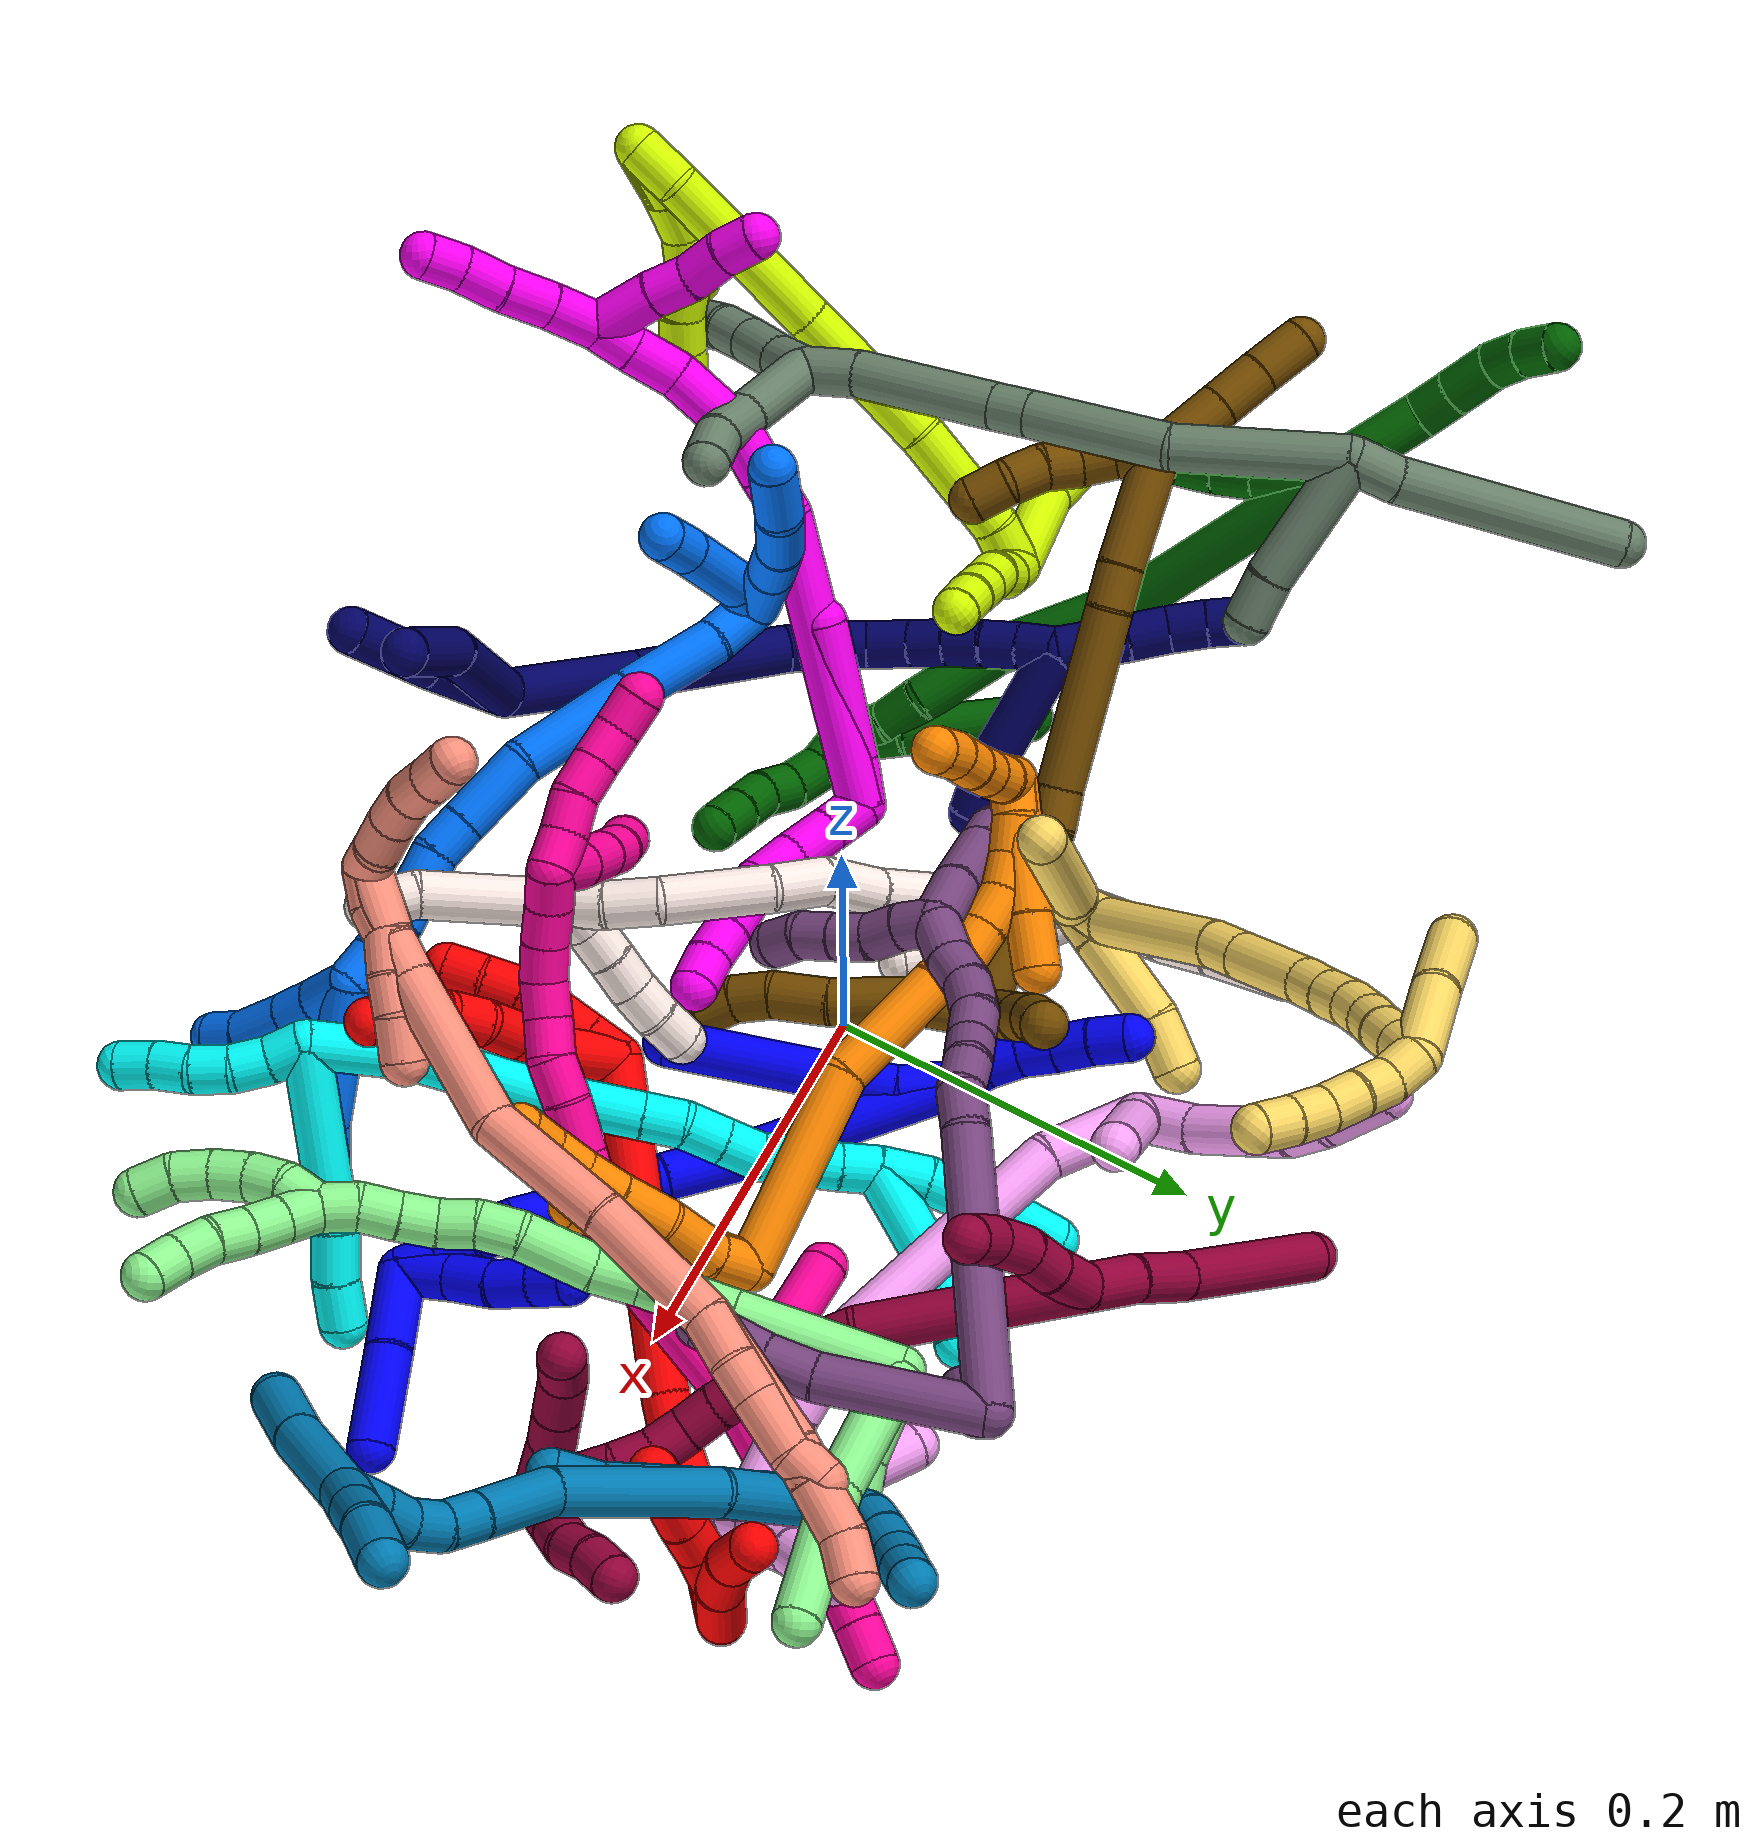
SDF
<sdf version="1.7">
 <world name="default">
  <plugin name="TubeGeneratorPlugin" filename="libtube_generator_plugin.so"/>
  <model name="photoneo_s_sensor">
   <static>1</static>
   <pose>0 0 2 1.57079 1.57079 3.14159</pose>
   <link name="link">
    <inertial><mass>0.1</mass></inertial>
    <sensor name="sensor" type="depth">
     <update_rate>30</update_rate>
     <camera>
      <horizontal_fov>1.22</horizontal_fov>
      <image><width>1920</width><height>1200</height><format>B8G8R8</format></image>
      <clip><near>0.1</near><far>4</far></clip>
      <depth_camera><output>points</output></depth_camera>
     </camera>
     <plugin name="camera_plugin" filename="libgazebo_ros_depth_camera.so">
      <baseline>0.2</baseline>
      <alwaysOn>1</alwaysOn>
      <updateRate>0.0</updateRate>
      <cameraName>camera_ir</cameraName>
      <imageTopicName>/camera/color/image_raw</imageTopicName>
      <cameraInfoTopicName>/camera/color/camera_info</cameraInfoTopicName>
      <depthImageTopicName>/camera/depth/image_raw</depthImageTopicName>
      <depthImageCameraInfoTopicName>/camera/depth/camera_info</depthImageCameraInfoTopicName>
      <pointCloudTopicName>/camera/depth/points</pointCloudTopicName>
      <frameName>fr_optical</frameName>
      <pointCloudCutoff>0.1</pointCloudCutoff>
      <pointCloudCutoffMax>2.0</pointCloudCutoffMax>
      <distortionK1>0</distortionK1>
      <distortionK2>0</distortionK2>
      <distortionK3>0</distortionK3>
      <distortionT1>0</distortionT1>
      <distortionT2>0</distortionT2>
      <CxPrime>0</CxPrime>
      <Cx>0</Cx>
      <Cy>0</Cy>
      <focalLength>0</focalLength>
      <hackBaseline>0</hackBaseline>
     </plugin>
    </sensor>
   </link>
  </model>
  <gravity>0 0 -9.8</gravity>
  <magnetic_field>6e-06 2.3e-05 -4.2e-05</magnetic_field>
  <atmosphere type="adiabatic"/>
  <physics name="default_physics" default="0" type="ode">
   <max_step_size>0.003</max_step_size>
   <real_time_factor>1</real_time_factor>
   <real_time_update_rate>1000</real_time_update_rate>
   <max_contacts>10000</max_contacts>
   <ode>
    <solver>
     <type>quick</type>
     <iters>100</iters>
     <sor>1.3</sor>
     <use_dynamic_moi_rescaling>0</use_dynamic_moi_rescaling>
    </solver>
    <constraints>
     <contact_max_correcting_vel>0</contact_max_correcting_vel>
     <contact_surface_layer>0.001</contact_surface_layer>
     <cfm>0</cfm>
     <erp>0.2</erp>
    </constraints>
   </ode>
  </physics>
  <scene><ambient>0.4 0.4 0.4 1</ambient><background>0.7 0.7 0.7 1</background><shadows>0</shadows></scene>
  <audio><device>default</device></audio>
  <spherical_coordinates>
   <surface_model>EARTH_WGS84</surface_model>
   <latitude_deg>0</latitude_deg>
   <longitude_deg>0</longitude_deg>
   <elevation>0</elevation>
   <heading_deg>0</heading_deg>
  </spherical_coordinates>
  <model name="bin">
   <static>1</static>
   <link name="bottom">
    <collision name="collision-bottom">
     <pose>0 0 -0.01 0 -0 0</pose>
     <geometry><box><size>0.8 0.6 0.02</size></box></geometry>
     <surface>
      <friction><ode><mu>100</mu><mu2>100</mu2></ode></friction>
      <contact><collide_bitmask>65535</collide_bitmask></contact>
     </surface>
    </collision>
   </link>
   <link name="west_wall">
    <collision name="collision-west_wall">
     <pose>-0.41 0 0.1 0 -0 0</pose>
     <geometry><box><size>0.02 0.6 0.2</size></box></geometry>
     <surface>
      <friction><ode><mu>100</mu><mu2>100</mu2></ode></friction>
      <contact><collide_bitmask>65535</collide_bitmask></contact>
     </surface>
    </collision>
   </link>
   <link name="east_wall">
    <collision name="collision-east_wall">
     <pose>0.41 0 0.1 0 -0 0</pose>
     <geometry><box><size>0.02 0.6 0.2</size></box></geometry>
     <surface>
      <friction><ode><mu>100</mu><mu2>100</mu2></ode></friction>
      <contact><collide_bitmask>65535</collide_bitmask></contact>
     </surface>
    </collision>
   </link>
   <link name="south_wall">
    <collision name="collision-south_wall">
     <pose>0 -0.31 0.1 0 -0 0</pose>
     <geometry><box><size>0.8 0.02 0.2</size></box></geometry>
     <surface>
      <friction><ode><mu>100</mu><mu2>100</mu2></ode></friction>
      <contact><collide_bitmask>65535</collide_bitmask></contact>
     </surface>
    </collision>
   </link>
   <link name="north_wall">
    <collision name="collision-north_wall">
     <pose>0 0.31 0.1 0 -0 0</pose>
     <geometry><box><size>0.8 0.02 0.2</size></box></geometry>
     <surface>
      <friction><ode><mu>100</mu><mu2>100</mu2></ode></friction>
      <contact><collide_bitmask>65535</collide_bitmask></contact>
     </surface>
    </collision>
   </link>
  </model>
  <model name="1">
   <static>0</static>
   <link name="1">
    <collision name="collision-cylinder-e_1_2_8">
     <pose>-0.002512 -0.000949 0.013928 0.06802 -0.178062 -0.006074</pose>
     <geometry><cylinder><radius>0.0125</radius><length>0.02837</length></cylinder></geometry>
     <surface>
      <friction><ode><mu>1.16</mu><mu2>1.16</mu2><slip1>0</slip1><slip2>0</slip2></ode></friction>
      <contact><ode><kp>1e+06</kp><kd>1</kd><max_vel>0</max_vel><min_depth>0.001</min_depth></ode></contact>
     </surface>
    </collision>
    <visual name="visual-cylinder-e_1_2_8">
     <pose>-0.002512 -0.000949 0.013928 0.06802 -0.178062 -0.006074</pose>
     <geometry><cylinder><radius>0.0125</radius><length>0.02837</length></cylinder></geometry>
     <material><ambient>0 0 1 1</ambient></material>
    </visual>
    <collision name="collision-cylinder-e_2_8_6">
     <pose>-0.025992 -0.02112 0.081609 0.343442 -0.351997 -0.061665</pose>
     <geometry><cylinder><radius>0.0125</radius><length>0.12163</length></cylinder></geometry>
     <surface>
      <friction><ode><mu>1.16</mu><mu2>1.16</mu2><slip1>0</slip1><slip2>0</slip2></ode></friction>
      <contact><ode><kp>1e+06</kp><kd>1</kd><max_vel>0</max_vel><min_depth>0.001</min_depth></ode></contact>
     </surface>
    </collision>
    <visual name="visual-cylinder-e_2_8_6">
     <pose>-0.025992 -0.02112 0.081609 0.343442 -0.351997 -0.061665</pose>
     <geometry><cylinder><radius>0.0125</radius><length>0.12163</length></cylinder></geometry>
     <material><ambient>0 0 1 1</ambient></material>
    </visual>
    <collision name="collision-cylinder-e_1_2_9">
     <pose>-0.002824 5.9e-05 -0.009593 -3.13548 -0.286278 3.09917</pose>
     <geometry><cylinder><radius>0.0125</radius><length>0.02</length></cylinder></geometry>
     <surface>
      <friction><ode><mu>1.16</mu><mu2>1.16</mu2><slip1>0</slip1><slip2>0</slip2></ode></friction>
      <contact><ode><kp>1e+06</kp><kd>1</kd><max_vel>0</max_vel><min_depth>0.001</min_depth></ode></contact>
     </surface>
    </collision>
    <visual name="visual-cylinder-e_1_2_9">
     <pose>-0.002824 5.9e-05 -0.009593 -3.13548 -0.286278 3.09917</pose>
     <geometry><cylinder><radius>0.0125</radius><length>0.02</length></cylinder></geometry>
     <material><ambient>0 0 1 1</ambient></material>
    </visual>
    <collision name="collision-cylinder-e_2_9_10">
     <pose>-0.007327 0.002316 -0.028795 -2.91671 -0.168717 1.28555</pose>
     <geometry><cylinder><radius>0.0125</radius><length>0.02</length></cylinder></geometry>
     <surface>
      <friction><ode><mu>1.16</mu><mu2>1.16</mu2><slip1>0</slip1><slip2>0</slip2></ode></friction>
      <contact><ode><kp>1e+06</kp><kd>1</kd><max_vel>0</max_vel><min_depth>0.001</min_depth></ode></contact>
     </surface>
    </collision>
    <visual name="visual-cylinder-e_2_9_10">
     <pose>-0.007327 0.002316 -0.028795 -2.91671 -0.168717 1.28555</pose>
     <geometry><cylinder><radius>0.0125</radius><length>0.02</length></cylinder></geometry>
     <material><ambient>0 0 1 1</ambient></material>
    </visual>
    <collision name="collision-cylinder-e_3_10_11">
     <pose>-0.009556 0.008513 -0.047554 -2.72955 -0.05506 0.262019</pose>
     <geometry><cylinder><radius>0.0125</radius><length>0.02</length></cylinder></geometry>
     <surface>
      <friction><ode><mu>1.16</mu><mu2>1.16</mu2><slip1>0</slip1><slip2>0</slip2></ode></friction>
      <contact><ode><kp>1e+06</kp><kd>1</kd><max_vel>0</max_vel><min_depth>0.001</min_depth></ode></contact>
     </surface>
    </collision>
    <visual name="visual-cylinder-e_3_10_11">
     <pose>-0.009556 0.008513 -0.047554 -2.72955 -0.05506 0.262019</pose>
     <geometry><cylinder><radius>0.0125</radius><length>0.02</length></cylinder></geometry>
     <material><ambient>0 0 1 1</ambient></material>
    </visual>
    <collision name="collision-cylinder-e_4_11_12">
     <pose>-0.011396 0.016627 -0.065726 -2.71366 -0.129245 0.578903</pose>
     <geometry><cylinder><radius>0.0125</radius><length>0.02</length></cylinder></geometry>
     <surface>
      <friction><ode><mu>1.16</mu><mu2>1.16</mu2><slip1>0</slip1><slip2>0</slip2></ode></friction>
      <contact><ode><kp>1e+06</kp><kd>1</kd><max_vel>0</max_vel><min_depth>0.001</min_depth></ode></contact>
     </surface>
    </collision>
    <visual name="visual-cylinder-e_4_11_12">
     <pose>-0.011396 0.016627 -0.065726 -2.71366 -0.129245 0.578903</pose>
     <geometry><cylinder><radius>0.0125</radius><length>0.02</length></cylinder></geometry>
     <material><ambient>0 0 1 1</ambient></material>
    </visual>
    <collision name="collision-cylinder-e_5_12_5">
     <pose>-0.012939 0.024651 -0.083949 -2.73987 -0.025508 0.125126</pose>
     <geometry><cylinder><radius>0.0125</radius><length>0.02</length></cylinder></geometry>
     <surface>
      <friction><ode><mu>1.16</mu><mu2>1.16</mu2><slip1>0</slip1><slip2>0</slip2></ode></friction>
      <contact><ode><kp>1e+06</kp><kd>1</kd><max_vel>0</max_vel><min_depth>0.001</min_depth></ode></contact>
     </surface>
    </collision>
    <visual name="visual-cylinder-e_5_12_5">
     <pose>-0.012939 0.024651 -0.083949 -2.73987 -0.025508 0.125126</pose>
     <geometry><cylinder><radius>0.0125</radius><length>0.02</length></cylinder></geometry>
     <material><ambient>0 0 1 1</ambient></material>
    </visual>
    <collision name="collision-cylinder-e_1_2_13">
     <pose>0.001729 0.003475 0.054068 -0.064181 0.031908 -0.001024</pose>
     <geometry><cylinder><radius>0.0125</radius><length>0.108414</length></cylinder></geometry>
     <surface>
      <friction><ode><mu>1.16</mu><mu2>1.16</mu2><slip1>0</slip1><slip2>0</slip2></ode></friction>
      <contact><ode><kp>1e+06</kp><kd>1</kd><max_vel>0</max_vel><min_depth>0.001</min_depth></ode></contact>
     </surface>
    </collision>
    <visual name="visual-cylinder-e_1_2_13">
     <pose>0.001729 0.003475 0.054068 -0.064181 0.031908 -0.001024</pose>
     <geometry><cylinder><radius>0.0125</radius><length>0.108414</length></cylinder></geometry>
     <material><ambient>0 0 1 1</ambient></material>
    </visual>
    <collision name="collision-cylinder-e_2_13_14">
     <pose>0.000237 0.012352 0.131601 -0.226297 -0.133019 0.015137</pose>
     <geometry><cylinder><radius>0.0125</radius><length>0.048587</length></cylinder></geometry>
     <surface>
      <friction><ode><mu>1.16</mu><mu2>1.16</mu2><slip1>0</slip1><slip2>0</slip2></ode></friction>
      <contact><ode><kp>1e+06</kp><kd>1</kd><max_vel>0</max_vel><min_depth>0.001</min_depth></ode></contact>
     </surface>
    </collision>
    <visual name="visual-cylinder-e_2_13_14">
     <pose>0.000237 0.012352 0.131601 -0.226297 -0.133019 0.015137</pose>
     <geometry><cylinder><radius>0.0125</radius><length>0.048587</length></cylinder></geometry>
     <material><ambient>0 0 1 1</ambient></material>
    </visual>
    <collision name="collision-cylinder-e_3_14_15">
     <pose>-0.00435 0.021521 0.172756 -0.209744 -0.075305 0.00793</pose>
     <geometry><cylinder><radius>0.0125</radius><length>0.036276</length></cylinder></geometry>
     <surface>
      <friction><ode><mu>1.16</mu><mu2>1.16</mu2><slip1>0</slip1><slip2>0</slip2></ode></friction>
      <contact><ode><kp>1e+06</kp><kd>1</kd><max_vel>0</max_vel><min_depth>0.001</min_depth></ode></contact>
     </surface>
    </collision>
    <visual name="visual-cylinder-e_3_14_15">
     <pose>-0.00435 0.021521 0.172756 -0.209744 -0.075305 0.00793</pose>
     <geometry><cylinder><radius>0.0125</radius><length>0.036276</length></cylinder></geometry>
     <material><ambient>0 0 1 1</ambient></material>
    </visual>
    <collision name="collision-cylinder-e_4_15_16">
     <pose>-0.006839 0.028119 0.202577 -0.22934 -0.090055 0.010379</pose>
     <geometry><cylinder><radius>0.0125</radius><length>0.025016</length></cylinder></geometry>
     <surface>
      <friction><ode><mu>1.16</mu><mu2>1.16</mu2><slip1>0</slip1><slip2>0</slip2></ode></friction>
      <contact><ode><kp>1e+06</kp><kd>1</kd><max_vel>0</max_vel><min_depth>0.001</min_depth></ode></contact>
     </surface>
    </collision>
    <visual name="visual-cylinder-e_4_15_16">
     <pose>-0.006839 0.028119 0.202577 -0.22934 -0.090055 0.010379</pose>
     <geometry><cylinder><radius>0.0125</radius><length>0.025016</length></cylinder></geometry>
     <material><ambient>0 0 1 1</ambient></material>
    </visual>
    <collision name="collision-cylinder-e_5_16_17">
     <pose>-0.009084 0.032701 0.224746 -0.172674 -0.109487 0.009486</pose>
     <geometry><cylinder><radius>0.0125</radius><length>0.020501</length></cylinder></geometry>
     <surface>
      <friction><ode><mu>1.16</mu><mu2>1.16</mu2><slip1>0</slip1><slip2>0</slip2></ode></friction>
      <contact><ode><kp>1e+06</kp><kd>1</kd><max_vel>0</max_vel><min_depth>0.001</min_depth></ode></contact>
     </surface>
    </collision>
    <visual name="visual-cylinder-e_5_16_17">
     <pose>-0.009084 0.032701 0.224746 -0.172674 -0.109487 0.009486</pose>
     <geometry><cylinder><radius>0.0125</radius><length>0.020501</length></cylinder></geometry>
     <material><ambient>0 0 1 1</ambient></material>
    </visual>
    <collision name="collision-cylinder-e_6_17_18">
     <pose>-0.008778 0.035378 0.244852 -0.091755 0.140124 -0.006444</pose>
     <geometry><cylinder><radius>0.0125</radius><length>0.020422</length></cylinder></geometry>
     <surface>
      <friction><ode><mu>1.16</mu><mu2>1.16</mu2><slip1>0</slip1><slip2>0</slip2></ode></friction>
      <contact><ode><kp>1e+06</kp><kd>1</kd><max_vel>0</max_vel><min_depth>0.001</min_depth></ode></contact>
     </surface>
    </collision>
    <visual name="visual-cylinder-e_6_17_18">
     <pose>-0.008778 0.035378 0.244852 -0.091755 0.140124 -0.006444</pose>
     <geometry><cylinder><radius>0.0125</radius><length>0.020422</length></cylinder></geometry>
     <material><ambient>0 0 1 1</ambient></material>
    </visual>
    <collision name="collision-cylinder-e_7_18_19">
     <pose>-0.005484 0.035498 0.264784 0.081568 0.186582 0.007636</pose>
     <geometry><cylinder><radius>0.0125</radius><length>0.020144</length></cylinder></geometry>
     <surface>
      <friction><ode><mu>1.16</mu><mu2>1.16</mu2><slip1>0</slip1><slip2>0</slip2></ode></friction>
      <contact><ode><kp>1e+06</kp><kd>1</kd><max_vel>0</max_vel><min_depth>0.001</min_depth></ode></contact>
     </surface>
    </collision>
    <visual name="visual-cylinder-e_7_18_19">
     <pose>-0.005484 0.035498 0.264784 0.081568 0.186582 0.007636</pose>
     <geometry><cylinder><radius>0.0125</radius><length>0.020144</length></cylinder></geometry>
     <material><ambient>0 0 1 1</ambient></material>
    </visual>
    <collision name="collision-cylinder-e_8_19_1">
     <pose>-0.00199 0.034451 0.284837 0.023638 0.158155 0.001873</pose>
     <geometry><cylinder><radius>0.0125</radius><length>0.020641</length></cylinder></geometry>
     <surface>
      <friction><ode><mu>1.16</mu><mu2>1.16</mu2><slip1>0</slip1><slip2>0</slip2></ode></friction>
      <contact><ode><kp>1e+06</kp><kd>1</kd><max_vel>0</max_vel><min_depth>0.001</min_depth></ode></contact>
     </surface>
    </collision>
    <visual name="visual-cylinder-e_8_19_1">
     <pose>-0.00199 0.034451 0.284837 0.023638 0.158155 0.001873</pose>
     <geometry><cylinder><radius>0.0125</radius><length>0.020641</length></cylinder></geometry>
     <material><ambient>0 0 1 1</ambient></material>
    </visual>
    <collision name="collision-cylinder-e_1_1_20">
     <pose>0.001244 0.041503 0.2827 -2.6073 0.111848 -0.403531</pose>
     <geometry><cylinder><radius>0.0125</radius><length>0.028822</length></cylinder></geometry>
     <surface>
      <friction><ode><mu>1.16</mu><mu2>1.16</mu2><slip1>0</slip1><slip2>0</slip2></ode></friction>
      <contact><ode><kp>1e+06</kp><kd>1</kd><max_vel>0</max_vel><min_depth>0.001</min_depth></ode></contact>
     </surface>
    </collision>
    <visual name="visual-cylinder-e_1_1_20">
     <pose>0.001244 0.041503 0.2827 -2.6073 0.111848 -0.403531</pose>
     <geometry><cylinder><radius>0.0125</radius><length>0.028822</length></cylinder></geometry>
     <material><ambient>0 0 1 1</ambient></material>
    </visual>
    <collision name="collision-cylinder-e_2_20_21">
     <pose>0.003622 0.057213 0.260296 -2.44581 0.058564 -0.161188</pose>
     <geometry><cylinder><radius>0.0125</radius><length>0.026307</length></cylinder></geometry>
     <surface>
      <friction><ode><mu>1.16</mu><mu2>1.16</mu2><slip1>0</slip1><slip2>0</slip2></ode></friction>
      <contact><ode><kp>1e+06</kp><kd>1</kd><max_vel>0</max_vel><min_depth>0.001</min_depth></ode></contact>
     </surface>
    </collision>
    <visual name="visual-cylinder-e_2_20_21">
     <pose>0.003622 0.057213 0.260296 -2.44581 0.058564 -0.161188</pose>
     <geometry><cylinder><radius>0.0125</radius><length>0.026307</length></cylinder></geometry>
     <material><ambient>0 0 1 1</ambient></material>
    </visual>
    <collision name="collision-cylinder-e_3_21_22">
     <pose>0.00388 0.071765 0.239746 -2.61155 -0.04221 0.155233</pose>
     <geometry><cylinder><radius>0.0125</radius><length>0.024295</length></cylinder></geometry>
     <surface>
      <friction><ode><mu>1.16</mu><mu2>1.16</mu2><slip1>0</slip1><slip2>0</slip2></ode></friction>
      <contact><ode><kp>1e+06</kp><kd>1</kd><max_vel>0</max_vel><min_depth>0.001</min_depth></ode></contact>
     </surface>
    </collision>
    <visual name="visual-cylinder-e_3_21_22">
     <pose>0.00388 0.071765 0.239746 -2.61155 -0.04221 0.155233</pose>
     <geometry><cylinder><radius>0.0125</radius><length>0.024295</length></cylinder></geometry>
     <material><ambient>0 0 1 1</ambient></material>
    </visual>
    <collision name="collision-cylinder-e_4_22_4">
     <pose>0.002517 0.083887 0.220951 -2.5182 -0.082686 0.255379</pose>
     <geometry><cylinder><radius>0.0125</radius><length>0.020576</length></cylinder></geometry>
     <surface>
      <friction><ode><mu>1.16</mu><mu2>1.16</mu2><slip1>0</slip1><slip2>0</slip2></ode></friction>
      <contact><ode><kp>1e+06</kp><kd>1</kd><max_vel>0</max_vel><min_depth>0.001</min_depth></ode></contact>
     </surface>
    </collision>
    <visual name="visual-cylinder-e_4_22_4">
     <pose>0.002517 0.083887 0.220951 -2.5182 -0.082686 0.255379</pose>
     <geometry><cylinder><radius>0.0125</radius><length>0.020576</length></cylinder></geometry>
     <material><ambient>0 0 1 1</ambient></material>
    </visual>
    <collision name="collision-cylinder-e_1_1_23">
     <pose>0.010447 0.053246 0.302977 -1.17512 0.482734 -0.325014</pose>
     <geometry><cylinder><radius>0.0125</radius><length>0.046582</length></cylinder></geometry>
     <surface>
      <friction><ode><mu>1.16</mu><mu2>1.16</mu2><slip1>0</slip1><slip2>0</slip2></ode></friction>
      <contact><ode><kp>1e+06</kp><kd>1</kd><max_vel>0</max_vel><min_depth>0.001</min_depth></ode></contact>
     </surface>
    </collision>
    <visual name="visual-cylinder-e_1_1_23">
     <pose>0.010447 0.053246 0.302977 -1.17512 0.482734 -0.325014</pose>
     <geometry><cylinder><radius>0.0125</radius><length>0.046582</length></cylinder></geometry>
     <material><ambient>0 0 1 1</ambient></material>
    </visual>
    <collision name="collision-cylinder-e_2_23_3">
     <pose>0.036099 0.092009 0.321125 -1.09372 0.589096 -0.365267</pose>
     <geometry><cylinder><radius>0.0125</radius><length>0.053418</length></cylinder></geometry>
     <surface>
      <friction><ode><mu>1.16</mu><mu2>1.16</mu2><slip1>0</slip1><slip2>0</slip2></ode></friction>
      <contact><ode><kp>1e+06</kp><kd>1</kd><max_vel>0</max_vel><min_depth>0.001</min_depth></ode></contact>
     </surface>
    </collision>
    <visual name="visual-cylinder-e_2_23_3">
     <pose>0.036099 0.092009 0.321125 -1.09372 0.589096 -0.365267</pose>
     <geometry><cylinder><radius>0.0125</radius><length>0.053418</length></cylinder></geometry>
     <material><ambient>0 0 1 1</ambient></material>
    </visual>
    <collision name="collision-sphere-3">
     <pose>0.050938 0.111736 0.331322 0 -0 0</pose>
     <geometry><sphere><radius>0.0125</radius></sphere></geometry>
     <surface>
      <friction><ode><mu>1.16</mu><mu2>1.16</mu2><slip1>0</slip1><slip2>0</slip2></ode></friction>
      <contact><ode><kp>1e+06</kp><kd>1</kd><max_vel>0</max_vel><min_depth>0.001</min_depth></ode></contact>
     </surface>
    </collision>
    <visual name="visual-sphere-3">
     <pose>0.050938 0.111736 0.331322 0 -0 0</pose>
     <geometry><sphere><radius>0.0125</radius></sphere></geometry>
     <material><ambient>0 0 1 1</ambient></material>
    </visual>
    <collision name="collision-sphere-23">
     <pose>0.021259 0.072282 0.310928 0 -0 0</pose>
     <geometry><sphere><radius>0.0125</radius></sphere></geometry>
     <surface>
      <friction><ode><mu>1.16</mu><mu2>1.16</mu2><slip1>0</slip1><slip2>0</slip2></ode></friction>
      <contact><ode><kp>1e+06</kp><kd>1</kd><max_vel>0</max_vel><min_depth>0.001</min_depth></ode></contact>
     </surface>
    </collision>
    <visual name="visual-sphere-23">
     <pose>0.021259 0.072282 0.310928 0 -0 0</pose>
     <geometry><sphere><radius>0.0125</radius></sphere></geometry>
     <material><ambient>0 0 1 1</ambient></material>
    </visual>
    <collision name="collision-sphere-4">
     <pose>0.001668 0.089872 0.212627 0 -0 0</pose>
     <geometry><sphere><radius>0.0125</radius></sphere></geometry>
     <surface>
      <friction><ode><mu>1.16</mu><mu2>1.16</mu2><slip1>0</slip1><slip2>0</slip2></ode></friction>
      <contact><ode><kp>1e+06</kp><kd>1</kd><max_vel>0</max_vel><min_depth>0.001</min_depth></ode></contact>
     </surface>
    </collision>
    <visual name="visual-sphere-4">
     <pose>0.001668 0.089872 0.212627 0 -0 0</pose>
     <geometry><sphere><radius>0.0125</radius></sphere></geometry>
     <material><ambient>0 0 1 1</ambient></material>
    </visual>
    <collision name="collision-sphere-22">
     <pose>0.003367 0.077901 0.229275 0 -0 0</pose>
     <geometry><sphere><radius>0.0125</radius></sphere></geometry>
     <surface>
      <friction><ode><mu>1.16</mu><mu2>1.16</mu2><slip1>0</slip1><slip2>0</slip2></ode></friction>
      <contact><ode><kp>1e+06</kp><kd>1</kd><max_vel>0</max_vel><min_depth>0.001</min_depth></ode></contact>
     </surface>
    </collision>
    <visual name="visual-sphere-22">
     <pose>0.003367 0.077901 0.229275 0 -0 0</pose>
     <geometry><sphere><radius>0.0125</radius></sphere></geometry>
     <material><ambient>0 0 1 1</ambient></material>
    </visual>
    <collision name="collision-sphere-21">
     <pose>0.004392 0.06563 0.250218 0 -0 0</pose>
     <geometry><sphere><radius>0.0125</radius></sphere></geometry>
     <surface>
      <friction><ode><mu>1.16</mu><mu2>1.16</mu2><slip1>0</slip1><slip2>0</slip2></ode></friction>
      <contact><ode><kp>1e+06</kp><kd>1</kd><max_vel>0</max_vel><min_depth>0.001</min_depth></ode></contact>
     </surface>
    </collision>
    <visual name="visual-sphere-21">
     <pose>0.004392 0.06563 0.250218 0 -0 0</pose>
     <geometry><sphere><radius>0.0125</radius></sphere></geometry>
     <material><ambient>0 0 1 1</ambient></material>
    </visual>
    <collision name="collision-sphere-20">
     <pose>0.002852 0.048796 0.270375 0 -0 0</pose>
     <geometry><sphere><radius>0.0125</radius></sphere></geometry>
     <surface>
      <friction><ode><mu>1.16</mu><mu2>1.16</mu2><slip1>0</slip1><slip2>0</slip2></ode></friction>
      <contact><ode><kp>1e+06</kp><kd>1</kd><max_vel>0</max_vel><min_depth>0.001</min_depth></ode></contact>
     </surface>
    </collision>
    <visual name="visual-sphere-20">
     <pose>0.002852 0.048796 0.270375 0 -0 0</pose>
     <geometry><sphere><radius>0.0125</radius></sphere></geometry>
     <material><ambient>0 0 1 1</ambient></material>
    </visual>
    <collision name="collision-sphere-11">
     <pose>-0.010107 0.012511 -0.056704 0 -0 0</pose>
     <geometry><sphere><radius>0.0125</radius></sphere></geometry>
     <surface>
      <friction><ode><mu>1.16</mu><mu2>1.16</mu2><slip1>0</slip1><slip2>0</slip2></ode></friction>
      <contact><ode><kp>1e+06</kp><kd>1</kd><max_vel>0</max_vel><min_depth>0.001</min_depth></ode></contact>
     </surface>
    </collision>
    <visual name="visual-sphere-11">
     <pose>-0.010107 0.012511 -0.056704 0 -0 0</pose>
     <geometry><sphere><radius>0.0125</radius></sphere></geometry>
     <material><ambient>0 0 1 1</ambient></material>
    </visual>
    <collision name="collision-sphere-10">
     <pose>-0.009006 0.004514 -0.038405 0 -0 0</pose>
     <geometry><sphere><radius>0.0125</radius></sphere></geometry>
     <surface>
      <friction><ode><mu>1.16</mu><mu2>1.16</mu2><slip1>0</slip1><slip2>0</slip2></ode></friction>
      <contact><ode><kp>1e+06</kp><kd>1</kd><max_vel>0</max_vel><min_depth>0.001</min_depth></ode></contact>
     </surface>
    </collision>
    <visual name="visual-sphere-10">
     <pose>-0.009006 0.004514 -0.038405 0 -0 0</pose>
     <geometry><sphere><radius>0.0125</radius></sphere></geometry>
     <material><ambient>0 0 1 1</ambient></material>
    </visual>
    <collision name="collision-sphere-6">
     <pose>-0.04696 -0.040343 0.135362 0 -0 0</pose>
     <geometry><sphere><radius>0.0125</radius></sphere></geometry>
     <surface>
      <friction><ode><mu>1.16</mu><mu2>1.16</mu2><slip1>0</slip1><slip2>0</slip2></ode></friction>
      <contact><ode><kp>1e+06</kp><kd>1</kd><max_vel>0</max_vel><min_depth>0.001</min_depth></ode></contact>
     </surface>
    </collision>
    <visual name="visual-sphere-6">
     <pose>-0.04696 -0.040343 0.135362 0 -0 0</pose>
     <geometry><sphere><radius>0.0125</radius></sphere></geometry>
     <material><ambient>0 0 1 1</ambient></material>
    </visual>
    <collision name="collision-sphere-9">
     <pose>-0.005648 0.000117 -0.019186 0 -0 0</pose>
     <geometry><sphere><radius>0.0125</radius></sphere></geometry>
     <surface>
      <friction><ode><mu>1.16</mu><mu2>1.16</mu2><slip1>0</slip1><slip2>0</slip2></ode></friction>
      <contact><ode><kp>1e+06</kp><kd>1</kd><max_vel>0</max_vel><min_depth>0.001</min_depth></ode></contact>
     </surface>
    </collision>
    <visual name="visual-sphere-9">
     <pose>-0.005648 0.000117 -0.019186 0 -0 0</pose>
     <geometry><sphere><radius>0.0125</radius></sphere></geometry>
     <material><ambient>0 0 1 1</ambient></material>
    </visual>
    <collision name="collision-sphere-2">
     <geometry><sphere><radius>0.0125</radius></sphere></geometry>
     <surface>
      <friction><ode><mu>1.16</mu><mu2>1.16</mu2><slip1>0</slip1><slip2>0</slip2></ode></friction>
      <contact><ode><kp>1e+06</kp><kd>1</kd><max_vel>0</max_vel><min_depth>0.001</min_depth></ode></contact>
     </surface>
    </collision>
    <visual name="visual-sphere-2">
     <geometry><sphere><radius>0.0125</radius></sphere></geometry>
     <material><ambient>0 0 1 1</ambient></material>
    </visual>
    <collision name="collision-sphere-19">
     <pose>-0.003616 0.034692 0.274648 0 -0 0</pose>
     <geometry><sphere><radius>0.0125</radius></sphere></geometry>
     <surface>
      <friction><ode><mu>1.16</mu><mu2>1.16</mu2><slip1>0</slip1><slip2>0</slip2></ode></friction>
      <contact><ode><kp>1e+06</kp><kd>1</kd><max_vel>0</max_vel><min_depth>0.001</min_depth></ode></contact>
     </surface>
    </collision>
    <visual name="visual-sphere-19">
     <pose>-0.003616 0.034692 0.274648 0 -0 0</pose>
     <geometry><sphere><radius>0.0125</radius></sphere></geometry>
     <material><ambient>0 0 1 1</ambient></material>
    </visual>
    <collision name="collision-sphere-8">
     <pose>-0.005025 -0.001898 0.027856 0 -0 0</pose>
     <geometry><sphere><radius>0.0125</radius></sphere></geometry>
     <surface>
      <friction><ode><mu>1.16</mu><mu2>1.16</mu2><slip1>0</slip1><slip2>0</slip2></ode></friction>
      <contact><ode><kp>1e+06</kp><kd>1</kd><max_vel>0</max_vel><min_depth>0.001</min_depth></ode></contact>
     </surface>
    </collision>
    <visual name="visual-sphere-8">
     <pose>-0.005025 -0.001898 0.027856 0 -0 0</pose>
     <geometry><sphere><radius>0.0125</radius></sphere></geometry>
     <material><ambient>0 0 1 1</ambient></material>
    </visual>
    <collision name="collision-sphere-12">
     <pose>-0.012684 0.020742 -0.074748 0 -0 0</pose>
     <geometry><sphere><radius>0.0125</radius></sphere></geometry>
     <surface>
      <friction><ode><mu>1.16</mu><mu2>1.16</mu2><slip1>0</slip1><slip2>0</slip2></ode></friction>
      <contact><ode><kp>1e+06</kp><kd>1</kd><max_vel>0</max_vel><min_depth>0.001</min_depth></ode></contact>
     </surface>
    </collision>
    <visual name="visual-sphere-12">
     <pose>-0.012684 0.020742 -0.074748 0 -0 0</pose>
     <geometry><sphere><radius>0.0125</radius></sphere></geometry>
     <material><ambient>0 0 1 1</ambient></material>
    </visual>
    <collision name="collision-sphere-5">
     <pose>-0.013194 0.028559 -0.09315 0 -0 0</pose>
     <geometry><sphere><radius>0.0125</radius></sphere></geometry>
     <surface>
      <friction><ode><mu>1.16</mu><mu2>1.16</mu2><slip1>0</slip1><slip2>0</slip2></ode></friction>
      <contact><ode><kp>1e+06</kp><kd>1</kd><max_vel>0</max_vel><min_depth>0.001</min_depth></ode></contact>
     </surface>
    </collision>
    <visual name="visual-sphere-5">
     <pose>-0.013194 0.028559 -0.09315 0 -0 0</pose>
     <geometry><sphere><radius>0.0125</radius></sphere></geometry>
     <material><ambient>0 0 1 1</ambient></material>
    </visual>
    <collision name="collision-sphere-13">
     <pose>0.003459 0.00695 0.108136 0 -0 0</pose>
     <geometry><sphere><radius>0.0125</radius></sphere></geometry>
     <surface>
      <friction><ode><mu>1.16</mu><mu2>1.16</mu2><slip1>0</slip1><slip2>0</slip2></ode></friction>
      <contact><ode><kp>1e+06</kp><kd>1</kd><max_vel>0</max_vel><min_depth>0.001</min_depth></ode></contact>
     </surface>
    </collision>
    <visual name="visual-sphere-13">
     <pose>0.003459 0.00695 0.108136 0 -0 0</pose>
     <geometry><sphere><radius>0.0125</radius></sphere></geometry>
     <material><ambient>0 0 1 1</ambient></material>
    </visual>
    <collision name="collision-sphere-14">
     <pose>-0.002985 0.017755 0.155065 0 -0 0</pose>
     <geometry><sphere><radius>0.0125</radius></sphere></geometry>
     <surface>
      <friction><ode><mu>1.16</mu><mu2>1.16</mu2><slip1>0</slip1><slip2>0</slip2></ode></friction>
      <contact><ode><kp>1e+06</kp><kd>1</kd><max_vel>0</max_vel><min_depth>0.001</min_depth></ode></contact>
     </surface>
    </collision>
    <visual name="visual-sphere-14">
     <pose>-0.002985 0.017755 0.155065 0 -0 0</pose>
     <geometry><sphere><radius>0.0125</radius></sphere></geometry>
     <material><ambient>0 0 1 1</ambient></material>
    </visual>
    <collision name="collision-sphere-15">
     <pose>-0.005714 0.025287 0.190446 0 -0 0</pose>
     <geometry><sphere><radius>0.0125</radius></sphere></geometry>
     <surface>
      <friction><ode><mu>1.16</mu><mu2>1.16</mu2><slip1>0</slip1><slip2>0</slip2></ode></friction>
      <contact><ode><kp>1e+06</kp><kd>1</kd><max_vel>0</max_vel><min_depth>0.001</min_depth></ode></contact>
     </surface>
    </collision>
    <visual name="visual-sphere-15">
     <pose>-0.005714 0.025287 0.190446 0 -0 0</pose>
     <geometry><sphere><radius>0.0125</radius></sphere></geometry>
     <material><ambient>0 0 1 1</ambient></material>
    </visual>
    <collision name="collision-sphere-16">
     <pose>-0.007964 0.030951 0.214708 0 -0 0</pose>
     <geometry><sphere><radius>0.0125</radius></sphere></geometry>
     <surface>
      <friction><ode><mu>1.16</mu><mu2>1.16</mu2><slip1>0</slip1><slip2>0</slip2></ode></friction>
      <contact><ode><kp>1e+06</kp><kd>1</kd><max_vel>0</max_vel><min_depth>0.001</min_depth></ode></contact>
     </surface>
    </collision>
    <visual name="visual-sphere-16">
     <pose>-0.007964 0.030951 0.214708 0 -0 0</pose>
     <geometry><sphere><radius>0.0125</radius></sphere></geometry>
     <material><ambient>0 0 1 1</ambient></material>
    </visual>
    <collision name="collision-sphere-17">
     <pose>-0.010204 0.034452 0.234784 0 -0 0</pose>
     <geometry><sphere><radius>0.0125</radius></sphere></geometry>
     <surface>
      <friction><ode><mu>1.16</mu><mu2>1.16</mu2><slip1>0</slip1><slip2>0</slip2></ode></friction>
      <contact><ode><kp>1e+06</kp><kd>1</kd><max_vel>0</max_vel><min_depth>0.001</min_depth></ode></contact>
     </surface>
    </collision>
    <visual name="visual-sphere-17">
     <pose>-0.010204 0.034452 0.234784 0 -0 0</pose>
     <geometry><sphere><radius>0.0125</radius></sphere></geometry>
     <material><ambient>0 0 1 1</ambient></material>
    </visual>
    <collision name="collision-sphere-18">
     <pose>-0.007352 0.036305 0.25492 0 -0 0</pose>
     <geometry><sphere><radius>0.0125</radius></sphere></geometry>
     <surface>
      <friction><ode><mu>1.16</mu><mu2>1.16</mu2><slip1>0</slip1><slip2>0</slip2></ode></friction>
      <contact><ode><kp>1e+06</kp><kd>1</kd><max_vel>0</max_vel><min_depth>0.001</min_depth></ode></contact>
     </surface>
    </collision>
    <visual name="visual-sphere-18">
     <pose>-0.007352 0.036305 0.25492 0 -0 0</pose>
     <geometry><sphere><radius>0.0125</radius></sphere></geometry>
     <material><ambient>0 0 1 1</ambient></material>
    </visual>
    <collision name="collision-sphere-1">
     <pose>-0.000365 0.03421 0.295026 0 -0 0</pose>
     <geometry><sphere><radius>0.0125</radius></sphere></geometry>
     <surface>
      <friction><ode><mu>1.16</mu><mu2>1.16</mu2><slip1>0</slip1><slip2>0</slip2></ode></friction>
      <contact><ode><kp>1e+06</kp><kd>1</kd><max_vel>0</max_vel><min_depth>0.001</min_depth></ode></contact>
     </surface>
    </collision>
    <visual name="visual-sphere-1">
     <pose>-0.000365 0.03421 0.295026 0 -0 0</pose>
     <geometry><sphere><radius>0.0125</radius></sphere></geometry>
     <material><ambient>0 0 1 1</ambient></material>
    </visual>
    <inertial>
     <pose>-0.002758 0.023058 0.142205 0 -0 0</pose>
     <mass>0.75</mass>
     <inertia>
      <ixx>0.000301</ixx>
      <ixy>0</ixy>
      <ixz>0</ixz>
      <iyy>0.000286</iyy>
      <iyz>0</iyz>
      <izz>7.3e-05</izz>
     </inertia>
    </inertial>
   </link>
   <pose>0.011144 0.069614 0.022107 1.74012 0.885482 0.88344</pose>
  </model>
  <model name="2">
   <static>0</static>
   <link name="2">
    <collision name="collision-cylinder-e_1_2_8">
     <pose>-0.013124 -0.003082 -0.011823 2.88658 -0.821136 -2.56878</pose>
     <geometry><cylinder><radius>0.0125</radius><length>0.035863</length></cylinder></geometry>
     <surface>
      <friction><ode><mu>1.16</mu><mu2>1.16</mu2><slip1>0</slip1><slip2>0</slip2></ode></friction>
      <contact><ode><kp>1e+06</kp><kd>1</kd><max_vel>0</max_vel><min_depth>0.001</min_depth></ode></contact>
     </surface>
    </collision>
    <visual name="visual-cylinder-e_1_2_8">
     <pose>-0.013124 -0.003082 -0.011823 2.88658 -0.821136 -2.56878</pose>
     <geometry><cylinder><radius>0.0125</radius><length>0.035863</length></cylinder></geometry>
     <material><ambient>1 0 0 1</ambient></material>
    </visual>
    <collision name="collision-cylinder-e_2_8_9">
     <pose>-0.034024 -0.010801 -0.032829 2.67398 -0.647204 -1.90665</pose>
     <geometry><cylinder><radius>0.0125</radius><length>0.025789</length></cylinder></geometry>
     <surface>
      <friction><ode><mu>1.16</mu><mu2>1.16</mu2><slip1>0</slip1><slip2>0</slip2></ode></friction>
      <contact><ode><kp>1e+06</kp><kd>1</kd><max_vel>0</max_vel><min_depth>0.001</min_depth></ode></contact>
     </surface>
    </collision>
    <visual name="visual-cylinder-e_2_8_9">
     <pose>-0.034024 -0.010801 -0.032829 2.67398 -0.647204 -1.90665</pose>
     <geometry><cylinder><radius>0.0125</radius><length>0.025789</length></cylinder></geometry>
     <material><ambient>1 0 0 1</ambient></material>
    </visual>
    <collision name="collision-cylinder-e_3_9_10">
     <pose>-0.047352 -0.019079 -0.052987 2.8213 -0.447727 -1.90748</pose>
     <geometry><cylinder><radius>0.0125</radius><length>0.025655</length></cylinder></geometry>
     <surface>
      <friction><ode><mu>1.16</mu><mu2>1.16</mu2><slip1>0</slip1><slip2>0</slip2></ode></friction>
      <contact><ode><kp>1e+06</kp><kd>1</kd><max_vel>0</max_vel><min_depth>0.001</min_depth></ode></contact>
     </surface>
    </collision>
    <visual name="visual-cylinder-e_3_9_10">
     <pose>-0.047352 -0.019079 -0.052987 2.8213 -0.447727 -1.90748</pose>
     <geometry><cylinder><radius>0.0125</radius><length>0.025655</length></cylinder></geometry>
     <material><ambient>1 0 0 1</ambient></material>
    </visual>
    <collision name="collision-cylinder-e_4_10_11">
     <pose>-0.059998 -0.025435 -0.070699 2.75838 -0.773528 -2.25258</pose>
     <geometry><cylinder><radius>0.0125</radius><length>0.020305</length></cylinder></geometry>
     <surface>
      <friction><ode><mu>1.16</mu><mu2>1.16</mu2><slip1>0</slip1><slip2>0</slip2></ode></friction>
      <contact><ode><kp>1e+06</kp><kd>1</kd><max_vel>0</max_vel><min_depth>0.001</min_depth></ode></contact>
     </surface>
    </collision>
    <visual name="visual-cylinder-e_4_10_11">
     <pose>-0.059998 -0.025435 -0.070699 2.75838 -0.773528 -2.25258</pose>
     <geometry><cylinder><radius>0.0125</radius><length>0.020305</length></cylinder></geometry>
     <material><ambient>1 0 0 1</ambient></material>
    </visual>
    <collision name="collision-cylinder-e_5_11_12">
     <pose>-0.076306 -0.028512 -0.083138 3.07846 -1.01571 -3.02824</pose>
     <geometry><cylinder><radius>0.0125</radius><length>0.021685</length></cylinder></geometry>
     <surface>
      <friction><ode><mu>1.16</mu><mu2>1.16</mu2><slip1>0</slip1><slip2>0</slip2></ode></friction>
      <contact><ode><kp>1e+06</kp><kd>1</kd><max_vel>0</max_vel><min_depth>0.001</min_depth></ode></contact>
     </surface>
    </collision>
    <visual name="visual-cylinder-e_5_11_12">
     <pose>-0.076306 -0.028512 -0.083138 3.07846 -1.01571 -3.02824</pose>
     <geometry><cylinder><radius>0.0125</radius><length>0.021685</length></cylinder></geometry>
     <material><ambient>1 0 0 1</ambient></material>
    </visual>
    <collision name="collision-cylinder-e_6_12_6">
     <pose>-0.094048 -0.028429 -0.094691 -3.06603 -0.968168 2.99807</pose>
     <geometry><cylinder><radius>0.0125</radius><length>0.020703</length></cylinder></geometry>
     <surface>
      <friction><ode><mu>1.16</mu><mu2>1.16</mu2><slip1>0</slip1><slip2>0</slip2></ode></friction>
      <contact><ode><kp>1e+06</kp><kd>1</kd><max_vel>0</max_vel><min_depth>0.001</min_depth></ode></contact>
     </surface>
    </collision>
    <visual name="visual-cylinder-e_6_12_6">
     <pose>-0.094048 -0.028429 -0.094691 -3.06603 -0.968168 2.99807</pose>
     <geometry><cylinder><radius>0.0125</radius><length>0.020703</length></cylinder></geometry>
     <material><ambient>1 0 0 1</ambient></material>
    </visual>
    <collision name="collision-cylinder-e_1_2_13">
     <pose>-0.007296 -0.006616 -0.001729 1.82633 -0.817768 -1.02257</pose>
     <geometry><cylinder><radius>0.0125</radius><length>0.02</length></cylinder></geometry>
     <surface>
      <friction><ode><mu>1.16</mu><mu2>1.16</mu2><slip1>0</slip1><slip2>0</slip2></ode></friction>
      <contact><ode><kp>1e+06</kp><kd>1</kd><max_vel>0</max_vel><min_depth>0.001</min_depth></ode></contact>
     </surface>
    </collision>
    <visual name="visual-cylinder-e_1_2_13">
     <pose>-0.007296 -0.006616 -0.001729 1.82633 -0.817768 -1.02257</pose>
     <geometry><cylinder><radius>0.0125</radius><length>0.02</length></cylinder></geometry>
     <material><ambient>1 0 0 1</ambient></material>
    </visual>
    <collision name="collision-cylinder-e_2_13_14">
     <pose>-0.021898 -0.019849 -0.005148 1.821 -0.81908 -1.01941</pose>
     <geometry><cylinder><radius>0.0125</radius><length>0.02</length></cylinder></geometry>
     <surface>
      <friction><ode><mu>1.16</mu><mu2>1.16</mu2><slip1>0</slip1><slip2>0</slip2></ode></friction>
      <contact><ode><kp>1e+06</kp><kd>1</kd><max_vel>0</max_vel><min_depth>0.001</min_depth></ode></contact>
     </surface>
    </collision>
    <visual name="visual-cylinder-e_2_13_14">
     <pose>-0.021898 -0.019849 -0.005148 1.821 -0.81908 -1.01941</pose>
     <geometry><cylinder><radius>0.0125</radius><length>0.02</length></cylinder></geometry>
     <material><ambient>1 0 0 1</ambient></material>
    </visual>
    <collision name="collision-cylinder-e_3_14_15">
     <pose>-0.036888 -0.032598 -0.008666 1.86042 -0.876465 -1.12242</pose>
     <geometry><cylinder><radius>0.0125</radius><length>0.02</length></cylinder></geometry>
     <surface>
      <friction><ode><mu>1.16</mu><mu2>1.16</mu2><slip1>0</slip1><slip2>0</slip2></ode></friction>
      <contact><ode><kp>1e+06</kp><kd>1</kd><max_vel>0</max_vel><min_depth>0.001</min_depth></ode></contact>
     </surface>
    </collision>
    <visual name="visual-cylinder-e_3_14_15">
     <pose>-0.036888 -0.032598 -0.008666 1.86042 -0.876465 -1.12242</pose>
     <geometry><cylinder><radius>0.0125</radius><length>0.02</length></cylinder></geometry>
     <material><ambient>1 0 0 1</ambient></material>
    </visual>
    <collision name="collision-cylinder-e_4_15_16">
     <pose>-0.053533 -0.042839 -0.012172 1.95851 -1.11089 -1.49165</pose>
     <geometry><cylinder><radius>0.0125</radius><length>0.02</length></cylinder></geometry>
     <surface>
      <friction><ode><mu>1.16</mu><mu2>1.16</mu2><slip1>0</slip1><slip2>0</slip2></ode></friction>
      <contact><ode><kp>1e+06</kp><kd>1</kd><max_vel>0</max_vel><min_depth>0.001</min_depth></ode></contact>
     </surface>
    </collision>
    <visual name="visual-cylinder-e_4_15_16">
     <pose>-0.053533 -0.042839 -0.012172 1.95851 -1.11089 -1.49165</pose>
     <geometry><cylinder><radius>0.0125</radius><length>0.02</length></cylinder></geometry>
     <material><ambient>1 0 0 1</ambient></material>
    </visual>
    <collision name="collision-cylinder-e_5_16_5">
     <pose>-0.071639 -0.050995 -0.013934 1.59153 -1.15409 -1.17312</pose>
     <geometry><cylinder><radius>0.0125</radius><length>0.02</length></cylinder></geometry>
     <surface>
      <friction><ode><mu>1.16</mu><mu2>1.16</mu2><slip1>0</slip1><slip2>0</slip2></ode></friction>
      <contact><ode><kp>1e+06</kp><kd>1</kd><max_vel>0</max_vel><min_depth>0.001</min_depth></ode></contact>
     </surface>
    </collision>
    <visual name="visual-cylinder-e_5_16_5">
     <pose>-0.071639 -0.050995 -0.013934 1.59153 -1.15409 -1.17312</pose>
     <geometry><cylinder><radius>0.0125</radius><length>0.02</length></cylinder></geometry>
     <material><ambient>1 0 0 1</ambient></material>
    </visual>
    <collision name="collision-cylinder-e_1_2_17">
     <pose>0.005685 0.086067 -0.010018 -1.68667 0.065521 -0.073583</pose>
     <geometry><cylinder><radius>0.0125</radius><length>0.173668</length></cylinder></geometry>
     <surface>
      <friction><ode><mu>1.16</mu><mu2>1.16</mu2><slip1>0</slip1><slip2>0</slip2></ode></friction>
      <contact><ode><kp>1e+06</kp><kd>1</kd><max_vel>0</max_vel><min_depth>0.001</min_depth></ode></contact>
     </surface>
    </collision>
    <visual name="visual-cylinder-e_1_2_17">
     <pose>0.005685 0.086067 -0.010018 -1.68667 0.065521 -0.073583</pose>
     <geometry><cylinder><radius>0.0125</radius><length>0.173668</length></cylinder></geometry>
     <material><ambient>1 0 0 1</ambient></material>
    </visual>
    <collision name="collision-cylinder-e_2_17_18">
     <pose>0.013256 0.184172 -0.022425 -1.76675 0.152375 -0.185421</pose>
     <geometry><cylinder><radius>0.0125</radius><length>0.024834</length></cylinder></geometry>
     <surface>
      <friction><ode><mu>1.16</mu><mu2>1.16</mu2><slip1>0</slip1><slip2>0</slip2></ode></friction>
      <contact><ode><kp>1e+06</kp><kd>1</kd><max_vel>0</max_vel><min_depth>0.001</min_depth></ode></contact>
     </surface>
    </collision>
    <visual name="visual-cylinder-e_2_17_18">
     <pose>0.013256 0.184172 -0.022425 -1.76675 0.152375 -0.185421</pose>
     <geometry><cylinder><radius>0.0125</radius><length>0.024834</length></cylinder></geometry>
     <material><ambient>1 0 0 1</ambient></material>
    </visual>
    <collision name="collision-cylinder-e_3_18_19">
     <pose>0.021675 0.216712 -0.032508 -1.92983 0.290006 -0.415471</pose>
     <geometry><cylinder><radius>0.0125</radius><length>0.045704</length></cylinder></geometry>
     <surface>
      <friction><ode><mu>1.16</mu><mu2>1.16</mu2><slip1>0</slip1><slip2>0</slip2></ode></friction>
      <contact><ode><kp>1e+06</kp><kd>1</kd><max_vel>0</max_vel><min_depth>0.001</min_depth></ode></contact>
     </surface>
    </collision>
    <visual name="visual-cylinder-e_3_18_19">
     <pose>0.021675 0.216712 -0.032508 -1.92983 0.290006 -0.415471</pose>
     <geometry><cylinder><radius>0.0125</radius><length>0.045704</length></cylinder></geometry>
     <material><ambient>1 0 0 1</ambient></material>
    </visual>
    <collision name="collision-cylinder-e_4_19_20">
     <pose>0.029927 0.246611 -0.045272 -2.0655 0.159453 -0.266175</pose>
     <geometry><cylinder><radius>0.0125</radius><length>0.02163</length></cylinder></geometry>
     <surface>
      <friction><ode><mu>1.16</mu><mu2>1.16</mu2><slip1>0</slip1><slip2>0</slip2></ode></friction>
      <contact><ode><kp>1e+06</kp><kd>1</kd><max_vel>0</max_vel><min_depth>0.001</min_depth></ode></contact>
     </surface>
    </collision>
    <visual name="visual-cylinder-e_4_19_20">
     <pose>0.029927 0.246611 -0.045272 -2.0655 0.159453 -0.266175</pose>
     <geometry><cylinder><radius>0.0125</radius><length>0.02163</length></cylinder></geometry>
     <material><ambient>1 0 0 1</ambient></material>
    </visual>
    <collision name="collision-cylinder-e_5_20_1">
     <pose>0.035104 0.27066 -0.058413 -2.07434 0.203938 -0.34299</pose>
     <geometry><cylinder><radius>0.0125</radius><length>0.034164</length></cylinder></geometry>
     <surface>
      <friction><ode><mu>1.16</mu><mu2>1.16</mu2><slip1>0</slip1><slip2>0</slip2></ode></friction>
      <contact><ode><kp>1e+06</kp><kd>1</kd><max_vel>0</max_vel><min_depth>0.001</min_depth></ode></contact>
     </surface>
    </collision>
    <visual name="visual-cylinder-e_5_20_1">
     <pose>0.035104 0.27066 -0.058413 -2.07434 0.203938 -0.34299</pose>
     <geometry><cylinder><radius>0.0125</radius><length>0.034164</length></cylinder></geometry>
     <material><ambient>1 0 0 1</ambient></material>
    </visual>
    <collision name="collision-cylinder-e_1_1_21">
     <pose>0.042846 0.276583 -0.084488 2.69014 0.210853 0.863598</pose>
     <geometry><cylinder><radius>0.0125</radius><length>0.040922</length></cylinder></geometry>
     <surface>
      <friction><ode><mu>1.16</mu><mu2>1.16</mu2><slip1>0</slip1><slip2>0</slip2></ode></friction>
      <contact><ode><kp>1e+06</kp><kd>1</kd><max_vel>0</max_vel><min_depth>0.001</min_depth></ode></contact>
     </surface>
    </collision>
    <visual name="visual-cylinder-e_1_1_21">
     <pose>0.042846 0.276583 -0.084488 2.69014 0.210853 0.863598</pose>
     <geometry><cylinder><radius>0.0125</radius><length>0.040922</length></cylinder></geometry>
     <material><ambient>1 0 0 1</ambient></material>
    </visual>
    <collision name="collision-cylinder-e_2_21_22">
     <pose>0.052903 0.261325 -0.114927 2.65814 0.390087 1.35104</pose>
     <geometry><cylinder><radius>0.0125</radius><length>0.030373</length></cylinder></geometry>
     <surface>
      <friction><ode><mu>1.16</mu><mu2>1.16</mu2><slip1>0</slip1><slip2>0</slip2></ode></friction>
      <contact><ode><kp>1e+06</kp><kd>1</kd><max_vel>0</max_vel><min_depth>0.001</min_depth></ode></contact>
     </surface>
    </collision>
    <visual name="visual-cylinder-e_2_21_22">
     <pose>0.052903 0.261325 -0.114927 2.65814 0.390087 1.35104</pose>
     <geometry><cylinder><radius>0.0125</radius><length>0.030373</length></cylinder></geometry>
     <material><ambient>1 0 0 1</ambient></material>
    </visual>
    <collision name="collision-cylinder-e_3_22_4">
     <pose>0.066969 0.251355 -0.138562 2.84354 0.615865 2.2595</pose>
     <geometry><cylinder><radius>0.0125</radius><length>0.028705</length></cylinder></geometry>
     <surface>
      <friction><ode><mu>1.16</mu><mu2>1.16</mu2><slip1>0</slip1><slip2>0</slip2></ode></friction>
      <contact><ode><kp>1e+06</kp><kd>1</kd><max_vel>0</max_vel><min_depth>0.001</min_depth></ode></contact>
     </surface>
    </collision>
    <visual name="visual-cylinder-e_3_22_4">
     <pose>0.066969 0.251355 -0.138562 2.84354 0.615865 2.2595</pose>
     <geometry><cylinder><radius>0.0125</radius><length>0.028705</length></cylinder></geometry>
     <material><ambient>1 0 0 1</ambient></material>
    </visual>
    <collision name="collision-cylinder-e_1_1_23">
     <pose>0.038718 0.275755 -0.069426 1.86941 0.015437 0.020903</pose>
     <geometry><cylinder><radius>0.0125</radius><length>0.02</length></cylinder></geometry>
     <surface>
      <friction><ode><mu>1.16</mu><mu2>1.16</mu2><slip1>0</slip1><slip2>0</slip2></ode></friction>
      <contact><ode><kp>1e+06</kp><kd>1</kd><max_vel>0</max_vel><min_depth>0.001</min_depth></ode></contact>
     </surface>
    </collision>
    <visual name="visual-cylinder-e_1_1_23">
     <pose>0.038718 0.275755 -0.069426 1.86941 0.015437 0.020903</pose>
     <geometry><cylinder><radius>0.0125</radius><length>0.02</length></cylinder></geometry>
     <material><ambient>1 0 0 1</ambient></material>
    </visual>
    <collision name="collision-cylinder-e_2_23_24">
     <pose>0.03644 0.25757 -0.076799 2.04523 -0.245612 -0.398904</pose>
     <geometry><cylinder><radius>0.0125</radius><length>0.02</length></cylinder></geometry>
     <surface>
      <friction><ode><mu>1.16</mu><mu2>1.16</mu2><slip1>0</slip1><slip2>0</slip2></ode></friction>
      <contact><ode><kp>1e+06</kp><kd>1</kd><max_vel>0</max_vel><min_depth>0.001</min_depth></ode></contact>
     </surface>
    </collision>
    <visual name="visual-cylinder-e_2_23_24">
     <pose>0.03644 0.25757 -0.076799 2.04523 -0.245612 -0.398904</pose>
     <geometry><cylinder><radius>0.0125</radius><length>0.02</length></cylinder></geometry>
     <material><ambient>1 0 0 1</ambient></material>
    </visual>
    <collision name="collision-cylinder-e_3_24_25">
     <pose>0.031987 0.242028 -0.088167 2.35781 -0.203639 -0.48474</pose>
     <geometry><cylinder><radius>0.0125</radius><length>0.02</length></cylinder></geometry>
     <surface>
      <friction><ode><mu>1.16</mu><mu2>1.16</mu2><slip1>0</slip1><slip2>0</slip2></ode></friction>
      <contact><ode><kp>1e+06</kp><kd>1</kd><max_vel>0</max_vel><min_depth>0.001</min_depth></ode></contact>
     </surface>
    </collision>
    <visual name="visual-cylinder-e_3_24_25">
     <pose>0.031987 0.242028 -0.088167 2.35781 -0.203639 -0.48474</pose>
     <geometry><cylinder><radius>0.0125</radius><length>0.02</length></cylinder></geometry>
     <material><ambient>1 0 0 1</ambient></material>
    </visual>
    <collision name="collision-cylinder-e_4_25_26">
     <pose>0.028263 0.227835 -0.101745 2.31047 -0.170971 -0.383634</pose>
     <geometry><cylinder><radius>0.0125</radius><length>0.02</length></cylinder></geometry>
     <surface>
      <friction><ode><mu>1.16</mu><mu2>1.16</mu2><slip1>0</slip1><slip2>0</slip2></ode></friction>
      <contact><ode><kp>1e+06</kp><kd>1</kd><max_vel>0</max_vel><min_depth>0.001</min_depth></ode></contact>
     </surface>
    </collision>
    <visual name="visual-cylinder-e_4_25_26">
     <pose>0.028263 0.227835 -0.101745 2.31047 -0.170971 -0.383634</pose>
     <geometry><cylinder><radius>0.0125</radius><length>0.02</length></cylinder></geometry>
     <material><ambient>1 0 0 1</ambient></material>
    </visual>
    <collision name="collision-cylinder-e_5_26_3">
     <pose>0.02522 0.213827 -0.115662 2.39515 -0.134586 -0.340883</pose>
     <geometry><cylinder><radius>0.0125</radius><length>0.02</length></cylinder></geometry>
     <surface>
      <friction><ode><mu>1.16</mu><mu2>1.16</mu2><slip1>0</slip1><slip2>0</slip2></ode></friction>
      <contact><ode><kp>1e+06</kp><kd>1</kd><max_vel>0</max_vel><min_depth>0.001</min_depth></ode></contact>
     </surface>
    </collision>
    <visual name="visual-cylinder-e_5_26_3">
     <pose>0.02522 0.213827 -0.115662 2.39515 -0.134586 -0.340883</pose>
     <geometry><cylinder><radius>0.0125</radius><length>0.02</length></cylinder></geometry>
     <material><ambient>1 0 0 1</ambient></material>
    </visual>
    <collision name="collision-sphere-3">
     <pose>0.023878 0.207098 -0.122937 0 -0 0</pose>
     <geometry><sphere><radius>0.0125</radius></sphere></geometry>
     <surface>
      <friction><ode><mu>1.16</mu><mu2>1.16</mu2><slip1>0</slip1><slip2>0</slip2></ode></friction>
      <contact><ode><kp>1e+06</kp><kd>1</kd><max_vel>0</max_vel><min_depth>0.001</min_depth></ode></contact>
     </surface>
    </collision>
    <visual name="visual-sphere-3">
     <pose>0.023878 0.207098 -0.122937 0 -0 0</pose>
     <geometry><sphere><radius>0.0125</radius></sphere></geometry>
     <material><ambient>1 0 0 1</ambient></material>
    </visual>
    <collision name="collision-sphere-26">
     <pose>0.026561 0.220556 -0.108387 0 -0 0</pose>
     <geometry><sphere><radius>0.0125</radius></sphere></geometry>
     <surface>
      <friction><ode><mu>1.16</mu><mu2>1.16</mu2><slip1>0</slip1><slip2>0</slip2></ode></friction>
      <contact><ode><kp>1e+06</kp><kd>1</kd><max_vel>0</max_vel><min_depth>0.001</min_depth></ode></contact>
     </surface>
    </collision>
    <visual name="visual-sphere-26">
     <pose>0.026561 0.220556 -0.108387 0 -0 0</pose>
     <geometry><sphere><radius>0.0125</radius></sphere></geometry>
     <material><ambient>1 0 0 1</ambient></material>
    </visual>
    <collision name="collision-sphere-25">
     <pose>0.029964 0.235114 -0.095103 0 -0 0</pose>
     <geometry><sphere><radius>0.0125</radius></sphere></geometry>
     <surface>
      <friction><ode><mu>1.16</mu><mu2>1.16</mu2><slip1>0</slip1><slip2>0</slip2></ode></friction>
      <contact><ode><kp>1e+06</kp><kd>1</kd><max_vel>0</max_vel><min_depth>0.001</min_depth></ode></contact>
     </surface>
    </collision>
    <visual name="visual-sphere-25">
     <pose>0.029964 0.235114 -0.095103 0 -0 0</pose>
     <geometry><sphere><radius>0.0125</radius></sphere></geometry>
     <material><ambient>1 0 0 1</ambient></material>
    </visual>
    <collision name="collision-sphere-24">
     <pose>0.034009 0.248942 -0.081231 0 -0 0</pose>
     <geometry><sphere><radius>0.0125</radius></sphere></geometry>
     <surface>
      <friction><ode><mu>1.16</mu><mu2>1.16</mu2><slip1>0</slip1><slip2>0</slip2></ode></friction>
      <contact><ode><kp>1e+06</kp><kd>1</kd><max_vel>0</max_vel><min_depth>0.001</min_depth></ode></contact>
     </surface>
    </collision>
    <visual name="visual-sphere-24">
     <pose>0.034009 0.248942 -0.081231 0 -0 0</pose>
     <geometry><sphere><radius>0.0125</radius></sphere></geometry>
     <material><ambient>1 0 0 1</ambient></material>
    </visual>
    <collision name="collision-sphere-23">
     <pose>0.038872 0.266199 -0.072368 0 -0 0</pose>
     <geometry><sphere><radius>0.0125</radius></sphere></geometry>
     <surface>
      <friction><ode><mu>1.16</mu><mu2>1.16</mu2><slip1>0</slip1><slip2>0</slip2></ode></friction>
      <contact><ode><kp>1e+06</kp><kd>1</kd><max_vel>0</max_vel><min_depth>0.001</min_depth></ode></contact>
     </surface>
    </collision>
    <visual name="visual-sphere-23">
     <pose>0.038872 0.266199 -0.072368 0 -0 0</pose>
     <geometry><sphere><radius>0.0125</radius></sphere></geometry>
     <material><ambient>1 0 0 1</ambient></material>
    </visual>
    <collision name="collision-sphere-4">
     <pose>0.07526 0.247915 -0.149761 0 -0 0</pose>
     <geometry><sphere><radius>0.0125</radius></sphere></geometry>
     <surface>
      <friction><ode><mu>1.16</mu><mu2>1.16</mu2><slip1>0</slip1><slip2>0</slip2></ode></friction>
      <contact><ode><kp>1e+06</kp><kd>1</kd><max_vel>0</max_vel><min_depth>0.001</min_depth></ode></contact>
     </surface>
    </collision>
    <visual name="visual-sphere-4">
     <pose>0.07526 0.247915 -0.149761 0 -0 0</pose>
     <geometry><sphere><radius>0.0125</radius></sphere></geometry>
     <material><ambient>1 0 0 1</ambient></material>
    </visual>
    <collision name="collision-sphere-22">
     <pose>0.058678 0.254796 -0.127363 0 -0 0</pose>
     <geometry><sphere><radius>0.0125</radius></sphere></geometry>
     <surface>
      <friction><ode><mu>1.16</mu><mu2>1.16</mu2><slip1>0</slip1><slip2>0</slip2></ode></friction>
      <contact><ode><kp>1e+06</kp><kd>1</kd><max_vel>0</max_vel><min_depth>0.001</min_depth></ode></contact>
     </surface>
    </collision>
    <visual name="visual-sphere-22">
     <pose>0.058678 0.254796 -0.127363 0 -0 0</pose>
     <geometry><sphere><radius>0.0125</radius></sphere></geometry>
     <material><ambient>1 0 0 1</ambient></material>
    </visual>
    <collision name="collision-sphere-21">
     <pose>0.047128 0.267854 -0.102491 0 -0 0</pose>
     <geometry><sphere><radius>0.0125</radius></sphere></geometry>
     <surface>
      <friction><ode><mu>1.16</mu><mu2>1.16</mu2><slip1>0</slip1><slip2>0</slip2></ode></friction>
      <contact><ode><kp>1e+06</kp><kd>1</kd><max_vel>0</max_vel><min_depth>0.001</min_depth></ode></contact>
     </surface>
    </collision>
    <visual name="visual-sphere-21">
     <pose>0.047128 0.267854 -0.102491 0 -0 0</pose>
     <geometry><sphere><radius>0.0125</radius></sphere></geometry>
     <material><ambient>1 0 0 1</ambient></material>
    </visual>
    <collision name="collision-sphere-1">
     <pose>0.038563 0.285312 -0.066485 0 -0 0</pose>
     <geometry><sphere><radius>0.0125</radius></sphere></geometry>
     <surface>
      <friction><ode><mu>1.16</mu><mu2>1.16</mu2><slip1>0</slip1><slip2>0</slip2></ode></friction>
      <contact><ode><kp>1e+06</kp><kd>1</kd><max_vel>0</max_vel><min_depth>0.001</min_depth></ode></contact>
     </surface>
    </collision>
    <visual name="visual-sphere-1">
     <pose>0.038563 0.285312 -0.066485 0 -0 0</pose>
     <geometry><sphere><radius>0.0125</radius></sphere></geometry>
     <material><ambient>1 0 0 1</ambient></material>
    </visual>
    <collision name="collision-sphere-12">
     <pose>-0.08552 -0.028872 -0.088841 0 -0 0</pose>
     <geometry><sphere><radius>0.0125</radius></sphere></geometry>
     <surface>
      <friction><ode><mu>1.16</mu><mu2>1.16</mu2><slip1>0</slip1><slip2>0</slip2></ode></friction>
      <contact><ode><kp>1e+06</kp><kd>1</kd><max_vel>0</max_vel><min_depth>0.001</min_depth></ode></contact>
     </surface>
    </collision>
    <visual name="visual-sphere-12">
     <pose>-0.08552 -0.028872 -0.088841 0 -0 0</pose>
     <geometry><sphere><radius>0.0125</radius></sphere></geometry>
     <material><ambient>1 0 0 1</ambient></material>
    </visual>
    <collision name="collision-sphere-11">
     <pose>-0.067091 -0.028151 -0.077435 0 -0 0</pose>
     <geometry><sphere><radius>0.0125</radius></sphere></geometry>
     <surface>
      <friction><ode><mu>1.16</mu><mu2>1.16</mu2><slip1>0</slip1><slip2>0</slip2></ode></friction>
      <contact><ode><kp>1e+06</kp><kd>1</kd><max_vel>0</max_vel><min_depth>0.001</min_depth></ode></contact>
     </surface>
    </collision>
    <visual name="visual-sphere-11">
     <pose>-0.067091 -0.028151 -0.077435 0 -0 0</pose>
     <geometry><sphere><radius>0.0125</radius></sphere></geometry>
     <material><ambient>1 0 0 1</ambient></material>
    </visual>
    <collision name="collision-sphere-10">
     <pose>-0.052905 -0.022719 -0.063962 0 -0 0</pose>
     <geometry><sphere><radius>0.0125</radius></sphere></geometry>
     <surface>
      <friction><ode><mu>1.16</mu><mu2>1.16</mu2><slip1>0</slip1><slip2>0</slip2></ode></friction>
      <contact><ode><kp>1e+06</kp><kd>1</kd><max_vel>0</max_vel><min_depth>0.001</min_depth></ode></contact>
     </surface>
    </collision>
    <visual name="visual-sphere-10">
     <pose>-0.052905 -0.022719 -0.063962 0 -0 0</pose>
     <geometry><sphere><radius>0.0125</radius></sphere></geometry>
     <material><ambient>1 0 0 1</ambient></material>
    </visual>
    <collision name="collision-sphere-9">
     <pose>-0.041798 -0.015438 -0.042012 0 -0 0</pose>
     <geometry><sphere><radius>0.0125</radius></sphere></geometry>
     <surface>
      <friction><ode><mu>1.16</mu><mu2>1.16</mu2><slip1>0</slip1><slip2>0</slip2></ode></friction>
      <contact><ode><kp>1e+06</kp><kd>1</kd><max_vel>0</max_vel><min_depth>0.001</min_depth></ode></contact>
     </surface>
    </collision>
    <visual name="visual-sphere-9">
     <pose>-0.041798 -0.015438 -0.042012 0 -0 0</pose>
     <geometry><sphere><radius>0.0125</radius></sphere></geometry>
     <material><ambient>1 0 0 1</ambient></material>
    </visual>
    <collision name="collision-sphere-2">
     <geometry><sphere><radius>0.0125</radius></sphere></geometry>
     <surface>
      <friction><ode><mu>1.16</mu><mu2>1.16</mu2><slip1>0</slip1><slip2>0</slip2></ode></friction>
      <contact><ode><kp>1e+06</kp><kd>1</kd><max_vel>0</max_vel><min_depth>0.001</min_depth></ode></contact>
     </surface>
    </collision>
    <visual name="visual-sphere-2">
     <geometry><sphere><radius>0.0125</radius></sphere></geometry>
     <material><ambient>1 0 0 1</ambient></material>
    </visual>
    <collision name="collision-sphere-19">
     <pose>0.02821 0.237213 -0.040202 0 -0 0</pose>
     <geometry><sphere><radius>0.0125</radius></sphere></geometry>
     <surface>
      <friction><ode><mu>1.16</mu><mu2>1.16</mu2><slip1>0</slip1><slip2>0</slip2></ode></friction>
      <contact><ode><kp>1e+06</kp><kd>1</kd><max_vel>0</max_vel><min_depth>0.001</min_depth></ode></contact>
     </surface>
    </collision>
    <visual name="visual-sphere-19">
     <pose>0.02821 0.237213 -0.040202 0 -0 0</pose>
     <geometry><sphere><radius>0.0125</radius></sphere></geometry>
     <material><ambient>1 0 0 1</ambient></material>
    </visual>
    <collision name="collision-sphere-8">
     <pose>-0.026249 -0.006164 -0.023646 0 -0 0</pose>
     <geometry><sphere><radius>0.0125</radius></sphere></geometry>
     <surface>
      <friction><ode><mu>1.16</mu><mu2>1.16</mu2><slip1>0</slip1><slip2>0</slip2></ode></friction>
      <contact><ode><kp>1e+06</kp><kd>1</kd><max_vel>0</max_vel><min_depth>0.001</min_depth></ode></contact>
     </surface>
    </collision>
    <visual name="visual-sphere-8">
     <pose>-0.026249 -0.006164 -0.023646 0 -0 0</pose>
     <geometry><sphere><radius>0.0125</radius></sphere></geometry>
     <material><ambient>1 0 0 1</ambient></material>
    </visual>
    <collision name="collision-sphere-6">
     <pose>-0.102577 -0.027986 -0.100542 0 -0 0</pose>
     <geometry><sphere><radius>0.0125</radius></sphere></geometry>
     <surface>
      <friction><ode><mu>1.16</mu><mu2>1.16</mu2><slip1>0</slip1><slip2>0</slip2></ode></friction>
      <contact><ode><kp>1e+06</kp><kd>1</kd><max_vel>0</max_vel><min_depth>0.001</min_depth></ode></contact>
     </surface>
    </collision>
    <visual name="visual-sphere-6">
     <pose>-0.102577 -0.027986 -0.100542 0 -0 0</pose>
     <geometry><sphere><radius>0.0125</radius></sphere></geometry>
     <material><ambient>1 0 0 1</ambient></material>
    </visual>
    <collision name="collision-sphere-13">
     <pose>-0.014592 -0.013233 -0.003457 0 -0 0</pose>
     <geometry><sphere><radius>0.0125</radius></sphere></geometry>
     <surface>
      <friction><ode><mu>1.16</mu><mu2>1.16</mu2><slip1>0</slip1><slip2>0</slip2></ode></friction>
      <contact><ode><kp>1e+06</kp><kd>1</kd><max_vel>0</max_vel><min_depth>0.001</min_depth></ode></contact>
     </surface>
    </collision>
    <visual name="visual-sphere-13">
     <pose>-0.014592 -0.013233 -0.003457 0 -0 0</pose>
     <geometry><sphere><radius>0.0125</radius></sphere></geometry>
     <material><ambient>1 0 0 1</ambient></material>
    </visual>
    <collision name="collision-sphere-14">
     <pose>-0.029203 -0.026465 -0.006839 0 -0 0</pose>
     <geometry><sphere><radius>0.0125</radius></sphere></geometry>
     <surface>
      <friction><ode><mu>1.16</mu><mu2>1.16</mu2><slip1>0</slip1><slip2>0</slip2></ode></friction>
      <contact><ode><kp>1e+06</kp><kd>1</kd><max_vel>0</max_vel><min_depth>0.001</min_depth></ode></contact>
     </surface>
    </collision>
    <visual name="visual-sphere-14">
     <pose>-0.029203 -0.026465 -0.006839 0 -0 0</pose>
     <geometry><sphere><radius>0.0125</radius></sphere></geometry>
     <material><ambient>1 0 0 1</ambient></material>
    </visual>
    <collision name="collision-sphere-15">
     <pose>-0.044572 -0.03873 -0.010494 0 -0 0</pose>
     <geometry><sphere><radius>0.0125</radius></sphere></geometry>
     <surface>
      <friction><ode><mu>1.16</mu><mu2>1.16</mu2><slip1>0</slip1><slip2>0</slip2></ode></friction>
      <contact><ode><kp>1e+06</kp><kd>1</kd><max_vel>0</max_vel><min_depth>0.001</min_depth></ode></contact>
     </surface>
    </collision>
    <visual name="visual-sphere-15">
     <pose>-0.044572 -0.03873 -0.010494 0 -0 0</pose>
     <geometry><sphere><radius>0.0125</radius></sphere></geometry>
     <material><ambient>1 0 0 1</ambient></material>
    </visual>
    <collision name="collision-sphere-16">
     <pose>-0.062494 -0.046948 -0.01385 0 -0 0</pose>
     <geometry><sphere><radius>0.0125</radius></sphere></geometry>
     <surface>
      <friction><ode><mu>1.16</mu><mu2>1.16</mu2><slip1>0</slip1><slip2>0</slip2></ode></friction>
      <contact><ode><kp>1e+06</kp><kd>1</kd><max_vel>0</max_vel><min_depth>0.001</min_depth></ode></contact>
     </surface>
    </collision>
    <visual name="visual-sphere-16">
     <pose>-0.062494 -0.046948 -0.01385 0 -0 0</pose>
     <geometry><sphere><radius>0.0125</radius></sphere></geometry>
     <material><ambient>1 0 0 1</ambient></material>
    </visual>
    <collision name="collision-sphere-5">
     <pose>-0.080783 -0.055042 -0.014018 0 -0 0</pose>
     <geometry><sphere><radius>0.0125</radius></sphere></geometry>
     <surface>
      <friction><ode><mu>1.16</mu><mu2>1.16</mu2><slip1>0</slip1><slip2>0</slip2></ode></friction>
      <contact><ode><kp>1e+06</kp><kd>1</kd><max_vel>0</max_vel><min_depth>0.001</min_depth></ode></contact>
     </surface>
    </collision>
    <visual name="visual-sphere-5">
     <pose>-0.080783 -0.055042 -0.014018 0 -0 0</pose>
     <geometry><sphere><radius>0.0125</radius></sphere></geometry>
     <material><ambient>1 0 0 1</ambient></material>
    </visual>
    <collision name="collision-sphere-17">
     <pose>0.011371 0.172134 -0.020035 0 -0 0</pose>
     <geometry><sphere><radius>0.0125</radius></sphere></geometry>
     <surface>
      <friction><ode><mu>1.16</mu><mu2>1.16</mu2><slip1>0</slip1><slip2>0</slip2></ode></friction>
      <contact><ode><kp>1e+06</kp><kd>1</kd><max_vel>0</max_vel><min_depth>0.001</min_depth></ode></contact>
     </surface>
    </collision>
    <visual name="visual-sphere-17">
     <pose>0.011371 0.172134 -0.020035 0 -0 0</pose>
     <geometry><sphere><radius>0.0125</radius></sphere></geometry>
     <material><ambient>1 0 0 1</ambient></material>
    </visual>
    <collision name="collision-sphere-18">
     <pose>0.01514 0.19621 -0.024814 0 -0 0</pose>
     <geometry><sphere><radius>0.0125</radius></sphere></geometry>
     <surface>
      <friction><ode><mu>1.16</mu><mu2>1.16</mu2><slip1>0</slip1><slip2>0</slip2></ode></friction>
      <contact><ode><kp>1e+06</kp><kd>1</kd><max_vel>0</max_vel><min_depth>0.001</min_depth></ode></contact>
     </surface>
    </collision>
    <visual name="visual-sphere-18">
     <pose>0.01514 0.19621 -0.024814 0 -0 0</pose>
     <geometry><sphere><radius>0.0125</radius></sphere></geometry>
     <material><ambient>1 0 0 1</ambient></material>
    </visual>
    <collision name="collision-sphere-20">
     <pose>0.031644 0.256008 -0.050341 0 -0 0</pose>
     <geometry><sphere><radius>0.0125</radius></sphere></geometry>
     <surface>
      <friction><ode><mu>1.16</mu><mu2>1.16</mu2><slip1>0</slip1><slip2>0</slip2></ode></friction>
      <contact><ode><kp>1e+06</kp><kd>1</kd><max_vel>0</max_vel><min_depth>0.001</min_depth></ode></contact>
     </surface>
    </collision>
    <visual name="visual-sphere-20">
     <pose>0.031644 0.256008 -0.050341 0 -0 0</pose>
     <geometry><sphere><radius>0.0125</radius></sphere></geometry>
     <material><ambient>1 0 0 1</ambient></material>
    </visual>
    <inertial>
     <pose>0.001921 0.118877 -0.047174 0 -0 0</pose>
     <mass>0.75</mass>
     <inertia>
      <ixx>0.000413</ixx>
      <ixy>0</ixy>
      <ixz>0</ixz>
      <iyy>-7.7e-05</iyy>
      <iyz>0</iyz>
      <izz>-0.000484</izz>
     </inertia>
    </inertial>
   </link>
   <pose>0.095927 -0.077618 0.06311 -2.73375 -0.209799 2.08887</pose>
  </model>
  <model name="3">
   <static>0</static>
   <link name="3">
    <collision name="collision-cylinder-e_1_2_8">
     <pose>0.035689 0.027858 0.01966 -0.956244 0.808221 -0.436186</pose>
     <geometry><cylinder><radius>0.0125</radius><length>0.098718</length></cylinder></geometry>
     <surface>
      <friction><ode><mu>1.16</mu><mu2>1.16</mu2><slip1>0</slip1><slip2>0</slip2></ode></friction>
      <contact><ode><kp>1e+06</kp><kd>1</kd><max_vel>0</max_vel><min_depth>0.001</min_depth></ode></contact>
     </surface>
    </collision>
    <visual name="visual-cylinder-e_1_2_8">
     <pose>0.035689 0.027858 0.01966 -0.956244 0.808221 -0.436186</pose>
     <geometry><cylinder><radius>0.0125</radius><length>0.098718</length></cylinder></geometry>
     <material><ambient>0.003922 1 0.996078 1</ambient></material>
    </visual>
    <collision name="collision-cylinder-e_2_8_9">
     <pose>0.082162 0.061589 0.044647 -0.834161 0.936753 -0.441035</pose>
     <geometry><cylinder><radius>0.0125</radius><length>0.02677</length></cylinder></geometry>
     <surface>
      <friction><ode><mu>1.16</mu><mu2>1.16</mu2><slip1>0</slip1><slip2>0</slip2></ode></friction>
      <contact><ode><kp>1e+06</kp><kd>1</kd><max_vel>0</max_vel><min_depth>0.001</min_depth></ode></contact>
     </surface>
    </collision>
    <visual name="visual-cylinder-e_2_8_9">
     <pose>0.082162 0.061589 0.044647 -0.834161 0.936753 -0.441035</pose>
     <geometry><cylinder><radius>0.0125</radius><length>0.02677</length></cylinder></geometry>
     <material><ambient>0.003922 1 0.996078 1</ambient></material>
    </visual>
    <collision name="collision-cylinder-e_3_9_6">
     <pose>0.101767 0.074456 0.054821 -0.964687 0.803456 -0.43775</pose>
     <geometry><cylinder><radius>0.0125</radius><length>0.024512</length></cylinder></geometry>
     <surface>
      <friction><ode><mu>1.16</mu><mu2>1.16</mu2><slip1>0</slip1><slip2>0</slip2></ode></friction>
      <contact><ode><kp>1e+06</kp><kd>1</kd><max_vel>0</max_vel><min_depth>0.001</min_depth></ode></contact>
     </surface>
    </collision>
    <visual name="visual-cylinder-e_3_9_6">
     <pose>0.101767 0.074456 0.054821 -0.964687 0.803456 -0.43775</pose>
     <geometry><cylinder><radius>0.0125</radius><length>0.024512</length></cylinder></geometry>
     <material><ambient>0.003922 1 0.996078 1</ambient></material>
    </visual>
    <collision name="collision-cylinder-e_1_2_10">
     <pose>0.008811 -0.004527 -0.001364 1.86346 1.07829 1.35569</pose>
     <geometry><cylinder><radius>0.0125</radius><length>0.02</length></cylinder></geometry>
     <surface>
      <friction><ode><mu>1.16</mu><mu2>1.16</mu2><slip1>0</slip1><slip2>0</slip2></ode></friction>
      <contact><ode><kp>1e+06</kp><kd>1</kd><max_vel>0</max_vel><min_depth>0.001</min_depth></ode></contact>
     </surface>
    </collision>
    <visual name="visual-cylinder-e_1_2_10">
     <pose>0.008811 -0.004527 -0.001364 1.86346 1.07829 1.35569</pose>
     <geometry><cylinder><radius>0.0125</radius><length>0.02</length></cylinder></geometry>
     <material><ambient>0.003922 1 0.996078 1</ambient></material>
    </visual>
    <collision name="collision-cylinder-e_2_10_11">
     <pose>0.024703 -0.016065 -0.003579 1.69159 0.786655 0.876041</pose>
     <geometry><cylinder><radius>0.0125</radius><length>0.02</length></cylinder></geometry>
     <surface>
      <friction><ode><mu>1.16</mu><mu2>1.16</mu2><slip1>0</slip1><slip2>0</slip2></ode></friction>
      <contact><ode><kp>1e+06</kp><kd>1</kd><max_vel>0</max_vel><min_depth>0.001</min_depth></ode></contact>
     </surface>
    </collision>
    <visual name="visual-cylinder-e_2_10_11">
     <pose>0.024703 -0.016065 -0.003579 1.69159 0.786655 0.876041</pose>
     <geometry><cylinder><radius>0.0125</radius><length>0.02</length></cylinder></geometry>
     <material><ambient>0.003922 1 0.996078 1</ambient></material>
    </visual>
    <collision name="collision-cylinder-e_3_11_12">
     <pose>0.038182 -0.029925 -0.007914 2.04132 0.694391 1.0661</pose>
     <geometry><cylinder><radius>0.0125</radius><length>0.02</length></cylinder></geometry>
     <surface>
      <friction><ode><mu>1.16</mu><mu2>1.16</mu2><slip1>0</slip1><slip2>0</slip2></ode></friction>
      <contact><ode><kp>1e+06</kp><kd>1</kd><max_vel>0</max_vel><min_depth>0.001</min_depth></ode></contact>
     </surface>
    </collision>
    <visual name="visual-cylinder-e_3_11_12">
     <pose>0.038182 -0.029925 -0.007914 2.04132 0.694391 1.0661</pose>
     <geometry><cylinder><radius>0.0125</radius><length>0.02</length></cylinder></geometry>
     <material><ambient>0.003922 1 0.996078 1</ambient></material>
    </visual>
    <collision name="collision-cylinder-e_4_12_13">
     <pose>0.050583 -0.04226 -0.017219 2.38592 0.643782 1.39758</pose>
     <geometry><cylinder><radius>0.0125</radius><length>0.02</length></cylinder></geometry>
     <surface>
      <friction><ode><mu>1.16</mu><mu2>1.16</mu2><slip1>0</slip1><slip2>0</slip2></ode></friction>
      <contact><ode><kp>1e+06</kp><kd>1</kd><max_vel>0</max_vel><min_depth>0.001</min_depth></ode></contact>
     </surface>
    </collision>
    <visual name="visual-cylinder-e_4_12_13">
     <pose>0.050583 -0.04226 -0.017219 2.38592 0.643782 1.39758</pose>
     <geometry><cylinder><radius>0.0125</radius><length>0.02</length></cylinder></geometry>
     <material><ambient>0.003922 1 0.996078 1</ambient></material>
    </visual>
    <collision name="collision-cylinder-e_5_13_5">
     <pose>0.063429 -0.053259 -0.027812 2.28413 0.753662 1.42718</pose>
     <geometry><cylinder><radius>0.0125</radius><length>0.02</length></cylinder></geometry>
     <surface>
      <friction><ode><mu>1.16</mu><mu2>1.16</mu2><slip1>0</slip1><slip2>0</slip2></ode></friction>
      <contact><ode><kp>1e+06</kp><kd>1</kd><max_vel>0</max_vel><min_depth>0.001</min_depth></ode></contact>
     </surface>
    </collision>
    <visual name="visual-cylinder-e_5_13_5">
     <pose>0.063429 -0.053259 -0.027812 2.28413 0.753662 1.42718</pose>
     <geometry><cylinder><radius>0.0125</radius><length>0.02</length></cylinder></geometry>
     <material><ambient>0.003922 1 0.996078 1</ambient></material>
    </visual>
    <collision name="collision-cylinder-e_1_2_14">
     <pose>-0.009508 0.024742 0.002923 -1.45321 -0.364566 0.324787</pose>
     <geometry><cylinder><radius>0.0125</radius><length>0.053333</length></cylinder></geometry>
     <surface>
      <friction><ode><mu>1.16</mu><mu2>1.16</mu2><slip1>0</slip1><slip2>0</slip2></ode></friction>
      <contact><ode><kp>1e+06</kp><kd>1</kd><max_vel>0</max_vel><min_depth>0.001</min_depth></ode></contact>
     </surface>
    </collision>
    <visual name="visual-cylinder-e_1_2_14">
     <pose>-0.009508 0.024742 0.002923 -1.45321 -0.364566 0.324787</pose>
     <geometry><cylinder><radius>0.0125</radius><length>0.053333</length></cylinder></geometry>
     <material><ambient>0.003922 1 0.996078 1</ambient></material>
    </visual>
    <collision name="collision-cylinder-e_2_14_15">
     <pose>-0.030847 0.083134 0.019308 -1.19022 -0.315545 0.214581</pose>
     <geometry><cylinder><radius>0.0125</radius><length>0.076251</length></cylinder></geometry>
     <surface>
      <friction><ode><mu>1.16</mu><mu2>1.16</mu2><slip1>0</slip1><slip2>0</slip2></ode></friction>
      <contact><ode><kp>1e+06</kp><kd>1</kd><max_vel>0</max_vel><min_depth>0.001</min_depth></ode></contact>
     </surface>
    </collision>
    <visual name="visual-cylinder-e_2_14_15">
     <pose>-0.030847 0.083134 0.019308 -1.19022 -0.315545 0.214581</pose>
     <geometry><cylinder><radius>0.0125</radius><length>0.076251</length></cylinder></geometry>
     <material><ambient>0.003922 1 0.996078 1</ambient></material>
    </visual>
    <collision name="collision-cylinder-e_3_15_16">
     <pose>-0.050968 0.136413 0.03967 -1.23282 -0.37913 0.270224</pose>
     <geometry><cylinder><radius>0.0125</radius><length>0.044793</length></cylinder></geometry>
     <surface>
      <friction><ode><mu>1.16</mu><mu2>1.16</mu2><slip1>0</slip1><slip2>0</slip2></ode></friction>
      <contact><ode><kp>1e+06</kp><kd>1</kd><max_vel>0</max_vel><min_depth>0.001</min_depth></ode></contact>
     </surface>
    </collision>
    <visual name="visual-cylinder-e_3_15_16">
     <pose>-0.050968 0.136413 0.03967 -1.23282 -0.37913 0.270224</pose>
     <geometry><cylinder><radius>0.0125</radius><length>0.044793</length></cylinder></geometry>
     <material><ambient>0.003922 1 0.996078 1</ambient></material>
    </visual>
    <collision name="collision-cylinder-e_4_16_17">
     <pose>-0.063459 0.165539 0.050164 -1.20886 -0.392343 0.272801</pose>
     <geometry><cylinder><radius>0.0125</radius><length>0.02198</length></cylinder></geometry>
     <surface>
      <friction><ode><mu>1.16</mu><mu2>1.16</mu2><slip1>0</slip1><slip2>0</slip2></ode></friction>
      <contact><ode><kp>1e+06</kp><kd>1</kd><max_vel>0</max_vel><min_depth>0.001</min_depth></ode></contact>
     </surface>
    </collision>
    <visual name="visual-cylinder-e_4_16_17">
     <pose>-0.063459 0.165539 0.050164 -1.20886 -0.392343 0.272801</pose>
     <geometry><cylinder><radius>0.0125</radius><length>0.02198</length></cylinder></geometry>
     <material><ambient>0.003922 1 0.996078 1</ambient></material>
    </visual>
    <collision name="collision-cylinder-e_5_17_18">
     <pose>-0.068909 0.185382 0.0566 -1.30295 -0.115776 0.088325</pose>
     <geometry><cylinder><radius>0.0125</radius><length>0.021604</length></cylinder></geometry>
     <surface>
      <friction><ode><mu>1.16</mu><mu2>1.16</mu2><slip1>0</slip1><slip2>0</slip2></ode></friction>
      <contact><ode><kp>1e+06</kp><kd>1</kd><max_vel>0</max_vel><min_depth>0.001</min_depth></ode></contact>
     </surface>
    </collision>
    <visual name="visual-cylinder-e_5_17_18">
     <pose>-0.068909 0.185382 0.0566 -1.30295 -0.115776 0.088325</pose>
     <geometry><cylinder><radius>0.0125</radius><length>0.021604</length></cylinder></geometry>
     <material><ambient>0.003922 1 0.996078 1</ambient></material>
    </visual>
    <collision name="collision-cylinder-e_6_18_19">
     <pose>-0.071686 0.205279 0.062599 -1.25121 -0.150873 0.109091</pose>
     <geometry><cylinder><radius>0.0125</radius><length>0.020348</length></cylinder></geometry>
     <surface>
      <friction><ode><mu>1.16</mu><mu2>1.16</mu2><slip1>0</slip1><slip2>0</slip2></ode></friction>
      <contact><ode><kp>1e+06</kp><kd>1</kd><max_vel>0</max_vel><min_depth>0.001</min_depth></ode></contact>
     </surface>
    </collision>
    <visual name="visual-cylinder-e_6_18_19">
     <pose>-0.071686 0.205279 0.062599 -1.25121 -0.150873 0.109091</pose>
     <geometry><cylinder><radius>0.0125</radius><length>0.020348</length></cylinder></geometry>
     <material><ambient>0.003922 1 0.996078 1</ambient></material>
    </visual>
    <collision name="collision-cylinder-e_7_19_20">
     <pose>-0.077393 0.224463 0.067845 -1.35765 -0.400813 0.324856</pose>
     <geometry><cylinder><radius>0.0125</radius><length>0.021415</length></cylinder></geometry>
     <surface>
      <friction><ode><mu>1.16</mu><mu2>1.16</mu2><slip1>0</slip1><slip2>0</slip2></ode></friction>
      <contact><ode><kp>1e+06</kp><kd>1</kd><max_vel>0</max_vel><min_depth>0.001</min_depth></ode></contact>
     </surface>
    </collision>
    <visual name="visual-cylinder-e_7_19_20">
     <pose>-0.077393 0.224463 0.067845 -1.35765 -0.400813 0.324856</pose>
     <geometry><cylinder><radius>0.0125</radius><length>0.021415</length></cylinder></geometry>
     <material><ambient>0.003922 1 0.996078 1</ambient></material>
    </visual>
    <collision name="collision-cylinder-e_8_20_21">
     <pose>-0.085479 0.243104 0.071859 -1.35981 -0.401376 0.326022</pose>
     <geometry><cylinder><radius>0.0125</radius><length>0.02001</length></cylinder></geometry>
     <surface>
      <friction><ode><mu>1.16</mu><mu2>1.16</mu2><slip1>0</slip1><slip2>0</slip2></ode></friction>
      <contact><ode><kp>1e+06</kp><kd>1</kd><max_vel>0</max_vel><min_depth>0.001</min_depth></ode></contact>
     </surface>
    </collision>
    <visual name="visual-cylinder-e_8_20_21">
     <pose>-0.085479 0.243104 0.071859 -1.35981 -0.401376 0.326022</pose>
     <geometry><cylinder><radius>0.0125</radius><length>0.02001</length></cylinder></geometry>
     <material><ambient>0.003922 1 0.996078 1</ambient></material>
    </visual>
    <collision name="collision-cylinder-e_9_21_1">
     <pose>-0.093725 0.261105 0.075513 -1.3813 -0.442202 0.367336</pose>
     <geometry><cylinder><radius>0.0125</radius><length>0.020267</length></cylinder></geometry>
     <surface>
      <friction><ode><mu>1.16</mu><mu2>1.16</mu2><slip1>0</slip1><slip2>0</slip2></ode></friction>
      <contact><ode><kp>1e+06</kp><kd>1</kd><max_vel>0</max_vel><min_depth>0.001</min_depth></ode></contact>
     </surface>
    </collision>
    <visual name="visual-cylinder-e_9_21_1">
     <pose>-0.093725 0.261105 0.075513 -1.3813 -0.442202 0.367336</pose>
     <geometry><cylinder><radius>0.0125</radius><length>0.020267</length></cylinder></geometry>
     <material><ambient>0.003922 1 0.996078 1</ambient></material>
    </visual>
    <collision name="collision-cylinder-e_1_1_22">
     <pose>-0.102572 0.281875 0.080809 -1.27636 -0.351415 0.261861</pose>
     <geometry><cylinder><radius>0.0125</radius><length>0.02621</length></cylinder></geometry>
     <surface>
      <friction><ode><mu>1.16</mu><mu2>1.16</mu2><slip1>0</slip1><slip2>0</slip2></ode></friction>
      <contact><ode><kp>1e+06</kp><kd>1</kd><max_vel>0</max_vel><min_depth>0.001</min_depth></ode></contact>
     </surface>
    </collision>
    <visual name="visual-cylinder-e_1_1_22">
     <pose>-0.102572 0.281875 0.080809 -1.27636 -0.351415 0.261861</pose>
     <geometry><cylinder><radius>0.0125</radius><length>0.02621</length></cylinder></geometry>
     <material><ambient>0.003922 1 0.996078 1</ambient></material>
    </visual>
    <collision name="collision-cylinder-e_2_22_23">
     <pose>-0.111379 0.311423 0.092974 -1.12042 -0.214253 0.1347</pose>
     <geometry><cylinder><radius>0.0125</radius><length>0.040409</length></cylinder></geometry>
     <surface>
      <friction><ode><mu>1.16</mu><mu2>1.16</mu2><slip1>0</slip1><slip2>0</slip2></ode></friction>
      <contact><ode><kp>1e+06</kp><kd>1</kd><max_vel>0</max_vel><min_depth>0.001</min_depth></ode></contact>
     </surface>
    </collision>
    <visual name="visual-cylinder-e_2_22_23">
     <pose>-0.111379 0.311423 0.092974 -1.12042 -0.214253 0.1347</pose>
     <geometry><cylinder><radius>0.0125</radius><length>0.040409</length></cylinder></geometry>
     <material><ambient>0.003922 1 0.996078 1</ambient></material>
    </visual>
    <collision name="collision-cylinder-e_3_23_4">
     <pose>-0.115474 0.345537 0.104963 -1.36596 0.012074 -0.009824</pose>
     <geometry><cylinder><radius>0.0125</radius><length>0.03338</length></cylinder></geometry>
     <surface>
      <friction><ode><mu>1.16</mu><mu2>1.16</mu2><slip1>0</slip1><slip2>0</slip2></ode></friction>
      <contact><ode><kp>1e+06</kp><kd>1</kd><max_vel>0</max_vel><min_depth>0.001</min_depth></ode></contact>
     </surface>
    </collision>
    <visual name="visual-cylinder-e_3_23_4">
     <pose>-0.115474 0.345537 0.104963 -1.36596 0.012074 -0.009824</pose>
     <geometry><cylinder><radius>0.0125</radius><length>0.03338</length></cylinder></geometry>
     <material><ambient>0.003922 1 0.996078 1</ambient></material>
    </visual>
    <collision name="collision-cylinder-e_1_1_24">
     <pose>-0.089994 0.287195 0.098612 -0.674656 0.286647 -0.101144</pose>
     <geometry><cylinder><radius>0.0125</radius><length>0.057067</length></cylinder></geometry>
     <surface>
      <friction><ode><mu>1.16</mu><mu2>1.16</mu2><slip1>0</slip1><slip2>0</slip2></ode></friction>
      <contact><ode><kp>1e+06</kp><kd>1</kd><max_vel>0</max_vel><min_depth>0.001</min_depth></ode></contact>
     </surface>
    </collision>
    <visual name="visual-cylinder-e_1_1_24">
     <pose>-0.089994 0.287195 0.098612 -0.674656 0.286647 -0.101144</pose>
     <geometry><cylinder><radius>0.0125</radius><length>0.057067</length></cylinder></geometry>
     <material><ambient>0.003922 1 0.996078 1</ambient></material>
    </visual>
    <collision name="collision-cylinder-e_2_24_25">
     <pose>-0.079134 0.309538 0.129062 -0.524173 0.260263 -0.070185</pose>
     <geometry><cylinder><radius>0.0125</radius><length>0.0217</length></cylinder></geometry>
     <surface>
      <friction><ode><mu>1.16</mu><mu2>1.16</mu2><slip1>0</slip1><slip2>0</slip2></ode></friction>
      <contact><ode><kp>1e+06</kp><kd>1</kd><max_vel>0</max_vel><min_depth>0.001</min_depth></ode></contact>
     </surface>
    </collision>
    <visual name="visual-cylinder-e_2_24_25">
     <pose>-0.079134 0.309538 0.129062 -0.524173 0.260263 -0.070185</pose>
     <geometry><cylinder><radius>0.0125</radius><length>0.0217</length></cylinder></geometry>
     <material><ambient>0.003922 1 0.996078 1</ambient></material>
    </visual>
    <collision name="collision-cylinder-e_3_25_3">
     <pose>-0.071605 0.316884 0.147405 -0.222674 0.462515 -0.052639</pose>
     <geometry><cylinder><radius>0.0125</radius><length>0.021233</length></cylinder></geometry>
     <surface>
      <friction><ode><mu>1.16</mu><mu2>1.16</mu2><slip1>0</slip1><slip2>0</slip2></ode></friction>
      <contact><ode><kp>1e+06</kp><kd>1</kd><max_vel>0</max_vel><min_depth>0.001</min_depth></ode></contact>
     </surface>
    </collision>
    <visual name="visual-cylinder-e_3_25_3">
     <pose>-0.071605 0.316884 0.147405 -0.222674 0.462515 -0.052639</pose>
     <geometry><cylinder><radius>0.0125</radius><length>0.021233</length></cylinder></geometry>
     <material><ambient>0.003922 1 0.996078 1</ambient></material>
    </visual>
    <collision name="collision-sphere-3">
     <pose>-0.066868 0.318982 0.156672 0 -0 0</pose>
     <geometry><sphere><radius>0.0125</radius></sphere></geometry>
     <surface>
      <friction><ode><mu>1.16</mu><mu2>1.16</mu2><slip1>0</slip1><slip2>0</slip2></ode></friction>
      <contact><ode><kp>1e+06</kp><kd>1</kd><max_vel>0</max_vel><min_depth>0.001</min_depth></ode></contact>
     </surface>
    </collision>
    <visual name="visual-sphere-3">
     <pose>-0.066868 0.318982 0.156672 0 -0 0</pose>
     <geometry><sphere><radius>0.0125</radius></sphere></geometry>
     <material><ambient>0.003922 1 0.996078 1</ambient></material>
    </visual>
    <collision name="collision-sphere-25">
     <pose>-0.076342 0.314786 0.138139 0 -0 0</pose>
     <geometry><sphere><radius>0.0125</radius></sphere></geometry>
     <surface>
      <friction><ode><mu>1.16</mu><mu2>1.16</mu2><slip1>0</slip1><slip2>0</slip2></ode></friction>
      <contact><ode><kp>1e+06</kp><kd>1</kd><max_vel>0</max_vel><min_depth>0.001</min_depth></ode></contact>
     </surface>
    </collision>
    <visual name="visual-sphere-25">
     <pose>-0.076342 0.314786 0.138139 0 -0 0</pose>
     <geometry><sphere><radius>0.0125</radius></sphere></geometry>
     <material><ambient>0.003922 1 0.996078 1</ambient></material>
    </visual>
    <collision name="collision-sphere-24">
     <pose>-0.081926 0.304291 0.119985 0 -0 0</pose>
     <geometry><sphere><radius>0.0125</radius></sphere></geometry>
     <surface>
      <friction><ode><mu>1.16</mu><mu2>1.16</mu2><slip1>0</slip1><slip2>0</slip2></ode></friction>
      <contact><ode><kp>1e+06</kp><kd>1</kd><max_vel>0</max_vel><min_depth>0.001</min_depth></ode></contact>
     </surface>
    </collision>
    <visual name="visual-sphere-24">
     <pose>-0.081926 0.304291 0.119985 0 -0 0</pose>
     <geometry><sphere><radius>0.0125</radius></sphere></geometry>
     <material><ambient>0.003922 1 0.996078 1</ambient></material>
    </visual>
    <collision name="collision-sphere-4">
     <pose>-0.115272 0.361877 0.108357 0 -0 0</pose>
     <geometry><sphere><radius>0.0125</radius></sphere></geometry>
     <surface>
      <friction><ode><mu>1.16</mu><mu2>1.16</mu2><slip1>0</slip1><slip2>0</slip2></ode></friction>
      <contact><ode><kp>1e+06</kp><kd>1</kd><max_vel>0</max_vel><min_depth>0.001</min_depth></ode></contact>
     </surface>
    </collision>
    <visual name="visual-sphere-4">
     <pose>-0.115272 0.361877 0.108357 0 -0 0</pose>
     <geometry><sphere><radius>0.0125</radius></sphere></geometry>
     <material><ambient>0.003922 1 0.996078 1</ambient></material>
    </visual>
    <collision name="collision-sphere-23">
     <pose>-0.115675 0.329197 0.101568 0 -0 0</pose>
     <geometry><sphere><radius>0.0125</radius></sphere></geometry>
     <surface>
      <friction><ode><mu>1.16</mu><mu2>1.16</mu2><slip1>0</slip1><slip2>0</slip2></ode></friction>
      <contact><ode><kp>1e+06</kp><kd>1</kd><max_vel>0</max_vel><min_depth>0.001</min_depth></ode></contact>
     </surface>
    </collision>
    <visual name="visual-sphere-23">
     <pose>-0.115675 0.329197 0.101568 0 -0 0</pose>
     <geometry><sphere><radius>0.0125</radius></sphere></geometry>
     <material><ambient>0.003922 1 0.996078 1</ambient></material>
    </visual>
    <collision name="collision-sphere-22">
     <pose>-0.107083 0.293649 0.08438 0 -0 0</pose>
     <geometry><sphere><radius>0.0125</radius></sphere></geometry>
     <surface>
      <friction><ode><mu>1.16</mu><mu2>1.16</mu2><slip1>0</slip1><slip2>0</slip2></ode></friction>
      <contact><ode><kp>1e+06</kp><kd>1</kd><max_vel>0</max_vel><min_depth>0.001</min_depth></ode></contact>
     </surface>
    </collision>
    <visual name="visual-sphere-22">
     <pose>-0.107083 0.293649 0.08438 0 -0 0</pose>
     <geometry><sphere><radius>0.0125</radius></sphere></geometry>
     <material><ambient>0.003922 1 0.996078 1</ambient></material>
    </visual>
    <collision name="collision-sphere-1">
     <pose>-0.098061 0.2701 0.077238 0 -0 0</pose>
     <geometry><sphere><radius>0.0125</radius></sphere></geometry>
     <surface>
      <friction><ode><mu>1.16</mu><mu2>1.16</mu2><slip1>0</slip1><slip2>0</slip2></ode></friction>
      <contact><ode><kp>1e+06</kp><kd>1</kd><max_vel>0</max_vel><min_depth>0.001</min_depth></ode></contact>
     </surface>
    </collision>
    <visual name="visual-sphere-1">
     <pose>-0.098061 0.2701 0.077238 0 -0 0</pose>
     <geometry><sphere><radius>0.0125</radius></sphere></geometry>
     <material><ambient>0.003922 1 0.996078 1</ambient></material>
    </visual>
    <collision name="collision-sphere-21">
     <pose>-0.089388 0.25211 0.073788 0 -0 0</pose>
     <geometry><sphere><radius>0.0125</radius></sphere></geometry>
     <surface>
      <friction><ode><mu>1.16</mu><mu2>1.16</mu2><slip1>0</slip1><slip2>0</slip2></ode></friction>
      <contact><ode><kp>1e+06</kp><kd>1</kd><max_vel>0</max_vel><min_depth>0.001</min_depth></ode></contact>
     </surface>
    </collision>
    <visual name="visual-sphere-21">
     <pose>-0.089388 0.25211 0.073788 0 -0 0</pose>
     <geometry><sphere><radius>0.0125</radius></sphere></geometry>
     <material><ambient>0.003922 1 0.996078 1</ambient></material>
    </visual>
    <collision name="collision-sphere-11">
     <pose>0.031783 -0.023076 -0.00443 0 -0 0</pose>
     <geometry><sphere><radius>0.0125</radius></sphere></geometry>
     <surface>
      <friction><ode><mu>1.16</mu><mu2>1.16</mu2><slip1>0</slip1><slip2>0</slip2></ode></friction>
      <contact><ode><kp>1e+06</kp><kd>1</kd><max_vel>0</max_vel><min_depth>0.001</min_depth></ode></contact>
     </surface>
    </collision>
    <visual name="visual-sphere-11">
     <pose>0.031783 -0.023076 -0.00443 0 -0 0</pose>
     <geometry><sphere><radius>0.0125</radius></sphere></geometry>
     <material><ambient>0.003922 1 0.996078 1</ambient></material>
    </visual>
    <collision name="collision-sphere-10">
     <pose>0.017623 -0.009055 -0.002728 0 -0 0</pose>
     <geometry><sphere><radius>0.0125</radius></sphere></geometry>
     <surface>
      <friction><ode><mu>1.16</mu><mu2>1.16</mu2><slip1>0</slip1><slip2>0</slip2></ode></friction>
      <contact><ode><kp>1e+06</kp><kd>1</kd><max_vel>0</max_vel><min_depth>0.001</min_depth></ode></contact>
     </surface>
    </collision>
    <visual name="visual-sphere-10">
     <pose>0.017623 -0.009055 -0.002728 0 -0 0</pose>
     <geometry><sphere><radius>0.0125</radius></sphere></geometry>
     <material><ambient>0.003922 1 0.996078 1</ambient></material>
    </visual>
    <collision name="collision-sphere-6">
     <pose>0.110589 0.081449 0.059668 0 -0 0</pose>
     <geometry><sphere><radius>0.0125</radius></sphere></geometry>
     <surface>
      <friction><ode><mu>1.16</mu><mu2>1.16</mu2><slip1>0</slip1><slip2>0</slip2></ode></friction>
      <contact><ode><kp>1e+06</kp><kd>1</kd><max_vel>0</max_vel><min_depth>0.001</min_depth></ode></contact>
     </surface>
    </collision>
    <visual name="visual-sphere-6">
     <pose>0.110589 0.081449 0.059668 0 -0 0</pose>
     <geometry><sphere><radius>0.0125</radius></sphere></geometry>
     <material><ambient>0.003922 1 0.996078 1</ambient></material>
    </visual>
    <collision name="collision-sphere-9">
     <pose>0.092946 0.067463 0.049974 0 -0 0</pose>
     <geometry><sphere><radius>0.0125</radius></sphere></geometry>
     <surface>
      <friction><ode><mu>1.16</mu><mu2>1.16</mu2><slip1>0</slip1><slip2>0</slip2></ode></friction>
      <contact><ode><kp>1e+06</kp><kd>1</kd><max_vel>0</max_vel><min_depth>0.001</min_depth></ode></contact>
     </surface>
    </collision>
    <visual name="visual-sphere-9">
     <pose>0.092946 0.067463 0.049974 0 -0 0</pose>
     <geometry><sphere><radius>0.0125</radius></sphere></geometry>
     <material><ambient>0.003922 1 0.996078 1</ambient></material>
    </visual>
    <collision name="collision-sphere-2">
     <geometry><sphere><radius>0.0125</radius></sphere></geometry>
     <surface>
      <friction><ode><mu>1.16</mu><mu2>1.16</mu2><slip1>0</slip1><slip2>0</slip2></ode></friction>
      <contact><ode><kp>1e+06</kp><kd>1</kd><max_vel>0</max_vel><min_depth>0.001</min_depth></ode></contact>
     </surface>
    </collision>
    <visual name="visual-sphere-2">
     <geometry><sphere><radius>0.0125</radius></sphere></geometry>
     <material><ambient>0.003922 1 0.996078 1</ambient></material>
    </visual>
    <collision name="collision-sphere-19">
     <pose>-0.073215 0.214828 0.065759 0 -0 0</pose>
     <geometry><sphere><radius>0.0125</radius></sphere></geometry>
     <surface>
      <friction><ode><mu>1.16</mu><mu2>1.16</mu2><slip1>0</slip1><slip2>0</slip2></ode></friction>
      <contact><ode><kp>1e+06</kp><kd>1</kd><max_vel>0</max_vel><min_depth>0.001</min_depth></ode></contact>
     </surface>
    </collision>
    <visual name="visual-sphere-19">
     <pose>-0.073215 0.214828 0.065759 0 -0 0</pose>
     <geometry><sphere><radius>0.0125</radius></sphere></geometry>
     <material><ambient>0.003922 1 0.996078 1</ambient></material>
    </visual>
    <collision name="collision-sphere-8">
     <pose>0.071379 0.055716 0.039319 0 -0 0</pose>
     <geometry><sphere><radius>0.0125</radius></sphere></geometry>
     <surface>
      <friction><ode><mu>1.16</mu><mu2>1.16</mu2><slip1>0</slip1><slip2>0</slip2></ode></friction>
      <contact><ode><kp>1e+06</kp><kd>1</kd><max_vel>0</max_vel><min_depth>0.001</min_depth></ode></contact>
     </surface>
    </collision>
    <visual name="visual-sphere-8">
     <pose>0.071379 0.055716 0.039319 0 -0 0</pose>
     <geometry><sphere><radius>0.0125</radius></sphere></geometry>
     <material><ambient>0.003922 1 0.996078 1</ambient></material>
    </visual>
    <collision name="collision-sphere-12">
     <pose>0.044581 -0.036775 -0.011398 0 -0 0</pose>
     <geometry><sphere><radius>0.0125</radius></sphere></geometry>
     <surface>
      <friction><ode><mu>1.16</mu><mu2>1.16</mu2><slip1>0</slip1><slip2>0</slip2></ode></friction>
      <contact><ode><kp>1e+06</kp><kd>1</kd><max_vel>0</max_vel><min_depth>0.001</min_depth></ode></contact>
     </surface>
    </collision>
    <visual name="visual-sphere-12">
     <pose>0.044581 -0.036775 -0.011398 0 -0 0</pose>
     <geometry><sphere><radius>0.0125</radius></sphere></geometry>
     <material><ambient>0.003922 1 0.996078 1</ambient></material>
    </visual>
    <collision name="collision-sphere-13">
     <pose>0.056586 -0.047745 -0.02304 0 -0 0</pose>
     <geometry><sphere><radius>0.0125</radius></sphere></geometry>
     <surface>
      <friction><ode><mu>1.16</mu><mu2>1.16</mu2><slip1>0</slip1><slip2>0</slip2></ode></friction>
      <contact><ode><kp>1e+06</kp><kd>1</kd><max_vel>0</max_vel><min_depth>0.001</min_depth></ode></contact>
     </surface>
    </collision>
    <visual name="visual-sphere-13">
     <pose>0.056586 -0.047745 -0.02304 0 -0 0</pose>
     <geometry><sphere><radius>0.0125</radius></sphere></geometry>
     <material><ambient>0.003922 1 0.996078 1</ambient></material>
    </visual>
    <collision name="collision-sphere-5">
     <pose>0.070272 -0.058773 -0.032583 0 -0 0</pose>
     <geometry><sphere><radius>0.0125</radius></sphere></geometry>
     <surface>
      <friction><ode><mu>1.16</mu><mu2>1.16</mu2><slip1>0</slip1><slip2>0</slip2></ode></friction>
      <contact><ode><kp>1e+06</kp><kd>1</kd><max_vel>0</max_vel><min_depth>0.001</min_depth></ode></contact>
     </surface>
    </collision>
    <visual name="visual-sphere-5">
     <pose>0.070272 -0.058773 -0.032583 0 -0 0</pose>
     <geometry><sphere><radius>0.0125</radius></sphere></geometry>
     <material><ambient>0.003922 1 0.996078 1</ambient></material>
    </visual>
    <collision name="collision-sphere-14">
     <pose>-0.019015 0.049484 0.005845 0 -0 0</pose>
     <geometry><sphere><radius>0.0125</radius></sphere></geometry>
     <surface>
      <friction><ode><mu>1.16</mu><mu2>1.16</mu2><slip1>0</slip1><slip2>0</slip2></ode></friction>
      <contact><ode><kp>1e+06</kp><kd>1</kd><max_vel>0</max_vel><min_depth>0.001</min_depth></ode></contact>
     </surface>
    </collision>
    <visual name="visual-sphere-14">
     <pose>-0.019015 0.049484 0.005845 0 -0 0</pose>
     <geometry><sphere><radius>0.0125</radius></sphere></geometry>
     <material><ambient>0.003922 1 0.996078 1</ambient></material>
    </visual>
    <collision name="collision-sphere-15">
     <pose>-0.042679 0.116784 0.032771 0 -0 0</pose>
     <geometry><sphere><radius>0.0125</radius></sphere></geometry>
     <surface>
      <friction><ode><mu>1.16</mu><mu2>1.16</mu2><slip1>0</slip1><slip2>0</slip2></ode></friction>
      <contact><ode><kp>1e+06</kp><kd>1</kd><max_vel>0</max_vel><min_depth>0.001</min_depth></ode></contact>
     </surface>
    </collision>
    <visual name="visual-sphere-15">
     <pose>-0.042679 0.116784 0.032771 0 -0 0</pose>
     <geometry><sphere><radius>0.0125</radius></sphere></geometry>
     <material><ambient>0.003922 1 0.996078 1</ambient></material>
    </visual>
    <collision name="collision-sphere-16">
     <pose>-0.059257 0.156042 0.046569 0 -0 0</pose>
     <geometry><sphere><radius>0.0125</radius></sphere></geometry>
     <surface>
      <friction><ode><mu>1.16</mu><mu2>1.16</mu2><slip1>0</slip1><slip2>0</slip2></ode></friction>
      <contact><ode><kp>1e+06</kp><kd>1</kd><max_vel>0</max_vel><min_depth>0.001</min_depth></ode></contact>
     </surface>
    </collision>
    <visual name="visual-sphere-16">
     <pose>-0.059257 0.156042 0.046569 0 -0 0</pose>
     <geometry><sphere><radius>0.0125</radius></sphere></geometry>
     <material><ambient>0.003922 1 0.996078 1</ambient></material>
    </visual>
    <collision name="collision-sphere-17">
     <pose>-0.067661 0.175035 0.05376 0 -0 0</pose>
     <geometry><sphere><radius>0.0125</radius></sphere></geometry>
     <surface>
      <friction><ode><mu>1.16</mu><mu2>1.16</mu2><slip1>0</slip1><slip2>0</slip2></ode></friction>
      <contact><ode><kp>1e+06</kp><kd>1</kd><max_vel>0</max_vel><min_depth>0.001</min_depth></ode></contact>
     </surface>
    </collision>
    <visual name="visual-sphere-17">
     <pose>-0.067661 0.175035 0.05376 0 -0 0</pose>
     <geometry><sphere><radius>0.0125</radius></sphere></geometry>
     <material><ambient>0.003922 1 0.996078 1</ambient></material>
    </visual>
    <collision name="collision-sphere-18">
     <pose>-0.070157 0.19573 0.059439 0 -0 0</pose>
     <geometry><sphere><radius>0.0125</radius></sphere></geometry>
     <surface>
      <friction><ode><mu>1.16</mu><mu2>1.16</mu2><slip1>0</slip1><slip2>0</slip2></ode></friction>
      <contact><ode><kp>1e+06</kp><kd>1</kd><max_vel>0</max_vel><min_depth>0.001</min_depth></ode></contact>
     </surface>
    </collision>
    <visual name="visual-sphere-18">
     <pose>-0.070157 0.19573 0.059439 0 -0 0</pose>
     <geometry><sphere><radius>0.0125</radius></sphere></geometry>
     <material><ambient>0.003922 1 0.996078 1</ambient></material>
    </visual>
    <collision name="collision-sphere-20">
     <pose>-0.081571 0.234099 0.06993 0 -0 0</pose>
     <geometry><sphere><radius>0.0125</radius></sphere></geometry>
     <surface>
      <friction><ode><mu>1.16</mu><mu2>1.16</mu2><slip1>0</slip1><slip2>0</slip2></ode></friction>
      <contact><ode><kp>1e+06</kp><kd>1</kd><max_vel>0</max_vel><min_depth>0.001</min_depth></ode></contact>
     </surface>
    </collision>
    <visual name="visual-sphere-20">
     <pose>-0.081571 0.234099 0.06993 0 -0 0</pose>
     <geometry><sphere><radius>0.0125</radius></sphere></geometry>
     <material><ambient>0.003922 1 0.996078 1</ambient></material>
    </visual>
    <inertial>
     <pose>-0.02965 0.140263 0.047579 0 -0 0</pose>
     <mass>0.75</mass>
     <inertia>
      <ixx>0.000161</ixx>
      <ixy>0</ixy>
      <ixz>0</ixz>
      <iyy>0.000151</iyy>
      <iyz>0</iyz>
      <izz>-0.000168</izz>
     </inertia>
    </inertial>
   </link>
   <pose>0.183493 -0.206282 0.113964 -0.991981 0.741629 -0.380007</pose>
  </model>
  <model name="4">
   <static>0</static>
   <link name="4">
    <collision name="collision-cylinder-e_1_2_8">
     <pose>-0.016579 -0.002311 0.002662 0.714748 -1.36128 -0.587234</pose>
     <geometry><cylinder><radius>0.0125</radius><length>0.033899</length></cylinder></geometry>
     <surface>
      <friction><ode><mu>1.16</mu><mu2>1.16</mu2><slip1>0</slip1><slip2>0</slip2></ode></friction>
      <contact><ode><kp>1e+06</kp><kd>1</kd><max_vel>0</max_vel><min_depth>0.001</min_depth></ode></contact>
     </surface>
    </collision>
    <visual name="visual-cylinder-e_1_2_8">
     <pose>-0.016579 -0.002311 0.002662 0.714748 -1.36128 -0.587234</pose>
     <geometry><cylinder><radius>0.0125</radius><length>0.033899</length></cylinder></geometry>
     <material><ambient>1 0.65098 0.996078 1</ambient></material>
    </visual>
    <collision name="collision-cylinder-e_2_8_9">
     <pose>-0.060363 -0.012435 0.007747 1.27018 -1.27869 -1.00252</pose>
     <geometry><cylinder><radius>0.0125</radius><length>0.056818</length></cylinder></geometry>
     <surface>
      <friction><ode><mu>1.16</mu><mu2>1.16</mu2><slip1>0</slip1><slip2>0</slip2></ode></friction>
      <contact><ode><kp>1e+06</kp><kd>1</kd><max_vel>0</max_vel><min_depth>0.001</min_depth></ode></contact>
     </surface>
    </collision>
    <visual name="visual-cylinder-e_2_8_9">
     <pose>-0.060363 -0.012435 0.007747 1.27018 -1.27869 -1.00252</pose>
     <geometry><cylinder><radius>0.0125</radius><length>0.056818</length></cylinder></geometry>
     <material><ambient>1 0.65098 0.996078 1</ambient></material>
    </visual>
    <collision name="collision-cylinder-e_3_9_10">
     <pose>-0.098157 -0.02583 0.009372 1.71271 -1.08153 -1.21116</pose>
     <geometry><cylinder><radius>0.0125</radius><length>0.02399</length></cylinder></geometry>
     <surface>
      <friction><ode><mu>1.16</mu><mu2>1.16</mu2><slip1>0</slip1><slip2>0</slip2></ode></friction>
      <contact><ode><kp>1e+06</kp><kd>1</kd><max_vel>0</max_vel><min_depth>0.001</min_depth></ode></contact>
     </surface>
    </collision>
    <visual name="visual-cylinder-e_3_9_10">
     <pose>-0.098157 -0.02583 0.009372 1.71271 -1.08153 -1.21116</pose>
     <geometry><cylinder><radius>0.0125</radius><length>0.02399</length></cylinder></geometry>
     <material><ambient>1 0.65098 0.996078 1</ambient></material>
    </visual>
    <collision name="collision-cylinder-e_4_10_6">
     <pose>-0.123763 -0.038065 0.002128 2.34036 -1.01803 -1.84323</pose>
     <geometry><cylinder><radius>0.0125</radius><length>0.035293</length></cylinder></geometry>
     <surface>
      <friction><ode><mu>1.16</mu><mu2>1.16</mu2><slip1>0</slip1><slip2>0</slip2></ode></friction>
      <contact><ode><kp>1e+06</kp><kd>1</kd><max_vel>0</max_vel><min_depth>0.001</min_depth></ode></contact>
     </surface>
    </collision>
    <visual name="visual-cylinder-e_4_10_6">
     <pose>-0.123763 -0.038065 0.002128 2.34036 -1.01803 -1.84323</pose>
     <geometry><cylinder><radius>0.0125</radius><length>0.035293</length></cylinder></geometry>
     <material><ambient>1 0.65098 0.996078 1</ambient></material>
    </visual>
    <collision name="collision-cylinder-e_1_2_11">
     <pose>-0.003134 -0.008484 0.008525 0.783007 -0.254884 -0.105694</pose>
     <geometry><cylinder><radius>0.0125</radius><length>0.024857</length></cylinder></geometry>
     <surface>
      <friction><ode><mu>1.16</mu><mu2>1.16</mu2><slip1>0</slip1><slip2>0</slip2></ode></friction>
      <contact><ode><kp>1e+06</kp><kd>1</kd><max_vel>0</max_vel><min_depth>0.001</min_depth></ode></contact>
     </surface>
    </collision>
    <visual name="visual-cylinder-e_1_2_11">
     <pose>-0.003134 -0.008484 0.008525 0.783007 -0.254884 -0.105694</pose>
     <geometry><cylinder><radius>0.0125</radius><length>0.024857</length></cylinder></geometry>
     <material><ambient>1 0.65098 0.996078 1</ambient></material>
    </visual>
    <collision name="collision-cylinder-e_2_11_5">
     <pose>-0.015046 -0.042335 0.043337 0.767571 -0.235835 -0.095603</pose>
     <geometry><cylinder><radius>0.0125</radius><length>0.075143</length></cylinder></geometry>
     <surface>
      <friction><ode><mu>1.16</mu><mu2>1.16</mu2><slip1>0</slip1><slip2>0</slip2></ode></friction>
      <contact><ode><kp>1e+06</kp><kd>1</kd><max_vel>0</max_vel><min_depth>0.001</min_depth></ode></contact>
     </surface>
    </collision>
    <visual name="visual-cylinder-e_2_11_5">
     <pose>-0.015046 -0.042335 0.043337 0.767571 -0.235835 -0.095603</pose>
     <geometry><cylinder><radius>0.0125</radius><length>0.075143</length></cylinder></geometry>
     <material><ambient>1 0.65098 0.996078 1</ambient></material>
    </visual>
    <collision name="collision-cylinder-e_1_2_12">
     <pose>0.017189 -0.004955 0.020388 0.238429 0.686363 0.085549</pose>
     <geometry><cylinder><radius>0.0125</radius><length>0.054247</length></cylinder></geometry>
     <surface>
      <friction><ode><mu>1.16</mu><mu2>1.16</mu2><slip1>0</slip1><slip2>0</slip2></ode></friction>
      <contact><ode><kp>1e+06</kp><kd>1</kd><max_vel>0</max_vel><min_depth>0.001</min_depth></ode></contact>
     </surface>
    </collision>
    <visual name="visual-cylinder-e_1_2_12">
     <pose>0.017189 -0.004955 0.020388 0.238429 0.686363 0.085549</pose>
     <geometry><cylinder><radius>0.0125</radius><length>0.054247</length></cylinder></geometry>
     <material><ambient>1 0.65098 0.996078 1</ambient></material>
    </visual>
    <collision name="collision-cylinder-e_2_12_13">
     <pose>0.066563 -0.006872 0.101972 -0.049615 0.48368 -0.012241</pose>
     <geometry><cylinder><radius>0.0125</radius><length>0.138421</length></cylinder></geometry>
     <surface>
      <friction><ode><mu>1.16</mu><mu2>1.16</mu2><slip1>0</slip1><slip2>0</slip2></ode></friction>
      <contact><ode><kp>1e+06</kp><kd>1</kd><max_vel>0</max_vel><min_depth>0.001</min_depth></ode></contact>
     </surface>
    </collision>
    <visual name="visual-cylinder-e_2_12_13">
     <pose>0.066563 -0.006872 0.101972 -0.049615 0.48368 -0.012241</pose>
     <geometry><cylinder><radius>0.0125</radius><length>0.138421</length></cylinder></geometry>
     <material><ambient>1 0.65098 0.996078 1</ambient></material>
    </visual>
    <collision name="collision-cylinder-e_3_13_14">
     <pose>0.103641 0.000662 0.174365 -0.38173 0.385168 -0.075319</pose>
     <geometry><cylinder><radius>0.0125</radius><length>0.026039</length></cylinder></geometry>
     <surface>
      <friction><ode><mu>1.16</mu><mu2>1.16</mu2><slip1>0</slip1><slip2>0</slip2></ode></friction>
      <contact><ode><kp>1e+06</kp><kd>1</kd><max_vel>0</max_vel><min_depth>0.001</min_depth></ode></contact>
     </surface>
    </collision>
    <visual name="visual-cylinder-e_3_13_14">
     <pose>0.103641 0.000662 0.174365 -0.38173 0.385168 -0.075319</pose>
     <geometry><cylinder><radius>0.0125</radius><length>0.026039</length></cylinder></geometry>
     <material><ambient>1 0.65098 0.996078 1</ambient></material>
    </visual>
    <collision name="collision-cylinder-e_4_14_15">
     <pose>0.112238 0.00979 0.194066 -0.498911 0.36548 -0.094091</pose>
     <geometry><cylinder><radius>0.0125</radius><length>0.020739</length></cylinder></geometry>
     <surface>
      <friction><ode><mu>1.16</mu><mu2>1.16</mu2><slip1>0</slip1><slip2>0</slip2></ode></friction>
      <contact><ode><kp>1e+06</kp><kd>1</kd><max_vel>0</max_vel><min_depth>0.001</min_depth></ode></contact>
     </surface>
    </collision>
    <visual name="visual-cylinder-e_4_14_15">
     <pose>0.112238 0.00979 0.194066 -0.498911 0.36548 -0.094091</pose>
     <geometry><cylinder><radius>0.0125</radius><length>0.020739</length></cylinder></geometry>
     <material><ambient>1 0.65098 0.996078 1</ambient></material>
    </visual>
    <collision name="collision-cylinder-e_5_15_16">
     <pose>0.119208 0.019159 0.210986 -0.512506 0.325935 -0.08611</pose>
     <geometry><cylinder><radius>0.0125</radius><length>0.020387</length></cylinder></geometry>
     <surface>
      <friction><ode><mu>1.16</mu><mu2>1.16</mu2><slip1>0</slip1><slip2>0</slip2></ode></friction>
      <contact><ode><kp>1e+06</kp><kd>1</kd><max_vel>0</max_vel><min_depth>0.001</min_depth></ode></contact>
     </surface>
    </collision>
    <visual name="visual-cylinder-e_5_15_16">
     <pose>0.119208 0.019159 0.210986 -0.512506 0.325935 -0.08611</pose>
     <geometry><cylinder><radius>0.0125</radius><length>0.020387</length></cylinder></geometry>
     <material><ambient>1 0.65098 0.996078 1</ambient></material>
    </visual>
    <collision name="collision-cylinder-e_6_16_17">
     <pose>0.124777 0.027911 0.2283 -0.424039 0.231866 -0.050125</pose>
     <geometry><cylinder><radius>0.0125</radius><length>0.020063</length></cylinder></geometry>
     <surface>
      <friction><ode><mu>1.16</mu><mu2>1.16</mu2><slip1>0</slip1><slip2>0</slip2></ode></friction>
      <contact><ode><kp>1e+06</kp><kd>1</kd><max_vel>0</max_vel><min_depth>0.001</min_depth></ode></contact>
     </surface>
    </collision>
    <visual name="visual-cylinder-e_6_16_17">
     <pose>0.124777 0.027911 0.2283 -0.424039 0.231866 -0.050125</pose>
     <geometry><cylinder><radius>0.0125</radius><length>0.020063</length></cylinder></geometry>
     <material><ambient>1 0.65098 0.996078 1</ambient></material>
    </visual>
    <collision name="collision-cylinder-e_7_17_1">
     <pose>0.13087 0.034736 0.246077 -0.306283 0.38629 -0.060358</pose>
     <geometry><cylinder><radius>0.0125</radius><length>0.020106</length></cylinder></geometry>
     <surface>
      <friction><ode><mu>1.16</mu><mu2>1.16</mu2><slip1>0</slip1><slip2>0</slip2></ode></friction>
      <contact><ode><kp>1e+06</kp><kd>1</kd><max_vel>0</max_vel><min_depth>0.001</min_depth></ode></contact>
     </surface>
    </collision>
    <visual name="visual-cylinder-e_7_17_1">
     <pose>0.13087 0.034736 0.246077 -0.306283 0.38629 -0.060358</pose>
     <geometry><cylinder><radius>0.0125</radius><length>0.020106</length></cylinder></geometry>
     <material><ambient>1 0.65098 0.996078 1</ambient></material>
    </visual>
    <collision name="collision-cylinder-e_1_1_18">
     <pose>0.126419 0.033205 0.258605 0.871356 -0.968035 -0.48003</pose>
     <geometry><cylinder><radius>0.0125</radius><length>0.02</length></cylinder></geometry>
     <surface>
      <friction><ode><mu>1.16</mu><mu2>1.16</mu2><slip1>0</slip1><slip2>0</slip2></ode></friction>
      <contact><ode><kp>1e+06</kp><kd>1</kd><max_vel>0</max_vel><min_depth>0.001</min_depth></ode></contact>
     </surface>
    </collision>
    <visual name="visual-cylinder-e_1_1_18">
     <pose>0.126419 0.033205 0.258605 0.871356 -0.968035 -0.48003</pose>
     <geometry><cylinder><radius>0.0125</radius><length>0.02</length></cylinder></geometry>
     <material><ambient>1 0.65098 0.996078 1</ambient></material>
    </visual>
    <collision name="collision-cylinder-e_2_18_19">
     <pose>0.111001 0.025592 0.268396 0.48994 -0.800934 -0.210879</pose>
     <geometry><cylinder><radius>0.0125</radius><length>0.02</length></cylinder></geometry>
     <surface>
      <friction><ode><mu>1.16</mu><mu2>1.16</mu2><slip1>0</slip1><slip2>0</slip2></ode></friction>
      <contact><ode><kp>1e+06</kp><kd>1</kd><max_vel>0</max_vel><min_depth>0.001</min_depth></ode></contact>
     </surface>
    </collision>
    <visual name="visual-cylinder-e_2_18_19">
     <pose>0.111001 0.025592 0.268396 0.48994 -0.800934 -0.210879</pose>
     <geometry><cylinder><radius>0.0125</radius><length>0.02</length></cylinder></geometry>
     <material><ambient>1 0.65098 0.996078 1</ambient></material>
    </visual>
    <collision name="collision-cylinder-e_3_19_20">
     <pose>0.095825 0.018062 0.278775 0.787429 -0.926667 -0.409268</pose>
     <geometry><cylinder><radius>0.0125</radius><length>0.02</length></cylinder></geometry>
     <surface>
      <friction><ode><mu>1.16</mu><mu2>1.16</mu2><slip1>0</slip1><slip2>0</slip2></ode></friction>
      <contact><ode><kp>1e+06</kp><kd>1</kd><max_vel>0</max_vel><min_depth>0.001</min_depth></ode></contact>
     </surface>
    </collision>
    <visual name="visual-cylinder-e_3_19_20">
     <pose>0.095825 0.018062 0.278775 0.787429 -0.926667 -0.409268</pose>
     <geometry><cylinder><radius>0.0125</radius><length>0.02</length></cylinder></geometry>
     <material><ambient>1 0.65098 0.996078 1</ambient></material>
    </visual>
    <collision name="collision-cylinder-e_4_20_21">
     <pose>0.07997 0.010398 0.288173 0.583795 -0.904107 -0.289776</pose>
     <geometry><cylinder><radius>0.0125</radius><length>0.02</length></cylinder></geometry>
     <surface>
      <friction><ode><mu>1.16</mu><mu2>1.16</mu2><slip1>0</slip1><slip2>0</slip2></ode></friction>
      <contact><ode><kp>1e+06</kp><kd>1</kd><max_vel>0</max_vel><min_depth>0.001</min_depth></ode></contact>
     </surface>
    </collision>
    <visual name="visual-cylinder-e_4_20_21">
     <pose>0.07997 0.010398 0.288173 0.583795 -0.904107 -0.289776</pose>
     <geometry><cylinder><radius>0.0125</radius><length>0.02</length></cylinder></geometry>
     <material><ambient>1 0.65098 0.996078 1</ambient></material>
    </visual>
    <collision name="collision-cylinder-e_5_21_4">
     <pose>0.063974 0.004104 0.298378 0.519556 -0.950529 -0.271861</pose>
     <geometry><cylinder><radius>0.0125</radius><length>0.02</length></cylinder></geometry>
     <surface>
      <friction><ode><mu>1.16</mu><mu2>1.16</mu2><slip1>0</slip1><slip2>0</slip2></ode></friction>
      <contact><ode><kp>1e+06</kp><kd>1</kd><max_vel>0</max_vel><min_depth>0.001</min_depth></ode></contact>
     </surface>
    </collision>
    <visual name="visual-cylinder-e_5_21_4">
     <pose>0.063974 0.004104 0.298378 0.519556 -0.950529 -0.271861</pose>
     <geometry><cylinder><radius>0.0125</radius><length>0.02</length></cylinder></geometry>
     <material><ambient>1 0.65098 0.996078 1</ambient></material>
    </visual>
    <collision name="collision-cylinder-e_1_1_22">
     <pose>0.112815 0.041427 0.23449 -2.95407 -0.809108 2.70921</pose>
     <geometry><cylinder><radius>0.0125</radius><length>0.060365</length></cylinder></geometry>
     <surface>
      <friction><ode><mu>1.16</mu><mu2>1.16</mu2><slip1>0</slip1><slip2>0</slip2></ode></friction>
      <contact><ode><kp>1e+06</kp><kd>1</kd><max_vel>0</max_vel><min_depth>0.001</min_depth></ode></contact>
     </surface>
    </collision>
    <visual name="visual-cylinder-e_1_1_22">
     <pose>0.112815 0.041427 0.23449 -2.95407 -0.809108 2.70921</pose>
     <geometry><cylinder><radius>0.0125</radius><length>0.060365</length></cylinder></geometry>
     <material><ambient>1 0.65098 0.996078 1</ambient></material>
    </visual>
    <collision name="collision-cylinder-e_2_22_3">
     <pose>0.079438 0.049734 0.19853 -2.8635 -0.621246 2.31936</pose>
     <geometry><cylinder><radius>0.0125</radius><length>0.039635</length></cylinder></geometry>
     <surface>
      <friction><ode><mu>1.16</mu><mu2>1.16</mu2><slip1>0</slip1><slip2>0</slip2></ode></friction>
      <contact><ode><kp>1e+06</kp><kd>1</kd><max_vel>0</max_vel><min_depth>0.001</min_depth></ode></contact>
     </surface>
    </collision>
    <visual name="visual-cylinder-e_2_22_3">
     <pose>0.079438 0.049734 0.19853 -2.8635 -0.621246 2.31936</pose>
     <geometry><cylinder><radius>0.0125</radius><length>0.039635</length></cylinder></geometry>
     <material><ambient>1 0.65098 0.996078 1</ambient></material>
    </visual>
    <collision name="collision-sphere-3">
     <pose>0.067903 0.054158 0.183034 0 -0 0</pose>
     <geometry><sphere><radius>0.0125</radius></sphere></geometry>
     <surface>
      <friction><ode><mu>1.16</mu><mu2>1.16</mu2><slip1>0</slip1><slip2>0</slip2></ode></friction>
      <contact><ode><kp>1e+06</kp><kd>1</kd><max_vel>0</max_vel><min_depth>0.001</min_depth></ode></contact>
     </surface>
    </collision>
    <visual name="visual-sphere-3">
     <pose>0.067903 0.054158 0.183034 0 -0 0</pose>
     <geometry><sphere><radius>0.0125</radius></sphere></geometry>
     <material><ambient>1 0.65098 0.996078 1</ambient></material>
    </visual>
    <collision name="collision-sphere-22">
     <pose>0.090973 0.04531 0.214025 0 -0 0</pose>
     <geometry><sphere><radius>0.0125</radius></sphere></geometry>
     <surface>
      <friction><ode><mu>1.16</mu><mu2>1.16</mu2><slip1>0</slip1><slip2>0</slip2></ode></friction>
      <contact><ode><kp>1e+06</kp><kd>1</kd><max_vel>0</max_vel><min_depth>0.001</min_depth></ode></contact>
     </surface>
    </collision>
    <visual name="visual-sphere-22">
     <pose>0.090973 0.04531 0.214025 0 -0 0</pose>
     <geometry><sphere><radius>0.0125</radius></sphere></geometry>
     <material><ambient>1 0.65098 0.996078 1</ambient></material>
    </visual>
    <collision name="collision-sphere-4">
     <pose>0.055837 0.001218 0.303423 0 -0 0</pose>
     <geometry><sphere><radius>0.0125</radius></sphere></geometry>
     <surface>
      <friction><ode><mu>1.16</mu><mu2>1.16</mu2><slip1>0</slip1><slip2>0</slip2></ode></friction>
      <contact><ode><kp>1e+06</kp><kd>1</kd><max_vel>0</max_vel><min_depth>0.001</min_depth></ode></contact>
     </surface>
    </collision>
    <visual name="visual-sphere-4">
     <pose>0.055837 0.001218 0.303423 0 -0 0</pose>
     <geometry><sphere><radius>0.0125</radius></sphere></geometry>
     <material><ambient>1 0.65098 0.996078 1</ambient></material>
    </visual>
    <collision name="collision-sphere-21">
     <pose>0.072111 0.00699 0.293332 0 -0 0</pose>
     <geometry><sphere><radius>0.0125</radius></sphere></geometry>
     <surface>
      <friction><ode><mu>1.16</mu><mu2>1.16</mu2><slip1>0</slip1><slip2>0</slip2></ode></friction>
      <contact><ode><kp>1e+06</kp><kd>1</kd><max_vel>0</max_vel><min_depth>0.001</min_depth></ode></contact>
     </surface>
    </collision>
    <visual name="visual-sphere-21">
     <pose>0.072111 0.00699 0.293332 0 -0 0</pose>
     <geometry><sphere><radius>0.0125</radius></sphere></geometry>
     <material><ambient>1 0.65098 0.996078 1</ambient></material>
    </visual>
    <collision name="collision-sphere-20">
     <pose>0.087829 0.013807 0.283013 0 -0 0</pose>
     <geometry><sphere><radius>0.0125</radius></sphere></geometry>
     <surface>
      <friction><ode><mu>1.16</mu><mu2>1.16</mu2><slip1>0</slip1><slip2>0</slip2></ode></friction>
      <contact><ode><kp>1e+06</kp><kd>1</kd><max_vel>0</max_vel><min_depth>0.001</min_depth></ode></contact>
     </surface>
    </collision>
    <visual name="visual-sphere-20">
     <pose>0.087829 0.013807 0.283013 0 -0 0</pose>
     <geometry><sphere><radius>0.0125</radius></sphere></geometry>
     <material><ambient>1 0.65098 0.996078 1</ambient></material>
    </visual>
    <collision name="collision-sphere-11">
     <pose>-0.006267 -0.016968 0.017049 0 -0 0</pose>
     <geometry><sphere><radius>0.0125</radius></sphere></geometry>
     <surface>
      <friction><ode><mu>1.16</mu><mu2>1.16</mu2><slip1>0</slip1><slip2>0</slip2></ode></friction>
      <contact><ode><kp>1e+06</kp><kd>1</kd><max_vel>0</max_vel><min_depth>0.001</min_depth></ode></contact>
     </surface>
    </collision>
    <visual name="visual-sphere-11">
     <pose>-0.006267 -0.016968 0.017049 0 -0 0</pose>
     <geometry><sphere><radius>0.0125</radius></sphere></geometry>
     <material><ambient>1 0.65098 0.996078 1</ambient></material>
    </visual>
    <collision name="collision-sphere-6">
     <pose>-0.138781 -0.044719 -0.004319 0 -0 0</pose>
     <geometry><sphere><radius>0.0125</radius></sphere></geometry>
     <surface>
      <friction><ode><mu>1.16</mu><mu2>1.16</mu2><slip1>0</slip1><slip2>0</slip2></ode></friction>
      <contact><ode><kp>1e+06</kp><kd>1</kd><max_vel>0</max_vel><min_depth>0.001</min_depth></ode></contact>
     </surface>
    </collision>
    <visual name="visual-sphere-6">
     <pose>-0.138781 -0.044719 -0.004319 0 -0 0</pose>
     <geometry><sphere><radius>0.0125</radius></sphere></geometry>
     <material><ambient>1 0.65098 0.996078 1</ambient></material>
    </visual>
    <collision name="collision-sphere-10">
     <pose>-0.108744 -0.03141 0.008575 0 -0 0</pose>
     <geometry><sphere><radius>0.0125</radius></sphere></geometry>
     <surface>
      <friction><ode><mu>1.16</mu><mu2>1.16</mu2><slip1>0</slip1><slip2>0</slip2></ode></friction>
      <contact><ode><kp>1e+06</kp><kd>1</kd><max_vel>0</max_vel><min_depth>0.001</min_depth></ode></contact>
     </surface>
    </collision>
    <visual name="visual-sphere-10">
     <pose>-0.108744 -0.03141 0.008575 0 -0 0</pose>
     <geometry><sphere><radius>0.0125</radius></sphere></geometry>
     <material><ambient>1 0.65098 0.996078 1</ambient></material>
    </visual>
    <collision name="collision-sphere-9">
     <pose>-0.087569 -0.020249 0.01017 0 -0 0</pose>
     <geometry><sphere><radius>0.0125</radius></sphere></geometry>
     <surface>
      <friction><ode><mu>1.16</mu><mu2>1.16</mu2><slip1>0</slip1><slip2>0</slip2></ode></friction>
      <contact><ode><kp>1e+06</kp><kd>1</kd><max_vel>0</max_vel><min_depth>0.001</min_depth></ode></contact>
     </surface>
    </collision>
    <visual name="visual-sphere-9">
     <pose>-0.087569 -0.020249 0.01017 0 -0 0</pose>
     <geometry><sphere><radius>0.0125</radius></sphere></geometry>
     <material><ambient>1 0.65098 0.996078 1</ambient></material>
    </visual>
    <collision name="collision-sphere-2">
     <geometry><sphere><radius>0.0125</radius></sphere></geometry>
     <surface>
      <friction><ode><mu>1.16</mu><mu2>1.16</mu2><slip1>0</slip1><slip2>0</slip2></ode></friction>
      <contact><ode><kp>1e+06</kp><kd>1</kd><max_vel>0</max_vel><min_depth>0.001</min_depth></ode></contact>
     </surface>
    </collision>
    <visual name="visual-sphere-2">
     <geometry><sphere><radius>0.0125</radius></sphere></geometry>
     <material><ambient>1 0.65098 0.996078 1</ambient></material>
    </visual>
    <collision name="collision-sphere-19">
     <pose>0.103821 0.022317 0.274538 0 -0 0</pose>
     <geometry><sphere><radius>0.0125</radius></sphere></geometry>
     <surface>
      <friction><ode><mu>1.16</mu><mu2>1.16</mu2><slip1>0</slip1><slip2>0</slip2></ode></friction>
      <contact><ode><kp>1e+06</kp><kd>1</kd><max_vel>0</max_vel><min_depth>0.001</min_depth></ode></contact>
     </surface>
    </collision>
    <visual name="visual-sphere-19">
     <pose>0.103821 0.022317 0.274538 0 -0 0</pose>
     <geometry><sphere><radius>0.0125</radius></sphere></geometry>
     <material><ambient>1 0.65098 0.996078 1</ambient></material>
    </visual>
    <collision name="collision-sphere-8">
     <pose>-0.033158 -0.004621 0.005325 0 -0 0</pose>
     <geometry><sphere><radius>0.0125</radius></sphere></geometry>
     <surface>
      <friction><ode><mu>1.16</mu><mu2>1.16</mu2><slip1>0</slip1><slip2>0</slip2></ode></friction>
      <contact><ode><kp>1e+06</kp><kd>1</kd><max_vel>0</max_vel><min_depth>0.001</min_depth></ode></contact>
     </surface>
    </collision>
    <visual name="visual-sphere-8">
     <pose>-0.033158 -0.004621 0.005325 0 -0 0</pose>
     <geometry><sphere><radius>0.0125</radius></sphere></geometry>
     <material><ambient>1 0.65098 0.996078 1</ambient></material>
    </visual>
    <collision name="collision-sphere-5">
     <pose>-0.023825 -0.067702 0.069625 0 -0 0</pose>
     <geometry><sphere><radius>0.0125</radius></sphere></geometry>
     <surface>
      <friction><ode><mu>1.16</mu><mu2>1.16</mu2><slip1>0</slip1><slip2>0</slip2></ode></friction>
      <contact><ode><kp>1e+06</kp><kd>1</kd><max_vel>0</max_vel><min_depth>0.001</min_depth></ode></contact>
     </surface>
    </collision>
    <visual name="visual-sphere-5">
     <pose>-0.023825 -0.067702 0.069625 0 -0 0</pose>
     <geometry><sphere><radius>0.0125</radius></sphere></geometry>
     <material><ambient>1 0.65098 0.996078 1</ambient></material>
    </visual>
    <collision name="collision-sphere-12">
     <pose>0.034378 -0.009911 0.040776 0 -0 0</pose>
     <geometry><sphere><radius>0.0125</radius></sphere></geometry>
     <surface>
      <friction><ode><mu>1.16</mu><mu2>1.16</mu2><slip1>0</slip1><slip2>0</slip2></ode></friction>
      <contact><ode><kp>1e+06</kp><kd>1</kd><max_vel>0</max_vel><min_depth>0.001</min_depth></ode></contact>
     </surface>
    </collision>
    <visual name="visual-sphere-12">
     <pose>0.034378 -0.009911 0.040776 0 -0 0</pose>
     <geometry><sphere><radius>0.0125</radius></sphere></geometry>
     <material><ambient>1 0.65098 0.996078 1</ambient></material>
    </visual>
    <collision name="collision-sphere-13">
     <pose>0.098749 -0.003833 0.163168 0 -0 0</pose>
     <geometry><sphere><radius>0.0125</radius></sphere></geometry>
     <surface>
      <friction><ode><mu>1.16</mu><mu2>1.16</mu2><slip1>0</slip1><slip2>0</slip2></ode></friction>
      <contact><ode><kp>1e+06</kp><kd>1</kd><max_vel>0</max_vel><min_depth>0.001</min_depth></ode></contact>
     </surface>
    </collision>
    <visual name="visual-sphere-13">
     <pose>0.098749 -0.003833 0.163168 0 -0 0</pose>
     <geometry><sphere><radius>0.0125</radius></sphere></geometry>
     <material><ambient>1 0.65098 0.996078 1</ambient></material>
    </visual>
    <collision name="collision-sphere-14">
     <pose>0.108532 0.005156 0.185562 0 -0 0</pose>
     <geometry><sphere><radius>0.0125</radius></sphere></geometry>
     <surface>
      <friction><ode><mu>1.16</mu><mu2>1.16</mu2><slip1>0</slip1><slip2>0</slip2></ode></friction>
      <contact><ode><kp>1e+06</kp><kd>1</kd><max_vel>0</max_vel><min_depth>0.001</min_depth></ode></contact>
     </surface>
    </collision>
    <visual name="visual-sphere-14">
     <pose>0.108532 0.005156 0.185562 0 -0 0</pose>
     <geometry><sphere><radius>0.0125</radius></sphere></geometry>
     <material><ambient>1 0.65098 0.996078 1</ambient></material>
    </visual>
    <collision name="collision-sphere-15">
     <pose>0.115944 0.014424 0.20257 0 -0 0</pose>
     <geometry><sphere><radius>0.0125</radius></sphere></geometry>
     <surface>
      <friction><ode><mu>1.16</mu><mu2>1.16</mu2><slip1>0</slip1><slip2>0</slip2></ode></friction>
      <contact><ode><kp>1e+06</kp><kd>1</kd><max_vel>0</max_vel><min_depth>0.001</min_depth></ode></contact>
     </surface>
    </collision>
    <visual name="visual-sphere-15">
     <pose>0.115944 0.014424 0.20257 0 -0 0</pose>
     <geometry><sphere><radius>0.0125</radius></sphere></geometry>
     <material><ambient>1 0.65098 0.996078 1</ambient></material>
    </visual>
    <collision name="collision-sphere-16">
     <pose>0.122472 0.023894 0.219402 0 -0 0</pose>
     <geometry><sphere><radius>0.0125</radius></sphere></geometry>
     <surface>
      <friction><ode><mu>1.16</mu><mu2>1.16</mu2><slip1>0</slip1><slip2>0</slip2></ode></friction>
      <contact><ode><kp>1e+06</kp><kd>1</kd><max_vel>0</max_vel><min_depth>0.001</min_depth></ode></contact>
     </surface>
    </collision>
    <visual name="visual-sphere-16">
     <pose>0.122472 0.023894 0.219402 0 -0 0</pose>
     <geometry><sphere><radius>0.0125</radius></sphere></geometry>
     <material><ambient>1 0.65098 0.996078 1</ambient></material>
    </visual>
    <collision name="collision-sphere-17">
     <pose>0.127082 0.031928 0.237198 0 -0 0</pose>
     <geometry><sphere><radius>0.0125</radius></sphere></geometry>
     <surface>
      <friction><ode><mu>1.16</mu><mu2>1.16</mu2><slip1>0</slip1><slip2>0</slip2></ode></friction>
      <contact><ode><kp>1e+06</kp><kd>1</kd><max_vel>0</max_vel><min_depth>0.001</min_depth></ode></contact>
     </surface>
    </collision>
    <visual name="visual-sphere-17">
     <pose>0.127082 0.031928 0.237198 0 -0 0</pose>
     <geometry><sphere><radius>0.0125</radius></sphere></geometry>
     <material><ambient>1 0.65098 0.996078 1</ambient></material>
    </visual>
    <collision name="collision-sphere-1">
     <pose>0.134657 0.037543 0.254955 0 -0 0</pose>
     <geometry><sphere><radius>0.0125</radius></sphere></geometry>
     <surface>
      <friction><ode><mu>1.16</mu><mu2>1.16</mu2><slip1>0</slip1><slip2>0</slip2></ode></friction>
      <contact><ode><kp>1e+06</kp><kd>1</kd><max_vel>0</max_vel><min_depth>0.001</min_depth></ode></contact>
     </surface>
    </collision>
    <visual name="visual-sphere-1">
     <pose>0.134657 0.037543 0.254955 0 -0 0</pose>
     <geometry><sphere><radius>0.0125</radius></sphere></geometry>
     <material><ambient>1 0.65098 0.996078 1</ambient></material>
    </visual>
    <collision name="collision-sphere-18">
     <pose>0.118182 0.028867 0.262255 0 -0 0</pose>
     <geometry><sphere><radius>0.0125</radius></sphere></geometry>
     <surface>
      <friction><ode><mu>1.16</mu><mu2>1.16</mu2><slip1>0</slip1><slip2>0</slip2></ode></friction>
      <contact><ode><kp>1e+06</kp><kd>1</kd><max_vel>0</max_vel><min_depth>0.001</min_depth></ode></contact>
     </surface>
    </collision>
    <visual name="visual-sphere-18">
     <pose>0.118182 0.028867 0.262255 0 -0 0</pose>
     <geometry><sphere><radius>0.0125</radius></sphere></geometry>
     <material><ambient>1 0.65098 0.996078 1</ambient></material>
    </visual>
    <inertial>
     <pose>0.040422 0.001078 0.122379 0 -0 0</pose>
     <mass>0.75</mass>
     <inertia><ixx>0.000231</ixx><ixy>0</ixy><ixz>0</ixz><iyy>0.000324</iyy><iyz>0</iyz><izz>-9e-06</izz></inertia>
    </inertial>
   </link>
   <pose>0.000892 0.170419 0.069279 -1.37627 0.272138 -1.36838</pose>
  </model>
  <model name="5">
   <static>0</static>
   <link name="5">
    <collision name="collision-cylinder-e_1_2_8">
     <pose>0.012376 -0.01067 0.000919 1.48484 0.857469 0.794228</pose>
     <geometry><cylinder><radius>0.0125</radius><length>0.032733</length></cylinder></geometry>
     <surface>
      <friction><ode><mu>1.16</mu><mu2>1.16</mu2><slip1>0</slip1><slip2>0</slip2></ode></friction>
      <contact><ode><kp>1e+06</kp><kd>1</kd><max_vel>0</max_vel><min_depth>0.001</min_depth></ode></contact>
     </surface>
    </collision>
    <visual name="visual-cylinder-e_1_2_8">
     <pose>0.012376 -0.01067 0.000919 1.48484 0.857469 0.794228</pose>
     <geometry><cylinder><radius>0.0125</radius><length>0.032733</length></cylinder></geometry>
     <material><ambient>1 0.858824 0.4 1</ambient></material>
    </visual>
    <collision name="collision-cylinder-e_2_8_6">
     <pose>0.06351 -0.065279 0.004093 1.51954 0.722167 0.688924</pose>
     <geometry><cylinder><radius>0.0125</radius><length>0.117267</length></cylinder></geometry>
     <surface>
      <friction><ode><mu>1.16</mu><mu2>1.16</mu2><slip1>0</slip1><slip2>0</slip2></ode></friction>
      <contact><ode><kp>1e+06</kp><kd>1</kd><max_vel>0</max_vel><min_depth>0.001</min_depth></ode></contact>
     </surface>
    </collision>
    <visual name="visual-cylinder-e_2_8_6">
     <pose>0.06351 -0.065279 0.004093 1.51954 0.722167 0.688924</pose>
     <geometry><cylinder><radius>0.0125</radius><length>0.117267</length></cylinder></geometry>
     <material><ambient>1 0.858824 0.4 1</ambient></material>
    </visual>
    <collision name="collision-cylinder-e_1_2_9">
     <pose>0.006253 0.007378 -0.002963 -1.95266 0.666401 -0.946337</pose>
     <geometry><cylinder><radius>0.0125</radius><length>0.02023</length></cylinder></geometry>
     <surface>
      <friction><ode><mu>1.16</mu><mu2>1.16</mu2><slip1>0</slip1><slip2>0</slip2></ode></friction>
      <contact><ode><kp>1e+06</kp><kd>1</kd><max_vel>0</max_vel><min_depth>0.001</min_depth></ode></contact>
     </surface>
    </collision>
    <visual name="visual-cylinder-e_1_2_9">
     <pose>0.006253 0.007378 -0.002963 -1.95266 0.666401 -0.946337</pose>
     <geometry><cylinder><radius>0.0125</radius><length>0.02023</length></cylinder></geometry>
     <material><ambient>1 0.858824 0.4 1</ambient></material>
    </visual>
    <collision name="collision-cylinder-e_2_9_10">
     <pose>0.027452 0.034233 -0.012643 -1.90289 0.627642 -0.854387</pose>
     <geometry><cylinder><radius>0.0125</radius><length>0.050905</length></cylinder></geometry>
     <surface>
      <friction><ode><mu>1.16</mu><mu2>1.16</mu2><slip1>0</slip1><slip2>0</slip2></ode></friction>
      <contact><ode><kp>1e+06</kp><kd>1</kd><max_vel>0</max_vel><min_depth>0.001</min_depth></ode></contact>
     </surface>
    </collision>
    <visual name="visual-cylinder-e_2_9_10">
     <pose>0.027452 0.034233 -0.012643 -1.90289 0.627642 -0.854387</pose>
     <geometry><cylinder><radius>0.0125</radius><length>0.050905</length></cylinder></geometry>
     <material><ambient>1 0.858824 0.4 1</ambient></material>
    </visual>
    <collision name="collision-cylinder-e_3_10_5">
     <pose>0.049868 0.064046 -0.026116 -2.14971 0.543932 -0.951849</pose>
     <geometry><cylinder><radius>0.0125</radius><length>0.028864</length></cylinder></geometry>
     <surface>
      <friction><ode><mu>1.16</mu><mu2>1.16</mu2><slip1>0</slip1><slip2>0</slip2></ode></friction>
      <contact><ode><kp>1e+06</kp><kd>1</kd><max_vel>0</max_vel><min_depth>0.001</min_depth></ode></contact>
     </surface>
    </collision>
    <visual name="visual-cylinder-e_3_10_5">
     <pose>0.049868 0.064046 -0.026116 -2.14971 0.543932 -0.951849</pose>
     <geometry><cylinder><radius>0.0125</radius><length>0.028864</length></cylinder></geometry>
     <material><ambient>1 0.858824 0.4 1</ambient></material>
    </visual>
    <collision name="collision-cylinder-e_1_2_11">
     <pose>0.010019 0.003773 0.001534 -1.18467 1.18469 -0.850463</pose>
     <geometry><cylinder><radius>0.0125</radius><length>0.02163</length></cylinder></geometry>
     <surface>
      <friction><ode><mu>1.16</mu><mu2>1.16</mu2><slip1>0</slip1><slip2>0</slip2></ode></friction>
      <contact><ode><kp>1e+06</kp><kd>1</kd><max_vel>0</max_vel><min_depth>0.001</min_depth></ode></contact>
     </surface>
    </collision>
    <visual name="visual-cylinder-e_1_2_11">
     <pose>0.010019 0.003773 0.001534 -1.18467 1.18469 -0.850463</pose>
     <geometry><cylinder><radius>0.0125</radius><length>0.02163</length></cylinder></geometry>
     <material><ambient>1 0.858824 0.4 1</ambient></material>
    </visual>
    <collision name="collision-cylinder-e_2_11_12">
     <pose>0.05988 0.010656 0.013862 -0.280511 1.29599 -0.212955</pose>
     <geometry><cylinder><radius>0.0125</radius><length>0.082791</length></cylinder></geometry>
     <surface>
      <friction><ode><mu>1.16</mu><mu2>1.16</mu2><slip1>0</slip1><slip2>0</slip2></ode></friction>
      <contact><ode><kp>1e+06</kp><kd>1</kd><max_vel>0</max_vel><min_depth>0.001</min_depth></ode></contact>
     </surface>
    </collision>
    <visual name="visual-cylinder-e_2_11_12">
     <pose>0.05988 0.010656 0.013862 -0.280511 1.29599 -0.212955</pose>
     <geometry><cylinder><radius>0.0125</radius><length>0.082791</length></cylinder></geometry>
     <material><ambient>1 0.858824 0.4 1</ambient></material>
    </visual>
    <collision name="collision-cylinder-e_3_12_13">
     <pose>0.110273 0.015214 0.026192 -0.755815 1.37329 -0.629214</pose>
     <geometry><cylinder><radius>0.0125</radius><length>0.02152</length></cylinder></geometry>
     <surface>
      <friction><ode><mu>1.16</mu><mu2>1.16</mu2><slip1>0</slip1><slip2>0</slip2></ode></friction>
      <contact><ode><kp>1e+06</kp><kd>1</kd><max_vel>0</max_vel><min_depth>0.001</min_depth></ode></contact>
     </surface>
    </collision>
    <visual name="visual-cylinder-e_3_12_13">
     <pose>0.110273 0.015214 0.026192 -0.755815 1.37329 -0.629214</pose>
     <geometry><cylinder><radius>0.0125</radius><length>0.02152</length></cylinder></geometry>
     <material><ambient>1 0.858824 0.4 1</ambient></material>
    </visual>
    <collision name="collision-cylinder-e_4_13_14">
     <pose>0.145334 0.018969 0.031241 -0.581198 1.401 -0.494011</pose>
     <geometry><cylinder><radius>0.0125</radius><length>0.049733</length></cylinder></geometry>
     <surface>
      <friction><ode><mu>1.16</mu><mu2>1.16</mu2><slip1>0</slip1><slip2>0</slip2></ode></friction>
      <contact><ode><kp>1e+06</kp><kd>1</kd><max_vel>0</max_vel><min_depth>0.001</min_depth></ode></contact>
     </surface>
    </collision>
    <visual name="visual-cylinder-e_4_13_14">
     <pose>0.145334 0.018969 0.031241 -0.581198 1.401 -0.494011</pose>
     <geometry><cylinder><radius>0.0125</radius><length>0.049733</length></cylinder></geometry>
     <material><ambient>1 0.858824 0.4 1</ambient></material>
    </visual>
    <collision name="collision-cylinder-e_5_14_15">
     <pose>0.180859 0.021223 0.035401 0.080896 1.51187 0.076269</pose>
     <geometry><cylinder><radius>0.0125</radius><length>0.02207</length></cylinder></geometry>
     <surface>
      <friction><ode><mu>1.16</mu><mu2>1.16</mu2><slip1>0</slip1><slip2>0</slip2></ode></friction>
      <contact><ode><kp>1e+06</kp><kd>1</kd><max_vel>0</max_vel><min_depth>0.001</min_depth></ode></contact>
     </surface>
    </collision>
    <visual name="visual-cylinder-e_5_14_15">
     <pose>0.180859 0.021223 0.035401 0.080896 1.51187 0.076269</pose>
     <geometry><cylinder><radius>0.0125</radius><length>0.02207</length></cylinder></geometry>
     <material><ambient>1 0.858824 0.4 1</ambient></material>
    </visual>
    <collision name="collision-cylinder-e_6_15_16">
     <pose>0.202247 0.021104 0.036974 0.072599 1.48152 0.066395</pose>
     <geometry><cylinder><radius>0.0125</radius><length>0.020827</length></cylinder></geometry>
     <surface>
      <friction><ode><mu>1.16</mu><mu2>1.16</mu2><slip1>0</slip1><slip2>0</slip2></ode></friction>
      <contact><ode><kp>1e+06</kp><kd>1</kd><max_vel>0</max_vel><min_depth>0.001</min_depth></ode></contact>
     </surface>
    </collision>
    <visual name="visual-cylinder-e_6_15_16">
     <pose>0.202247 0.021104 0.036974 0.072599 1.48152 0.066395</pose>
     <geometry><cylinder><radius>0.0125</radius><length>0.020827</length></cylinder></geometry>
     <material><ambient>1 0.858824 0.4 1</ambient></material>
    </visual>
    <collision name="collision-cylinder-e_7_16_17">
     <pose>0.223059 0.020207 0.037488 2.03186 1.48238 1.95108</pose>
     <geometry><cylinder><radius>0.0125</radius><length>0.020963</length></cylinder></geometry>
     <surface>
      <friction><ode><mu>1.16</mu><mu2>1.16</mu2><slip1>0</slip1><slip2>0</slip2></ode></friction>
      <contact><ode><kp>1e+06</kp><kd>1</kd><max_vel>0</max_vel><min_depth>0.001</min_depth></ode></contact>
     </surface>
    </collision>
    <visual name="visual-cylinder-e_7_16_17">
     <pose>0.223059 0.020207 0.037488 2.03186 1.48238 1.95108</pose>
     <geometry><cylinder><radius>0.0125</radius><length>0.020963</length></cylinder></geometry>
     <material><ambient>1 0.858824 0.4 1</ambient></material>
    </visual>
    <collision name="collision-cylinder-e_8_17_18">
     <pose>0.243376 0.0174 0.036023 2.06006 1.34759 1.85197</pose>
     <geometry><cylinder><radius>0.0125</radius><length>0.020257</length></cylinder></geometry>
     <surface>
      <friction><ode><mu>1.16</mu><mu2>1.16</mu2><slip1>0</slip1><slip2>0</slip2></ode></friction>
      <contact><ode><kp>1e+06</kp><kd>1</kd><max_vel>0</max_vel><min_depth>0.001</min_depth></ode></contact>
     </surface>
    </collision>
    <visual name="visual-cylinder-e_8_17_18">
     <pose>0.243376 0.0174 0.036023 2.06006 1.34759 1.85197</pose>
     <geometry><cylinder><radius>0.0125</radius><length>0.020257</length></cylinder></geometry>
     <material><ambient>1 0.858824 0.4 1</ambient></material>
    </visual>
    <collision name="collision-cylinder-e_9_18_19">
     <pose>0.263223 0.014589 0.03448 2.10294 1.47432 2.0177</pose>
     <geometry><cylinder><radius>0.0125</radius><length>0.020032</length></cylinder></geometry>
     <surface>
      <friction><ode><mu>1.16</mu><mu2>1.16</mu2><slip1>0</slip1><slip2>0</slip2></ode></friction>
      <contact><ode><kp>1e+06</kp><kd>1</kd><max_vel>0</max_vel><min_depth>0.001</min_depth></ode></contact>
     </surface>
    </collision>
    <visual name="visual-cylinder-e_9_18_19">
     <pose>0.263223 0.014589 0.03448 2.10294 1.47432 2.0177</pose>
     <geometry><cylinder><radius>0.0125</radius><length>0.020032</length></cylinder></geometry>
     <material><ambient>1 0.858824 0.4 1</ambient></material>
    </visual>
    <collision name="collision-cylinder-e_10_19_1">
     <pose>0.283195 0.012601 0.033378 2.05794 1.4407 1.93934</pose>
     <geometry><cylinder><radius>0.0125</radius><length>0.020177</length></cylinder></geometry>
     <surface>
      <friction><ode><mu>1.16</mu><mu2>1.16</mu2><slip1>0</slip1><slip2>0</slip2></ode></friction>
      <contact><ode><kp>1e+06</kp><kd>1</kd><max_vel>0</max_vel><min_depth>0.001</min_depth></ode></contact>
     </surface>
    </collision>
    <visual name="visual-cylinder-e_10_19_1">
     <pose>0.283195 0.012601 0.033378 2.05794 1.4407 1.93934</pose>
     <geometry><cylinder><radius>0.0125</radius><length>0.020177</length></cylinder></geometry>
     <material><ambient>1 0.858824 0.4 1</ambient></material>
    </visual>
    <collision name="collision-cylinder-e_1_1_20">
     <pose>0.276744 0.015806 0.049173 -0.259777 -0.769722 0.105722</pose>
     <geometry><cylinder><radius>0.0125</radius><length>0.047286</length></cylinder></geometry>
     <surface>
      <friction><ode><mu>1.16</mu><mu2>1.16</mu2><slip1>0</slip1><slip2>0</slip2></ode></friction>
      <contact><ode><kp>1e+06</kp><kd>1</kd><max_vel>0</max_vel><min_depth>0.001</min_depth></ode></contact>
     </surface>
    </collision>
    <visual name="visual-cylinder-e_1_1_20">
     <pose>0.276744 0.015806 0.049173 -0.259777 -0.769722 0.105722</pose>
     <geometry><cylinder><radius>0.0125</radius><length>0.047286</length></cylinder></geometry>
     <material><ambient>1 0.858824 0.4 1</ambient></material>
    </visual>
    <collision name="collision-cylinder-e_2_20_4">
     <pose>0.240169 0.029232 0.079992 -0.561516 -0.868572 0.26593</pose>
     <geometry><cylinder><radius>0.0125</radius><length>0.052714</length></cylinder></geometry>
     <surface>
      <friction><ode><mu>1.16</mu><mu2>1.16</mu2><slip1>0</slip1><slip2>0</slip2></ode></friction>
      <contact><ode><kp>1e+06</kp><kd>1</kd><max_vel>0</max_vel><min_depth>0.001</min_depth></ode></contact>
     </surface>
    </collision>
    <visual name="visual-cylinder-e_2_20_4">
     <pose>0.240169 0.029232 0.079992 -0.561516 -0.868572 0.26593</pose>
     <geometry><cylinder><radius>0.0125</radius><length>0.052714</length></cylinder></geometry>
     <material><ambient>1 0.858824 0.4 1</ambient></material>
    </visual>
    <collision name="collision-cylinder-e_1_1_21">
     <pose>0.294906 0.007953 0.023551 2.77937 0.171646 0.87845</pose>
     <geometry><cylinder><radius>0.0125</radius><length>0.02</length></cylinder></geometry>
     <surface>
      <friction><ode><mu>1.16</mu><mu2>1.16</mu2><slip1>0</slip1><slip2>0</slip2></ode></friction>
      <contact><ode><kp>1e+06</kp><kd>1</kd><max_vel>0</max_vel><min_depth>0.001</min_depth></ode></contact>
     </surface>
    </collision>
    <visual name="visual-cylinder-e_1_1_21">
     <pose>0.294906 0.007953 0.023551 2.77937 0.171646 0.87845</pose>
     <geometry><cylinder><radius>0.0125</radius><length>0.02</length></cylinder></geometry>
     <material><ambient>1 0.858824 0.4 1</ambient></material>
    </visual>
    <collision name="collision-cylinder-e_2_21_22">
     <pose>0.298912 -0.001754 0.006849 2.44883 0.231849 0.624168</pose>
     <geometry><cylinder><radius>0.0125</radius><length>0.02</length></cylinder></geometry>
     <surface>
      <friction><ode><mu>1.16</mu><mu2>1.16</mu2><slip1>0</slip1><slip2>0</slip2></ode></friction>
      <contact><ode><kp>1e+06</kp><kd>1</kd><max_vel>0</max_vel><min_depth>0.001</min_depth></ode></contact>
     </surface>
    </collision>
    <visual name="visual-cylinder-e_2_21_22">
     <pose>0.298912 -0.001754 0.006849 2.44883 0.231849 0.624168</pose>
     <geometry><cylinder><radius>0.0125</radius><length>0.02</length></cylinder></geometry>
     <material><ambient>1 0.858824 0.4 1</ambient></material>
    </visual>
    <collision name="collision-cylinder-e_3_22_23">
     <pose>0.302362 -0.013642 -0.008795 2.53384 0.115473 0.364551</pose>
     <geometry><cylinder><radius>0.0125</radius><length>0.02</length></cylinder></geometry>
     <surface>
      <friction><ode><mu>1.16</mu><mu2>1.16</mu2><slip1>0</slip1><slip2>0</slip2></ode></friction>
      <contact><ode><kp>1e+06</kp><kd>1</kd><max_vel>0</max_vel><min_depth>0.001</min_depth></ode></contact>
     </surface>
    </collision>
    <visual name="visual-cylinder-e_3_22_23">
     <pose>0.302362 -0.013642 -0.008795 2.53384 0.115473 0.364551</pose>
     <geometry><cylinder><radius>0.0125</radius><length>0.02</length></cylinder></geometry>
     <material><ambient>1 0.858824 0.4 1</ambient></material>
    </visual>
    <collision name="collision-cylinder-e_4_23_24">
     <pose>0.304821 -0.02602 -0.024252 2.39871 0.131036 0.333754</pose>
     <geometry><cylinder><radius>0.0125</radius><length>0.02</length></cylinder></geometry>
     <surface>
      <friction><ode><mu>1.16</mu><mu2>1.16</mu2><slip1>0</slip1><slip2>0</slip2></ode></friction>
      <contact><ode><kp>1e+06</kp><kd>1</kd><max_vel>0</max_vel><min_depth>0.001</min_depth></ode></contact>
     </surface>
    </collision>
    <visual name="visual-cylinder-e_4_23_24">
     <pose>0.304821 -0.02602 -0.024252 2.39871 0.131036 0.333754</pose>
     <geometry><cylinder><radius>0.0125</radius><length>0.02</length></cylinder></geometry>
     <material><ambient>1 0.858824 0.4 1</ambient></material>
    </visual>
    <collision name="collision-cylinder-e_5_24_3">
     <pose>0.306905 -0.039804 -0.038575 2.35217 0.077876 0.186495</pose>
     <geometry><cylinder><radius>0.0125</radius><length>0.02</length></cylinder></geometry>
     <surface>
      <friction><ode><mu>1.16</mu><mu2>1.16</mu2><slip1>0</slip1><slip2>0</slip2></ode></friction>
      <contact><ode><kp>1e+06</kp><kd>1</kd><max_vel>0</max_vel><min_depth>0.001</min_depth></ode></contact>
     </surface>
    </collision>
    <visual name="visual-cylinder-e_5_24_3">
     <pose>0.306905 -0.039804 -0.038575 2.35217 0.077876 0.186495</pose>
     <geometry><cylinder><radius>0.0125</radius><length>0.02</length></cylinder></geometry>
     <material><ambient>1 0.858824 0.4 1</ambient></material>
    </visual>
    <collision name="collision-sphere-3">
     <pose>0.307683 -0.046882 -0.045596 0 -0 0</pose>
     <geometry><sphere><radius>0.0125</radius></sphere></geometry>
     <surface>
      <friction><ode><mu>1.16</mu><mu2>1.16</mu2><slip1>0</slip1><slip2>0</slip2></ode></friction>
      <contact><ode><kp>1e+06</kp><kd>1</kd><max_vel>0</max_vel><min_depth>0.001</min_depth></ode></contact>
     </surface>
    </collision>
    <visual name="visual-sphere-3">
     <pose>0.307683 -0.046882 -0.045596 0 -0 0</pose>
     <geometry><sphere><radius>0.0125</radius></sphere></geometry>
     <material><ambient>1 0.858824 0.4 1</ambient></material>
    </visual>
    <collision name="collision-sphere-24">
     <pose>0.306128 -0.032726 -0.031554 0 -0 0</pose>
     <geometry><sphere><radius>0.0125</radius></sphere></geometry>
     <surface>
      <friction><ode><mu>1.16</mu><mu2>1.16</mu2><slip1>0</slip1><slip2>0</slip2></ode></friction>
      <contact><ode><kp>1e+06</kp><kd>1</kd><max_vel>0</max_vel><min_depth>0.001</min_depth></ode></contact>
     </surface>
    </collision>
    <visual name="visual-sphere-24">
     <pose>0.306128 -0.032726 -0.031554 0 -0 0</pose>
     <geometry><sphere><radius>0.0125</radius></sphere></geometry>
     <material><ambient>1 0.858824 0.4 1</ambient></material>
    </visual>
    <collision name="collision-sphere-23">
     <pose>0.303514 -0.019314 -0.01695 0 -0 0</pose>
     <geometry><sphere><radius>0.0125</radius></sphere></geometry>
     <surface>
      <friction><ode><mu>1.16</mu><mu2>1.16</mu2><slip1>0</slip1><slip2>0</slip2></ode></friction>
      <contact><ode><kp>1e+06</kp><kd>1</kd><max_vel>0</max_vel><min_depth>0.001</min_depth></ode></contact>
     </surface>
    </collision>
    <visual name="visual-sphere-23">
     <pose>0.303514 -0.019314 -0.01695 0 -0 0</pose>
     <geometry><sphere><radius>0.0125</radius></sphere></geometry>
     <material><ambient>1 0.858824 0.4 1</ambient></material>
    </visual>
    <collision name="collision-sphere-22">
     <pose>0.30121 -0.00797 -0.00064 0 -0 0</pose>
     <geometry><sphere><radius>0.0125</radius></sphere></geometry>
     <surface>
      <friction><ode><mu>1.16</mu><mu2>1.16</mu2><slip1>0</slip1><slip2>0</slip2></ode></friction>
      <contact><ode><kp>1e+06</kp><kd>1</kd><max_vel>0</max_vel><min_depth>0.001</min_depth></ode></contact>
     </surface>
    </collision>
    <visual name="visual-sphere-22">
     <pose>0.30121 -0.00797 -0.00064 0 -0 0</pose>
     <geometry><sphere><radius>0.0125</radius></sphere></geometry>
     <material><ambient>1 0.858824 0.4 1</ambient></material>
    </visual>
    <collision name="collision-sphere-21">
     <pose>0.296614 0.004462 0.014338 0 -0 0</pose>
     <geometry><sphere><radius>0.0125</radius></sphere></geometry>
     <surface>
      <friction><ode><mu>1.16</mu><mu2>1.16</mu2><slip1>0</slip1><slip2>0</slip2></ode></friction>
      <contact><ode><kp>1e+06</kp><kd>1</kd><max_vel>0</max_vel><min_depth>0.001</min_depth></ode></contact>
     </surface>
    </collision>
    <visual name="visual-sphere-21">
     <pose>0.296614 0.004462 0.014338 0 -0 0</pose>
     <geometry><sphere><radius>0.0125</radius></sphere></geometry>
     <material><ambient>1 0.858824 0.4 1</ambient></material>
    </visual>
    <collision name="collision-sphere-4">
     <pose>0.220048 0.038297 0.094403 0 -0 0</pose>
     <geometry><sphere><radius>0.0125</radius></sphere></geometry>
     <surface>
      <friction><ode><mu>1.16</mu><mu2>1.16</mu2><slip1>0</slip1><slip2>0</slip2></ode></friction>
      <contact><ode><kp>1e+06</kp><kd>1</kd><max_vel>0</max_vel><min_depth>0.001</min_depth></ode></contact>
     </surface>
    </collision>
    <visual name="visual-sphere-4">
     <pose>0.220048 0.038297 0.094403 0 -0 0</pose>
     <geometry><sphere><radius>0.0125</radius></sphere></geometry>
     <material><ambient>1 0.858824 0.4 1</ambient></material>
    </visual>
    <collision name="collision-sphere-20">
     <pose>0.260291 0.020167 0.065582 0 -0 0</pose>
     <geometry><sphere><radius>0.0125</radius></sphere></geometry>
     <surface>
      <friction><ode><mu>1.16</mu><mu2>1.16</mu2><slip1>0</slip1><slip2>0</slip2></ode></friction>
      <contact><ode><kp>1e+06</kp><kd>1</kd><max_vel>0</max_vel><min_depth>0.001</min_depth></ode></contact>
     </surface>
    </collision>
    <visual name="visual-sphere-20">
     <pose>0.260291 0.020167 0.065582 0 -0 0</pose>
     <geometry><sphere><radius>0.0125</radius></sphere></geometry>
     <material><ambient>1 0.858824 0.4 1</ambient></material>
    </visual>
    <collision name="collision-sphere-5">
     <pose>0.057337 0.074383 -0.032872 0 -0 0</pose>
     <geometry><sphere><radius>0.0125</radius></sphere></geometry>
     <surface>
      <friction><ode><mu>1.16</mu><mu2>1.16</mu2><slip1>0</slip1><slip2>0</slip2></ode></friction>
      <contact><ode><kp>1e+06</kp><kd>1</kd><max_vel>0</max_vel><min_depth>0.001</min_depth></ode></contact>
     </surface>
    </collision>
    <visual name="visual-sphere-5">
     <pose>0.057337 0.074383 -0.032872 0 -0 0</pose>
     <geometry><sphere><radius>0.0125</radius></sphere></geometry>
     <material><ambient>1 0.858824 0.4 1</ambient></material>
    </visual>
    <collision name="collision-sphere-10">
     <pose>0.042399 0.053709 -0.019359 0 -0 0</pose>
     <geometry><sphere><radius>0.0125</radius></sphere></geometry>
     <surface>
      <friction><ode><mu>1.16</mu><mu2>1.16</mu2><slip1>0</slip1><slip2>0</slip2></ode></friction>
      <contact><ode><kp>1e+06</kp><kd>1</kd><max_vel>0</max_vel><min_depth>0.001</min_depth></ode></contact>
     </surface>
    </collision>
    <visual name="visual-sphere-10">
     <pose>0.042399 0.053709 -0.019359 0 -0 0</pose>
     <geometry><sphere><radius>0.0125</radius></sphere></geometry>
     <material><ambient>1 0.858824 0.4 1</ambient></material>
    </visual>
    <collision name="collision-sphere-6">
     <pose>0.102267 -0.109219 0.006347 0 -0 0</pose>
     <geometry><sphere><radius>0.0125</radius></sphere></geometry>
     <surface>
      <friction><ode><mu>1.16</mu><mu2>1.16</mu2><slip1>0</slip1><slip2>0</slip2></ode></friction>
      <contact><ode><kp>1e+06</kp><kd>1</kd><max_vel>0</max_vel><min_depth>0.001</min_depth></ode></contact>
     </surface>
    </collision>
    <visual name="visual-sphere-6">
     <pose>0.102267 -0.109219 0.006347 0 -0 0</pose>
     <geometry><sphere><radius>0.0125</radius></sphere></geometry>
     <material><ambient>1 0.858824 0.4 1</ambient></material>
    </visual>
    <collision name="collision-sphere-9">
     <pose>0.012506 0.014757 -0.005926 0 -0 0</pose>
     <geometry><sphere><radius>0.0125</radius></sphere></geometry>
     <surface>
      <friction><ode><mu>1.16</mu><mu2>1.16</mu2><slip1>0</slip1><slip2>0</slip2></ode></friction>
      <contact><ode><kp>1e+06</kp><kd>1</kd><max_vel>0</max_vel><min_depth>0.001</min_depth></ode></contact>
     </surface>
    </collision>
    <visual name="visual-sphere-9">
     <pose>0.012506 0.014757 -0.005926 0 -0 0</pose>
     <geometry><sphere><radius>0.0125</radius></sphere></geometry>
     <material><ambient>1 0.858824 0.4 1</ambient></material>
    </visual>
    <collision name="collision-sphere-2">
     <geometry><sphere><radius>0.0125</radius></sphere></geometry>
     <surface>
      <friction><ode><mu>1.16</mu><mu2>1.16</mu2><slip1>0</slip1><slip2>0</slip2></ode></friction>
      <contact><ode><kp>1e+06</kp><kd>1</kd><max_vel>0</max_vel><min_depth>0.001</min_depth></ode></contact>
     </surface>
    </collision>
    <visual name="visual-sphere-2">
     <geometry><sphere><radius>0.0125</radius></sphere></geometry>
     <material><ambient>1 0.858824 0.4 1</ambient></material>
    </visual>
    <collision name="collision-sphere-19">
     <pose>0.273192 0.013758 0.03399 0 -0 0</pose>
     <geometry><sphere><radius>0.0125</radius></sphere></geometry>
     <surface>
      <friction><ode><mu>1.16</mu><mu2>1.16</mu2><slip1>0</slip1><slip2>0</slip2></ode></friction>
      <contact><ode><kp>1e+06</kp><kd>1</kd><max_vel>0</max_vel><min_depth>0.001</min_depth></ode></contact>
     </surface>
    </collision>
    <visual name="visual-sphere-19">
     <pose>0.273192 0.013758 0.03399 0 -0 0</pose>
     <geometry><sphere><radius>0.0125</radius></sphere></geometry>
     <material><ambient>1 0.858824 0.4 1</ambient></material>
    </visual>
    <collision name="collision-sphere-8">
     <pose>0.024752 -0.02134 0.001839 0 -0 0</pose>
     <geometry><sphere><radius>0.0125</radius></sphere></geometry>
     <surface>
      <friction><ode><mu>1.16</mu><mu2>1.16</mu2><slip1>0</slip1><slip2>0</slip2></ode></friction>
      <contact><ode><kp>1e+06</kp><kd>1</kd><max_vel>0</max_vel><min_depth>0.001</min_depth></ode></contact>
     </surface>
    </collision>
    <visual name="visual-sphere-8">
     <pose>0.024752 -0.02134 0.001839 0 -0 0</pose>
     <geometry><sphere><radius>0.0125</radius></sphere></geometry>
     <material><ambient>1 0.858824 0.4 1</ambient></material>
    </visual>
    <collision name="collision-sphere-11">
     <pose>0.020038 0.007546 0.003068 0 -0 0</pose>
     <geometry><sphere><radius>0.0125</radius></sphere></geometry>
     <surface>
      <friction><ode><mu>1.16</mu><mu2>1.16</mu2><slip1>0</slip1><slip2>0</slip2></ode></friction>
      <contact><ode><kp>1e+06</kp><kd>1</kd><max_vel>0</max_vel><min_depth>0.001</min_depth></ode></contact>
     </surface>
    </collision>
    <visual name="visual-sphere-11">
     <pose>0.020038 0.007546 0.003068 0 -0 0</pose>
     <geometry><sphere><radius>0.0125</radius></sphere></geometry>
     <material><ambient>1 0.858824 0.4 1</ambient></material>
    </visual>
    <collision name="collision-sphere-12">
     <pose>0.099723 0.013765 0.024656 0 -0 0</pose>
     <geometry><sphere><radius>0.0125</radius></sphere></geometry>
     <surface>
      <friction><ode><mu>1.16</mu><mu2>1.16</mu2><slip1>0</slip1><slip2>0</slip2></ode></friction>
      <contact><ode><kp>1e+06</kp><kd>1</kd><max_vel>0</max_vel><min_depth>0.001</min_depth></ode></contact>
     </surface>
    </collision>
    <visual name="visual-sphere-12">
     <pose>0.099723 0.013765 0.024656 0 -0 0</pose>
     <geometry><sphere><radius>0.0125</radius></sphere></geometry>
     <material><ambient>1 0.858824 0.4 1</ambient></material>
    </visual>
    <collision name="collision-sphere-13">
     <pose>0.120824 0.016662 0.027729 0 -0 0</pose>
     <geometry><sphere><radius>0.0125</radius></sphere></geometry>
     <surface>
      <friction><ode><mu>1.16</mu><mu2>1.16</mu2><slip1>0</slip1><slip2>0</slip2></ode></friction>
      <contact><ode><kp>1e+06</kp><kd>1</kd><max_vel>0</max_vel><min_depth>0.001</min_depth></ode></contact>
     </surface>
    </collision>
    <visual name="visual-sphere-13">
     <pose>0.120824 0.016662 0.027729 0 -0 0</pose>
     <geometry><sphere><radius>0.0125</radius></sphere></geometry>
     <material><ambient>1 0.858824 0.4 1</ambient></material>
    </visual>
    <collision name="collision-sphere-14">
     <pose>0.169843 0.021276 0.034753 0 -0 0</pose>
     <geometry><sphere><radius>0.0125</radius></sphere></geometry>
     <surface>
      <friction><ode><mu>1.16</mu><mu2>1.16</mu2><slip1>0</slip1><slip2>0</slip2></ode></friction>
      <contact><ode><kp>1e+06</kp><kd>1</kd><max_vel>0</max_vel><min_depth>0.001</min_depth></ode></contact>
     </surface>
    </collision>
    <visual name="visual-sphere-14">
     <pose>0.169843 0.021276 0.034753 0 -0 0</pose>
     <geometry><sphere><radius>0.0125</radius></sphere></geometry>
     <material><ambient>1 0.858824 0.4 1</ambient></material>
    </visual>
    <collision name="collision-sphere-15">
     <pose>0.191875 0.021171 0.036048 0 -0 0</pose>
     <geometry><sphere><radius>0.0125</radius></sphere></geometry>
     <surface>
      <friction><ode><mu>1.16</mu><mu2>1.16</mu2><slip1>0</slip1><slip2>0</slip2></ode></friction>
      <contact><ode><kp>1e+06</kp><kd>1</kd><max_vel>0</max_vel><min_depth>0.001</min_depth></ode></contact>
     </surface>
    </collision>
    <visual name="visual-sphere-15">
     <pose>0.191875 0.021171 0.036048 0 -0 0</pose>
     <geometry><sphere><radius>0.0125</radius></sphere></geometry>
     <material><ambient>1 0.858824 0.4 1</ambient></material>
    </visual>
    <collision name="collision-sphere-16">
     <pose>0.212619 0.021036 0.0379 0 -0 0</pose>
     <geometry><sphere><radius>0.0125</radius></sphere></geometry>
     <surface>
      <friction><ode><mu>1.16</mu><mu2>1.16</mu2><slip1>0</slip1><slip2>0</slip2></ode></friction>
      <contact><ode><kp>1e+06</kp><kd>1</kd><max_vel>0</max_vel><min_depth>0.001</min_depth></ode></contact>
     </surface>
    </collision>
    <visual name="visual-sphere-16">
     <pose>0.212619 0.021036 0.0379 0 -0 0</pose>
     <geometry><sphere><radius>0.0125</radius></sphere></geometry>
     <material><ambient>1 0.858824 0.4 1</ambient></material>
    </visual>
    <collision name="collision-sphere-17">
     <pose>0.233499 0.019379 0.037077 0 -0 0</pose>
     <geometry><sphere><radius>0.0125</radius></sphere></geometry>
     <surface>
      <friction><ode><mu>1.16</mu><mu2>1.16</mu2><slip1>0</slip1><slip2>0</slip2></ode></friction>
      <contact><ode><kp>1e+06</kp><kd>1</kd><max_vel>0</max_vel><min_depth>0.001</min_depth></ode></contact>
     </surface>
    </collision>
    <visual name="visual-sphere-17">
     <pose>0.233499 0.019379 0.037077 0 -0 0</pose>
     <geometry><sphere><radius>0.0125</radius></sphere></geometry>
     <material><ambient>1 0.858824 0.4 1</ambient></material>
    </visual>
    <collision name="collision-sphere-18">
     <pose>0.253254 0.015421 0.034969 0 -0 0</pose>
     <geometry><sphere><radius>0.0125</radius></sphere></geometry>
     <surface>
      <friction><ode><mu>1.16</mu><mu2>1.16</mu2><slip1>0</slip1><slip2>0</slip2></ode></friction>
      <contact><ode><kp>1e+06</kp><kd>1</kd><max_vel>0</max_vel><min_depth>0.001</min_depth></ode></contact>
     </surface>
    </collision>
    <visual name="visual-sphere-18">
     <pose>0.253254 0.015421 0.034969 0 -0 0</pose>
     <geometry><sphere><radius>0.0125</radius></sphere></geometry>
     <material><ambient>1 0.858824 0.4 1</ambient></material>
    </visual>
    <collision name="collision-sphere-1">
     <pose>0.293198 0.011445 0.032765 0 -0 0</pose>
     <geometry><sphere><radius>0.0125</radius></sphere></geometry>
     <surface>
      <friction><ode><mu>1.16</mu><mu2>1.16</mu2><slip1>0</slip1><slip2>0</slip2></ode></friction>
      <contact><ode><kp>1e+06</kp><kd>1</kd><max_vel>0</max_vel><min_depth>0.001</min_depth></ode></contact>
     </surface>
    </collision>
    <visual name="visual-sphere-1">
     <pose>0.293198 0.011445 0.032765 0 -0 0</pose>
     <geometry><sphere><radius>0.0125</radius></sphere></geometry>
     <material><ambient>1 0.858824 0.4 1</ambient></material>
    </visual>
    <inertial>
     <pose>0.147057 0.001366 0.016666 0 -0 0</pose>
     <mass>0.75</mass>
     <inertia>
      <ixx>0.000221</ixx>
      <ixy>0</ixy>
      <ixz>0</ixz>
      <iyy>0.000219</iyy>
      <iyz>0</iyz>
      <izz>-7.6e-05</izz>
     </inertia>
    </inertial>
   </link>
   <pose>-0.094357 0.083024 0.055108 -1.18599 -0.664022 1.10847</pose>
  </model>
  <model name="6">
   <static>0</static>
   <link name="6">
    <collision name="collision-cylinder-e_1_2_8">
     <pose>-0.001484 0.000288 0.011067 -0.026057 -0.133213 0.001738</pose>
     <geometry><cylinder><radius>0.0125</radius><length>0.02234</length></cylinder></geometry>
     <surface>
      <friction><ode><mu>1.16</mu><mu2>1.16</mu2><slip1>0</slip1><slip2>0</slip2></ode></friction>
      <contact><ode><kp>1e+06</kp><kd>1</kd><max_vel>0</max_vel><min_depth>0.001</min_depth></ode></contact>
     </surface>
    </collision>
    <visual name="visual-cylinder-e_1_2_8">
     <pose>-0.001484 0.000288 0.011067 -0.026057 -0.133213 0.001738</pose>
     <geometry><cylinder><radius>0.0125</radius><length>0.02234</length></cylinder></geometry>
     <material><ambient>0 0.392157 0.003922 1</ambient></material>
    </visual>
    <collision name="collision-cylinder-e_2_8_9">
     <pose>-0.00918 0.003621 0.040017 -0.168588 -0.329986 0.028136</pose>
     <geometry><cylinder><radius>0.0125</radius><length>0.038349</length></cylinder></geometry>
     <surface>
      <friction><ode><mu>1.16</mu><mu2>1.16</mu2><slip1>0</slip1><slip2>0</slip2></ode></friction>
      <contact><ode><kp>1e+06</kp><kd>1</kd><max_vel>0</max_vel><min_depth>0.001</min_depth></ode></contact>
     </surface>
    </collision>
    <visual name="visual-cylinder-e_2_8_9">
     <pose>-0.00918 0.003621 0.040017 -0.168588 -0.329986 0.028136</pose>
     <geometry><cylinder><radius>0.0125</radius><length>0.038349</length></cylinder></geometry>
     <material><ambient>0 0.392157 0.003922 1</ambient></material>
    </visual>
    <collision name="collision-cylinder-e_3_9_10">
     <pose>-0.01545 0.007097 0.068767 -0.039827 -0.005189 0.000103</pose>
     <geometry><cylinder><radius>0.0125</radius><length>0.021751</length></cylinder></geometry>
     <surface>
      <friction><ode><mu>1.16</mu><mu2>1.16</mu2><slip1>0</slip1><slip2>0</slip2></ode></friction>
      <contact><ode><kp>1e+06</kp><kd>1</kd><max_vel>0</max_vel><min_depth>0.001</min_depth></ode></contact>
     </surface>
    </collision>
    <visual name="visual-cylinder-e_3_9_10">
     <pose>-0.01545 0.007097 0.068767 -0.039827 -0.005189 0.000103</pose>
     <geometry><cylinder><radius>0.0125</radius><length>0.021751</length></cylinder></geometry>
     <material><ambient>0 0.392157 0.003922 1</ambient></material>
    </visual>
    <collision name="collision-cylinder-e_4_10_11">
     <pose>-0.015576 0.007962 0.092804 -0.032747 -0.005289 8.7e-05</pose>
     <geometry><cylinder><radius>0.0125</radius><length>0.026355</length></cylinder></geometry>
     <surface>
      <friction><ode><mu>1.16</mu><mu2>1.16</mu2><slip1>0</slip1><slip2>0</slip2></ode></friction>
      <contact><ode><kp>1e+06</kp><kd>1</kd><max_vel>0</max_vel><min_depth>0.001</min_depth></ode></contact>
     </surface>
    </collision>
    <visual name="visual-cylinder-e_4_10_11">
     <pose>-0.015576 0.007962 0.092804 -0.032747 -0.005289 8.7e-05</pose>
     <geometry><cylinder><radius>0.0125</radius><length>0.026355</length></cylinder></geometry>
     <material><ambient>0 0.392157 0.003922 1</ambient></material>
    </visual>
    <collision name="collision-cylinder-e_5_11_12">
     <pose>-0.012411 0.009785 0.115707 -0.142033 0.317872 -0.022804</pose>
     <geometry><cylinder><radius>0.0125</radius><length>0.020702</length></cylinder></geometry>
     <surface>
      <friction><ode><mu>1.16</mu><mu2>1.16</mu2><slip1>0</slip1><slip2>0</slip2></ode></friction>
      <contact><ode><kp>1e+06</kp><kd>1</kd><max_vel>0</max_vel><min_depth>0.001</min_depth></ode></contact>
     </surface>
    </collision>
    <visual name="visual-cylinder-e_5_11_12">
     <pose>-0.012411 0.009785 0.115707 -0.142033 0.317872 -0.022804</pose>
     <geometry><cylinder><radius>0.0125</radius><length>0.020702</length></cylinder></geometry>
     <material><ambient>0 0.392157 0.003922 1</ambient></material>
    </visual>
    <collision name="collision-cylinder-e_6_12_6">
     <pose>-0.005216 0.013767 0.134535 -0.277409 0.396523 -0.056077</pose>
     <geometry><cylinder><radius>0.0125</radius><length>0.020503</length></cylinder></geometry>
     <surface>
      <friction><ode><mu>1.16</mu><mu2>1.16</mu2><slip1>0</slip1><slip2>0</slip2></ode></friction>
      <contact><ode><kp>1e+06</kp><kd>1</kd><max_vel>0</max_vel><min_depth>0.001</min_depth></ode></contact>
     </surface>
    </collision>
    <visual name="visual-cylinder-e_6_12_6">
     <pose>-0.005216 0.013767 0.134535 -0.277409 0.396523 -0.056077</pose>
     <geometry><cylinder><radius>0.0125</radius><length>0.020503</length></cylinder></geometry>
     <material><ambient>0 0.392157 0.003922 1</ambient></material>
    </visual>
    <collision name="collision-cylinder-e_1_2_13">
     <pose>-0.004094 -0.010071 -0.014452 2.53298 -0.228345 -0.700171</pose>
     <geometry><cylinder><radius>0.0125</radius><length>0.03617</length></cylinder></geometry>
     <surface>
      <friction><ode><mu>1.16</mu><mu2>1.16</mu2><slip1>0</slip1><slip2>0</slip2></ode></friction>
      <contact><ode><kp>1e+06</kp><kd>1</kd><max_vel>0</max_vel><min_depth>0.001</min_depth></ode></contact>
     </surface>
    </collision>
    <visual name="visual-cylinder-e_1_2_13">
     <pose>-0.004094 -0.010071 -0.014452 2.53298 -0.228345 -0.700171</pose>
     <geometry><cylinder><radius>0.0125</radius><length>0.03617</length></cylinder></geometry>
     <material><ambient>0 0.392157 0.003922 1</ambient></material>
    </visual>
    <collision name="collision-cylinder-e_2_13_14">
     <pose>-0.010218 -0.027155 -0.037168 2.43789 -0.185221 -0.495566</pose>
     <geometry><cylinder><radius>0.0125</radius><length>0.022052</length></cylinder></geometry>
     <surface>
      <friction><ode><mu>1.16</mu><mu2>1.16</mu2><slip1>0</slip1><slip2>0</slip2></ode></friction>
      <contact><ode><kp>1e+06</kp><kd>1</kd><max_vel>0</max_vel><min_depth>0.001</min_depth></ode></contact>
     </surface>
    </collision>
    <visual name="visual-cylinder-e_2_13_14">
     <pose>-0.010218 -0.027155 -0.037168 2.43789 -0.185221 -0.495566</pose>
     <geometry><cylinder><radius>0.0125</radius><length>0.022052</length></cylinder></geometry>
     <material><ambient>0 0.392157 0.003922 1</ambient></material>
    </visual>
    <collision name="collision-cylinder-e_3_14_15">
     <pose>-0.014145 -0.041931 -0.052727 2.32515 -0.176168 -0.402828</pose>
     <geometry><cylinder><radius>0.0125</radius><length>0.021643</length></cylinder></geometry>
     <surface>
      <friction><ode><mu>1.16</mu><mu2>1.16</mu2><slip1>0</slip1><slip2>0</slip2></ode></friction>
      <contact><ode><kp>1e+06</kp><kd>1</kd><max_vel>0</max_vel><min_depth>0.001</min_depth></ode></contact>
     </surface>
    </collision>
    <visual name="visual-cylinder-e_3_14_15">
     <pose>-0.014145 -0.041931 -0.052727 2.32515 -0.176168 -0.402828</pose>
     <geometry><cylinder><radius>0.0125</radius><length>0.021643</length></cylinder></geometry>
     <material><ambient>0 0.392157 0.003922 1</ambient></material>
    </visual>
    <collision name="collision-cylinder-e_4_15_5">
     <pose>-0.017644 -0.05878 -0.064053 1.98829 -0.15983 -0.245034</pose>
     <geometry><cylinder><radius>0.0125</radius><length>0.020136</length></cylinder></geometry>
     <surface>
      <friction><ode><mu>1.16</mu><mu2>1.16</mu2><slip1>0</slip1><slip2>0</slip2></ode></friction>
      <contact><ode><kp>1e+06</kp><kd>1</kd><max_vel>0</max_vel><min_depth>0.001</min_depth></ode></contact>
     </surface>
    </collision>
    <visual name="visual-cylinder-e_4_15_5">
     <pose>-0.017644 -0.05878 -0.064053 1.98829 -0.15983 -0.245034</pose>
     <geometry><cylinder><radius>0.0125</radius><length>0.020136</length></cylinder></geometry>
     <material><ambient>0 0.392157 0.003922 1</ambient></material>
    </visual>
    <collision name="collision-cylinder-e_1_2_16">
     <pose>-0.000488 -0.003771 -0.062802 3.08162 -0.007753 -0.257075</pose>
     <geometry><cylinder><radius>0.0125</radius><length>0.125834</length></cylinder></geometry>
     <surface>
      <friction><ode><mu>1.16</mu><mu2>1.16</mu2><slip1>0</slip1><slip2>0</slip2></ode></friction>
      <contact><ode><kp>1e+06</kp><kd>1</kd><max_vel>0</max_vel><min_depth>0.001</min_depth></ode></contact>
     </surface>
    </collision>
    <visual name="visual-cylinder-e_1_2_16">
     <pose>-0.000488 -0.003771 -0.062802 3.08162 -0.007753 -0.257075</pose>
     <geometry><cylinder><radius>0.0125</radius><length>0.125834</length></cylinder></geometry>
     <material><ambient>0 0.392157 0.003922 1</ambient></material>
    </visual>
    <collision name="collision-cylinder-e_2_16_17">
     <pose>0.003844 -0.019355 -0.161103 2.82034 0.128123 0.753977</pose>
     <geometry><cylinder><radius>0.0125</radius><length>0.075443</length></cylinder></geometry>
     <surface>
      <friction><ode><mu>1.16</mu><mu2>1.16</mu2><slip1>0</slip1><slip2>0</slip2></ode></friction>
      <contact><ode><kp>1e+06</kp><kd>1</kd><max_vel>0</max_vel><min_depth>0.001</min_depth></ode></contact>
     </surface>
    </collision>
    <visual name="visual-cylinder-e_2_16_17">
     <pose>0.003844 -0.019355 -0.161103 2.82034 0.128123 0.753977</pose>
     <geometry><cylinder><radius>0.0125</radius><length>0.075443</length></cylinder></geometry>
     <material><ambient>0 0.392157 0.003922 1</ambient></material>
    </visual>
    <collision name="collision-cylinder-e_3_17_18">
     <pose>0.016491 -0.034928 -0.218926 2.97472 0.332878 2.21781</pose>
     <geometry><cylinder><radius>0.0125</radius><length>0.047909</length></cylinder></geometry>
     <surface>
      <friction><ode><mu>1.16</mu><mu2>1.16</mu2><slip1>0</slip1><slip2>0</slip2></ode></friction>
      <contact><ode><kp>1e+06</kp><kd>1</kd><max_vel>0</max_vel><min_depth>0.001</min_depth></ode></contact>
     </surface>
    </collision>
    <visual name="visual-cylinder-e_3_17_18">
     <pose>0.016491 -0.034928 -0.218926 2.97472 0.332878 2.21781</pose>
     <geometry><cylinder><radius>0.0125</radius><length>0.047909</length></cylinder></geometry>
     <material><ambient>0 0.392157 0.003922 1</ambient></material>
    </visual>
    <collision name="collision-cylinder-e_4_18_19">
     <pose>0.025191 -0.039048 -0.252629 3.11002 0.076489 2.35883</pose>
     <geometry><cylinder><radius>0.0125</radius><length>0.022834</length></cylinder></geometry>
     <surface>
      <friction><ode><mu>1.16</mu><mu2>1.16</mu2><slip1>0</slip1><slip2>0</slip2></ode></friction>
      <contact><ode><kp>1e+06</kp><kd>1</kd><max_vel>0</max_vel><min_depth>0.001</min_depth></ode></contact>
     </surface>
    </collision>
    <visual name="visual-cylinder-e_4_18_19">
     <pose>0.025191 -0.039048 -0.252629 3.11002 0.076489 2.35883</pose>
     <geometry><cylinder><radius>0.0125</radius><length>0.022834</length></cylinder></geometry>
     <material><ambient>0 0.392157 0.003922 1</ambient></material>
    </visual>
    <collision name="collision-cylinder-e_5_19_1">
     <pose>0.024216 -0.042568 -0.277509 2.91168 -0.132434 -1.04264</pose>
     <geometry><cylinder><radius>0.0125</radius><length>0.02798</length></cylinder></geometry>
     <surface>
      <friction><ode><mu>1.16</mu><mu2>1.16</mu2><slip1>0</slip1><slip2>0</slip2></ode></friction>
      <contact><ode><kp>1e+06</kp><kd>1</kd><max_vel>0</max_vel><min_depth>0.001</min_depth></ode></contact>
     </surface>
    </collision>
    <visual name="visual-cylinder-e_5_19_1">
     <pose>0.024216 -0.042568 -0.277509 2.91168 -0.132434 -1.04264</pose>
     <geometry><cylinder><radius>0.0125</radius><length>0.02798</length></cylinder></geometry>
     <material><ambient>0 0.392157 0.003922 1</ambient></material>
    </visual>
    <collision name="collision-cylinder-e_1_1_20">
     <pose>0.023647 -0.038033 -0.276066 -0.475457 0.075891 -0.018398</pose>
     <geometry><cylinder><radius>0.0125</radius><length>0.033717</length></cylinder></geometry>
     <surface>
      <friction><ode><mu>1.16</mu><mu2>1.16</mu2><slip1>0</slip1><slip2>0</slip2></ode></friction>
      <contact><ode><kp>1e+06</kp><kd>1</kd><max_vel>0</max_vel><min_depth>0.001</min_depth></ode></contact>
     </surface>
    </collision>
    <visual name="visual-cylinder-e_1_1_20">
     <pose>0.023647 -0.038033 -0.276066 -0.475457 0.075891 -0.018398</pose>
     <geometry><cylinder><radius>0.0125</radius><length>0.033717</length></cylinder></geometry>
     <material><ambient>0 0.392157 0.003922 1</ambient></material>
    </visual>
    <collision name="collision-cylinder-e_2_20_4">
     <pose>0.019742 -0.01206 -0.233966 -0.592456 -0.157039 0.048019</pose>
     <geometry><cylinder><radius>0.0125</radius><length>0.066283</length></cylinder></geometry>
     <surface>
      <friction><ode><mu>1.16</mu><mu2>1.16</mu2><slip1>0</slip1><slip2>0</slip2></ode></friction>
      <contact><ode><kp>1e+06</kp><kd>1</kd><max_vel>0</max_vel><min_depth>0.001</min_depth></ode></contact>
     </surface>
    </collision>
    <visual name="visual-cylinder-e_2_20_4">
     <pose>0.019742 -0.01206 -0.233966 -0.592456 -0.157039 0.048019</pose>
     <geometry><cylinder><radius>0.0125</radius><length>0.066283</length></cylinder></geometry>
     <material><ambient>0 0.392157 0.003922 1</ambient></material>
    </visual>
    <collision name="collision-cylinder-e_1_1_21">
     <pose>0.029701 -0.045119 -0.297785 -3.05188 0.823003 -2.93661</pose>
     <geometry><cylinder><radius>0.0125</radius><length>0.02</length></cylinder></geometry>
     <surface>
      <friction><ode><mu>1.16</mu><mu2>1.16</mu2><slip1>0</slip1><slip2>0</slip2></ode></friction>
      <contact><ode><kp>1e+06</kp><kd>1</kd><max_vel>0</max_vel><min_depth>0.001</min_depth></ode></contact>
     </surface>
    </collision>
    <visual name="visual-cylinder-e_1_1_21">
     <pose>0.029701 -0.045119 -0.297785 -3.05188 0.823003 -2.93661</pose>
     <geometry><cylinder><radius>0.0125</radius><length>0.02</length></cylinder></geometry>
     <material><ambient>0 0.392157 0.003922 1</ambient></material>
    </visual>
    <collision name="collision-cylinder-e_2_21_22">
     <pose>0.044313 -0.047033 -0.310932 2.76467 0.815463 2.30998</pose>
     <geometry><cylinder><radius>0.0125</radius><length>0.02</length></cylinder></geometry>
     <surface>
      <friction><ode><mu>1.16</mu><mu2>1.16</mu2><slip1>0</slip1><slip2>0</slip2></ode></friction>
      <contact><ode><kp>1e+06</kp><kd>1</kd><max_vel>0</max_vel><min_depth>0.001</min_depth></ode></contact>
     </surface>
    </collision>
    <visual name="visual-cylinder-e_2_21_22">
     <pose>0.044313 -0.047033 -0.310932 2.76467 0.815463 2.30998</pose>
     <geometry><cylinder><radius>0.0125</radius><length>0.02</length></cylinder></geometry>
     <material><ambient>0 0.392157 0.003922 1</ambient></material>
    </visual>
    <collision name="collision-cylinder-e_3_22_23">
     <pose>0.0593 -0.054536 -0.321283 2.24466 0.879805 1.54873</pose>
     <geometry><cylinder><radius>0.0125</radius><length>0.02</length></cylinder></geometry>
     <surface>
      <friction><ode><mu>1.16</mu><mu2>1.16</mu2><slip1>0</slip1><slip2>0</slip2></ode></friction>
      <contact><ode><kp>1e+06</kp><kd>1</kd><max_vel>0</max_vel><min_depth>0.001</min_depth></ode></contact>
     </surface>
    </collision>
    <visual name="visual-cylinder-e_3_22_23">
     <pose>0.0593 -0.054536 -0.321283 2.24466 0.879805 1.54873</pose>
     <geometry><cylinder><radius>0.0125</radius><length>0.02</length></cylinder></geometry>
     <material><ambient>0 0.392157 0.003922 1</ambient></material>
    </visual>
    <collision name="collision-cylinder-e_4_23_24">
     <pose>0.07615 -0.061807 -0.328596 2.53975 1.15411 2.25185</pose>
     <geometry><cylinder><radius>0.0125</radius><length>0.02</length></cylinder></geometry>
     <surface>
      <friction><ode><mu>1.16</mu><mu2>1.16</mu2><slip1>0</slip1><slip2>0</slip2></ode></friction>
      <contact><ode><kp>1e+06</kp><kd>1</kd><max_vel>0</max_vel><min_depth>0.001</min_depth></ode></contact>
     </surface>
    </collision>
    <visual name="visual-cylinder-e_4_23_24">
     <pose>0.07615 -0.061807 -0.328596 2.53975 1.15411 2.25185</pose>
     <geometry><cylinder><radius>0.0125</radius><length>0.02</length></cylinder></geometry>
     <material><ambient>0 0.392157 0.003922 1</ambient></material>
    </visual>
    <collision name="collision-cylinder-e_5_24_3">
     <pose>0.094397 -0.066396 -0.335377 2.55337 1.14381 2.26192</pose>
     <geometry><cylinder><radius>0.0125</radius><length>0.02</length></cylinder></geometry>
     <surface>
      <friction><ode><mu>1.16</mu><mu2>1.16</mu2><slip1>0</slip1><slip2>0</slip2></ode></friction>
      <contact><ode><kp>1e+06</kp><kd>1</kd><max_vel>0</max_vel><min_depth>0.001</min_depth></ode></contact>
     </surface>
    </collision>
    <visual name="visual-cylinder-e_5_24_3">
     <pose>0.094397 -0.066396 -0.335377 2.55337 1.14381 2.26192</pose>
     <geometry><cylinder><radius>0.0125</radius><length>0.02</length></cylinder></geometry>
     <material><ambient>0 0.392157 0.003922 1</ambient></material>
    </visual>
    <collision name="collision-sphere-3">
     <pose>0.103499 -0.068694 -0.338822 0 -0 0</pose>
     <geometry><sphere><radius>0.0125</radius></sphere></geometry>
     <surface>
      <friction><ode><mu>1.16</mu><mu2>1.16</mu2><slip1>0</slip1><slip2>0</slip2></ode></friction>
      <contact><ode><kp>1e+06</kp><kd>1</kd><max_vel>0</max_vel><min_depth>0.001</min_depth></ode></contact>
     </surface>
    </collision>
    <visual name="visual-sphere-3">
     <pose>0.103499 -0.068694 -0.338822 0 -0 0</pose>
     <geometry><sphere><radius>0.0125</radius></sphere></geometry>
     <material><ambient>0 0.392157 0.003922 1</ambient></material>
    </visual>
    <collision name="collision-sphere-24">
     <pose>0.085295 -0.064099 -0.331932 0 -0 0</pose>
     <geometry><sphere><radius>0.0125</radius></sphere></geometry>
     <surface>
      <friction><ode><mu>1.16</mu><mu2>1.16</mu2><slip1>0</slip1><slip2>0</slip2></ode></friction>
      <contact><ode><kp>1e+06</kp><kd>1</kd><max_vel>0</max_vel><min_depth>0.001</min_depth></ode></contact>
     </surface>
    </collision>
    <visual name="visual-sphere-24">
     <pose>0.085295 -0.064099 -0.331932 0 -0 0</pose>
     <geometry><sphere><radius>0.0125</radius></sphere></geometry>
     <material><ambient>0 0.392157 0.003922 1</ambient></material>
    </visual>
    <collision name="collision-sphere-23">
     <pose>0.067006 -0.059516 -0.325259 0 -0 0</pose>
     <geometry><sphere><radius>0.0125</radius></sphere></geometry>
     <surface>
      <friction><ode><mu>1.16</mu><mu2>1.16</mu2><slip1>0</slip1><slip2>0</slip2></ode></friction>
      <contact><ode><kp>1e+06</kp><kd>1</kd><max_vel>0</max_vel><min_depth>0.001</min_depth></ode></contact>
     </surface>
    </collision>
    <visual name="visual-sphere-23">
     <pose>0.067006 -0.059516 -0.325259 0 -0 0</pose>
     <geometry><sphere><radius>0.0125</radius></sphere></geometry>
     <material><ambient>0 0.392157 0.003922 1</ambient></material>
    </visual>
    <collision name="collision-sphere-22">
     <pose>0.051594 -0.049556 -0.317306 0 -0 0</pose>
     <geometry><sphere><radius>0.0125</radius></sphere></geometry>
     <surface>
      <friction><ode><mu>1.16</mu><mu2>1.16</mu2><slip1>0</slip1><slip2>0</slip2></ode></friction>
      <contact><ode><kp>1e+06</kp><kd>1</kd><max_vel>0</max_vel><min_depth>0.001</min_depth></ode></contact>
     </surface>
    </collision>
    <visual name="visual-sphere-22">
     <pose>0.051594 -0.049556 -0.317306 0 -0 0</pose>
     <geometry><sphere><radius>0.0125</radius></sphere></geometry>
     <material><ambient>0 0.392157 0.003922 1</ambient></material>
    </visual>
    <collision name="collision-sphere-21">
     <pose>0.037033 -0.044509 -0.304558 0 -0 0</pose>
     <geometry><sphere><radius>0.0125</radius></sphere></geometry>
     <surface>
      <friction><ode><mu>1.16</mu><mu2>1.16</mu2><slip1>0</slip1><slip2>0</slip2></ode></friction>
      <contact><ode><kp>1e+06</kp><kd>1</kd><max_vel>0</max_vel><min_depth>0.001</min_depth></ode></contact>
     </surface>
    </collision>
    <visual name="visual-sphere-21">
     <pose>0.037033 -0.044509 -0.304558 0 -0 0</pose>
     <geometry><sphere><radius>0.0125</radius></sphere></geometry>
     <material><ambient>0 0.392157 0.003922 1</ambient></material>
    </visual>
    <collision name="collision-sphere-4">
     <pose>0.014559 0.006218 -0.206811 0 -0 0</pose>
     <geometry><sphere><radius>0.0125</radius></sphere></geometry>
     <surface>
      <friction><ode><mu>1.16</mu><mu2>1.16</mu2><slip1>0</slip1><slip2>0</slip2></ode></friction>
      <contact><ode><kp>1e+06</kp><kd>1</kd><max_vel>0</max_vel><min_depth>0.001</min_depth></ode></contact>
     </surface>
    </collision>
    <visual name="visual-sphere-4">
     <pose>0.014559 0.006218 -0.206811 0 -0 0</pose>
     <geometry><sphere><radius>0.0125</radius></sphere></geometry>
     <material><ambient>0 0.392157 0.003922 1</ambient></material>
    </visual>
    <collision name="collision-sphere-20">
     <pose>0.024925 -0.030338 -0.261121 0 -0 0</pose>
     <geometry><sphere><radius>0.0125</radius></sphere></geometry>
     <surface>
      <friction><ode><mu>1.16</mu><mu2>1.16</mu2><slip1>0</slip1><slip2>0</slip2></ode></friction>
      <contact><ode><kp>1e+06</kp><kd>1</kd><max_vel>0</max_vel><min_depth>0.001</min_depth></ode></contact>
     </surface>
    </collision>
    <visual name="visual-sphere-20">
     <pose>0.024925 -0.030338 -0.261121 0 -0 0</pose>
     <geometry><sphere><radius>0.0125</radius></sphere></geometry>
     <material><ambient>0 0.392157 0.003922 1</ambient></material>
    </visual>
    <collision name="collision-sphere-12">
     <pose>-0.009175 0.011177 0.125441 0 -0 0</pose>
     <geometry><sphere><radius>0.0125</radius></sphere></geometry>
     <surface>
      <friction><ode><mu>1.16</mu><mu2>1.16</mu2><slip1>0</slip1><slip2>0</slip2></ode></friction>
      <contact><ode><kp>1e+06</kp><kd>1</kd><max_vel>0</max_vel><min_depth>0.001</min_depth></ode></contact>
     </surface>
    </collision>
    <visual name="visual-sphere-12">
     <pose>-0.009175 0.011177 0.125441 0 -0 0</pose>
     <geometry><sphere><radius>0.0125</radius></sphere></geometry>
     <material><ambient>0 0.392157 0.003922 1</ambient></material>
    </visual>
    <collision name="collision-sphere-11">
     <pose>-0.015646 0.008393 0.105974 0 -0 0</pose>
     <geometry><sphere><radius>0.0125</radius></sphere></geometry>
     <surface>
      <friction><ode><mu>1.16</mu><mu2>1.16</mu2><slip1>0</slip1><slip2>0</slip2></ode></friction>
      <contact><ode><kp>1e+06</kp><kd>1</kd><max_vel>0</max_vel><min_depth>0.001</min_depth></ode></contact>
     </surface>
    </collision>
    <visual name="visual-sphere-11">
     <pose>-0.015646 0.008393 0.105974 0 -0 0</pose>
     <geometry><sphere><radius>0.0125</radius></sphere></geometry>
     <material><ambient>0 0.392157 0.003922 1</ambient></material>
    </visual>
    <collision name="collision-sphere-10">
     <pose>-0.015506 0.00753 0.079634 0 -0 0</pose>
     <geometry><sphere><radius>0.0125</radius></sphere></geometry>
     <surface>
      <friction><ode><mu>1.16</mu><mu2>1.16</mu2><slip1>0</slip1><slip2>0</slip2></ode></friction>
      <contact><ode><kp>1e+06</kp><kd>1</kd><max_vel>0</max_vel><min_depth>0.001</min_depth></ode></contact>
     </surface>
    </collision>
    <visual name="visual-sphere-10">
     <pose>-0.015506 0.00753 0.079634 0 -0 0</pose>
     <geometry><sphere><radius>0.0125</radius></sphere></geometry>
     <material><ambient>0 0.392157 0.003922 1</ambient></material>
    </visual>
    <collision name="collision-sphere-9">
     <pose>-0.015393 0.006664 0.0579 0 -0 0</pose>
     <geometry><sphere><radius>0.0125</radius></sphere></geometry>
     <surface>
      <friction><ode><mu>1.16</mu><mu2>1.16</mu2><slip1>0</slip1><slip2>0</slip2></ode></friction>
      <contact><ode><kp>1e+06</kp><kd>1</kd><max_vel>0</max_vel><min_depth>0.001</min_depth></ode></contact>
     </surface>
    </collision>
    <visual name="visual-sphere-9">
     <pose>-0.015393 0.006664 0.0579 0 -0 0</pose>
     <geometry><sphere><radius>0.0125</radius></sphere></geometry>
     <material><ambient>0 0.392157 0.003922 1</ambient></material>
    </visual>
    <collision name="collision-sphere-2">
     <geometry><sphere><radius>0.0125</radius></sphere></geometry>
     <surface>
      <friction><ode><mu>1.16</mu><mu2>1.16</mu2><slip1>0</slip1><slip2>0</slip2></ode></friction>
      <contact><ode><kp>1e+06</kp><kd>1</kd><max_vel>0</max_vel><min_depth>0.001</min_depth></ode></contact>
     </surface>
    </collision>
    <visual name="visual-sphere-2">
     <geometry><sphere><radius>0.0125</radius></sphere></geometry>
     <material><ambient>0 0.392157 0.003922 1</ambient></material>
    </visual>
    <collision name="collision-sphere-19">
     <pose>0.026064 -0.039407 -0.264007 0 -0 0</pose>
     <geometry><sphere><radius>0.0125</radius></sphere></geometry>
     <surface>
      <friction><ode><mu>1.16</mu><mu2>1.16</mu2><slip1>0</slip1><slip2>0</slip2></ode></friction>
      <contact><ode><kp>1e+06</kp><kd>1</kd><max_vel>0</max_vel><min_depth>0.001</min_depth></ode></contact>
     </surface>
    </collision>
    <visual name="visual-sphere-19">
     <pose>0.026064 -0.039407 -0.264007 0 -0 0</pose>
     <geometry><sphere><radius>0.0125</radius></sphere></geometry>
     <material><ambient>0 0.392157 0.003922 1</ambient></material>
    </visual>
    <collision name="collision-sphere-8">
     <pose>-0.002967 0.000577 0.022135 0 -0 0</pose>
     <geometry><sphere><radius>0.0125</radius></sphere></geometry>
     <surface>
      <friction><ode><mu>1.16</mu><mu2>1.16</mu2><slip1>0</slip1><slip2>0</slip2></ode></friction>
      <contact><ode><kp>1e+06</kp><kd>1</kd><max_vel>0</max_vel><min_depth>0.001</min_depth></ode></contact>
     </surface>
    </collision>
    <visual name="visual-sphere-8">
     <pose>-0.002967 0.000577 0.022135 0 -0 0</pose>
     <geometry><sphere><radius>0.0125</radius></sphere></geometry>
     <material><ambient>0 0.392157 0.003922 1</ambient></material>
    </visual>
    <collision name="collision-sphere-6">
     <pose>-0.001257 0.016356 0.14363 0 -0 0</pose>
     <geometry><sphere><radius>0.0125</radius></sphere></geometry>
     <surface>
      <friction><ode><mu>1.16</mu><mu2>1.16</mu2><slip1>0</slip1><slip2>0</slip2></ode></friction>
      <contact><ode><kp>1e+06</kp><kd>1</kd><max_vel>0</max_vel><min_depth>0.001</min_depth></ode></contact>
     </surface>
    </collision>
    <visual name="visual-sphere-6">
     <pose>-0.001257 0.016356 0.14363 0 -0 0</pose>
     <geometry><sphere><radius>0.0125</radius></sphere></geometry>
     <material><ambient>0 0.392157 0.003922 1</ambient></material>
    </visual>
    <collision name="collision-sphere-13">
     <pose>-0.008188 -0.020142 -0.028905 0 -0 0</pose>
     <geometry><sphere><radius>0.0125</radius></sphere></geometry>
     <surface>
      <friction><ode><mu>1.16</mu><mu2>1.16</mu2><slip1>0</slip1><slip2>0</slip2></ode></friction>
      <contact><ode><kp>1e+06</kp><kd>1</kd><max_vel>0</max_vel><min_depth>0.001</min_depth></ode></contact>
     </surface>
    </collision>
    <visual name="visual-sphere-13">
     <pose>-0.008188 -0.020142 -0.028905 0 -0 0</pose>
     <geometry><sphere><radius>0.0125</radius></sphere></geometry>
     <material><ambient>0 0.392157 0.003922 1</ambient></material>
    </visual>
    <collision name="collision-sphere-14">
     <pose>-0.012249 -0.034167 -0.045431 0 -0 0</pose>
     <geometry><sphere><radius>0.0125</radius></sphere></geometry>
     <surface>
      <friction><ode><mu>1.16</mu><mu2>1.16</mu2><slip1>0</slip1><slip2>0</slip2></ode></friction>
      <contact><ode><kp>1e+06</kp><kd>1</kd><max_vel>0</max_vel><min_depth>0.001</min_depth></ode></contact>
     </surface>
    </collision>
    <visual name="visual-sphere-14">
     <pose>-0.012249 -0.034167 -0.045431 0 -0 0</pose>
     <geometry><sphere><radius>0.0125</radius></sphere></geometry>
     <material><ambient>0 0.392157 0.003922 1</ambient></material>
    </visual>
    <collision name="collision-sphere-15">
     <pose>-0.016042 -0.049694 -0.060023 0 -0 0</pose>
     <geometry><sphere><radius>0.0125</radius></sphere></geometry>
     <surface>
      <friction><ode><mu>1.16</mu><mu2>1.16</mu2><slip1>0</slip1><slip2>0</slip2></ode></friction>
      <contact><ode><kp>1e+06</kp><kd>1</kd><max_vel>0</max_vel><min_depth>0.001</min_depth></ode></contact>
     </surface>
    </collision>
    <visual name="visual-sphere-15">
     <pose>-0.016042 -0.049694 -0.060023 0 -0 0</pose>
     <geometry><sphere><radius>0.0125</radius></sphere></geometry>
     <material><ambient>0 0.392157 0.003922 1</ambient></material>
    </visual>
    <collision name="collision-sphere-5">
     <pose>-0.019246 -0.067866 -0.068083 0 -0 0</pose>
     <geometry><sphere><radius>0.0125</radius></sphere></geometry>
     <surface>
      <friction><ode><mu>1.16</mu><mu2>1.16</mu2><slip1>0</slip1><slip2>0</slip2></ode></friction>
      <contact><ode><kp>1e+06</kp><kd>1</kd><max_vel>0</max_vel><min_depth>0.001</min_depth></ode></contact>
     </surface>
    </collision>
    <visual name="visual-sphere-5">
     <pose>-0.019246 -0.067866 -0.068083 0 -0 0</pose>
     <geometry><sphere><radius>0.0125</radius></sphere></geometry>
     <material><ambient>0 0.392157 0.003922 1</ambient></material>
    </visual>
    <collision name="collision-sphere-16">
     <pose>-0.000976 -0.007541 -0.125604 0 -0 0</pose>
     <geometry><sphere><radius>0.0125</radius></sphere></geometry>
     <surface>
      <friction><ode><mu>1.16</mu><mu2>1.16</mu2><slip1>0</slip1><slip2>0</slip2></ode></friction>
      <contact><ode><kp>1e+06</kp><kd>1</kd><max_vel>0</max_vel><min_depth>0.001</min_depth></ode></contact>
     </surface>
    </collision>
    <visual name="visual-sphere-16">
     <pose>-0.000976 -0.007541 -0.125604 0 -0 0</pose>
     <geometry><sphere><radius>0.0125</radius></sphere></geometry>
     <material><ambient>0 0.392157 0.003922 1</ambient></material>
    </visual>
    <collision name="collision-sphere-17">
     <pose>0.008664 -0.031168 -0.196601 0 -0 0</pose>
     <geometry><sphere><radius>0.0125</radius></sphere></geometry>
     <surface>
      <friction><ode><mu>1.16</mu><mu2>1.16</mu2><slip1>0</slip1><slip2>0</slip2></ode></friction>
      <contact><ode><kp>1e+06</kp><kd>1</kd><max_vel>0</max_vel><min_depth>0.001</min_depth></ode></contact>
     </surface>
    </collision>
    <visual name="visual-sphere-17">
     <pose>0.008664 -0.031168 -0.196601 0 -0 0</pose>
     <geometry><sphere><radius>0.0125</radius></sphere></geometry>
     <material><ambient>0 0.392157 0.003922 1</ambient></material>
    </visual>
    <collision name="collision-sphere-18">
     <pose>0.024319 -0.038688 -0.241251 0 -0 0</pose>
     <geometry><sphere><radius>0.0125</radius></sphere></geometry>
     <surface>
      <friction><ode><mu>1.16</mu><mu2>1.16</mu2><slip1>0</slip1><slip2>0</slip2></ode></friction>
      <contact><ode><kp>1e+06</kp><kd>1</kd><max_vel>0</max_vel><min_depth>0.001</min_depth></ode></contact>
     </surface>
    </collision>
    <visual name="visual-sphere-18">
     <pose>0.024319 -0.038688 -0.241251 0 -0 0</pose>
     <geometry><sphere><radius>0.0125</radius></sphere></geometry>
     <material><ambient>0 0.392157 0.003922 1</ambient></material>
    </visual>
    <collision name="collision-sphere-1">
     <pose>0.022369 -0.045728 -0.291012 0 -0 0</pose>
     <geometry><sphere><radius>0.0125</radius></sphere></geometry>
     <surface>
      <friction><ode><mu>1.16</mu><mu2>1.16</mu2><slip1>0</slip1><slip2>0</slip2></ode></friction>
      <contact><ode><kp>1e+06</kp><kd>1</kd><max_vel>0</max_vel><min_depth>0.001</min_depth></ode></contact>
     </surface>
    </collision>
    <visual name="visual-sphere-1">
     <pose>0.022369 -0.045728 -0.291012 0 -0 0</pose>
     <geometry><sphere><radius>0.0125</radius></sphere></geometry>
     <material><ambient>0 0.392157 0.003922 1</ambient></material>
    </visual>
    <inertial>
     <pose>0.010566 -0.02044 -0.124893 0 -0 0</pose>
     <mass>0.75</mass>
     <inertia>
      <ixx>0.000233</ixx>
      <ixy>0</ixy>
      <ixz>0</ixz>
      <iyy>-0.000158</iyy>
      <iyz>0</iyz>
      <izz>-5e-06</izz>
     </inertia>
    </inertial>
   </link>
   <pose>-0.322627 0.102991 0.159186 -0.690894 -0.611616 0.257964</pose>
  </model>
  <model name="7">
   <static>0</static>
   <link name="7">
    <collision name="collision-cylinder-e_1_2_8">
     <pose>0.003746 0.033606 0.033964 -0.780106 0.078251 -0.032184</pose>
     <geometry><cylinder><radius>0.0125</radius><length>0.095853</length></cylinder></geometry>
     <surface>
      <friction><ode><mu>1.16</mu><mu2>1.16</mu2><slip1>0</slip1><slip2>0</slip2></ode></friction>
      <contact><ode><kp>1e+06</kp><kd>1</kd><max_vel>0</max_vel><min_depth>0.001</min_depth></ode></contact>
     </surface>
    </collision>
    <visual name="visual-cylinder-e_1_2_8">
     <pose>0.003746 0.033606 0.033964 -0.780106 0.078251 -0.032184</pose>
     <geometry><cylinder><radius>0.0125</radius><length>0.095853</length></cylinder></geometry>
     <material><ambient>0.003922 0 0.403922 1</ambient></material>
    </visual>
    <collision name="collision-cylinder-e_2_8_6">
     <pose>0.015708 0.081997 0.089068 -0.610295 0.308304 -0.09781</pose>
     <geometry><cylinder><radius>0.0125</radius><length>0.054147</length></cylinder></geometry>
     <surface>
      <friction><ode><mu>1.16</mu><mu2>1.16</mu2><slip1>0</slip1><slip2>0</slip2></ode></friction>
      <contact><ode><kp>1e+06</kp><kd>1</kd><max_vel>0</max_vel><min_depth>0.001</min_depth></ode></contact>
     </surface>
    </collision>
    <visual name="visual-cylinder-e_2_8_6">
     <pose>0.015708 0.081997 0.089068 -0.610295 0.308304 -0.09781</pose>
     <geometry><cylinder><radius>0.0125</radius><length>0.054147</length></cylinder></geometry>
     <material><ambient>0.003922 0 0.403922 1</ambient></material>
    </visual>
    <collision name="collision-cylinder-e_1_2_9">
     <pose>-0.001823 0.002598 0.023613 -0.109584 -0.076572 0.004202</pose>
     <geometry><cylinder><radius>0.0125</radius><length>0.047651</length></cylinder></geometry>
     <surface>
      <friction><ode><mu>1.16</mu><mu2>1.16</mu2><slip1>0</slip1><slip2>0</slip2></ode></friction>
      <contact><ode><kp>1e+06</kp><kd>1</kd><max_vel>0</max_vel><min_depth>0.001</min_depth></ode></contact>
     </surface>
    </collision>
    <visual name="visual-cylinder-e_1_2_9">
     <pose>-0.001823 0.002598 0.023613 -0.109584 -0.076572 0.004202</pose>
     <geometry><cylinder><radius>0.0125</radius><length>0.047651</length></cylinder></geometry>
     <material><ambient>0.003922 0 0.403922 1</ambient></material>
    </visual>
    <collision name="collision-cylinder-e_2_9_5">
     <pose>-0.006285 0.009814 0.072855 -0.178292 -0.101028 0.009038</pose>
     <geometry><cylinder><radius>0.0125</radius><length>0.052349</length></cylinder></geometry>
     <surface>
      <friction><ode><mu>1.16</mu><mu2>1.16</mu2><slip1>0</slip1><slip2>0</slip2></ode></friction>
      <contact><ode><kp>1e+06</kp><kd>1</kd><max_vel>0</max_vel><min_depth>0.001</min_depth></ode></contact>
     </surface>
    </collision>
    <visual name="visual-cylinder-e_2_9_5">
     <pose>-0.006285 0.009814 0.072855 -0.178292 -0.101028 0.009038</pose>
     <geometry><cylinder><radius>0.0125</radius><length>0.052349</length></cylinder></geometry>
     <material><ambient>0.003922 0 0.403922 1</ambient></material>
    </visual>
    <collision name="collision-cylinder-e_1_2_10">
     <pose>-0.00948 0.011113 -0.032375 -2.81093 -0.270196 1.36719</pose>
     <geometry><cylinder><radius>0.0125</radius><length>0.071035</length></cylinder></geometry>
     <surface>
      <friction><ode><mu>1.16</mu><mu2>1.16</mu2><slip1>0</slip1><slip2>0</slip2></ode></friction>
      <contact><ode><kp>1e+06</kp><kd>1</kd><max_vel>0</max_vel><min_depth>0.001</min_depth></ode></contact>
     </surface>
    </collision>
    <visual name="visual-cylinder-e_1_2_10">
     <pose>-0.00948 0.011113 -0.032375 -2.81093 -0.270196 1.36719</pose>
     <geometry><cylinder><radius>0.0125</radius><length>0.071035</length></cylinder></geometry>
     <material><ambient>0.003922 0 0.403922 1</ambient></material>
    </visual>
    <collision name="collision-cylinder-e_2_10_11">
     <pose>-0.031499 0.03309 -0.102548 -2.86173 -0.308622 1.6699</pose>
     <geometry><cylinder><radius>0.0125</radius><length>0.08256</length></cylinder></geometry>
     <surface>
      <friction><ode><mu>1.16</mu><mu2>1.16</mu2><slip1>0</slip1><slip2>0</slip2></ode></friction>
      <contact><ode><kp>1e+06</kp><kd>1</kd><max_vel>0</max_vel><min_depth>0.001</min_depth></ode></contact>
     </surface>
    </collision>
    <visual name="visual-cylinder-e_2_10_11">
     <pose>-0.031499 0.03309 -0.102548 -2.86173 -0.308622 1.6699</pose>
     <geometry><cylinder><radius>0.0125</radius><length>0.08256</length></cylinder></geometry>
     <material><ambient>0.003922 0 0.403922 1</ambient></material>
    </visual>
    <collision name="collision-cylinder-e_3_11_12">
     <pose>-0.046143 0.048452 -0.149467 -2.68335 -0.204183 0.827802</pose>
     <geometry><cylinder><radius>0.0125</radius><length>0.020767</length></cylinder></geometry>
     <surface>
      <friction><ode><mu>1.16</mu><mu2>1.16</mu2><slip1>0</slip1><slip2>0</slip2></ode></friction>
      <contact><ode><kp>1e+06</kp><kd>1</kd><max_vel>0</max_vel><min_depth>0.001</min_depth></ode></contact>
     </surface>
    </collision>
    <visual name="visual-cylinder-e_3_11_12">
     <pose>-0.046143 0.048452 -0.149467 -2.68335 -0.204183 0.827802</pose>
     <geometry><cylinder><radius>0.0125</radius><length>0.020767</length></cylinder></geometry>
     <material><ambient>0.003922 0 0.403922 1</ambient></material>
    </visual>
    <collision name="collision-cylinder-e_4_12_13">
     <pose>-0.049112 0.057964 -0.168072 -2.65536 -0.080297 0.32113</pose>
     <geometry><cylinder><radius>0.0125</radius><length>0.02153</length></cylinder></geometry>
     <surface>
      <friction><ode><mu>1.16</mu><mu2>1.16</mu2><slip1>0</slip1><slip2>0</slip2></ode></friction>
      <contact><ode><kp>1e+06</kp><kd>1</kd><max_vel>0</max_vel><min_depth>0.001</min_depth></ode></contact>
     </surface>
    </collision>
    <visual name="visual-cylinder-e_4_12_13">
     <pose>-0.049112 0.057964 -0.168072 -2.65536 -0.080297 0.32113</pose>
     <geometry><cylinder><radius>0.0125</radius><length>0.02153</length></cylinder></geometry>
     <material><ambient>0.003922 0 0.403922 1</ambient></material>
    </visual>
    <collision name="collision-cylinder-e_5_13_14">
     <pose>-0.050048 0.071347 -0.185946 -2.3573 -0.006111 0.014777</pose>
     <geometry><cylinder><radius>0.0125</radius><length>0.023698</length></cylinder></geometry>
     <surface>
      <friction><ode><mu>1.16</mu><mu2>1.16</mu2><slip1>0</slip1><slip2>0</slip2></ode></friction>
      <contact><ode><kp>1e+06</kp><kd>1</kd><max_vel>0</max_vel><min_depth>0.001</min_depth></ode></contact>
     </surface>
    </collision>
    <visual name="visual-cylinder-e_5_13_14">
     <pose>-0.050048 0.071347 -0.185946 -2.3573 -0.006111 0.014777</pose>
     <geometry><cylinder><radius>0.0125</radius><length>0.023698</length></cylinder></geometry>
     <material><ambient>0.003922 0 0.403922 1</ambient></material>
    </visual>
    <collision name="collision-cylinder-e_6_14_15">
     <pose>-0.049942 0.087628 -0.200501 -2.23291 0.017808 -0.036457</pose>
     <geometry><cylinder><radius>0.0125</radius><length>0.020065</length></cylinder></geometry>
     <surface>
      <friction><ode><mu>1.16</mu><mu2>1.16</mu2><slip1>0</slip1><slip2>0</slip2></ode></friction>
      <contact><ode><kp>1e+06</kp><kd>1</kd><max_vel>0</max_vel><min_depth>0.001</min_depth></ode></contact>
     </surface>
    </collision>
    <visual name="visual-cylinder-e_6_14_15">
     <pose>-0.049942 0.087628 -0.200501 -2.23291 0.017808 -0.036457</pose>
     <geometry><cylinder><radius>0.0125</radius><length>0.020065</length></cylinder></geometry>
     <material><ambient>0.003922 0 0.403922 1</ambient></material>
    </visual>
    <collision name="collision-cylinder-e_7_15_16">
     <pose>-0.048878 0.103551 -0.21275 -2.22009 0.087778 -0.17649</pose>
     <geometry><cylinder><radius>0.0125</radius><length>0.020196</length></cylinder></geometry>
     <surface>
      <friction><ode><mu>1.16</mu><mu2>1.16</mu2><slip1>0</slip1><slip2>0</slip2></ode></friction>
      <contact><ode><kp>1e+06</kp><kd>1</kd><max_vel>0</max_vel><min_depth>0.001</min_depth></ode></contact>
     </surface>
    </collision>
    <visual name="visual-cylinder-e_7_15_16">
     <pose>-0.048878 0.103551 -0.21275 -2.22009 0.087778 -0.17649</pose>
     <geometry><cylinder><radius>0.0125</radius><length>0.020196</length></cylinder></geometry>
     <material><ambient>0.003922 0 0.403922 1</ambient></material>
    </visual>
    <collision name="collision-cylinder-e_8_16_17">
     <pose>-0.047108 0.118894 -0.225584 -2.31515 0.088495 -0.201278</pose>
     <geometry><cylinder><radius>0.0125</radius><length>0.020012</length></cylinder></geometry>
     <surface>
      <friction><ode><mu>1.16</mu><mu2>1.16</mu2><slip1>0</slip1><slip2>0</slip2></ode></friction>
      <contact><ode><kp>1e+06</kp><kd>1</kd><max_vel>0</max_vel><min_depth>0.001</min_depth></ode></contact>
     </surface>
    </collision>
    <visual name="visual-cylinder-e_8_16_17">
     <pose>-0.047108 0.118894 -0.225584 -2.31515 0.088495 -0.201278</pose>
     <geometry><cylinder><radius>0.0125</radius><length>0.020012</length></cylinder></geometry>
     <material><ambient>0.003922 0 0.403922 1</ambient></material>
    </visual>
    <collision name="collision-cylinder-e_9_17_1">
     <pose>-0.04449 0.134158 -0.23829 -2.21459 0.173056 -0.343684</pose>
     <geometry><cylinder><radius>0.0125</radius><length>0.020138</length></cylinder></geometry>
     <surface>
      <friction><ode><mu>1.16</mu><mu2>1.16</mu2><slip1>0</slip1><slip2>0</slip2></ode></friction>
      <contact><ode><kp>1e+06</kp><kd>1</kd><max_vel>0</max_vel><min_depth>0.001</min_depth></ode></contact>
     </surface>
    </collision>
    <visual name="visual-cylinder-e_9_17_1">
     <pose>-0.04449 0.134158 -0.23829 -2.21459 0.173056 -0.343684</pose>
     <geometry><cylinder><radius>0.0125</radius><length>0.020138</length></cylinder></geometry>
     <material><ambient>0.003922 0 0.403922 1</ambient></material>
    </visual>
    <collision name="collision-cylinder-e_1_1_18">
     <pose>-0.046976 0.152392 -0.258999 -2.53211 -0.230285 0.704701</pose>
     <geometry><cylinder><radius>0.0125</radius><length>0.036967</length></cylinder></geometry>
     <surface>
      <friction><ode><mu>1.16</mu><mu2>1.16</mu2><slip1>0</slip1><slip2>0</slip2></ode></friction>
      <contact><ode><kp>1e+06</kp><kd>1</kd><max_vel>0</max_vel><min_depth>0.001</min_depth></ode></contact>
     </surface>
    </collision>
    <visual name="visual-cylinder-e_1_1_18">
     <pose>-0.046976 0.152392 -0.258999 -2.53211 -0.230285 0.704701</pose>
     <geometry><cylinder><radius>0.0125</radius><length>0.036967</length></cylinder></geometry>
     <material><ambient>0.003922 0 0.403922 1</ambient></material>
    </visual>
    <collision name="collision-cylinder-e_2_18_19">
     <pose>-0.053915 0.168723 -0.282275 -2.52579 -0.254938 0.7662</pose>
     <geometry><cylinder><radius>0.0125</radius><length>0.021574</length></cylinder></geometry>
     <surface>
      <friction><ode><mu>1.16</mu><mu2>1.16</mu2><slip1>0</slip1><slip2>0</slip2></ode></friction>
      <contact><ode><kp>1e+06</kp><kd>1</kd><max_vel>0</max_vel><min_depth>0.001</min_depth></ode></contact>
     </surface>
    </collision>
    <visual name="visual-cylinder-e_2_18_19">
     <pose>-0.053915 0.168723 -0.282275 -2.52579 -0.254938 0.7662</pose>
     <geometry><cylinder><radius>0.0125</radius><length>0.021574</length></cylinder></geometry>
     <material><ambient>0.003922 0 0.403922 1</ambient></material>
    </visual>
    <collision name="collision-cylinder-e_3_19_20">
     <pose>-0.058412 0.181198 -0.298486 -2.44399 -0.175312 0.47421</pose>
     <geometry><cylinder><radius>0.0125</radius><length>0.02038</length></cylinder></geometry>
     <surface>
      <friction><ode><mu>1.16</mu><mu2>1.16</mu2><slip1>0</slip1><slip2>0</slip2></ode></friction>
      <contact><ode><kp>1e+06</kp><kd>1</kd><max_vel>0</max_vel><min_depth>0.001</min_depth></ode></contact>
     </surface>
    </collision>
    <visual name="visual-cylinder-e_3_19_20">
     <pose>-0.058412 0.181198 -0.298486 -2.44399 -0.175312 0.47421</pose>
     <geometry><cylinder><radius>0.0125</radius><length>0.02038</length></cylinder></geometry>
     <material><ambient>0.003922 0 0.403922 1</ambient></material>
    </visual>
    <collision name="collision-cylinder-e_4_20_4">
     <pose>-0.061246 0.194388 -0.314206 -2.44302 -0.100381 0.274111</pose>
     <geometry><cylinder><radius>0.0125</radius><length>0.021079</length></cylinder></geometry>
     <surface>
      <friction><ode><mu>1.16</mu><mu2>1.16</mu2><slip1>0</slip1><slip2>0</slip2></ode></friction>
      <contact><ode><kp>1e+06</kp><kd>1</kd><max_vel>0</max_vel><min_depth>0.001</min_depth></ode></contact>
     </surface>
    </collision>
    <visual name="visual-cylinder-e_4_20_4">
     <pose>-0.061246 0.194388 -0.314206 -2.44302 -0.100381 0.274111</pose>
     <geometry><cylinder><radius>0.0125</radius><length>0.021079</length></cylinder></geometry>
     <material><ambient>0.003922 0 0.403922 1</ambient></material>
    </visual>
    <collision name="collision-cylinder-e_1_1_21">
     <pose>-0.016171 0.116925 -0.241229 1.45159 0.809268 0.726354</pose>
     <geometry><cylinder><radius>0.0125</radius><length>0.073463</length></cylinder></geometry>
     <surface>
      <friction><ode><mu>1.16</mu><mu2>1.16</mu2><slip1>0</slip1><slip2>0</slip2></ode></friction>
      <contact><ode><kp>1e+06</kp><kd>1</kd><max_vel>0</max_vel><min_depth>0.001</min_depth></ode></contact>
     </surface>
    </collision>
    <visual name="visual-cylinder-e_1_1_21">
     <pose>-0.016171 0.116925 -0.241229 1.45159 0.809268 0.726354</pose>
     <geometry><cylinder><radius>0.0125</radius><length>0.073463</length></cylinder></geometry>
     <material><ambient>0.003922 0 0.403922 1</ambient></material>
    </visual>
    <collision name="collision-cylinder-e_2_21_3">
     <pose>0.020721 0.083468 -0.23926 1.69617 0.889487 0.990924</pose>
     <geometry><cylinder><radius>0.0125</radius><length>0.026537</length></cylinder></geometry>
     <surface>
      <friction><ode><mu>1.16</mu><mu2>1.16</mu2><slip1>0</slip1><slip2>0</slip2></ode></friction>
      <contact><ode><kp>1e+06</kp><kd>1</kd><max_vel>0</max_vel><min_depth>0.001</min_depth></ode></contact>
     </surface>
    </collision>
    <visual name="visual-cylinder-e_2_21_3">
     <pose>0.020721 0.083468 -0.23926 1.69617 0.889487 0.990924</pose>
     <geometry><cylinder><radius>0.0125</radius><length>0.026537</length></cylinder></geometry>
     <material><ambient>0.003922 0 0.403922 1</ambient></material>
    </visual>
    <collision name="collision-sphere-3">
     <pose>0.031027 0.075177 -0.240305 0 -0 0</pose>
     <geometry><sphere><radius>0.0125</radius></sphere></geometry>
     <surface>
      <friction><ode><mu>1.16</mu><mu2>1.16</mu2><slip1>0</slip1><slip2>0</slip2></ode></friction>
      <contact><ode><kp>1e+06</kp><kd>1</kd><max_vel>0</max_vel><min_depth>0.001</min_depth></ode></contact>
     </surface>
    </collision>
    <visual name="visual-sphere-3">
     <pose>0.031027 0.075177 -0.240305 0 -0 0</pose>
     <geometry><sphere><radius>0.0125</radius></sphere></geometry>
     <material><ambient>0.003922 0 0.403922 1</ambient></material>
    </visual>
    <collision name="collision-sphere-21">
     <pose>0.010415 0.091759 -0.238215 0 -0 0</pose>
     <geometry><sphere><radius>0.0125</radius></sphere></geometry>
     <surface>
      <friction><ode><mu>1.16</mu><mu2>1.16</mu2><slip1>0</slip1><slip2>0</slip2></ode></friction>
      <contact><ode><kp>1e+06</kp><kd>1</kd><max_vel>0</max_vel><min_depth>0.001</min_depth></ode></contact>
     </surface>
    </collision>
    <visual name="visual-sphere-21">
     <pose>0.010415 0.091759 -0.238215 0 -0 0</pose>
     <geometry><sphere><radius>0.0125</radius></sphere></geometry>
     <material><ambient>0.003922 0 0.403922 1</ambient></material>
    </visual>
    <collision name="collision-sphere-4">
     <pose>-0.062302 0.201132 -0.322236 0 -0 0</pose>
     <geometry><sphere><radius>0.0125</radius></sphere></geometry>
     <surface>
      <friction><ode><mu>1.16</mu><mu2>1.16</mu2><slip1>0</slip1><slip2>0</slip2></ode></friction>
      <contact><ode><kp>1e+06</kp><kd>1</kd><max_vel>0</max_vel><min_depth>0.001</min_depth></ode></contact>
     </surface>
    </collision>
    <visual name="visual-sphere-4">
     <pose>-0.062302 0.201132 -0.322236 0 -0 0</pose>
     <geometry><sphere><radius>0.0125</radius></sphere></geometry>
     <material><ambient>0.003922 0 0.403922 1</ambient></material>
    </visual>
    <collision name="collision-sphere-20">
     <pose>-0.06019 0.187644 -0.306176 0 -0 0</pose>
     <geometry><sphere><radius>0.0125</radius></sphere></geometry>
     <surface>
      <friction><ode><mu>1.16</mu><mu2>1.16</mu2><slip1>0</slip1><slip2>0</slip2></ode></friction>
      <contact><ode><kp>1e+06</kp><kd>1</kd><max_vel>0</max_vel><min_depth>0.001</min_depth></ode></contact>
     </surface>
    </collision>
    <visual name="visual-sphere-20">
     <pose>-0.06019 0.187644 -0.306176 0 -0 0</pose>
     <geometry><sphere><radius>0.0125</radius></sphere></geometry>
     <material><ambient>0.003922 0 0.403922 1</ambient></material>
    </visual>
    <collision name="collision-sphere-10">
     <pose>-0.018961 0.022226 -0.064749 0 -0 0</pose>
     <geometry><sphere><radius>0.0125</radius></sphere></geometry>
     <surface>
      <friction><ode><mu>1.16</mu><mu2>1.16</mu2><slip1>0</slip1><slip2>0</slip2></ode></friction>
      <contact><ode><kp>1e+06</kp><kd>1</kd><max_vel>0</max_vel><min_depth>0.001</min_depth></ode></contact>
     </surface>
    </collision>
    <visual name="visual-sphere-10">
     <pose>-0.018961 0.022226 -0.064749 0 -0 0</pose>
     <geometry><sphere><radius>0.0125</radius></sphere></geometry>
     <material><ambient>0.003922 0 0.403922 1</ambient></material>
    </visual>
    <collision name="collision-sphere-5">
     <pose>-0.008925 0.014433 0.098483 0 -0 0</pose>
     <geometry><sphere><radius>0.0125</radius></sphere></geometry>
     <surface>
      <friction><ode><mu>1.16</mu><mu2>1.16</mu2><slip1>0</slip1><slip2>0</slip2></ode></friction>
      <contact><ode><kp>1e+06</kp><kd>1</kd><max_vel>0</max_vel><min_depth>0.001</min_depth></ode></contact>
     </surface>
    </collision>
    <visual name="visual-sphere-5">
     <pose>-0.008925 0.014433 0.098483 0 -0 0</pose>
     <geometry><sphere><radius>0.0125</radius></sphere></geometry>
     <material><ambient>0.003922 0 0.403922 1</ambient></material>
    </visual>
    <collision name="collision-sphere-6">
     <pose>0.023923 0.096781 0.110208 0 -0 0</pose>
     <geometry><sphere><radius>0.0125</radius></sphere></geometry>
     <surface>
      <friction><ode><mu>1.16</mu><mu2>1.16</mu2><slip1>0</slip1><slip2>0</slip2></ode></friction>
      <contact><ode><kp>1e+06</kp><kd>1</kd><max_vel>0</max_vel><min_depth>0.001</min_depth></ode></contact>
     </surface>
    </collision>
    <visual name="visual-sphere-6">
     <pose>0.023923 0.096781 0.110208 0 -0 0</pose>
     <geometry><sphere><radius>0.0125</radius></sphere></geometry>
     <material><ambient>0.003922 0 0.403922 1</ambient></material>
    </visual>
    <collision name="collision-sphere-9">
     <pose>-0.003645 0.005196 0.047227 0 -0 0</pose>
     <geometry><sphere><radius>0.0125</radius></sphere></geometry>
     <surface>
      <friction><ode><mu>1.16</mu><mu2>1.16</mu2><slip1>0</slip1><slip2>0</slip2></ode></friction>
      <contact><ode><kp>1e+06</kp><kd>1</kd><max_vel>0</max_vel><min_depth>0.001</min_depth></ode></contact>
     </surface>
    </collision>
    <visual name="visual-sphere-9">
     <pose>-0.003645 0.005196 0.047227 0 -0 0</pose>
     <geometry><sphere><radius>0.0125</radius></sphere></geometry>
     <material><ambient>0.003922 0 0.403922 1</ambient></material>
    </visual>
    <collision name="collision-sphere-2">
     <geometry><sphere><radius>0.0125</radius></sphere></geometry>
     <surface>
      <friction><ode><mu>1.16</mu><mu2>1.16</mu2><slip1>0</slip1><slip2>0</slip2></ode></friction>
      <contact><ode><kp>1e+06</kp><kd>1</kd><max_vel>0</max_vel><min_depth>0.001</min_depth></ode></contact>
     </surface>
    </collision>
    <visual name="visual-sphere-2">
     <geometry><sphere><radius>0.0125</radius></sphere></geometry>
     <material><ambient>0.003922 0 0.403922 1</ambient></material>
    </visual>
    <collision name="collision-sphere-19">
     <pose>-0.056635 0.174752 -0.290796 0 -0 0</pose>
     <geometry><sphere><radius>0.0125</radius></sphere></geometry>
     <surface>
      <friction><ode><mu>1.16</mu><mu2>1.16</mu2><slip1>0</slip1><slip2>0</slip2></ode></friction>
      <contact><ode><kp>1e+06</kp><kd>1</kd><max_vel>0</max_vel><min_depth>0.001</min_depth></ode></contact>
     </surface>
    </collision>
    <visual name="visual-sphere-19">
     <pose>-0.056635 0.174752 -0.290796 0 -0 0</pose>
     <geometry><sphere><radius>0.0125</radius></sphere></geometry>
     <material><ambient>0.003922 0 0.403922 1</ambient></material>
    </visual>
    <collision name="collision-sphere-8">
     <pose>0.007493 0.067213 0.067928 0 -0 0</pose>
     <geometry><sphere><radius>0.0125</radius></sphere></geometry>
     <surface>
      <friction><ode><mu>1.16</mu><mu2>1.16</mu2><slip1>0</slip1><slip2>0</slip2></ode></friction>
      <contact><ode><kp>1e+06</kp><kd>1</kd><max_vel>0</max_vel><min_depth>0.001</min_depth></ode></contact>
     </surface>
    </collision>
    <visual name="visual-sphere-8">
     <pose>0.007493 0.067213 0.067928 0 -0 0</pose>
     <geometry><sphere><radius>0.0125</radius></sphere></geometry>
     <material><ambient>0.003922 0 0.403922 1</ambient></material>
    </visual>
    <collision name="collision-sphere-11">
     <pose>-0.044038 0.043954 -0.140348 0 -0 0</pose>
     <geometry><sphere><radius>0.0125</radius></sphere></geometry>
     <surface>
      <friction><ode><mu>1.16</mu><mu2>1.16</mu2><slip1>0</slip1><slip2>0</slip2></ode></friction>
      <contact><ode><kp>1e+06</kp><kd>1</kd><max_vel>0</max_vel><min_depth>0.001</min_depth></ode></contact>
     </surface>
    </collision>
    <visual name="visual-sphere-11">
     <pose>-0.044038 0.043954 -0.140348 0 -0 0</pose>
     <geometry><sphere><radius>0.0125</radius></sphere></geometry>
     <material><ambient>0.003922 0 0.403922 1</ambient></material>
    </visual>
    <collision name="collision-sphere-12">
     <pose>-0.048249 0.05295 -0.158586 0 -0 0</pose>
     <geometry><sphere><radius>0.0125</radius></sphere></geometry>
     <surface>
      <friction><ode><mu>1.16</mu><mu2>1.16</mu2><slip1>0</slip1><slip2>0</slip2></ode></friction>
      <contact><ode><kp>1e+06</kp><kd>1</kd><max_vel>0</max_vel><min_depth>0.001</min_depth></ode></contact>
     </surface>
    </collision>
    <visual name="visual-sphere-12">
     <pose>-0.048249 0.05295 -0.158586 0 -0 0</pose>
     <geometry><sphere><radius>0.0125</radius></sphere></geometry>
     <material><ambient>0.003922 0 0.403922 1</ambient></material>
    </visual>
    <collision name="collision-sphere-13">
     <pose>-0.049976 0.062978 -0.177559 0 -0 0</pose>
     <geometry><sphere><radius>0.0125</radius></sphere></geometry>
     <surface>
      <friction><ode><mu>1.16</mu><mu2>1.16</mu2><slip1>0</slip1><slip2>0</slip2></ode></friction>
      <contact><ode><kp>1e+06</kp><kd>1</kd><max_vel>0</max_vel><min_depth>0.001</min_depth></ode></contact>
     </surface>
    </collision>
    <visual name="visual-sphere-13">
     <pose>-0.049976 0.062978 -0.177559 0 -0 0</pose>
     <geometry><sphere><radius>0.0125</radius></sphere></geometry>
     <material><ambient>0.003922 0 0.403922 1</ambient></material>
    </visual>
    <collision name="collision-sphere-14">
     <pose>-0.050121 0.079716 -0.194334 0 -0 0</pose>
     <geometry><sphere><radius>0.0125</radius></sphere></geometry>
     <surface>
      <friction><ode><mu>1.16</mu><mu2>1.16</mu2><slip1>0</slip1><slip2>0</slip2></ode></friction>
      <contact><ode><kp>1e+06</kp><kd>1</kd><max_vel>0</max_vel><min_depth>0.001</min_depth></ode></contact>
     </surface>
    </collision>
    <visual name="visual-sphere-14">
     <pose>-0.050121 0.079716 -0.194334 0 -0 0</pose>
     <geometry><sphere><radius>0.0125</radius></sphere></geometry>
     <material><ambient>0.003922 0 0.403922 1</ambient></material>
    </visual>
    <collision name="collision-sphere-15">
     <pose>-0.049763 0.095539 -0.206668 0 -0 0</pose>
     <geometry><sphere><radius>0.0125</radius></sphere></geometry>
     <surface>
      <friction><ode><mu>1.16</mu><mu2>1.16</mu2><slip1>0</slip1><slip2>0</slip2></ode></friction>
      <contact><ode><kp>1e+06</kp><kd>1</kd><max_vel>0</max_vel><min_depth>0.001</min_depth></ode></contact>
     </surface>
    </collision>
    <visual name="visual-sphere-15">
     <pose>-0.049763 0.095539 -0.206668 0 -0 0</pose>
     <geometry><sphere><radius>0.0125</radius></sphere></geometry>
     <material><ambient>0.003922 0 0.403922 1</ambient></material>
    </visual>
    <collision name="collision-sphere-16">
     <pose>-0.047993 0.111563 -0.218832 0 -0 0</pose>
     <geometry><sphere><radius>0.0125</radius></sphere></geometry>
     <surface>
      <friction><ode><mu>1.16</mu><mu2>1.16</mu2><slip1>0</slip1><slip2>0</slip2></ode></friction>
      <contact><ode><kp>1e+06</kp><kd>1</kd><max_vel>0</max_vel><min_depth>0.001</min_depth></ode></contact>
     </surface>
    </collision>
    <visual name="visual-sphere-16">
     <pose>-0.047993 0.111563 -0.218832 0 -0 0</pose>
     <geometry><sphere><radius>0.0125</radius></sphere></geometry>
     <material><ambient>0.003922 0 0.403922 1</ambient></material>
    </visual>
    <collision name="collision-sphere-17">
     <pose>-0.046224 0.126225 -0.232337 0 -0 0</pose>
     <geometry><sphere><radius>0.0125</radius></sphere></geometry>
     <surface>
      <friction><ode><mu>1.16</mu><mu2>1.16</mu2><slip1>0</slip1><slip2>0</slip2></ode></friction>
      <contact><ode><kp>1e+06</kp><kd>1</kd><max_vel>0</max_vel><min_depth>0.001</min_depth></ode></contact>
     </surface>
    </collision>
    <visual name="visual-sphere-17">
     <pose>-0.046224 0.126225 -0.232337 0 -0 0</pose>
     <geometry><sphere><radius>0.0125</radius></sphere></geometry>
     <material><ambient>0.003922 0 0.403922 1</ambient></material>
    </visual>
    <collision name="collision-sphere-1">
     <pose>-0.042757 0.142091 -0.244243 0 -0 0</pose>
     <geometry><sphere><radius>0.0125</radius></sphere></geometry>
     <surface>
      <friction><ode><mu>1.16</mu><mu2>1.16</mu2><slip1>0</slip1><slip2>0</slip2></ode></friction>
      <contact><ode><kp>1e+06</kp><kd>1</kd><max_vel>0</max_vel><min_depth>0.001</min_depth></ode></contact>
     </surface>
    </collision>
    <visual name="visual-sphere-1">
     <pose>-0.042757 0.142091 -0.244243 0 -0 0</pose>
     <geometry><sphere><radius>0.0125</radius></sphere></geometry>
     <material><ambient>0.003922 0 0.403922 1</ambient></material>
    </visual>
    <collision name="collision-sphere-18">
     <pose>-0.051195 0.162694 -0.273754 0 -0 0</pose>
     <geometry><sphere><radius>0.0125</radius></sphere></geometry>
     <surface>
      <friction><ode><mu>1.16</mu><mu2>1.16</mu2><slip1>0</slip1><slip2>0</slip2></ode></friction>
      <contact><ode><kp>1e+06</kp><kd>1</kd><max_vel>0</max_vel><min_depth>0.001</min_depth></ode></contact>
     </surface>
    </collision>
    <visual name="visual-sphere-18">
     <pose>-0.051195 0.162694 -0.273754 0 -0 0</pose>
     <geometry><sphere><radius>0.0125</radius></sphere></geometry>
     <material><ambient>0.003922 0 0.403922 1</ambient></material>
    </visual>
    <inertial>
     <pose>-0.020705 0.070085 -0.105269 0 -0 0</pose>
     <mass>0.75</mass>
     <inertia>
      <ixx>0.000257</ixx>
      <ixy>0</ixy>
      <ixz>0</ixz>
      <iyy>0.000224</iyy>
      <iyz>0</iyz>
      <izz>-9.6e-05</izz>
     </inertia>
    </inertial>
   </link>
   <pose>-0.043393 -0.222169 0.095434 0.994842 0.179435 0.440245</pose>
  </model>
  <model name="8">
   <static>0</static>
   <link name="8">
    <collision name="collision-cylinder-e_1_2_8">
     <pose>0.000574 0.012163 0.009348 -0.915533 0.037408 -0.018431</pose>
     <geometry><cylinder><radius>0.0125</radius><length>0.030701</length></cylinder></geometry>
     <surface>
      <friction><ode><mu>1.16</mu><mu2>1.16</mu2><slip1>0</slip1><slip2>0</slip2></ode></friction>
      <contact><ode><kp>1e+06</kp><kd>1</kd><max_vel>0</max_vel><min_depth>0.001</min_depth></ode></contact>
     </surface>
    </collision>
    <visual name="visual-cylinder-e_1_2_8">
     <pose>0.000574 0.012163 0.009348 -0.915533 0.037408 -0.018431</pose>
     <geometry><cylinder><radius>0.0125</radius><length>0.030701</length></cylinder></geometry>
     <material><ambient>0.584314 0 0.227451 1</ambient></material>
    </visual>
    <collision name="collision-cylinder-e_2_8_9">
     <pose>0.003992 0.03691 0.028366 -0.915583 0.177295 -0.087527</pose>
     <geometry><cylinder><radius>0.0125</radius><length>0.032246</length></cylinder></geometry>
     <surface>
      <friction><ode><mu>1.16</mu><mu2>1.16</mu2><slip1>0</slip1><slip2>0</slip2></ode></friction>
      <contact><ode><kp>1e+06</kp><kd>1</kd><max_vel>0</max_vel><min_depth>0.001</min_depth></ode></contact>
     </surface>
    </collision>
    <visual name="visual-cylinder-e_2_8_9">
     <pose>0.003992 0.03691 0.028366 -0.915583 0.177295 -0.087527</pose>
     <geometry><cylinder><radius>0.0125</radius><length>0.032246</length></cylinder></geometry>
     <material><ambient>0.584314 0 0.227451 1</ambient></material>
    </visual>
    <collision name="collision-cylinder-e_3_9_6">
     <pose>0.011055 0.08464 0.063363 -0.946366 0.097092 -0.049738</pose>
     <geometry><cylinder><radius>0.0125</radius><length>0.087052</length></cylinder></geometry>
     <surface>
      <friction><ode><mu>1.16</mu><mu2>1.16</mu2><slip1>0</slip1><slip2>0</slip2></ode></friction>
      <contact><ode><kp>1e+06</kp><kd>1</kd><max_vel>0</max_vel><min_depth>0.001</min_depth></ode></contact>
     </surface>
    </collision>
    <visual name="visual-cylinder-e_3_9_6">
     <pose>0.011055 0.08464 0.063363 -0.946366 0.097092 -0.049738</pose>
     <geometry><cylinder><radius>0.0125</radius><length>0.087052</length></cylinder></geometry>
     <material><ambient>0.584314 0 0.227451 1</ambient></material>
    </visual>
    <collision name="collision-cylinder-e_1_2_10">
     <pose>-0.007392 -0.008626 -0.007904 2.31255 -0.563462 -1.16363</pose>
     <geometry><cylinder><radius>0.0125</radius><length>0.027679</length></cylinder></geometry>
     <surface>
      <friction><ode><mu>1.16</mu><mu2>1.16</mu2><slip1>0</slip1><slip2>0</slip2></ode></friction>
      <contact><ode><kp>1e+06</kp><kd>1</kd><max_vel>0</max_vel><min_depth>0.001</min_depth></ode></contact>
     </surface>
    </collision>
    <visual name="visual-cylinder-e_1_2_10">
     <pose>-0.007392 -0.008626 -0.007904 2.31255 -0.563462 -1.16363</pose>
     <geometry><cylinder><radius>0.0125</radius><length>0.027679</length></cylinder></geometry>
     <material><ambient>0.584314 0 0.227451 1</ambient></material>
    </visual>
    <collision name="collision-cylinder-e_2_10_11">
     <pose>-0.021328 -0.023004 -0.022411 2.42499 -0.641821 -1.45192</pose>
     <geometry><cylinder><radius>0.0125</radius><length>0.021863</length></cylinder></geometry>
     <surface>
      <friction><ode><mu>1.16</mu><mu2>1.16</mu2><slip1>0</slip1><slip2>0</slip2></ode></friction>
      <contact><ode><kp>1e+06</kp><kd>1</kd><max_vel>0</max_vel><min_depth>0.001</min_depth></ode></contact>
     </surface>
    </collision>
    <visual name="visual-cylinder-e_2_10_11">
     <pose>-0.021328 -0.023004 -0.022411 2.42499 -0.641821 -1.45192</pose>
     <geometry><cylinder><radius>0.0125</radius><length>0.021863</length></cylinder></geometry>
     <material><ambient>0.584314 0 0.227451 1</ambient></material>
    </visual>
    <collision name="collision-cylinder-e_3_11_12">
     <pose>-0.033598 -0.037924 -0.036285 2.24127 -0.455049 -0.893604</pose>
     <geometry><cylinder><radius>0.0125</radius><length>0.026056</length></cylinder></geometry>
     <surface>
      <friction><ode><mu>1.16</mu><mu2>1.16</mu2><slip1>0</slip1><slip2>0</slip2></ode></friction>
      <contact><ode><kp>1e+06</kp><kd>1</kd><max_vel>0</max_vel><min_depth>0.001</min_depth></ode></contact>
     </surface>
    </collision>
    <visual name="visual-cylinder-e_3_11_12">
     <pose>-0.033598 -0.037924 -0.036285 2.24127 -0.455049 -0.893604</pose>
     <geometry><cylinder><radius>0.0125</radius><length>0.026056</length></cylinder></geometry>
     <material><ambient>0.584314 0 0.227451 1</ambient></material>
    </visual>
    <collision name="collision-cylinder-e_4_12_5">
     <pose>-0.044293 -0.057517 -0.047497 1.9322 -0.419429 -0.597556</pose>
     <geometry><cylinder><radius>0.0125</radius><length>0.024402</length></cylinder></geometry>
     <surface>
      <friction><ode><mu>1.16</mu><mu2>1.16</mu2><slip1>0</slip1><slip2>0</slip2></ode></friction>
      <contact><ode><kp>1e+06</kp><kd>1</kd><max_vel>0</max_vel><min_depth>0.001</min_depth></ode></contact>
     </surface>
    </collision>
    <visual name="visual-cylinder-e_4_12_5">
     <pose>-0.044293 -0.057517 -0.047497 1.9322 -0.419429 -0.597556</pose>
     <geometry><cylinder><radius>0.0125</radius><length>0.024402</length></cylinder></geometry>
     <material><ambient>0.584314 0 0.227451 1</ambient></material>
    </visual>
    <collision name="collision-cylinder-e_1_2_13">
     <pose>0.022738 -0.019635 -0.048776 2.75888 0.40816 1.63684</pose>
     <geometry><cylinder><radius>0.0125</radius><length>0.114572</length></cylinder></geometry>
     <surface>
      <friction><ode><mu>1.16</mu><mu2>1.16</mu2><slip1>0</slip1><slip2>0</slip2></ode></friction>
      <contact><ode><kp>1e+06</kp><kd>1</kd><max_vel>0</max_vel><min_depth>0.001</min_depth></ode></contact>
     </surface>
    </collision>
    <visual name="visual-cylinder-e_1_2_13">
     <pose>0.022738 -0.019635 -0.048776 2.75888 0.40816 1.63684</pose>
     <geometry><cylinder><radius>0.0125</radius><length>0.114572</length></cylinder></geometry>
     <material><ambient>0.584314 0 0.227451 1</ambient></material>
    </visual>
    <collision name="collision-cylinder-e_2_13_14">
     <pose>0.0519 -0.042307 -0.105147 2.7612 0.665728 2.12541</pose>
     <geometry><cylinder><radius>0.0125</radius><length>0.020801</length></cylinder></geometry>
     <surface>
      <friction><ode><mu>1.16</mu><mu2>1.16</mu2><slip1>0</slip1><slip2>0</slip2></ode></friction>
      <contact><ode><kp>1e+06</kp><kd>1</kd><max_vel>0</max_vel><min_depth>0.001</min_depth></ode></contact>
     </surface>
    </collision>
    <visual name="visual-cylinder-e_2_13_14">
     <pose>0.0519 -0.042307 -0.105147 2.7612 0.665728 2.12541</pose>
     <geometry><cylinder><radius>0.0125</radius><length>0.020801</length></cylinder></geometry>
     <material><ambient>0.584314 0 0.227451 1</ambient></material>
    </visual>
    <collision name="collision-cylinder-e_3_14_15">
     <pose>0.066781 -0.046327 -0.120386 3.01376 0.831812 2.85377</pose>
     <geometry><cylinder><radius>0.0125</radius><length>0.022885</length></cylinder></geometry>
     <surface>
      <friction><ode><mu>1.16</mu><mu2>1.16</mu2><slip1>0</slip1><slip2>0</slip2></ode></friction>
      <contact><ode><kp>1e+06</kp><kd>1</kd><max_vel>0</max_vel><min_depth>0.001</min_depth></ode></contact>
     </surface>
    </collision>
    <visual name="visual-cylinder-e_3_14_15">
     <pose>0.066781 -0.046327 -0.120386 3.01376 0.831812 2.85377</pose>
     <geometry><cylinder><radius>0.0125</radius><length>0.022885</length></cylinder></geometry>
     <material><ambient>0.584314 0 0.227451 1</ambient></material>
    </visual>
    <collision name="collision-cylinder-e_4_15_16">
     <pose>0.083572 -0.048442 -0.133711 2.94474 0.963418 2.76823</pose>
     <geometry><cylinder><radius>0.0125</radius><length>0.020298</length></cylinder></geometry>
     <surface>
      <friction><ode><mu>1.16</mu><mu2>1.16</mu2><slip1>0</slip1><slip2>0</slip2></ode></friction>
      <contact><ode><kp>1e+06</kp><kd>1</kd><max_vel>0</max_vel><min_depth>0.001</min_depth></ode></contact>
     </surface>
    </collision>
    <visual name="visual-cylinder-e_4_15_16">
     <pose>0.083572 -0.048442 -0.133711 2.94474 0.963418 2.76823</pose>
     <geometry><cylinder><radius>0.0125</radius><length>0.020298</length></cylinder></geometry>
     <material><ambient>0.584314 0 0.227451 1</ambient></material>
    </visual>
    <collision name="collision-cylinder-e_5_16_17">
     <pose>0.099422 -0.052924 -0.145814 2.66095 0.803809 2.0956</pose>
     <geometry><cylinder><radius>0.0125</radius><length>0.020878</length></cylinder></geometry>
     <surface>
      <friction><ode><mu>1.16</mu><mu2>1.16</mu2><slip1>0</slip1><slip2>0</slip2></ode></friction>
      <contact><ode><kp>1e+06</kp><kd>1</kd><max_vel>0</max_vel><min_depth>0.001</min_depth></ode></contact>
     </surface>
    </collision>
    <visual name="visual-cylinder-e_5_16_17">
     <pose>0.099422 -0.052924 -0.145814 2.66095 0.803809 2.0956</pose>
     <geometry><cylinder><radius>0.0125</radius><length>0.020878</length></cylinder></geometry>
     <material><ambient>0.584314 0 0.227451 1</ambient></material>
    </visual>
    <collision name="collision-cylinder-e_6_17_18">
     <pose>0.114423 -0.060211 -0.157715 2.5183 0.837293 1.88829</pose>
     <geometry><cylinder><radius>0.0125</radius><length>0.020152</length></cylinder></geometry>
     <surface>
      <friction><ode><mu>1.16</mu><mu2>1.16</mu2><slip1>0</slip1><slip2>0</slip2></ode></friction>
      <contact><ode><kp>1e+06</kp><kd>1</kd><max_vel>0</max_vel><min_depth>0.001</min_depth></ode></contact>
     </surface>
    </collision>
    <visual name="visual-cylinder-e_6_17_18">
     <pose>0.114423 -0.060211 -0.157715 2.5183 0.837293 1.88829</pose>
     <geometry><cylinder><radius>0.0125</radius><length>0.020152</length></cylinder></geometry>
     <material><ambient>0.584314 0 0.227451 1</ambient></material>
    </visual>
    <collision name="collision-cylinder-e_7_18_19">
     <pose>0.127673 -0.070211 -0.168714 2.3096 0.612801 1.24292</pose>
     <geometry><cylinder><radius>0.0125</radius><length>0.020048</length></cylinder></geometry>
     <surface>
      <friction><ode><mu>1.16</mu><mu2>1.16</mu2><slip1>0</slip1><slip2>0</slip2></ode></friction>
      <contact><ode><kp>1e+06</kp><kd>1</kd><max_vel>0</max_vel><min_depth>0.001</min_depth></ode></contact>
     </surface>
    </collision>
    <visual name="visual-cylinder-e_7_18_19">
     <pose>0.127673 -0.070211 -0.168714 2.3096 0.612801 1.24292</pose>
     <geometry><cylinder><radius>0.0125</radius><length>0.020048</length></cylinder></geometry>
     <material><ambient>0.584314 0 0.227451 1</ambient></material>
    </visual>
    <collision name="collision-cylinder-e_8_19_20">
     <pose>0.13768 -0.081796 -0.18156 2.49543 0.433114 1.1627</pose>
     <geometry><cylinder><radius>0.0125</radius><length>0.020212</length></cylinder></geometry>
     <surface>
      <friction><ode><mu>1.16</mu><mu2>1.16</mu2><slip1>0</slip1><slip2>0</slip2></ode></friction>
      <contact><ode><kp>1e+06</kp><kd>1</kd><max_vel>0</max_vel><min_depth>0.001</min_depth></ode></contact>
     </surface>
    </collision>
    <visual name="visual-cylinder-e_8_19_20">
     <pose>0.13768 -0.081796 -0.18156 2.49543 0.433114 1.1627</pose>
     <geometry><cylinder><radius>0.0125</radius><length>0.020212</length></cylinder></geometry>
     <material><ambient>0.584314 0 0.227451 1</ambient></material>
    </visual>
    <collision name="collision-cylinder-e_9_20_21">
     <pose>0.147539 -0.089956 -0.196823 2.82096 0.591328 2.1655</pose>
     <geometry><cylinder><radius>0.0125</radius><length>0.020155</length></cylinder></geometry>
     <surface>
      <friction><ode><mu>1.16</mu><mu2>1.16</mu2><slip1>0</slip1><slip2>0</slip2></ode></friction>
      <contact><ode><kp>1e+06</kp><kd>1</kd><max_vel>0</max_vel><min_depth>0.001</min_depth></ode></contact>
     </surface>
    </collision>
    <visual name="visual-cylinder-e_9_20_21">
     <pose>0.147539 -0.089956 -0.196823 2.82096 0.591328 2.1655</pose>
     <geometry><cylinder><radius>0.0125</radius><length>0.020155</length></cylinder></geometry>
     <material><ambient>0.584314 0 0.227451 1</ambient></material>
    </visual>
    <collision name="collision-cylinder-e_10_21_1">
     <pose>0.15763 -0.096467 -0.212824 2.69365 0.463755 1.60671</pose>
     <geometry><cylinder><radius>0.0125</radius><length>0.02</length></cylinder></geometry>
     <surface>
      <friction><ode><mu>1.16</mu><mu2>1.16</mu2><slip1>0</slip1><slip2>0</slip2></ode></friction>
      <contact><ode><kp>1e+06</kp><kd>1</kd><max_vel>0</max_vel><min_depth>0.001</min_depth></ode></contact>
     </surface>
    </collision>
    <visual name="visual-cylinder-e_10_21_1">
     <pose>0.15763 -0.096467 -0.212824 2.69365 0.463755 1.60671</pose>
     <geometry><cylinder><radius>0.0125</radius><length>0.02</length></cylinder></geometry>
     <material><ambient>0.584314 0 0.227451 1</ambient></material>
    </visual>
    <collision name="collision-cylinder-e_1_1_22">
     <pose>0.161382 -0.10898 -0.215903 1.0477 -0.072248 -0.041749</pose>
     <geometry><cylinder><radius>0.0125</radius><length>0.02</length></cylinder></geometry>
     <surface>
      <friction><ode><mu>1.16</mu><mu2>1.16</mu2><slip1>0</slip1><slip2>0</slip2></ode></friction>
      <contact><ode><kp>1e+06</kp><kd>1</kd><max_vel>0</max_vel><min_depth>0.001</min_depth></ode></contact>
     </surface>
    </collision>
    <visual name="visual-cylinder-e_1_1_22">
     <pose>0.161382 -0.10898 -0.215903 1.0477 -0.072248 -0.041749</pose>
     <geometry><cylinder><radius>0.0125</radius><length>0.02</length></cylinder></geometry>
     <material><ambient>0.584314 0 0.227451 1</ambient></material>
    </visual>
    <collision name="collision-cylinder-e_2_22_23">
     <pose>0.158203 -0.125534 -0.205322 0.95502 -0.248215 -0.128924</pose>
     <geometry><cylinder><radius>0.0125</radius><length>0.02</length></cylinder></geometry>
     <surface>
      <friction><ode><mu>1.16</mu><mu2>1.16</mu2><slip1>0</slip1><slip2>0</slip2></ode></friction>
      <contact><ode><kp>1e+06</kp><kd>1</kd><max_vel>0</max_vel><min_depth>0.001</min_depth></ode></contact>
     </surface>
    </collision>
    <visual name="visual-cylinder-e_2_22_23">
     <pose>0.158203 -0.125534 -0.205322 0.95502 -0.248215 -0.128924</pose>
     <geometry><cylinder><radius>0.0125</radius><length>0.02</length></cylinder></geometry>
     <material><ambient>0.584314 0 0.227451 1</ambient></material>
    </visual>
    <collision name="collision-cylinder-e_3_23_24">
     <pose>0.153346 -0.141332 -0.194061 0.948096 -0.242423 -0.12483</pose>
     <geometry><cylinder><radius>0.0125</radius><length>0.02</length></cylinder></geometry>
     <surface>
      <friction><ode><mu>1.16</mu><mu2>1.16</mu2><slip1>0</slip1><slip2>0</slip2></ode></friction>
      <contact><ode><kp>1e+06</kp><kd>1</kd><max_vel>0</max_vel><min_depth>0.001</min_depth></ode></contact>
     </surface>
    </collision>
    <visual name="visual-cylinder-e_3_23_24">
     <pose>0.153346 -0.141332 -0.194061 0.948096 -0.242423 -0.12483</pose>
     <geometry><cylinder><radius>0.0125</radius><length>0.02</length></cylinder></geometry>
     <material><ambient>0.584314 0 0.227451 1</ambient></material>
    </visual>
    <collision name="collision-cylinder-e_4_24_25">
     <pose>0.147371 -0.154767 -0.180887 0.636193 -0.365498 -0.121559</pose>
     <geometry><cylinder><radius>0.0125</radius><length>0.02</length></cylinder></geometry>
     <surface>
      <friction><ode><mu>1.16</mu><mu2>1.16</mu2><slip1>0</slip1><slip2>0</slip2></ode></friction>
      <contact><ode><kp>1e+06</kp><kd>1</kd><max_vel>0</max_vel><min_depth>0.001</min_depth></ode></contact>
     </surface>
    </collision>
    <visual name="visual-cylinder-e_4_24_25">
     <pose>0.147371 -0.154767 -0.180887 0.636193 -0.365498 -0.121559</pose>
     <geometry><cylinder><radius>0.0125</radius><length>0.02</length></cylinder></geometry>
     <material><ambient>0.584314 0 0.227451 1</ambient></material>
    </visual>
    <collision name="collision-cylinder-e_5_25_4">
     <pose>0.14214 -0.166514 -0.165704 0.679619 -0.16646 -0.058967</pose>
     <geometry><cylinder><radius>0.0125</radius><length>0.02</length></cylinder></geometry>
     <surface>
      <friction><ode><mu>1.16</mu><mu2>1.16</mu2><slip1>0</slip1><slip2>0</slip2></ode></friction>
      <contact><ode><kp>1e+06</kp><kd>1</kd><max_vel>0</max_vel><min_depth>0.001</min_depth></ode></contact>
     </surface>
    </collision>
    <visual name="visual-cylinder-e_5_25_4">
     <pose>0.14214 -0.166514 -0.165704 0.679619 -0.16646 -0.058967</pose>
     <geometry><cylinder><radius>0.0125</radius><length>0.02</length></cylinder></geometry>
     <material><ambient>0.584314 0 0.227451 1</ambient></material>
    </visual>
    <collision name="collision-cylinder-e_1_1_26">
     <pose>0.145626 -0.102207 -0.220002 1.1288 -1.44608 -1.01897</pose>
     <geometry><cylinder><radius>0.0125</radius><length>0.033212</length></cylinder></geometry>
     <surface>
      <friction><ode><mu>1.16</mu><mu2>1.16</mu2><slip1>0</slip1><slip2>0</slip2></ode></friction>
      <contact><ode><kp>1e+06</kp><kd>1</kd><max_vel>0</max_vel><min_depth>0.001</min_depth></ode></contact>
     </surface>
    </collision>
    <visual name="visual-cylinder-e_1_1_26">
     <pose>0.145626 -0.102207 -0.220002 1.1288 -1.44608 -1.01897</pose>
     <geometry><cylinder><radius>0.0125</radius><length>0.033212</length></cylinder></geometry>
     <material><ambient>0.584314 0 0.227451 1</ambient></material>
    </visual>
    <collision name="collision-cylinder-e_2_26_27">
     <pose>0.118935 -0.105854 -0.219229 1.6325 -1.39796 -1.45907</pose>
     <geometry><cylinder><radius>0.0125</radius><length>0.020738</length></cylinder></geometry>
     <surface>
      <friction><ode><mu>1.16</mu><mu2>1.16</mu2><slip1>0</slip1><slip2>0</slip2></ode></friction>
      <contact><ode><kp>1e+06</kp><kd>1</kd><max_vel>0</max_vel><min_depth>0.001</min_depth></ode></contact>
     </surface>
    </collision>
    <visual name="visual-cylinder-e_2_26_27">
     <pose>0.118935 -0.105854 -0.219229 1.6325 -1.39796 -1.45907</pose>
     <geometry><cylinder><radius>0.0125</radius><length>0.020738</length></cylinder></geometry>
     <material><ambient>0.584314 0 0.227451 1</ambient></material>
    </visual>
    <collision name="collision-cylinder-e_3_27_28">
     <pose>0.096271 -0.109663 -0.219425 1.61346 -1.40913 -1.45138</pose>
     <geometry><cylinder><radius>0.0125</radius><length>0.025227</length></cylinder></geometry>
     <surface>
      <friction><ode><mu>1.16</mu><mu2>1.16</mu2><slip1>0</slip1><slip2>0</slip2></ode></friction>
      <contact><ode><kp>1e+06</kp><kd>1</kd><max_vel>0</max_vel><min_depth>0.001</min_depth></ode></contact>
     </surface>
    </collision>
    <visual name="visual-cylinder-e_3_27_28">
     <pose>0.096271 -0.109663 -0.219425 1.61346 -1.40913 -1.45138</pose>
     <geometry><cylinder><radius>0.0125</radius><length>0.025227</length></cylinder></geometry>
     <material><ambient>0.584314 0 0.227451 1</ambient></material>
    </visual>
    <collision name="collision-cylinder-e_4_28_3">
     <pose>0.074674 -0.116633 -0.220039 1.67717 -1.07319 -1.16912</pose>
     <geometry><cylinder><radius>0.0125</radius><length>0.020823</length></cylinder></geometry>
     <surface>
      <friction><ode><mu>1.16</mu><mu2>1.16</mu2><slip1>0</slip1><slip2>0</slip2></ode></friction>
      <contact><ode><kp>1e+06</kp><kd>1</kd><max_vel>0</max_vel><min_depth>0.001</min_depth></ode></contact>
     </surface>
    </collision>
    <visual name="visual-cylinder-e_4_28_3">
     <pose>0.074674 -0.116633 -0.220039 1.67717 -1.07319 -1.16912</pose>
     <geometry><cylinder><radius>0.0125</radius><length>0.020823</length></cylinder></geometry>
     <material><ambient>0.584314 0 0.227451 1</ambient></material>
    </visual>
    <collision name="collision-sphere-3">
     <pose>0.065525 -0.121574 -0.220567 0 -0 0</pose>
     <geometry><sphere><radius>0.0125</radius></sphere></geometry>
     <surface>
      <friction><ode><mu>1.16</mu><mu2>1.16</mu2><slip1>0</slip1><slip2>0</slip2></ode></friction>
      <contact><ode><kp>1e+06</kp><kd>1</kd><max_vel>0</max_vel><min_depth>0.001</min_depth></ode></contact>
     </surface>
    </collision>
    <visual name="visual-sphere-3">
     <pose>0.065525 -0.121574 -0.220567 0 -0 0</pose>
     <geometry><sphere><radius>0.0125</radius></sphere></geometry>
     <material><ambient>0.584314 0 0.227451 1</ambient></material>
    </visual>
    <collision name="collision-sphere-28">
     <pose>0.083822 -0.111691 -0.219512 0 -0 0</pose>
     <geometry><sphere><radius>0.0125</radius></sphere></geometry>
     <surface>
      <friction><ode><mu>1.16</mu><mu2>1.16</mu2><slip1>0</slip1><slip2>0</slip2></ode></friction>
      <contact><ode><kp>1e+06</kp><kd>1</kd><max_vel>0</max_vel><min_depth>0.001</min_depth></ode></contact>
     </surface>
    </collision>
    <visual name="visual-sphere-28">
     <pose>0.083822 -0.111691 -0.219512 0 -0 0</pose>
     <geometry><sphere><radius>0.0125</radius></sphere></geometry>
     <material><ambient>0.584314 0 0.227451 1</ambient></material>
    </visual>
    <collision name="collision-sphere-27">
     <pose>0.10872 -0.107634 -0.219339 0 -0 0</pose>
     <geometry><sphere><radius>0.0125</radius></sphere></geometry>
     <surface>
      <friction><ode><mu>1.16</mu><mu2>1.16</mu2><slip1>0</slip1><slip2>0</slip2></ode></friction>
      <contact><ode><kp>1e+06</kp><kd>1</kd><max_vel>0</max_vel><min_depth>0.001</min_depth></ode></contact>
     </surface>
    </collision>
    <visual name="visual-sphere-27">
     <pose>0.10872 -0.107634 -0.219339 0 -0 0</pose>
     <geometry><sphere><radius>0.0125</radius></sphere></geometry>
     <material><ambient>0.584314 0 0.227451 1</ambient></material>
    </visual>
    <collision name="collision-sphere-26">
     <pose>0.129149 -0.104075 -0.219119 0 -0 0</pose>
     <geometry><sphere><radius>0.0125</radius></sphere></geometry>
     <surface>
      <friction><ode><mu>1.16</mu><mu2>1.16</mu2><slip1>0</slip1><slip2>0</slip2></ode></friction>
      <contact><ode><kp>1e+06</kp><kd>1</kd><max_vel>0</max_vel><min_depth>0.001</min_depth></ode></contact>
     </surface>
    </collision>
    <visual name="visual-sphere-26">
     <pose>0.129149 -0.104075 -0.219119 0 -0 0</pose>
     <geometry><sphere><radius>0.0125</radius></sphere></geometry>
     <material><ambient>0.584314 0 0.227451 1</ambient></material>
    </visual>
    <collision name="collision-sphere-4">
     <pose>0.140483 -0.172712 -0.158033 0 -0 0</pose>
     <geometry><sphere><radius>0.0125</radius></sphere></geometry>
     <surface>
      <friction><ode><mu>1.16</mu><mu2>1.16</mu2><slip1>0</slip1><slip2>0</slip2></ode></friction>
      <contact><ode><kp>1e+06</kp><kd>1</kd><max_vel>0</max_vel><min_depth>0.001</min_depth></ode></contact>
     </surface>
    </collision>
    <visual name="visual-sphere-4">
     <pose>0.140483 -0.172712 -0.158033 0 -0 0</pose>
     <geometry><sphere><radius>0.0125</radius></sphere></geometry>
     <material><ambient>0.584314 0 0.227451 1</ambient></material>
    </visual>
    <collision name="collision-sphere-25">
     <pose>0.143797 -0.160316 -0.173375 0 -0 0</pose>
     <geometry><sphere><radius>0.0125</radius></sphere></geometry>
     <surface>
      <friction><ode><mu>1.16</mu><mu2>1.16</mu2><slip1>0</slip1><slip2>0</slip2></ode></friction>
      <contact><ode><kp>1e+06</kp><kd>1</kd><max_vel>0</max_vel><min_depth>0.001</min_depth></ode></contact>
     </surface>
    </collision>
    <visual name="visual-sphere-25">
     <pose>0.143797 -0.160316 -0.173375 0 -0 0</pose>
     <geometry><sphere><radius>0.0125</radius></sphere></geometry>
     <material><ambient>0.584314 0 0.227451 1</ambient></material>
    </visual>
    <collision name="collision-sphere-24">
     <pose>0.150945 -0.149218 -0.188399 0 -0 0</pose>
     <geometry><sphere><radius>0.0125</radius></sphere></geometry>
     <surface>
      <friction><ode><mu>1.16</mu><mu2>1.16</mu2><slip1>0</slip1><slip2>0</slip2></ode></friction>
      <contact><ode><kp>1e+06</kp><kd>1</kd><max_vel>0</max_vel><min_depth>0.001</min_depth></ode></contact>
     </surface>
    </collision>
    <visual name="visual-sphere-24">
     <pose>0.150945 -0.149218 -0.188399 0 -0 0</pose>
     <geometry><sphere><radius>0.0125</radius></sphere></geometry>
     <material><ambient>0.584314 0 0.227451 1</ambient></material>
    </visual>
    <collision name="collision-sphere-23">
     <pose>0.155746 -0.133447 -0.199723 0 -0 0</pose>
     <geometry><sphere><radius>0.0125</radius></sphere></geometry>
     <surface>
      <friction><ode><mu>1.16</mu><mu2>1.16</mu2><slip1>0</slip1><slip2>0</slip2></ode></friction>
      <contact><ode><kp>1e+06</kp><kd>1</kd><max_vel>0</max_vel><min_depth>0.001</min_depth></ode></contact>
     </surface>
    </collision>
    <visual name="visual-sphere-23">
     <pose>0.155746 -0.133447 -0.199723 0 -0 0</pose>
     <geometry><sphere><radius>0.0125</radius></sphere></geometry>
     <material><ambient>0.584314 0 0.227451 1</ambient></material>
    </visual>
    <collision name="collision-sphere-22">
     <pose>0.16066 -0.117621 -0.210921 0 -0 0</pose>
     <geometry><sphere><radius>0.0125</radius></sphere></geometry>
     <surface>
      <friction><ode><mu>1.16</mu><mu2>1.16</mu2><slip1>0</slip1><slip2>0</slip2></ode></friction>
      <contact><ode><kp>1e+06</kp><kd>1</kd><max_vel>0</max_vel><min_depth>0.001</min_depth></ode></contact>
     </surface>
    </collision>
    <visual name="visual-sphere-22">
     <pose>0.16066 -0.117621 -0.210921 0 -0 0</pose>
     <geometry><sphere><radius>0.0125</radius></sphere></geometry>
     <material><ambient>0.584314 0 0.227451 1</ambient></material>
    </visual>
    <collision name="collision-sphere-1">
     <pose>0.162103 -0.10034 -0.220886 0 -0 0</pose>
     <geometry><sphere><radius>0.0125</radius></sphere></geometry>
     <surface>
      <friction><ode><mu>1.16</mu><mu2>1.16</mu2><slip1>0</slip1><slip2>0</slip2></ode></friction>
      <contact><ode><kp>1e+06</kp><kd>1</kd><max_vel>0</max_vel><min_depth>0.001</min_depth></ode></contact>
     </surface>
    </collision>
    <visual name="visual-sphere-1">
     <pose>0.162103 -0.10034 -0.220886 0 -0 0</pose>
     <geometry><sphere><radius>0.0125</radius></sphere></geometry>
     <material><ambient>0.584314 0 0.227451 1</ambient></material>
    </visual>
    <collision name="collision-sphere-21">
     <pose>0.153157 -0.092593 -0.204763 0 -0 0</pose>
     <geometry><sphere><radius>0.0125</radius></sphere></geometry>
     <surface>
      <friction><ode><mu>1.16</mu><mu2>1.16</mu2><slip1>0</slip1><slip2>0</slip2></ode></friction>
      <contact><ode><kp>1e+06</kp><kd>1</kd><max_vel>0</max_vel><min_depth>0.001</min_depth></ode></contact>
     </surface>
    </collision>
    <visual name="visual-sphere-21">
     <pose>0.153157 -0.092593 -0.204763 0 -0 0</pose>
     <geometry><sphere><radius>0.0125</radius></sphere></geometry>
     <material><ambient>0.584314 0 0.227451 1</ambient></material>
    </visual>
    <collision name="collision-sphere-11">
     <pose>-0.027872 -0.028755 -0.029014 0 -0 0</pose>
     <geometry><sphere><radius>0.0125</radius></sphere></geometry>
     <surface>
      <friction><ode><mu>1.16</mu><mu2>1.16</mu2><slip1>0</slip1><slip2>0</slip2></ode></friction>
      <contact><ode><kp>1e+06</kp><kd>1</kd><max_vel>0</max_vel><min_depth>0.001</min_depth></ode></contact>
     </surface>
    </collision>
    <visual name="visual-sphere-11">
     <pose>-0.027872 -0.028755 -0.029014 0 -0 0</pose>
     <geometry><sphere><radius>0.0125</radius></sphere></geometry>
     <material><ambient>0.584314 0 0.227451 1</ambient></material>
    </visual>
    <collision name="collision-sphere-10">
     <pose>-0.014784 -0.017252 -0.015808 0 -0 0</pose>
     <geometry><sphere><radius>0.0125</radius></sphere></geometry>
     <surface>
      <friction><ode><mu>1.16</mu><mu2>1.16</mu2><slip1>0</slip1><slip2>0</slip2></ode></friction>
      <contact><ode><kp>1e+06</kp><kd>1</kd><max_vel>0</max_vel><min_depth>0.001</min_depth></ode></contact>
     </surface>
    </collision>
    <visual name="visual-sphere-10">
     <pose>-0.014784 -0.017252 -0.015808 0 -0 0</pose>
     <geometry><sphere><radius>0.0125</radius></sphere></geometry>
     <material><ambient>0.584314 0 0.227451 1</ambient></material>
    </visual>
    <collision name="collision-sphere-6">
     <pose>0.015274 0.119786 0.08869 0 -0 0</pose>
     <geometry><sphere><radius>0.0125</radius></sphere></geometry>
     <surface>
      <friction><ode><mu>1.16</mu><mu2>1.16</mu2><slip1>0</slip1><slip2>0</slip2></ode></friction>
      <contact><ode><kp>1e+06</kp><kd>1</kd><max_vel>0</max_vel><min_depth>0.001</min_depth></ode></contact>
     </surface>
    </collision>
    <visual name="visual-sphere-6">
     <pose>0.015274 0.119786 0.08869 0 -0 0</pose>
     <geometry><sphere><radius>0.0125</radius></sphere></geometry>
     <material><ambient>0.584314 0 0.227451 1</ambient></material>
    </visual>
    <collision name="collision-sphere-9">
     <pose>0.006835 0.049494 0.038036 0 -0 0</pose>
     <geometry><sphere><radius>0.0125</radius></sphere></geometry>
     <surface>
      <friction><ode><mu>1.16</mu><mu2>1.16</mu2><slip1>0</slip1><slip2>0</slip2></ode></friction>
      <contact><ode><kp>1e+06</kp><kd>1</kd><max_vel>0</max_vel><min_depth>0.001</min_depth></ode></contact>
     </surface>
    </collision>
    <visual name="visual-sphere-9">
     <pose>0.006835 0.049494 0.038036 0 -0 0</pose>
     <geometry><sphere><radius>0.0125</radius></sphere></geometry>
     <material><ambient>0.584314 0 0.227451 1</ambient></material>
    </visual>
    <collision name="collision-sphere-2">
     <geometry><sphere><radius>0.0125</radius></sphere></geometry>
     <surface>
      <friction><ode><mu>1.16</mu><mu2>1.16</mu2><slip1>0</slip1><slip2>0</slip2></ode></friction>
      <contact><ode><kp>1e+06</kp><kd>1</kd><max_vel>0</max_vel><min_depth>0.001</min_depth></ode></contact>
     </surface>
    </collision>
    <visual name="visual-sphere-2">
     <geometry><sphere><radius>0.0125</radius></sphere></geometry>
     <material><ambient>0.584314 0 0.227451 1</ambient></material>
    </visual>
    <collision name="collision-sphere-19">
     <pose>0.133439 -0.076273 -0.174236 0 -0 0</pose>
     <geometry><sphere><radius>0.0125</radius></sphere></geometry>
     <surface>
      <friction><ode><mu>1.16</mu><mu2>1.16</mu2><slip1>0</slip1><slip2>0</slip2></ode></friction>
      <contact><ode><kp>1e+06</kp><kd>1</kd><max_vel>0</max_vel><min_depth>0.001</min_depth></ode></contact>
     </surface>
    </collision>
    <visual name="visual-sphere-19">
     <pose>0.133439 -0.076273 -0.174236 0 -0 0</pose>
     <geometry><sphere><radius>0.0125</radius></sphere></geometry>
     <material><ambient>0.584314 0 0.227451 1</ambient></material>
    </visual>
    <collision name="collision-sphere-8">
     <pose>0.001148 0.024326 0.018695 0 -0 0</pose>
     <geometry><sphere><radius>0.0125</radius></sphere></geometry>
     <surface>
      <friction><ode><mu>1.16</mu><mu2>1.16</mu2><slip1>0</slip1><slip2>0</slip2></ode></friction>
      <contact><ode><kp>1e+06</kp><kd>1</kd><max_vel>0</max_vel><min_depth>0.001</min_depth></ode></contact>
     </surface>
    </collision>
    <visual name="visual-sphere-8">
     <pose>0.001148 0.024326 0.018695 0 -0 0</pose>
     <geometry><sphere><radius>0.0125</radius></sphere></geometry>
     <material><ambient>0.584314 0 0.227451 1</ambient></material>
    </visual>
    <collision name="collision-sphere-12">
     <pose>-0.039324 -0.047093 -0.043556 0 -0 0</pose>
     <geometry><sphere><radius>0.0125</radius></sphere></geometry>
     <surface>
      <friction><ode><mu>1.16</mu><mu2>1.16</mu2><slip1>0</slip1><slip2>0</slip2></ode></friction>
      <contact><ode><kp>1e+06</kp><kd>1</kd><max_vel>0</max_vel><min_depth>0.001</min_depth></ode></contact>
     </surface>
    </collision>
    <visual name="visual-sphere-12">
     <pose>-0.039324 -0.047093 -0.043556 0 -0 0</pose>
     <geometry><sphere><radius>0.0125</radius></sphere></geometry>
     <material><ambient>0.584314 0 0.227451 1</ambient></material>
    </visual>
    <collision name="collision-sphere-5">
     <pose>-0.049261 -0.06794 -0.051437 0 -0 0</pose>
     <geometry><sphere><radius>0.0125</radius></sphere></geometry>
     <surface>
      <friction><ode><mu>1.16</mu><mu2>1.16</mu2><slip1>0</slip1><slip2>0</slip2></ode></friction>
      <contact><ode><kp>1e+06</kp><kd>1</kd><max_vel>0</max_vel><min_depth>0.001</min_depth></ode></contact>
     </surface>
    </collision>
    <visual name="visual-sphere-5">
     <pose>-0.049261 -0.06794 -0.051437 0 -0 0</pose>
     <geometry><sphere><radius>0.0125</radius></sphere></geometry>
     <material><ambient>0.584314 0 0.227451 1</ambient></material>
    </visual>
    <collision name="collision-sphere-13">
     <pose>0.045476 -0.039271 -0.097552 0 -0 0</pose>
     <geometry><sphere><radius>0.0125</radius></sphere></geometry>
     <surface>
      <friction><ode><mu>1.16</mu><mu2>1.16</mu2><slip1>0</slip1><slip2>0</slip2></ode></friction>
      <contact><ode><kp>1e+06</kp><kd>1</kd><max_vel>0</max_vel><min_depth>0.001</min_depth></ode></contact>
     </surface>
    </collision>
    <visual name="visual-sphere-13">
     <pose>0.045476 -0.039271 -0.097552 0 -0 0</pose>
     <geometry><sphere><radius>0.0125</radius></sphere></geometry>
     <material><ambient>0.584314 0 0.227451 1</ambient></material>
    </visual>
    <collision name="collision-sphere-14">
     <pose>0.058323 -0.045344 -0.112742 0 -0 0</pose>
     <geometry><sphere><radius>0.0125</radius></sphere></geometry>
     <surface>
      <friction><ode><mu>1.16</mu><mu2>1.16</mu2><slip1>0</slip1><slip2>0</slip2></ode></friction>
      <contact><ode><kp>1e+06</kp><kd>1</kd><max_vel>0</max_vel><min_depth>0.001</min_depth></ode></contact>
     </surface>
    </collision>
    <visual name="visual-sphere-14">
     <pose>0.058323 -0.045344 -0.112742 0 -0 0</pose>
     <geometry><sphere><radius>0.0125</radius></sphere></geometry>
     <material><ambient>0.584314 0 0.227451 1</ambient></material>
    </visual>
    <collision name="collision-sphere-15">
     <pose>0.075238 -0.047309 -0.12803 0 -0 0</pose>
     <geometry><sphere><radius>0.0125</radius></sphere></geometry>
     <surface>
      <friction><ode><mu>1.16</mu><mu2>1.16</mu2><slip1>0</slip1><slip2>0</slip2></ode></friction>
      <contact><ode><kp>1e+06</kp><kd>1</kd><max_vel>0</max_vel><min_depth>0.001</min_depth></ode></contact>
     </surface>
    </collision>
    <visual name="visual-sphere-15">
     <pose>0.075238 -0.047309 -0.12803 0 -0 0</pose>
     <geometry><sphere><radius>0.0125</radius></sphere></geometry>
     <material><ambient>0.584314 0 0.227451 1</ambient></material>
    </visual>
    <collision name="collision-sphere-16">
     <pose>0.091906 -0.049575 -0.139391 0 -0 0</pose>
     <geometry><sphere><radius>0.0125</radius></sphere></geometry>
     <surface>
      <friction><ode><mu>1.16</mu><mu2>1.16</mu2><slip1>0</slip1><slip2>0</slip2></ode></friction>
      <contact><ode><kp>1e+06</kp><kd>1</kd><max_vel>0</max_vel><min_depth>0.001</min_depth></ode></contact>
     </surface>
    </collision>
    <visual name="visual-sphere-16">
     <pose>0.091906 -0.049575 -0.139391 0 -0 0</pose>
     <geometry><sphere><radius>0.0125</radius></sphere></geometry>
     <material><ambient>0.584314 0 0.227451 1</ambient></material>
    </visual>
    <collision name="collision-sphere-17">
     <pose>0.106939 -0.056274 -0.152238 0 -0 0</pose>
     <geometry><sphere><radius>0.0125</radius></sphere></geometry>
     <surface>
      <friction><ode><mu>1.16</mu><mu2>1.16</mu2><slip1>0</slip1><slip2>0</slip2></ode></friction>
      <contact><ode><kp>1e+06</kp><kd>1</kd><max_vel>0</max_vel><min_depth>0.001</min_depth></ode></contact>
     </surface>
    </collision>
    <visual name="visual-sphere-17">
     <pose>0.106939 -0.056274 -0.152238 0 -0 0</pose>
     <geometry><sphere><radius>0.0125</radius></sphere></geometry>
     <material><ambient>0.584314 0 0.227451 1</ambient></material>
    </visual>
    <collision name="collision-sphere-18">
     <pose>0.121908 -0.064149 -0.163192 0 -0 0</pose>
     <geometry><sphere><radius>0.0125</radius></sphere></geometry>
     <surface>
      <friction><ode><mu>1.16</mu><mu2>1.16</mu2><slip1>0</slip1><slip2>0</slip2></ode></friction>
      <contact><ode><kp>1e+06</kp><kd>1</kd><max_vel>0</max_vel><min_depth>0.001</min_depth></ode></contact>
     </surface>
    </collision>
    <visual name="visual-sphere-18">
     <pose>0.121908 -0.064149 -0.163192 0 -0 0</pose>
     <geometry><sphere><radius>0.0125</radius></sphere></geometry>
     <material><ambient>0.584314 0 0.227451 1</ambient></material>
    </visual>
    <collision name="collision-sphere-20">
     <pose>0.141922 -0.087319 -0.188883 0 -0 0</pose>
     <geometry><sphere><radius>0.0125</radius></sphere></geometry>
     <surface>
      <friction><ode><mu>1.16</mu><mu2>1.16</mu2><slip1>0</slip1><slip2>0</slip2></ode></friction>
      <contact><ode><kp>1e+06</kp><kd>1</kd><max_vel>0</max_vel><min_depth>0.001</min_depth></ode></contact>
     </surface>
    </collision>
    <visual name="visual-sphere-20">
     <pose>0.141922 -0.087319 -0.188883 0 -0 0</pose>
     <geometry><sphere><radius>0.0125</radius></sphere></geometry>
     <material><ambient>0.584314 0 0.227451 1</ambient></material>
    </visual>
    <inertial>
     <pose>0.063702 -0.044298 -0.096062 0 -0 0</pose>
     <mass>0.75</mass>
     <inertia>
      <ixx>0.000182</ixx>
      <ixy>0</ixy>
      <ixz>0</ixz>
      <iyy>0.000192</iyy>
      <iyz>0</iyz>
      <izz>-5.1e-05</izz>
     </inertia>
    </inertial>
   </link>
   <pose>0.116916 0.199995 0.122354 -1.57726 0.987337 0.09966</pose>
  </model>
  <model name="9">
   <static>0</static>
   <link name="9">
    <collision name="collision-cylinder-e_1_2_8">
     <pose>0.011123 -0.00804 -0.003483 1.97964 0.90359 1.27299</pose>
     <geometry><cylinder><radius>0.0125</radius><length>0.02832</length></cylinder></geometry>
     <surface>
      <friction><ode><mu>1.16</mu><mu2>1.16</mu2><slip1>0</slip1><slip2>0</slip2></ode></friction>
      <contact><ode><kp>1e+06</kp><kd>1</kd><max_vel>0</max_vel><min_depth>0.001</min_depth></ode></contact>
     </surface>
    </collision>
    <visual name="visual-cylinder-e_1_2_8">
     <pose>0.011123 -0.00804 -0.003483 1.97964 0.90359 1.27299</pose>
     <geometry><cylinder><radius>0.0125</radius><length>0.02832</length></cylinder></geometry>
     <material><ambient>0 0.490196 0.709804 1</ambient></material>
    </visual>
    <collision name="collision-cylinder-e_2_8_9">
     <pose>0.054897 -0.029359 -0.021715 2.40855 1.02464 1.94376</pose>
     <geometry><cylinder><radius>0.0125</radius><length>0.076418</length></cylinder></geometry>
     <surface>
      <friction><ode><mu>1.16</mu><mu2>1.16</mu2><slip1>0</slip1><slip2>0</slip2></ode></friction>
      <contact><ode><kp>1e+06</kp><kd>1</kd><max_vel>0</max_vel><min_depth>0.001</min_depth></ode></contact>
     </surface>
    </collision>
    <visual name="visual-cylinder-e_2_8_9">
     <pose>0.054897 -0.029359 -0.021715 2.40855 1.02464 1.94376</pose>
     <geometry><cylinder><radius>0.0125</radius><length>0.076418</length></cylinder></geometry>
     <material><ambient>0 0.490196 0.709804 1</ambient></material>
    </visual>
    <collision name="collision-cylinder-e_3_9_10">
     <pose>0.096024 -0.047751 -0.038343 1.92307 0.999717 1.32809</pose>
     <geometry><cylinder><radius>0.0125</radius><length>0.02015</length></cylinder></geometry>
     <surface>
      <friction><ode><mu>1.16</mu><mu2>1.16</mu2><slip1>0</slip1><slip2>0</slip2></ode></friction>
      <contact><ode><kp>1e+06</kp><kd>1</kd><max_vel>0</max_vel><min_depth>0.001</min_depth></ode></contact>
     </surface>
    </collision>
    <visual name="visual-cylinder-e_3_9_10">
     <pose>0.096024 -0.047751 -0.038343 1.92307 0.999717 1.32809</pose>
     <geometry><cylinder><radius>0.0125</radius><length>0.02015</length></cylinder></geometry>
     <material><ambient>0 0.490196 0.709804 1</ambient></material>
    </visual>
    <collision name="collision-cylinder-e_4_10_6">
     <pose>0.113672 -0.059099 -0.046107 2.32719 0.818967 1.57706</pose>
     <geometry><cylinder><radius>0.0125</radius><length>0.025112</length></cylinder></geometry>
     <surface>
      <friction><ode><mu>1.16</mu><mu2>1.16</mu2><slip1>0</slip1><slip2>0</slip2></ode></friction>
      <contact><ode><kp>1e+06</kp><kd>1</kd><max_vel>0</max_vel><min_depth>0.001</min_depth></ode></contact>
     </surface>
    </collision>
    <visual name="visual-cylinder-e_4_10_6">
     <pose>0.113672 -0.059099 -0.046107 2.32719 0.818967 1.57706</pose>
     <geometry><cylinder><radius>0.0125</radius><length>0.025112</length></cylinder></geometry>
     <material><ambient>0 0.490196 0.709804 1</ambient></material>
    </visual>
    <collision name="collision-cylinder-e_1_2_11">
     <pose>-0.002938 -0.003001 0.009075 0.319331 -0.298206 -0.048372</pose>
     <geometry><cylinder><radius>0.0125</radius><length>0.02</length></cylinder></geometry>
     <surface>
      <friction><ode><mu>1.16</mu><mu2>1.16</mu2><slip1>0</slip1><slip2>0</slip2></ode></friction>
      <contact><ode><kp>1e+06</kp><kd>1</kd><max_vel>0</max_vel><min_depth>0.001</min_depth></ode></contact>
     </surface>
    </collision>
    <visual name="visual-cylinder-e_1_2_11">
     <pose>-0.002938 -0.003001 0.009075 0.319331 -0.298206 -0.048372</pose>
     <geometry><cylinder><radius>0.0125</radius><length>0.02</length></cylinder></geometry>
     <material><ambient>0 0.490196 0.709804 1</ambient></material>
    </visual>
    <collision name="collision-cylinder-e_2_11_12">
     <pose>-0.005525 -0.009477 0.027521 0.355158 0.035071 0.006295</pose>
     <geometry><cylinder><radius>0.0125</radius><length>0.02</length></cylinder></geometry>
     <surface>
      <friction><ode><mu>1.16</mu><mu2>1.16</mu2><slip1>0</slip1><slip2>0</slip2></ode></friction>
      <contact><ode><kp>1e+06</kp><kd>1</kd><max_vel>0</max_vel><min_depth>0.001</min_depth></ode></contact>
     </surface>
    </collision>
    <visual name="visual-cylinder-e_2_11_12">
     <pose>-0.005525 -0.009477 0.027521 0.355158 0.035071 0.006295</pose>
     <geometry><cylinder><radius>0.0125</radius><length>0.02</length></cylinder></geometry>
     <material><ambient>0 0.490196 0.709804 1</ambient></material>
    </visual>
    <collision name="collision-cylinder-e_3_12_13">
     <pose>-0.00453 -0.0159 0.046425 0.299871 0.064559 0.009756</pose>
     <geometry><cylinder><radius>0.0125</radius><length>0.02</length></cylinder></geometry>
     <surface>
      <friction><ode><mu>1.16</mu><mu2>1.16</mu2><slip1>0</slip1><slip2>0</slip2></ode></friction>
      <contact><ode><kp>1e+06</kp><kd>1</kd><max_vel>0</max_vel><min_depth>0.001</min_depth></ode></contact>
     </surface>
    </collision>
    <visual name="visual-cylinder-e_3_12_13">
     <pose>-0.00453 -0.0159 0.046425 0.299871 0.064559 0.009756</pose>
     <geometry><cylinder><radius>0.0125</radius><length>0.02</length></cylinder></geometry>
     <material><ambient>0 0.490196 0.709804 1</ambient></material>
    </visual>
    <collision name="collision-cylinder-e_4_13_14">
     <pose>-0.002668 -0.023636 0.064653 0.503469 0.12193 0.031396</pose>
     <geometry><cylinder><radius>0.0125</radius><length>0.02</length></cylinder></geometry>
     <surface>
      <friction><ode><mu>1.16</mu><mu2>1.16</mu2><slip1>0</slip1><slip2>0</slip2></ode></friction>
      <contact><ode><kp>1e+06</kp><kd>1</kd><max_vel>0</max_vel><min_depth>0.001</min_depth></ode></contact>
     </surface>
    </collision>
    <visual name="visual-cylinder-e_4_13_14">
     <pose>-0.002668 -0.023636 0.064653 0.503469 0.12193 0.031396</pose>
     <geometry><cylinder><radius>0.0125</radius><length>0.02</length></cylinder></geometry>
     <material><ambient>0 0.490196 0.709804 1</ambient></material>
    </visual>
    <collision name="collision-cylinder-e_5_14_5">
     <pose>-0.000447 -0.033344 0.081996 0.517073 0.100702 0.026652</pose>
     <geometry><cylinder><radius>0.0125</radius><length>0.02</length></cylinder></geometry>
     <surface>
      <friction><ode><mu>1.16</mu><mu2>1.16</mu2><slip1>0</slip1><slip2>0</slip2></ode></friction>
      <contact><ode><kp>1e+06</kp><kd>1</kd><max_vel>0</max_vel><min_depth>0.001</min_depth></ode></contact>
     </surface>
    </collision>
    <visual name="visual-cylinder-e_5_14_5">
     <pose>-0.000447 -0.033344 0.081996 0.517073 0.100702 0.026652</pose>
     <geometry><cylinder><radius>0.0125</radius><length>0.02</length></cylinder></geometry>
     <material><ambient>0 0.490196 0.709804 1</ambient></material>
    </visual>
    <collision name="collision-cylinder-e_1_2_15">
     <pose>0.028545 -0.028099 0.000503 1.55291 0.793186 0.780517</pose>
     <geometry><cylinder><radius>0.0125</radius><length>0.080115</length></cylinder></geometry>
     <surface>
      <friction><ode><mu>1.16</mu><mu2>1.16</mu2><slip1>0</slip1><slip2>0</slip2></ode></friction>
      <contact><ode><kp>1e+06</kp><kd>1</kd><max_vel>0</max_vel><min_depth>0.001</min_depth></ode></contact>
     </surface>
    </collision>
    <visual name="visual-cylinder-e_1_2_15">
     <pose>0.028545 -0.028099 0.000503 1.55291 0.793186 0.780517</pose>
     <geometry><cylinder><radius>0.0125</radius><length>0.080115</length></cylinder></geometry>
     <material><ambient>0 0.490196 0.709804 1</ambient></material>
    </visual>
    <collision name="collision-cylinder-e_2_15_16">
     <pose>0.094853 -0.081187 -0.003082 1.73294 0.980124 1.12125</pose>
     <geometry><cylinder><radius>0.0125</radius><length>0.090934</length></cylinder></geometry>
     <surface>
      <friction><ode><mu>1.16</mu><mu2>1.16</mu2><slip1>0</slip1><slip2>0</slip2></ode></friction>
      <contact><ode><kp>1e+06</kp><kd>1</kd><max_vel>0</max_vel><min_depth>0.001</min_depth></ode></contact>
     </surface>
    </collision>
    <visual name="visual-cylinder-e_2_15_16">
     <pose>0.094853 -0.081187 -0.003082 1.73294 0.980124 1.12125</pose>
     <geometry><cylinder><radius>0.0125</radius><length>0.090934</length></cylinder></geometry>
     <material><ambient>0 0.490196 0.709804 1</ambient></material>
    </visual>
    <collision name="collision-cylinder-e_3_16_17">
     <pose>0.151939 -0.117262 -0.001738 1.11515 1.0023 0.658331</pose>
     <geometry><cylinder><radius>0.0125</radius><length>0.045859</length></cylinder></geometry>
     <surface>
      <friction><ode><mu>1.16</mu><mu2>1.16</mu2><slip1>0</slip1><slip2>0</slip2></ode></friction>
      <contact><ode><kp>1e+06</kp><kd>1</kd><max_vel>0</max_vel><min_depth>0.001</min_depth></ode></contact>
     </surface>
    </collision>
    <visual name="visual-cylinder-e_3_16_17">
     <pose>0.151939 -0.117262 -0.001738 1.11515 1.0023 0.658331</pose>
     <geometry><cylinder><radius>0.0125</radius><length>0.045859</length></cylinder></geometry>
     <material><ambient>0 0.490196 0.709804 1</ambient></material>
    </visual>
    <collision name="collision-cylinder-e_4_17_18">
     <pose>0.180326 -0.133173 0.005673 1.18175 1.04862 0.740121</pose>
     <geometry><cylinder><radius>0.0125</radius><length>0.020915</length></cylinder></geometry>
     <surface>
      <friction><ode><mu>1.16</mu><mu2>1.16</mu2><slip1>0</slip1><slip2>0</slip2></ode></friction>
      <contact><ode><kp>1e+06</kp><kd>1</kd><max_vel>0</max_vel><min_depth>0.001</min_depth></ode></contact>
     </surface>
    </collision>
    <visual name="visual-cylinder-e_4_17_18">
     <pose>0.180326 -0.133173 0.005673 1.18175 1.04862 0.740121</pose>
     <geometry><cylinder><radius>0.0125</radius><length>0.020915</length></cylinder></geometry>
     <material><ambient>0 0.490196 0.709804 1</ambient></material>
    </visual>
    <collision name="collision-cylinder-e_5_18_19">
     <pose>0.197096 -0.145038 0.007352 1.61326 0.830144 0.861941</pose>
     <geometry><cylinder><radius>0.0125</radius><length>0.020882</length></cylinder></geometry>
     <surface>
      <friction><ode><mu>1.16</mu><mu2>1.16</mu2><slip1>0</slip1><slip2>0</slip2></ode></friction>
      <contact><ode><kp>1e+06</kp><kd>1</kd><max_vel>0</max_vel><min_depth>0.001</min_depth></ode></contact>
     </surface>
    </collision>
    <visual name="visual-cylinder-e_5_18_19">
     <pose>0.197096 -0.145038 0.007352 1.61326 0.830144 0.861941</pose>
     <geometry><cylinder><radius>0.0125</radius><length>0.020882</length></cylinder></geometry>
     <material><ambient>0 0.490196 0.709804 1</ambient></material>
    </visual>
    <collision name="collision-cylinder-e_6_19_20">
     <pose>0.209884 -0.160886 0.005768 1.71569 0.518768 0.595538</pose>
     <geometry><cylinder><radius>0.0125</radius><length>0.020501</length></cylinder></geometry>
     <surface>
      <friction><ode><mu>1.16</mu><mu2>1.16</mu2><slip1>0</slip1><slip2>0</slip2></ode></friction>
      <contact><ode><kp>1e+06</kp><kd>1</kd><max_vel>0</max_vel><min_depth>0.001</min_depth></ode></contact>
     </surface>
    </collision>
    <visual name="visual-cylinder-e_6_19_20">
     <pose>0.209884 -0.160886 0.005768 1.71569 0.518768 0.595538</pose>
     <geometry><cylinder><radius>0.0125</radius><length>0.020501</length></cylinder></geometry>
     <material><ambient>0 0.490196 0.709804 1</ambient></material>
    </visual>
    <collision name="collision-cylinder-e_7_20_1">
     <pose>0.220038 -0.178759 0.00404 1.61953 0.509593 0.533885</pose>
     <geometry><cylinder><radius>0.0125</radius><length>0.020794</length></cylinder></geometry>
     <surface>
      <friction><ode><mu>1.16</mu><mu2>1.16</mu2><slip1>0</slip1><slip2>0</slip2></ode></friction>
      <contact><ode><kp>1e+06</kp><kd>1</kd><max_vel>0</max_vel><min_depth>0.001</min_depth></ode></contact>
     </surface>
    </collision>
    <visual name="visual-cylinder-e_7_20_1">
     <pose>0.220038 -0.178759 0.00404 1.61953 0.509593 0.533885</pose>
     <geometry><cylinder><radius>0.0125</radius><length>0.020794</length></cylinder></geometry>
     <material><ambient>0 0.490196 0.709804 1</ambient></material>
    </visual>
    <collision name="collision-cylinder-e_1_1_21">
     <pose>0.227046 -0.180208 -0.024958 -2.88095 0.065411 -0.489255</pose>
     <geometry><cylinder><radius>0.0125</radius><length>0.059234</length></cylinder></geometry>
     <surface>
      <friction><ode><mu>1.16</mu><mu2>1.16</mu2><slip1>0</slip1><slip2>0</slip2></ode></friction>
      <contact><ode><kp>1e+06</kp><kd>1</kd><max_vel>0</max_vel><min_depth>0.001</min_depth></ode></contact>
     </surface>
    </collision>
    <visual name="visual-cylinder-e_1_1_21">
     <pose>0.227046 -0.180208 -0.024958 -2.88095 0.065411 -0.489255</pose>
     <geometry><cylinder><radius>0.0125</radius><length>0.059234</length></cylinder></geometry>
     <material><ambient>0 0.490196 0.709804 1</ambient></material>
    </visual>
    <collision name="collision-cylinder-e_2_21_4">
     <pose>0.228093 -0.166708 -0.073008 -2.84847 -0.043601 0.293287</pose>
     <geometry><cylinder><radius>0.0125</radius><length>0.040766</length></cylinder></geometry>
     <surface>
      <friction><ode><mu>1.16</mu><mu2>1.16</mu2><slip1>0</slip1><slip2>0</slip2></ode></friction>
      <contact><ode><kp>1e+06</kp><kd>1</kd><max_vel>0</max_vel><min_depth>0.001</min_depth></ode></contact>
     </surface>
    </collision>
    <visual name="visual-cylinder-e_2_21_4">
     <pose>0.228093 -0.166708 -0.073008 -2.84847 -0.043601 0.293287</pose>
     <geometry><cylinder><radius>0.0125</radius><length>0.040766</length></cylinder></geometry>
     <material><ambient>0 0.490196 0.709804 1</ambient></material>
    </visual>
    <collision name="collision-cylinder-e_1_1_22">
     <pose>0.226146 -0.196988 0.017794 0.573219 0.061264 0.018061</pose>
     <geometry><cylinder><radius>0.0125</radius><length>0.033857</length></cylinder></geometry>
     <surface>
      <friction><ode><mu>1.16</mu><mu2>1.16</mu2><slip1>0</slip1><slip2>0</slip2></ode></friction>
      <contact><ode><kp>1e+06</kp><kd>1</kd><max_vel>0</max_vel><min_depth>0.001</min_depth></ode></contact>
     </surface>
    </collision>
    <visual name="visual-cylinder-e_1_1_22">
     <pose>0.226146 -0.196988 0.017794 0.573219 0.061264 0.018061</pose>
     <geometry><cylinder><radius>0.0125</radius><length>0.033857</length></cylinder></geometry>
     <material><ambient>0 0.490196 0.709804 1</ambient></material>
    </visual>
    <collision name="collision-cylinder-e_2_22_23">
     <pose>0.227915 -0.216248 0.0468 0.598376 0.040861 0.012605</pose>
     <geometry><cylinder><radius>0.0125</radius><length>0.035878</length></cylinder></geometry>
     <surface>
      <friction><ode><mu>1.16</mu><mu2>1.16</mu2><slip1>0</slip1><slip2>0</slip2></ode></friction>
      <contact><ode><kp>1e+06</kp><kd>1</kd><max_vel>0</max_vel><min_depth>0.001</min_depth></ode></contact>
     </surface>
    </collision>
    <visual name="visual-cylinder-e_2_22_23">
     <pose>0.227915 -0.216248 0.0468 0.598376 0.040861 0.012605</pose>
     <geometry><cylinder><radius>0.0125</radius><length>0.035878</length></cylinder></geometry>
     <material><ambient>0 0.490196 0.709804 1</ambient></material>
    </visual>
    <collision name="collision-cylinder-e_3_23_3">
     <pose>0.229976 -0.23041 0.076125 0.273077 0.08784 0.012076</pose>
     <geometry><cylinder><radius>0.0125</radius><length>0.030265</length></cylinder></geometry>
     <surface>
      <friction><ode><mu>1.16</mu><mu2>1.16</mu2><slip1>0</slip1><slip2>0</slip2></ode></friction>
      <contact><ode><kp>1e+06</kp><kd>1</kd><max_vel>0</max_vel><min_depth>0.001</min_depth></ode></contact>
     </surface>
    </collision>
    <visual name="visual-cylinder-e_3_23_3">
     <pose>0.229976 -0.23041 0.076125 0.273077 0.08784 0.012076</pose>
     <geometry><cylinder><radius>0.0125</radius><length>0.030265</length></cylinder></geometry>
     <material><ambient>0 0.490196 0.709804 1</ambient></material>
    </visual>
    <collision name="collision-sphere-3">
     <pose>0.231303 -0.234476 0.090641 0 -0 0</pose>
     <geometry><sphere><radius>0.0125</radius></sphere></geometry>
     <surface>
      <friction><ode><mu>1.16</mu><mu2>1.16</mu2><slip1>0</slip1><slip2>0</slip2></ode></friction>
      <contact><ode><kp>1e+06</kp><kd>1</kd><max_vel>0</max_vel><min_depth>0.001</min_depth></ode></contact>
     </surface>
    </collision>
    <visual name="visual-sphere-3">
     <pose>0.231303 -0.234476 0.090641 0 -0 0</pose>
     <geometry><sphere><radius>0.0125</radius></sphere></geometry>
     <material><ambient>0 0.490196 0.709804 1</ambient></material>
    </visual>
    <collision name="collision-sphere-23">
     <pose>0.228648 -0.226345 0.061609 0 -0 0</pose>
     <geometry><sphere><radius>0.0125</radius></sphere></geometry>
     <surface>
      <friction><ode><mu>1.16</mu><mu2>1.16</mu2><slip1>0</slip1><slip2>0</slip2></ode></friction>
      <contact><ode><kp>1e+06</kp><kd>1</kd><max_vel>0</max_vel><min_depth>0.001</min_depth></ode></contact>
     </surface>
    </collision>
    <visual name="visual-sphere-23">
     <pose>0.228648 -0.226345 0.061609 0 -0 0</pose>
     <geometry><sphere><radius>0.0125</radius></sphere></geometry>
     <material><ambient>0 0.490196 0.709804 1</ambient></material>
    </visual>
    <collision name="collision-sphere-22">
     <pose>0.227183 -0.206152 0.03199 0 -0 0</pose>
     <geometry><sphere><radius>0.0125</radius></sphere></geometry>
     <surface>
      <friction><ode><mu>1.16</mu><mu2>1.16</mu2><slip1>0</slip1><slip2>0</slip2></ode></friction>
      <contact><ode><kp>1e+06</kp><kd>1</kd><max_vel>0</max_vel><min_depth>0.001</min_depth></ode></contact>
     </surface>
    </collision>
    <visual name="visual-sphere-22">
     <pose>0.227183 -0.206152 0.03199 0 -0 0</pose>
     <geometry><sphere><radius>0.0125</radius></sphere></geometry>
     <material><ambient>0 0.490196 0.709804 1</ambient></material>
    </visual>
    <collision name="collision-sphere-4">
     <pose>0.227205 -0.160825 -0.092503 0 -0 0</pose>
     <geometry><sphere><radius>0.0125</radius></sphere></geometry>
     <surface>
      <friction><ode><mu>1.16</mu><mu2>1.16</mu2><slip1>0</slip1><slip2>0</slip2></ode></friction>
      <contact><ode><kp>1e+06</kp><kd>1</kd><max_vel>0</max_vel><min_depth>0.001</min_depth></ode></contact>
     </surface>
    </collision>
    <visual name="visual-sphere-4">
     <pose>0.227205 -0.160825 -0.092503 0 -0 0</pose>
     <geometry><sphere><radius>0.0125</radius></sphere></geometry>
     <material><ambient>0 0.490196 0.709804 1</ambient></material>
    </visual>
    <collision name="collision-sphere-21">
     <pose>0.228981 -0.172592 -0.053513 0 -0 0</pose>
     <geometry><sphere><radius>0.0125</radius></sphere></geometry>
     <surface>
      <friction><ode><mu>1.16</mu><mu2>1.16</mu2><slip1>0</slip1><slip2>0</slip2></ode></friction>
      <contact><ode><kp>1e+06</kp><kd>1</kd><max_vel>0</max_vel><min_depth>0.001</min_depth></ode></contact>
     </surface>
    </collision>
    <visual name="visual-sphere-21">
     <pose>0.228981 -0.172592 -0.053513 0 -0 0</pose>
     <geometry><sphere><radius>0.0125</radius></sphere></geometry>
     <material><ambient>0 0.490196 0.709804 1</ambient></material>
    </visual>
    <collision name="collision-sphere-1">
     <pose>0.22511 -0.187824 0.003598 0 -0 0</pose>
     <geometry><sphere><radius>0.0125</radius></sphere></geometry>
     <surface>
      <friction><ode><mu>1.16</mu><mu2>1.16</mu2><slip1>0</slip1><slip2>0</slip2></ode></friction>
      <contact><ode><kp>1e+06</kp><kd>1</kd><max_vel>0</max_vel><min_depth>0.001</min_depth></ode></contact>
     </surface>
    </collision>
    <visual name="visual-sphere-1">
     <pose>0.22511 -0.187824 0.003598 0 -0 0</pose>
     <geometry><sphere><radius>0.0125</radius></sphere></geometry>
     <material><ambient>0 0.490196 0.709804 1</ambient></material>
    </visual>
    <collision name="collision-sphere-11">
     <pose>-0.005876 -0.006002 0.018151 0 -0 0</pose>
     <geometry><sphere><radius>0.0125</radius></sphere></geometry>
     <surface>
      <friction><ode><mu>1.16</mu><mu2>1.16</mu2><slip1>0</slip1><slip2>0</slip2></ode></friction>
      <contact><ode><kp>1e+06</kp><kd>1</kd><max_vel>0</max_vel><min_depth>0.001</min_depth></ode></contact>
     </surface>
    </collision>
    <visual name="visual-sphere-11">
     <pose>-0.005876 -0.006002 0.018151 0 -0 0</pose>
     <geometry><sphere><radius>0.0125</radius></sphere></geometry>
     <material><ambient>0 0.490196 0.709804 1</ambient></material>
    </visual>
    <collision name="collision-sphere-6">
     <pose>0.122843 -0.065336 -0.051992 0 -0 0</pose>
     <geometry><sphere><radius>0.0125</radius></sphere></geometry>
     <surface>
      <friction><ode><mu>1.16</mu><mu2>1.16</mu2><slip1>0</slip1><slip2>0</slip2></ode></friction>
      <contact><ode><kp>1e+06</kp><kd>1</kd><max_vel>0</max_vel><min_depth>0.001</min_depth></ode></contact>
     </surface>
    </collision>
    <visual name="visual-sphere-6">
     <pose>0.122843 -0.065336 -0.051992 0 -0 0</pose>
     <geometry><sphere><radius>0.0125</radius></sphere></geometry>
     <material><ambient>0 0.490196 0.709804 1</ambient></material>
    </visual>
    <collision name="collision-sphere-10">
     <pose>0.104501 -0.052862 -0.040222 0 -0 0</pose>
     <geometry><sphere><radius>0.0125</radius></sphere></geometry>
     <surface>
      <friction><ode><mu>1.16</mu><mu2>1.16</mu2><slip1>0</slip1><slip2>0</slip2></ode></friction>
      <contact><ode><kp>1e+06</kp><kd>1</kd><max_vel>0</max_vel><min_depth>0.001</min_depth></ode></contact>
     </surface>
    </collision>
    <visual name="visual-sphere-10">
     <pose>0.104501 -0.052862 -0.040222 0 -0 0</pose>
     <geometry><sphere><radius>0.0125</radius></sphere></geometry>
     <material><ambient>0 0.490196 0.709804 1</ambient></material>
    </visual>
    <collision name="collision-sphere-9">
     <pose>0.087548 -0.042639 -0.036463 0 -0 0</pose>
     <geometry><sphere><radius>0.0125</radius></sphere></geometry>
     <surface>
      <friction><ode><mu>1.16</mu><mu2>1.16</mu2><slip1>0</slip1><slip2>0</slip2></ode></friction>
      <contact><ode><kp>1e+06</kp><kd>1</kd><max_vel>0</max_vel><min_depth>0.001</min_depth></ode></contact>
     </surface>
    </collision>
    <visual name="visual-sphere-9">
     <pose>0.087548 -0.042639 -0.036463 0 -0 0</pose>
     <geometry><sphere><radius>0.0125</radius></sphere></geometry>
     <material><ambient>0 0.490196 0.709804 1</ambient></material>
    </visual>
    <collision name="collision-sphere-2">
     <geometry><sphere><radius>0.0125</radius></sphere></geometry>
     <surface>
      <friction><ode><mu>1.16</mu><mu2>1.16</mu2><slip1>0</slip1><slip2>0</slip2></ode></friction>
      <contact><ode><kp>1e+06</kp><kd>1</kd><max_vel>0</max_vel><min_depth>0.001</min_depth></ode></contact>
     </surface>
    </collision>
    <visual name="visual-sphere-2">
     <geometry><sphere><radius>0.0125</radius></sphere></geometry>
     <material><ambient>0 0.490196 0.709804 1</ambient></material>
    </visual>
    <collision name="collision-sphere-19">
     <pose>0.204801 -0.152077 0.007053 0 -0 0</pose>
     <geometry><sphere><radius>0.0125</radius></sphere></geometry>
     <surface>
      <friction><ode><mu>1.16</mu><mu2>1.16</mu2><slip1>0</slip1><slip2>0</slip2></ode></friction>
      <contact><ode><kp>1e+06</kp><kd>1</kd><max_vel>0</max_vel><min_depth>0.001</min_depth></ode></contact>
     </surface>
    </collision>
    <visual name="visual-sphere-19">
     <pose>0.204801 -0.152077 0.007053 0 -0 0</pose>
     <geometry><sphere><radius>0.0125</radius></sphere></geometry>
     <material><ambient>0 0.490196 0.709804 1</ambient></material>
    </visual>
    <collision name="collision-sphere-8">
     <pose>0.022247 -0.01608 -0.006967 0 -0 0</pose>
     <geometry><sphere><radius>0.0125</radius></sphere></geometry>
     <surface>
      <friction><ode><mu>1.16</mu><mu2>1.16</mu2><slip1>0</slip1><slip2>0</slip2></ode></friction>
      <contact><ode><kp>1e+06</kp><kd>1</kd><max_vel>0</max_vel><min_depth>0.001</min_depth></ode></contact>
     </surface>
    </collision>
    <visual name="visual-sphere-8">
     <pose>0.022247 -0.01608 -0.006967 0 -0 0</pose>
     <geometry><sphere><radius>0.0125</radius></sphere></geometry>
     <material><ambient>0 0.490196 0.709804 1</ambient></material>
    </visual>
    <collision name="collision-sphere-12">
     <pose>-0.005175 -0.012952 0.036891 0 -0 0</pose>
     <geometry><sphere><radius>0.0125</radius></sphere></geometry>
     <surface>
      <friction><ode><mu>1.16</mu><mu2>1.16</mu2><slip1>0</slip1><slip2>0</slip2></ode></friction>
      <contact><ode><kp>1e+06</kp><kd>1</kd><max_vel>0</max_vel><min_depth>0.001</min_depth></ode></contact>
     </surface>
    </collision>
    <visual name="visual-sphere-12">
     <pose>-0.005175 -0.012952 0.036891 0 -0 0</pose>
     <geometry><sphere><radius>0.0125</radius></sphere></geometry>
     <material><ambient>0 0.490196 0.709804 1</ambient></material>
    </visual>
    <collision name="collision-sphere-13">
     <pose>-0.003885 -0.018848 0.055959 0 -0 0</pose>
     <geometry><sphere><radius>0.0125</radius></sphere></geometry>
     <surface>
      <friction><ode><mu>1.16</mu><mu2>1.16</mu2><slip1>0</slip1><slip2>0</slip2></ode></friction>
      <contact><ode><kp>1e+06</kp><kd>1</kd><max_vel>0</max_vel><min_depth>0.001</min_depth></ode></contact>
     </surface>
    </collision>
    <visual name="visual-sphere-13">
     <pose>-0.003885 -0.018848 0.055959 0 -0 0</pose>
     <geometry><sphere><radius>0.0125</radius></sphere></geometry>
     <material><ambient>0 0.490196 0.709804 1</ambient></material>
    </visual>
    <collision name="collision-sphere-14">
     <pose>-0.001452 -0.028425 0.073347 0 -0 0</pose>
     <geometry><sphere><radius>0.0125</radius></sphere></geometry>
     <surface>
      <friction><ode><mu>1.16</mu><mu2>1.16</mu2><slip1>0</slip1><slip2>0</slip2></ode></friction>
      <contact><ode><kp>1e+06</kp><kd>1</kd><max_vel>0</max_vel><min_depth>0.001</min_depth></ode></contact>
     </surface>
    </collision>
    <visual name="visual-sphere-14">
     <pose>-0.001452 -0.028425 0.073347 0 -0 0</pose>
     <geometry><sphere><radius>0.0125</radius></sphere></geometry>
     <material><ambient>0 0.490196 0.709804 1</ambient></material>
    </visual>
    <collision name="collision-sphere-5">
     <pose>0.000559 -0.038262 0.090644 0 -0 0</pose>
     <geometry><sphere><radius>0.0125</radius></sphere></geometry>
     <surface>
      <friction><ode><mu>1.16</mu><mu2>1.16</mu2><slip1>0</slip1><slip2>0</slip2></ode></friction>
      <contact><ode><kp>1e+06</kp><kd>1</kd><max_vel>0</max_vel><min_depth>0.001</min_depth></ode></contact>
     </surface>
    </collision>
    <visual name="visual-sphere-5">
     <pose>0.000559 -0.038262 0.090644 0 -0 0</pose>
     <geometry><sphere><radius>0.0125</radius></sphere></geometry>
     <material><ambient>0 0.490196 0.709804 1</ambient></material>
    </visual>
    <collision name="collision-sphere-15">
     <pose>0.057089 -0.056198 0.001006 0 -0 0</pose>
     <geometry><sphere><radius>0.0125</radius></sphere></geometry>
     <surface>
      <friction><ode><mu>1.16</mu><mu2>1.16</mu2><slip1>0</slip1><slip2>0</slip2></ode></friction>
      <contact><ode><kp>1e+06</kp><kd>1</kd><max_vel>0</max_vel><min_depth>0.001</min_depth></ode></contact>
     </surface>
    </collision>
    <visual name="visual-sphere-15">
     <pose>0.057089 -0.056198 0.001006 0 -0 0</pose>
     <geometry><sphere><radius>0.0125</radius></sphere></geometry>
     <material><ambient>0 0.490196 0.709804 1</ambient></material>
    </visual>
    <collision name="collision-sphere-16">
     <pose>0.132616 -0.106177 -0.00717 0 -0 0</pose>
     <geometry><sphere><radius>0.0125</radius></sphere></geometry>
     <surface>
      <friction><ode><mu>1.16</mu><mu2>1.16</mu2><slip1>0</slip1><slip2>0</slip2></ode></friction>
      <contact><ode><kp>1e+06</kp><kd>1</kd><max_vel>0</max_vel><min_depth>0.001</min_depth></ode></contact>
     </surface>
    </collision>
    <visual name="visual-sphere-16">
     <pose>0.132616 -0.106177 -0.00717 0 -0 0</pose>
     <geometry><sphere><radius>0.0125</radius></sphere></geometry>
     <material><ambient>0 0.490196 0.709804 1</ambient></material>
    </visual>
    <collision name="collision-sphere-17">
     <pose>0.171262 -0.128347 0.003694 0 -0 0</pose>
     <geometry><sphere><radius>0.0125</radius></sphere></geometry>
     <surface>
      <friction><ode><mu>1.16</mu><mu2>1.16</mu2><slip1>0</slip1><slip2>0</slip2></ode></friction>
      <contact><ode><kp>1e+06</kp><kd>1</kd><max_vel>0</max_vel><min_depth>0.001</min_depth></ode></contact>
     </surface>
    </collision>
    <visual name="visual-sphere-17">
     <pose>0.171262 -0.128347 0.003694 0 -0 0</pose>
     <geometry><sphere><radius>0.0125</radius></sphere></geometry>
     <material><ambient>0 0.490196 0.709804 1</ambient></material>
    </visual>
    <collision name="collision-sphere-18">
     <pose>0.18939 -0.137999 0.007651 0 -0 0</pose>
     <geometry><sphere><radius>0.0125</radius></sphere></geometry>
     <surface>
      <friction><ode><mu>1.16</mu><mu2>1.16</mu2><slip1>0</slip1><slip2>0</slip2></ode></friction>
      <contact><ode><kp>1e+06</kp><kd>1</kd><max_vel>0</max_vel><min_depth>0.001</min_depth></ode></contact>
     </surface>
    </collision>
    <visual name="visual-sphere-18">
     <pose>0.18939 -0.137999 0.007651 0 -0 0</pose>
     <geometry><sphere><radius>0.0125</radius></sphere></geometry>
     <material><ambient>0 0.490196 0.709804 1</ambient></material>
    </visual>
    <collision name="collision-sphere-20">
     <pose>0.214966 -0.169694 0.004482 0 -0 0</pose>
     <geometry><sphere><radius>0.0125</radius></sphere></geometry>
     <surface>
      <friction><ode><mu>1.16</mu><mu2>1.16</mu2><slip1>0</slip1><slip2>0</slip2></ode></friction>
      <contact><ode><kp>1e+06</kp><kd>1</kd><max_vel>0</max_vel><min_depth>0.001</min_depth></ode></contact>
     </surface>
    </collision>
    <visual name="visual-sphere-20">
     <pose>0.214966 -0.169694 0.004482 0 -0 0</pose>
     <geometry><sphere><radius>0.0125</radius></sphere></geometry>
     <material><ambient>0 0.490196 0.709804 1</ambient></material>
    </visual>
    <inertial>
     <pose>0.118886 -0.097783 0.001587 0 -0 0</pose>
     <mass>0.75</mass>
     <inertia>
      <ixx>0.000191</ixx>
      <ixy>0</ixy>
      <ixz>0</ixz>
      <iyy>0.000164</iyy>
      <iyz>0</iyz>
      <izz>-4.2e-05</izz>
     </inertia>
    </inertial>
   </link>
   <pose>0.2658 0.147828 0.098292 -1.22045 0.046907 -0.570333</pose>
  </model>
  <model name="10">
   <static>0</static>
   <link name="10">
    <collision name="collision-cylinder-e_1_2_8">
     <pose>0.010362 -0.000328 -0.004202 3.06372 1.18447 3.02592</pose>
     <geometry><cylinder><radius>0.0125</radius><length>0.022373</length></cylinder></geometry>
     <surface>
      <friction><ode><mu>1.16</mu><mu2>1.16</mu2><slip1>0</slip1><slip2>0</slip2></ode></friction>
      <contact><ode><kp>1e+06</kp><kd>1</kd><max_vel>0</max_vel><min_depth>0.001</min_depth></ode></contact>
     </surface>
    </collision>
    <visual name="visual-cylinder-e_1_2_8">
     <pose>0.010362 -0.000328 -0.004202 3.06372 1.18447 3.02592</pose>
     <geometry><cylinder><radius>0.0125</radius><length>0.022373</length></cylinder></geometry>
     <material><ambient>1 0 0.964706 1</ambient></material>
    </visual>
    <collision name="collision-cylinder-e_2_8_9">
     <pose>0.033077 0.000796 -0.012335 -2.78774 1.24371 -2.65264</pose>
     <geometry><cylinder><radius>0.0125</radius><length>0.026087</length></cylinder></geometry>
     <surface>
      <friction><ode><mu>1.16</mu><mu2>1.16</mu2><slip1>0</slip1><slip2>0</slip2></ode></friction>
      <contact><ode><kp>1e+06</kp><kd>1</kd><max_vel>0</max_vel><min_depth>0.001</min_depth></ode></contact>
     </surface>
    </collision>
    <visual name="visual-cylinder-e_2_8_9">
     <pose>0.033077 0.000796 -0.012335 -2.78774 1.24371 -2.65264</pose>
     <geometry><cylinder><radius>0.0125</radius><length>0.026087</length></cylinder></geometry>
     <material><ambient>1 0 0.964706 1</ambient></material>
    </visual>
    <collision name="collision-cylinder-e_3_9_10">
     <pose>0.057878 0.005157 -0.020029 -2.48348 1.2059 -2.22074</pose>
     <geometry><cylinder><radius>0.0125</radius><length>0.026653</length></cylinder></geometry>
     <surface>
      <friction><ode><mu>1.16</mu><mu2>1.16</mu2><slip1>0</slip1><slip2>0</slip2></ode></friction>
      <contact><ode><kp>1e+06</kp><kd>1</kd><max_vel>0</max_vel><min_depth>0.001</min_depth></ode></contact>
     </surface>
    </collision>
    <visual name="visual-cylinder-e_3_9_10">
     <pose>0.057878 0.005157 -0.020029 -2.48348 1.2059 -2.22074</pose>
     <geometry><cylinder><radius>0.0125</radius><length>0.026653</length></cylinder></geometry>
     <material><ambient>1 0 0.964706 1</ambient></material>
    </visual>
    <collision name="collision-cylinder-e_4_10_11">
     <pose>0.083763 0.014319 -0.032697 -2.52937 0.890045 -1.97114</pose>
     <geometry><cylinder><radius>0.0125</radius><length>0.034579</length></cylinder></geometry>
     <surface>
      <friction><ode><mu>1.16</mu><mu2>1.16</mu2><slip1>0</slip1><slip2>0</slip2></ode></friction>
      <contact><ode><kp>1e+06</kp><kd>1</kd><max_vel>0</max_vel><min_depth>0.001</min_depth></ode></contact>
     </surface>
    </collision>
    <visual name="visual-cylinder-e_4_10_11">
     <pose>0.083763 0.014319 -0.032697 -2.52937 0.890045 -1.97114</pose>
     <geometry><cylinder><radius>0.0125</radius><length>0.034579</length></cylinder></geometry>
     <material><ambient>1 0 0.964706 1</ambient></material>
    </visual>
    <collision name="collision-cylinder-e_5_11_12">
     <pose>0.105286 0.023969 -0.046472 -2.53264 0.937524 -2.03082</pose>
     <geometry><cylinder><radius>0.0125</radius><length>0.020067</length></cylinder></geometry>
     <surface>
      <friction><ode><mu>1.16</mu><mu2>1.16</mu2><slip1>0</slip1><slip2>0</slip2></ode></friction>
      <contact><ode><kp>1e+06</kp><kd>1</kd><max_vel>0</max_vel><min_depth>0.001</min_depth></ode></contact>
     </surface>
    </collision>
    <visual name="visual-cylinder-e_5_11_12">
     <pose>0.105286 0.023969 -0.046472 -2.53264 0.937524 -2.03082</pose>
     <geometry><cylinder><radius>0.0125</radius><length>0.020067</length></cylinder></geometry>
     <material><ambient>1 0 0.964706 1</ambient></material>
    </visual>
    <collision name="collision-cylinder-e_6_12_6">
     <pose>0.120771 0.031886 -0.056564 -2.42805 0.819655 -1.7234</pose>
     <geometry><cylinder><radius>0.0125</radius><length>0.02024</length></cylinder></geometry>
     <surface>
      <friction><ode><mu>1.16</mu><mu2>1.16</mu2><slip1>0</slip1><slip2>0</slip2></ode></friction>
      <contact><ode><kp>1e+06</kp><kd>1</kd><max_vel>0</max_vel><min_depth>0.001</min_depth></ode></contact>
     </surface>
    </collision>
    <visual name="visual-cylinder-e_6_12_6">
     <pose>0.120771 0.031886 -0.056564 -2.42805 0.819655 -1.7234</pose>
     <geometry><cylinder><radius>0.0125</radius><length>0.02024</length></cylinder></geometry>
     <material><ambient>1 0 0.964706 1</ambient></material>
    </visual>
    <collision name="collision-cylinder-e_1_2_13">
     <pose>-0.000343 -0.001597 0.01241 0.127991 -0.027413 -0.001757</pose>
     <geometry><cylinder><radius>0.0125</radius><length>0.025034</length></cylinder></geometry>
     <surface>
      <friction><ode><mu>1.16</mu><mu2>1.16</mu2><slip1>0</slip1><slip2>0</slip2></ode></friction>
      <contact><ode><kp>1e+06</kp><kd>1</kd><max_vel>0</max_vel><min_depth>0.001</min_depth></ode></contact>
     </surface>
    </collision>
    <visual name="visual-cylinder-e_1_2_13">
     <pose>-0.000343 -0.001597 0.01241 0.127991 -0.027413 -0.001757</pose>
     <geometry><cylinder><radius>0.0125</radius><length>0.025034</length></cylinder></geometry>
     <material><ambient>1 0 0.964706 1</ambient></material>
    </visual>
    <collision name="collision-cylinder-e_2_13_5">
     <pose>0.003296 -0.003356 0.06209 0.004331 0.106452 0.000231</pose>
     <geometry><cylinder><radius>0.0125</radius><length>0.074966</length></cylinder></geometry>
     <surface>
      <friction><ode><mu>1.16</mu><mu2>1.16</mu2><slip1>0</slip1><slip2>0</slip2></ode></friction>
      <contact><ode><kp>1e+06</kp><kd>1</kd><max_vel>0</max_vel><min_depth>0.001</min_depth></ode></contact>
     </surface>
    </collision>
    <visual name="visual-cylinder-e_2_13_5">
     <pose>0.003296 -0.003356 0.06209 0.004331 0.106452 0.000231</pose>
     <geometry><cylinder><radius>0.0125</radius><length>0.074966</length></cylinder></geometry>
     <material><ambient>1 0 0.964706 1</ambient></material>
    </visual>
    <collision name="collision-cylinder-e_1_2_14">
     <pose>0.008092 -0.005474 0.078648 0.069492 0.102278 0.003558</pose>
     <geometry><cylinder><radius>0.0125</radius><length>0.158506</length></cylinder></geometry>
     <surface>
      <friction><ode><mu>1.16</mu><mu2>1.16</mu2><slip1>0</slip1><slip2>0</slip2></ode></friction>
      <contact><ode><kp>1e+06</kp><kd>1</kd><max_vel>0</max_vel><min_depth>0.001</min_depth></ode></contact>
     </surface>
    </collision>
    <visual name="visual-cylinder-e_1_2_14">
     <pose>0.008092 -0.005474 0.078648 0.069492 0.102278 0.003558</pose>
     <geometry><cylinder><radius>0.0125</radius><length>0.158506</length></cylinder></geometry>
     <material><ambient>1 0 0.964706 1</ambient></material>
    </visual>
    <collision name="collision-cylinder-e_2_14_15">
     <pose>0.020484 -0.013469 0.168214 0.226935 0.366494 0.042232</pose>
     <geometry><cylinder><radius>0.0125</radius><length>0.024003</length></cylinder></geometry>
     <surface>
      <friction><ode><mu>1.16</mu><mu2>1.16</mu2><slip1>0</slip1><slip2>0</slip2></ode></friction>
      <contact><ode><kp>1e+06</kp><kd>1</kd><max_vel>0</max_vel><min_depth>0.001</min_depth></ode></contact>
     </surface>
    </collision>
    <visual name="visual-cylinder-e_2_14_15">
     <pose>0.020484 -0.013469 0.168214 0.226935 0.366494 0.042232</pose>
     <geometry><cylinder><radius>0.0125</radius><length>0.024003</length></cylinder></geometry>
     <material><ambient>1 0 0.964706 1</ambient></material>
    </visual>
    <collision name="collision-cylinder-e_3_15_16">
     <pose>0.029239 -0.019272 0.192195 0.246117 0.319362 0.039834</pose>
     <geometry><cylinder><radius>0.0125</radius><length>0.028373</length></cylinder></geometry>
     <surface>
      <friction><ode><mu>1.16</mu><mu2>1.16</mu2><slip1>0</slip1><slip2>0</slip2></ode></friction>
      <contact><ode><kp>1e+06</kp><kd>1</kd><max_vel>0</max_vel><min_depth>0.001</min_depth></ode></contact>
     </surface>
    </collision>
    <visual name="visual-cylinder-e_3_15_16">
     <pose>0.029239 -0.019272 0.192195 0.246117 0.319362 0.039834</pose>
     <geometry><cylinder><radius>0.0125</radius><length>0.028373</length></cylinder></geometry>
     <material><ambient>1 0 0.964706 1</ambient></material>
    </visual>
    <collision name="collision-cylinder-e_4_16_17">
     <pose>0.044011 -0.031365 0.220111 0.53542 0.538563 0.151114</pose>
     <geometry><cylinder><radius>0.0125</radius><length>0.040234</length></cylinder></geometry>
     <surface>
      <friction><ode><mu>1.16</mu><mu2>1.16</mu2><slip1>0</slip1><slip2>0</slip2></ode></friction>
      <contact><ode><kp>1e+06</kp><kd>1</kd><max_vel>0</max_vel><min_depth>0.001</min_depth></ode></contact>
     </surface>
    </collision>
    <visual name="visual-cylinder-e_4_16_17">
     <pose>0.044011 -0.031365 0.220111 0.53542 0.538563 0.151114</pose>
     <geometry><cylinder><radius>0.0125</radius><length>0.040234</length></cylinder></geometry>
     <material><ambient>1 0 0.964706 1</ambient></material>
    </visual>
    <collision name="collision-cylinder-e_5_17_18">
     <pose>0.064704 -0.043995 0.243578 0.41737 0.833454 0.186933</pose>
     <geometry><cylinder><radius>0.0125</radius><length>0.028032</length></cylinder></geometry>
     <surface>
      <friction><ode><mu>1.16</mu><mu2>1.16</mu2><slip1>0</slip1><slip2>0</slip2></ode></friction>
      <contact><ode><kp>1e+06</kp><kd>1</kd><max_vel>0</max_vel><min_depth>0.001</min_depth></ode></contact>
     </surface>
    </collision>
    <visual name="visual-cylinder-e_5_17_18">
     <pose>0.064704 -0.043995 0.243578 0.41737 0.833454 0.186933</pose>
     <geometry><cylinder><radius>0.0125</radius><length>0.028032</length></cylinder></geometry>
     <material><ambient>1 0 0.964706 1</ambient></material>
    </visual>
    <collision name="collision-cylinder-e_6_18_1">
     <pose>0.08241 -0.050512 0.259098 0.372304 0.779738 0.154465</pose>
     <geometry><cylinder><radius>0.0125</radius><length>0.020852</length></cylinder></geometry>
     <surface>
      <friction><ode><mu>1.16</mu><mu2>1.16</mu2><slip1>0</slip1><slip2>0</slip2></ode></friction>
      <contact><ode><kp>1e+06</kp><kd>1</kd><max_vel>0</max_vel><min_depth>0.001</min_depth></ode></contact>
     </surface>
    </collision>
    <visual name="visual-cylinder-e_6_18_1">
     <pose>0.08241 -0.050512 0.259098 0.372304 0.779738 0.154465</pose>
     <geometry><cylinder><radius>0.0125</radius><length>0.020852</length></cylinder></geometry>
     <material><ambient>1 0 0.964706 1</ambient></material>
    </visual>
    <collision name="collision-cylinder-e_1_1_19">
     <pose>0.078166 -0.042577 0.273186 -0.976705 -0.733995 0.402916</pose>
     <geometry><cylinder><radius>0.0125</radius><length>0.03456</length></cylinder></geometry>
     <surface>
      <friction><ode><mu>1.16</mu><mu2>1.16</mu2><slip1>0</slip1><slip2>0</slip2></ode></friction>
      <contact><ode><kp>1e+06</kp><kd>1</kd><max_vel>0</max_vel><min_depth>0.001</min_depth></ode></contact>
     </surface>
    </collision>
    <visual name="visual-cylinder-e_1_1_19">
     <pose>0.078166 -0.042577 0.273186 -0.976705 -0.733995 0.402916</pose>
     <geometry><cylinder><radius>0.0125</radius><length>0.03456</length></cylinder></geometry>
     <material><ambient>1 0 0.964706 1</ambient></material>
    </visual>
    <collision name="collision-cylinder-e_2_19_20">
     <pose>0.058786 -0.024854 0.28386 -1.11313 -0.779136 0.500175</pose>
     <geometry><cylinder><radius>0.0125</radius><length>0.022216</length></cylinder></geometry>
     <surface>
      <friction><ode><mu>1.16</mu><mu2>1.16</mu2><slip1>0</slip1><slip2>0</slip2></ode></friction>
      <contact><ode><kp>1e+06</kp><kd>1</kd><max_vel>0</max_vel><min_depth>0.001</min_depth></ode></contact>
     </surface>
    </collision>
    <visual name="visual-cylinder-e_2_19_20">
     <pose>0.058786 -0.024854 0.28386 -1.11313 -0.779136 0.500175</pose>
     <geometry><cylinder><radius>0.0125</radius><length>0.022216</length></cylinder></geometry>
     <material><ambient>1 0 0.964706 1</ambient></material>
    </visual>
    <collision name="collision-cylinder-e_3_20_21">
     <pose>0.044972 -0.00988 0.293237 -0.929637 -0.548278 0.280196</pose>
     <geometry><cylinder><radius>0.0125</radius><length>0.023057</length></cylinder></geometry>
     <surface>
      <friction><ode><mu>1.16</mu><mu2>1.16</mu2><slip1>0</slip1><slip2>0</slip2></ode></friction>
      <contact><ode><kp>1e+06</kp><kd>1</kd><max_vel>0</max_vel><min_depth>0.001</min_depth></ode></contact>
     </surface>
    </collision>
    <visual name="visual-cylinder-e_3_20_21">
     <pose>0.044972 -0.00988 0.293237 -0.929637 -0.548278 0.280196</pose>
     <geometry><cylinder><radius>0.0125</radius><length>0.023057</length></cylinder></geometry>
     <material><ambient>1 0 0.964706 1</ambient></material>
    </visual>
    <collision name="collision-cylinder-e_4_21_4">
     <pose>0.032892 0.005169 0.302797 -1.09673 -0.646022 0.403391</pose>
     <geometry><cylinder><radius>0.0125</radius><length>0.020167</length></cylinder></geometry>
     <surface>
      <friction><ode><mu>1.16</mu><mu2>1.16</mu2><slip1>0</slip1><slip2>0</slip2></ode></friction>
      <contact><ode><kp>1e+06</kp><kd>1</kd><max_vel>0</max_vel><min_depth>0.001</min_depth></ode></contact>
     </surface>
    </collision>
    <visual name="visual-cylinder-e_4_21_4">
     <pose>0.032892 0.005169 0.302797 -1.09673 -0.646022 0.403391</pose>
     <geometry><cylinder><radius>0.0125</radius><length>0.020167</length></cylinder></geometry>
     <material><ambient>1 0 0.964706 1</ambient></material>
    </visual>
    <collision name="collision-cylinder-e_1_1_22">
     <pose>0.101444 -0.055405 0.273509 0.284699 0.981752 0.152913</pose>
     <geometry><cylinder><radius>0.0125</radius><length>0.028152</length></cylinder></geometry>
     <surface>
      <friction><ode><mu>1.16</mu><mu2>1.16</mu2><slip1>0</slip1><slip2>0</slip2></ode></friction>
      <contact><ode><kp>1e+06</kp><kd>1</kd><max_vel>0</max_vel><min_depth>0.001</min_depth></ode></contact>
     </surface>
    </collision>
    <visual name="visual-cylinder-e_1_1_22">
     <pose>0.101444 -0.055405 0.273509 0.284699 0.981752 0.152913</pose>
     <geometry><cylinder><radius>0.0125</radius><length>0.028152</length></cylinder></geometry>
     <material><ambient>1 0 0.964706 1</ambient></material>
    </visual>
    <collision name="collision-cylinder-e_2_22_23">
     <pose>0.124501 -0.059752 0.287353 0.327078 1.03812 0.187992</pose>
     <geometry><cylinder><radius>0.0125</radius><length>0.026358</length></cylinder></geometry>
     <surface>
      <friction><ode><mu>1.16</mu><mu2>1.16</mu2><slip1>0</slip1><slip2>0</slip2></ode></friction>
      <contact><ode><kp>1e+06</kp><kd>1</kd><max_vel>0</max_vel><min_depth>0.001</min_depth></ode></contact>
     </surface>
    </collision>
    <visual name="visual-cylinder-e_2_22_23">
     <pose>0.124501 -0.059752 0.287353 0.327078 1.03812 0.187992</pose>
     <geometry><cylinder><radius>0.0125</radius><length>0.026358</length></cylinder></geometry>
     <material><ambient>1 0 0.964706 1</ambient></material>
    </visual>
    <collision name="collision-cylinder-e_3_23_24">
     <pose>0.145656 -0.064594 0.300577 0.372652 0.924543 0.187315</pose>
     <geometry><cylinder><radius>0.0125</radius><length>0.024555</length></cylinder></geometry>
     <surface>
      <friction><ode><mu>1.16</mu><mu2>1.16</mu2><slip1>0</slip1><slip2>0</slip2></ode></friction>
      <contact><ode><kp>1e+06</kp><kd>1</kd><max_vel>0</max_vel><min_depth>0.001</min_depth></ode></contact>
     </surface>
    </collision>
    <visual name="visual-cylinder-e_3_23_24">
     <pose>0.145656 -0.064594 0.300577 0.372652 0.924543 0.187315</pose>
     <geometry><cylinder><radius>0.0125</radius><length>0.024555</length></cylinder></geometry>
     <material><ambient>1 0 0.964706 1</ambient></material>
    </visual>
    <collision name="collision-cylinder-e_4_24_3">
     <pose>0.164614 -0.068782 0.312309 0.299296 1.06493 0.177219</pose>
     <geometry><cylinder><radius>0.0125</radius><length>0.020935</length></cylinder></geometry>
     <surface>
      <friction><ode><mu>1.16</mu><mu2>1.16</mu2><slip1>0</slip1><slip2>0</slip2></ode></friction>
      <contact><ode><kp>1e+06</kp><kd>1</kd><max_vel>0</max_vel><min_depth>0.001</min_depth></ode></contact>
     </surface>
    </collision>
    <visual name="visual-cylinder-e_4_24_3">
     <pose>0.164614 -0.068782 0.312309 0.299296 1.06493 0.177219</pose>
     <geometry><cylinder><radius>0.0125</radius><length>0.020935</length></cylinder></geometry>
     <material><ambient>1 0 0.964706 1</ambient></material>
    </visual>
    <collision name="collision-sphere-3">
     <pose>0.173771 -0.070277 0.317156 0 -0 0</pose>
     <geometry><sphere><radius>0.0125</radius></sphere></geometry>
     <surface>
      <friction><ode><mu>1.16</mu><mu2>1.16</mu2><slip1>0</slip1><slip2>0</slip2></ode></friction>
      <contact><ode><kp>1e+06</kp><kd>1</kd><max_vel>0</max_vel><min_depth>0.001</min_depth></ode></contact>
     </surface>
    </collision>
    <visual name="visual-sphere-3">
     <pose>0.173771 -0.070277 0.317156 0 -0 0</pose>
     <geometry><sphere><radius>0.0125</radius></sphere></geometry>
     <material><ambient>1 0 0.964706 1</ambient></material>
    </visual>
    <collision name="collision-sphere-24">
     <pose>0.155458 -0.067286 0.307463 0 -0 0</pose>
     <geometry><sphere><radius>0.0125</radius></sphere></geometry>
     <surface>
      <friction><ode><mu>1.16</mu><mu2>1.16</mu2><slip1>0</slip1><slip2>0</slip2></ode></friction>
      <contact><ode><kp>1e+06</kp><kd>1</kd><max_vel>0</max_vel><min_depth>0.001</min_depth></ode></contact>
     </surface>
    </collision>
    <visual name="visual-sphere-24">
     <pose>0.155458 -0.067286 0.307463 0 -0 0</pose>
     <geometry><sphere><radius>0.0125</radius></sphere></geometry>
     <material><ambient>1 0 0.964706 1</ambient></material>
    </visual>
    <collision name="collision-sphere-23">
     <pose>0.135855 -0.061902 0.293691 0 -0 0</pose>
     <geometry><sphere><radius>0.0125</radius></sphere></geometry>
     <surface>
      <friction><ode><mu>1.16</mu><mu2>1.16</mu2><slip1>0</slip1><slip2>0</slip2></ode></friction>
      <contact><ode><kp>1e+06</kp><kd>1</kd><max_vel>0</max_vel><min_depth>0.001</min_depth></ode></contact>
     </surface>
    </collision>
    <visual name="visual-sphere-23">
     <pose>0.135855 -0.061902 0.293691 0 -0 0</pose>
     <geometry><sphere><radius>0.0125</radius></sphere></geometry>
     <material><ambient>1 0 0.964706 1</ambient></material>
    </visual>
    <collision name="collision-sphere-22">
     <pose>0.113148 -0.057602 0.281014 0 -0 0</pose>
     <geometry><sphere><radius>0.0125</radius></sphere></geometry>
     <surface>
      <friction><ode><mu>1.16</mu><mu2>1.16</mu2><slip1>0</slip1><slip2>0</slip2></ode></friction>
      <contact><ode><kp>1e+06</kp><kd>1</kd><max_vel>0</max_vel><min_depth>0.001</min_depth></ode></contact>
     </surface>
    </collision>
    <visual name="visual-sphere-22">
     <pose>0.113148 -0.057602 0.281014 0 -0 0</pose>
     <geometry><sphere><radius>0.0125</radius></sphere></geometry>
     <material><ambient>1 0 0.964706 1</ambient></material>
    </visual>
    <collision name="collision-sphere-4">
     <pose>0.026822 0.012332 0.306473 0 -0 0</pose>
     <geometry><sphere><radius>0.0125</radius></sphere></geometry>
     <surface>
      <friction><ode><mu>1.16</mu><mu2>1.16</mu2><slip1>0</slip1><slip2>0</slip2></ode></friction>
      <contact><ode><kp>1e+06</kp><kd>1</kd><max_vel>0</max_vel><min_depth>0.001</min_depth></ode></contact>
     </surface>
    </collision>
    <visual name="visual-sphere-4">
     <pose>0.026822 0.012332 0.306473 0 -0 0</pose>
     <geometry><sphere><radius>0.0125</radius></sphere></geometry>
     <material><ambient>1 0 0.964706 1</ambient></material>
    </visual>
    <collision name="collision-sphere-21">
     <pose>0.038963 -0.001995 0.299122 0 -0 0</pose>
     <geometry><sphere><radius>0.0125</radius></sphere></geometry>
     <surface>
      <friction><ode><mu>1.16</mu><mu2>1.16</mu2><slip1>0</slip1><slip2>0</slip2></ode></friction>
      <contact><ode><kp>1e+06</kp><kd>1</kd><max_vel>0</max_vel><min_depth>0.001</min_depth></ode></contact>
     </surface>
    </collision>
    <visual name="visual-sphere-21">
     <pose>0.038963 -0.001995 0.299122 0 -0 0</pose>
     <geometry><sphere><radius>0.0125</radius></sphere></geometry>
     <material><ambient>1 0 0.964706 1</ambient></material>
    </visual>
    <collision name="collision-sphere-20">
     <pose>0.05098 -0.017764 0.287352 0 -0 0</pose>
     <geometry><sphere><radius>0.0125</radius></sphere></geometry>
     <surface>
      <friction><ode><mu>1.16</mu><mu2>1.16</mu2><slip1>0</slip1><slip2>0</slip2></ode></friction>
      <contact><ode><kp>1e+06</kp><kd>1</kd><max_vel>0</max_vel><min_depth>0.001</min_depth></ode></contact>
     </surface>
    </collision>
    <visual name="visual-sphere-20">
     <pose>0.05098 -0.017764 0.287352 0 -0 0</pose>
     <geometry><sphere><radius>0.0125</radius></sphere></geometry>
     <material><ambient>1 0 0.964706 1</ambient></material>
    </visual>
    <collision name="collision-sphere-12">
     <pose>0.113374 0.027366 -0.051343 0 -0 0</pose>
     <geometry><sphere><radius>0.0125</radius></sphere></geometry>
     <surface>
      <friction><ode><mu>1.16</mu><mu2>1.16</mu2><slip1>0</slip1><slip2>0</slip2></ode></friction>
      <contact><ode><kp>1e+06</kp><kd>1</kd><max_vel>0</max_vel><min_depth>0.001</min_depth></ode></contact>
     </surface>
    </collision>
    <visual name="visual-sphere-12">
     <pose>0.113374 0.027366 -0.051343 0 -0 0</pose>
     <geometry><sphere><radius>0.0125</radius></sphere></geometry>
     <material><ambient>1 0 0.964706 1</ambient></material>
    </visual>
    <collision name="collision-sphere-11">
     <pose>0.097198 0.020573 -0.041602 0 -0 0</pose>
     <geometry><sphere><radius>0.0125</radius></sphere></geometry>
     <surface>
      <friction><ode><mu>1.16</mu><mu2>1.16</mu2><slip1>0</slip1><slip2>0</slip2></ode></friction>
      <contact><ode><kp>1e+06</kp><kd>1</kd><max_vel>0</max_vel><min_depth>0.001</min_depth></ode></contact>
     </surface>
    </collision>
    <visual name="visual-sphere-11">
     <pose>0.097198 0.020573 -0.041602 0 -0 0</pose>
     <geometry><sphere><radius>0.0125</radius></sphere></geometry>
     <material><ambient>1 0 0.964706 1</ambient></material>
    </visual>
    <collision name="collision-sphere-10">
     <pose>0.070327 0.008066 -0.023791 0 -0 0</pose>
     <geometry><sphere><radius>0.0125</radius></sphere></geometry>
     <surface>
      <friction><ode><mu>1.16</mu><mu2>1.16</mu2><slip1>0</slip1><slip2>0</slip2></ode></friction>
      <contact><ode><kp>1e+06</kp><kd>1</kd><max_vel>0</max_vel><min_depth>0.001</min_depth></ode></contact>
     </surface>
    </collision>
    <visual name="visual-sphere-10">
     <pose>0.070327 0.008066 -0.023791 0 -0 0</pose>
     <geometry><sphere><radius>0.0125</radius></sphere></geometry>
     <material><ambient>1 0 0.964706 1</ambient></material>
    </visual>
    <collision name="collision-sphere-9">
     <pose>0.045429 0.002248 -0.016267 0 -0 0</pose>
     <geometry><sphere><radius>0.0125</radius></sphere></geometry>
     <surface>
      <friction><ode><mu>1.16</mu><mu2>1.16</mu2><slip1>0</slip1><slip2>0</slip2></ode></friction>
      <contact><ode><kp>1e+06</kp><kd>1</kd><max_vel>0</max_vel><min_depth>0.001</min_depth></ode></contact>
     </surface>
    </collision>
    <visual name="visual-sphere-9">
     <pose>0.045429 0.002248 -0.016267 0 -0 0</pose>
     <geometry><sphere><radius>0.0125</radius></sphere></geometry>
     <material><ambient>1 0 0.964706 1</ambient></material>
    </visual>
    <collision name="collision-sphere-2">
     <geometry><sphere><radius>0.0125</radius></sphere></geometry>
     <surface>
      <friction><ode><mu>1.16</mu><mu2>1.16</mu2><slip1>0</slip1><slip2>0</slip2></ode></friction>
      <contact><ode><kp>1e+06</kp><kd>1</kd><max_vel>0</max_vel><min_depth>0.001</min_depth></ode></contact>
     </surface>
    </collision>
    <visual name="visual-sphere-2">
     <geometry><sphere><radius>0.0125</radius></sphere></geometry>
     <material><ambient>1 0 0.964706 1</ambient></material>
    </visual>
    <collision name="collision-sphere-19">
     <pose>0.066591 -0.031945 0.280368 0 -0 0</pose>
     <geometry><sphere><radius>0.0125</radius></sphere></geometry>
     <surface>
      <friction><ode><mu>1.16</mu><mu2>1.16</mu2><slip1>0</slip1><slip2>0</slip2></ode></friction>
      <contact><ode><kp>1e+06</kp><kd>1</kd><max_vel>0</max_vel><min_depth>0.001</min_depth></ode></contact>
     </surface>
    </collision>
    <visual name="visual-sphere-19">
     <pose>0.066591 -0.031945 0.280368 0 -0 0</pose>
     <geometry><sphere><radius>0.0125</radius></sphere></geometry>
     <material><ambient>1 0 0.964706 1</ambient></material>
    </visual>
    <collision name="collision-sphere-8">
     <pose>0.020724 -0.000656 -0.008404 0 -0 0</pose>
     <geometry><sphere><radius>0.0125</radius></sphere></geometry>
     <surface>
      <friction><ode><mu>1.16</mu><mu2>1.16</mu2><slip1>0</slip1><slip2>0</slip2></ode></friction>
      <contact><ode><kp>1e+06</kp><kd>1</kd><max_vel>0</max_vel><min_depth>0.001</min_depth></ode></contact>
     </surface>
    </collision>
    <visual name="visual-sphere-8">
     <pose>0.020724 -0.000656 -0.008404 0 -0 0</pose>
     <geometry><sphere><radius>0.0125</radius></sphere></geometry>
     <material><ambient>1 0 0.964706 1</ambient></material>
    </visual>
    <collision name="collision-sphere-6">
     <pose>0.128168 0.036407 -0.061786 0 -0 0</pose>
     <geometry><sphere><radius>0.0125</radius></sphere></geometry>
     <surface>
      <friction><ode><mu>1.16</mu><mu2>1.16</mu2><slip1>0</slip1><slip2>0</slip2></ode></friction>
      <contact><ode><kp>1e+06</kp><kd>1</kd><max_vel>0</max_vel><min_depth>0.001</min_depth></ode></contact>
     </surface>
    </collision>
    <visual name="visual-sphere-6">
     <pose>0.128168 0.036407 -0.061786 0 -0 0</pose>
     <geometry><sphere><radius>0.0125</radius></sphere></geometry>
     <material><ambient>1 0 0.964706 1</ambient></material>
    </visual>
    <collision name="collision-sphere-13">
     <pose>-0.000686 -0.003194 0.02482 0 -0 0</pose>
     <geometry><sphere><radius>0.0125</radius></sphere></geometry>
     <surface>
      <friction><ode><mu>1.16</mu><mu2>1.16</mu2><slip1>0</slip1><slip2>0</slip2></ode></friction>
      <contact><ode><kp>1e+06</kp><kd>1</kd><max_vel>0</max_vel><min_depth>0.001</min_depth></ode></contact>
     </surface>
    </collision>
    <visual name="visual-sphere-13">
     <pose>-0.000686 -0.003194 0.02482 0 -0 0</pose>
     <geometry><sphere><radius>0.0125</radius></sphere></geometry>
     <material><ambient>1 0 0.964706 1</ambient></material>
    </visual>
    <collision name="collision-sphere-5">
     <pose>0.007279 -0.003517 0.099361 0 -0 0</pose>
     <geometry><sphere><radius>0.0125</radius></sphere></geometry>
     <surface>
      <friction><ode><mu>1.16</mu><mu2>1.16</mu2><slip1>0</slip1><slip2>0</slip2></ode></friction>
      <contact><ode><kp>1e+06</kp><kd>1</kd><max_vel>0</max_vel><min_depth>0.001</min_depth></ode></contact>
     </surface>
    </collision>
    <visual name="visual-sphere-5">
     <pose>0.007279 -0.003517 0.099361 0 -0 0</pose>
     <geometry><sphere><radius>0.0125</radius></sphere></geometry>
     <material><ambient>1 0 0.964706 1</ambient></material>
    </visual>
    <collision name="collision-sphere-14">
     <pose>0.016183 -0.010949 0.157297 0 -0 0</pose>
     <geometry><sphere><radius>0.0125</radius></sphere></geometry>
     <surface>
      <friction><ode><mu>1.16</mu><mu2>1.16</mu2><slip1>0</slip1><slip2>0</slip2></ode></friction>
      <contact><ode><kp>1e+06</kp><kd>1</kd><max_vel>0</max_vel><min_depth>0.001</min_depth></ode></contact>
     </surface>
    </collision>
    <visual name="visual-sphere-14">
     <pose>0.016183 -0.010949 0.157297 0 -0 0</pose>
     <geometry><sphere><radius>0.0125</radius></sphere></geometry>
     <material><ambient>1 0 0.964706 1</ambient></material>
    </visual>
    <collision name="collision-sphere-15">
     <pose>0.024785 -0.01599 0.179131 0 -0 0</pose>
     <geometry><sphere><radius>0.0125</radius></sphere></geometry>
     <surface>
      <friction><ode><mu>1.16</mu><mu2>1.16</mu2><slip1>0</slip1><slip2>0</slip2></ode></friction>
      <contact><ode><kp>1e+06</kp><kd>1</kd><max_vel>0</max_vel><min_depth>0.001</min_depth></ode></contact>
     </surface>
    </collision>
    <visual name="visual-sphere-15">
     <pose>0.024785 -0.01599 0.179131 0 -0 0</pose>
     <geometry><sphere><radius>0.0125</radius></sphere></geometry>
     <material><ambient>1 0 0.964706 1</ambient></material>
    </visual>
    <collision name="collision-sphere-16">
     <pose>0.033693 -0.022554 0.205258 0 -0 0</pose>
     <geometry><sphere><radius>0.0125</radius></sphere></geometry>
     <surface>
      <friction><ode><mu>1.16</mu><mu2>1.16</mu2><slip1>0</slip1><slip2>0</slip2></ode></friction>
      <contact><ode><kp>1e+06</kp><kd>1</kd><max_vel>0</max_vel><min_depth>0.001</min_depth></ode></contact>
     </surface>
    </collision>
    <visual name="visual-sphere-16">
     <pose>0.033693 -0.022554 0.205258 0 -0 0</pose>
     <geometry><sphere><radius>0.0125</radius></sphere></geometry>
     <material><ambient>1 0 0.964706 1</ambient></material>
    </visual>
    <collision name="collision-sphere-17">
     <pose>0.054329 -0.040176 0.234963 0 -0 0</pose>
     <geometry><sphere><radius>0.0125</radius></sphere></geometry>
     <surface>
      <friction><ode><mu>1.16</mu><mu2>1.16</mu2><slip1>0</slip1><slip2>0</slip2></ode></friction>
      <contact><ode><kp>1e+06</kp><kd>1</kd><max_vel>0</max_vel><min_depth>0.001</min_depth></ode></contact>
     </surface>
    </collision>
    <visual name="visual-sphere-17">
     <pose>0.054329 -0.040176 0.234963 0 -0 0</pose>
     <geometry><sphere><radius>0.0125</radius></sphere></geometry>
     <material><ambient>1 0 0.964706 1</ambient></material>
    </visual>
    <collision name="collision-sphere-18">
     <pose>0.07508 -0.047815 0.252192 0 -0 0</pose>
     <geometry><sphere><radius>0.0125</radius></sphere></geometry>
     <surface>
      <friction><ode><mu>1.16</mu><mu2>1.16</mu2><slip1>0</slip1><slip2>0</slip2></ode></friction>
      <contact><ode><kp>1e+06</kp><kd>1</kd><max_vel>0</max_vel><min_depth>0.001</min_depth></ode></contact>
     </surface>
    </collision>
    <visual name="visual-sphere-18">
     <pose>0.07508 -0.047815 0.252192 0 -0 0</pose>
     <geometry><sphere><radius>0.0125</radius></sphere></geometry>
     <material><ambient>1 0 0.964706 1</ambient></material>
    </visual>
    <collision name="collision-sphere-1">
     <pose>0.089741 -0.053209 0.266004 0 -0 0</pose>
     <geometry><sphere><radius>0.0125</radius></sphere></geometry>
     <surface>
      <friction><ode><mu>1.16</mu><mu2>1.16</mu2><slip1>0</slip1><slip2>0</slip2></ode></friction>
      <contact><ode><kp>1e+06</kp><kd>1</kd><max_vel>0</max_vel><min_depth>0.001</min_depth></ode></contact>
     </surface>
    </collision>
    <visual name="visual-sphere-1">
     <pose>0.089741 -0.053209 0.266004 0 -0 0</pose>
     <geometry><sphere><radius>0.0125</radius></sphere></geometry>
     <material><ambient>1 0 0.964706 1</ambient></material>
    </visual>
    <inertial>
     <pose>0.049472 -0.016151 0.135546 0 -0 0</pose>
     <mass>0.75</mass>
     <inertia><ixx>0.000419</ixx><ixy>0</ixy><ixz>0</ixz><iyy>0.000425</iyy><iyz>0</iyz><izz>-9e-06</izz></inertia>
    </inertial>
   </link>
   <pose>-0.102402 -0.045433 0.031316 0.837932 -0.321352 -0.640761</pose>
  </model>
  <model name="11">
   <static>0</static>
   <link name="11">
    <collision name="collision-cylinder-e_1_2_8">
     <pose>0.017133 -0.003195 0.031247 0.101884 0.499354 0.026001</pose>
     <geometry><cylinder><radius>0.0125</radius><length>0.071558</length></cylinder></geometry>
     <surface>
      <friction><ode><mu>1.16</mu><mu2>1.16</mu2><slip1>0</slip1><slip2>0</slip2></ode></friction>
      <contact><ode><kp>1e+06</kp><kd>1</kd><max_vel>0</max_vel><min_depth>0.001</min_depth></ode></contact>
     </surface>
    </collision>
    <visual name="visual-cylinder-e_1_2_8">
     <pose>0.017133 -0.003195 0.031247 0.101884 0.499354 0.026001</pose>
     <geometry><cylinder><radius>0.0125</radius><length>0.071558</length></cylinder></geometry>
     <material><ambient>1 0.933333 0.909804 1</ambient></material>
    </visual>
    <collision name="collision-cylinder-e_2_8_9">
     <pose>0.040441 -0.005238 0.07869 -0.070969 0.363431 -0.013045</pose>
     <geometry><cylinder><radius>0.0125</radius><length>0.034741</length></cylinder></geometry>
     <surface>
      <friction><ode><mu>1.16</mu><mu2>1.16</mu2><slip1>0</slip1><slip2>0</slip2></ode></friction>
      <contact><ode><kp>1e+06</kp><kd>1</kd><max_vel>0</max_vel><min_depth>0.001</min_depth></ode></contact>
     </surface>
    </collision>
    <visual name="visual-cylinder-e_2_8_9">
     <pose>0.040441 -0.005238 0.07869 -0.070969 0.363431 -0.013045</pose>
     <geometry><cylinder><radius>0.0125</radius><length>0.034741</length></cylinder></geometry>
     <material><ambient>1 0.933333 0.909804 1</ambient></material>
    </visual>
    <collision name="collision-cylinder-e_3_9_6">
     <pose>0.052386 0.00303 0.114721 -0.344461 0.267254 -0.04676</pose>
     <geometry><cylinder><radius>0.0125</radius><length>0.043701</length></cylinder></geometry>
     <surface>
      <friction><ode><mu>1.16</mu><mu2>1.16</mu2><slip1>0</slip1><slip2>0</slip2></ode></friction>
      <contact><ode><kp>1e+06</kp><kd>1</kd><max_vel>0</max_vel><min_depth>0.001</min_depth></ode></contact>
     </surface>
    </collision>
    <visual name="visual-cylinder-e_3_9_6">
     <pose>0.052386 0.00303 0.114721 -0.344461 0.267254 -0.04676</pose>
     <geometry><cylinder><radius>0.0125</radius><length>0.043701</length></cylinder></geometry>
     <material><ambient>1 0.933333 0.909804 1</ambient></material>
    </visual>
    <collision name="collision-cylinder-e_1_2_10">
     <pose>0.01023 -0.006479 -0.009858 2.56017 0.714415 1.7901</pose>
     <geometry><cylinder><radius>0.0125</radius><length>0.03123</length></cylinder></geometry>
     <surface>
      <friction><ode><mu>1.16</mu><mu2>1.16</mu2><slip1>0</slip1><slip2>0</slip2></ode></friction>
      <contact><ode><kp>1e+06</kp><kd>1</kd><max_vel>0</max_vel><min_depth>0.001</min_depth></ode></contact>
     </surface>
    </collision>
    <visual name="visual-cylinder-e_1_2_10">
     <pose>0.01023 -0.006479 -0.009858 2.56017 0.714415 1.7901</pose>
     <geometry><cylinder><radius>0.0125</radius><length>0.03123</length></cylinder></geometry>
     <material><ambient>1 0.933333 0.909804 1</ambient></material>
    </visual>
    <collision name="collision-cylinder-e_2_10_11">
     <pose>0.027235 -0.016992 -0.028541 2.7128 0.609526 1.93065</pose>
     <geometry><cylinder><radius>0.0125</radius><length>0.023667</length></cylinder></geometry>
     <surface>
      <friction><ode><mu>1.16</mu><mu2>1.16</mu2><slip1>0</slip1><slip2>0</slip2></ode></friction>
      <contact><ode><kp>1e+06</kp><kd>1</kd><max_vel>0</max_vel><min_depth>0.001</min_depth></ode></contact>
     </surface>
    </collision>
    <visual name="visual-cylinder-e_2_10_11">
     <pose>0.027235 -0.016992 -0.028541 2.7128 0.609526 1.93065</pose>
     <geometry><cylinder><radius>0.0125</radius><length>0.023667</length></cylinder></geometry>
     <material><ambient>1 0.933333 0.909804 1</ambient></material>
    </visual>
    <collision name="collision-cylinder-e_3_11_12">
     <pose>0.039316 -0.025984 -0.046786 2.65715 0.462356 1.52236</pose>
     <geometry><cylinder><radius>0.0125</radius><length>0.023791</length></cylinder></geometry>
     <surface>
      <friction><ode><mu>1.16</mu><mu2>1.16</mu2><slip1>0</slip1><slip2>0</slip2></ode></friction>
      <contact><ode><kp>1e+06</kp><kd>1</kd><max_vel>0</max_vel><min_depth>0.001</min_depth></ode></contact>
     </surface>
    </collision>
    <visual name="visual-cylinder-e_3_11_12">
     <pose>0.039316 -0.025984 -0.046786 2.65715 0.462356 1.52236</pose>
     <geometry><cylinder><radius>0.0125</radius><length>0.023791</length></cylinder></geometry>
     <material><ambient>1 0.933333 0.909804 1</ambient></material>
    </visual>
    <collision name="collision-cylinder-e_4_12_5">
     <pose>0.049097 -0.036543 -0.064092 2.52392 0.433373 1.20797</pose>
     <geometry><cylinder><radius>0.0125</radius><length>0.021312</length></cylinder></geometry>
     <surface>
      <friction><ode><mu>1.16</mu><mu2>1.16</mu2><slip1>0</slip1><slip2>0</slip2></ode></friction>
      <contact><ode><kp>1e+06</kp><kd>1</kd><max_vel>0</max_vel><min_depth>0.001</min_depth></ode></contact>
     </surface>
    </collision>
    <visual name="visual-cylinder-e_4_12_5">
     <pose>0.049097 -0.036543 -0.064092 2.52392 0.433373 1.20797</pose>
     <geometry><cylinder><radius>0.0125</radius><length>0.021312</length></cylinder></geometry>
     <material><ambient>1 0.933333 0.909804 1</ambient></material>
    </visual>
    <collision name="collision-cylinder-e_1_2_13">
     <pose>0.030219 -0.052606 -0.022949 1.98215 0.484638 0.72192</pose>
     <geometry><cylinder><radius>0.0125</radius><length>0.129725</length></cylinder></geometry>
     <surface>
      <friction><ode><mu>1.16</mu><mu2>1.16</mu2><slip1>0</slip1><slip2>0</slip2></ode></friction>
      <contact><ode><kp>1e+06</kp><kd>1</kd><max_vel>0</max_vel><min_depth>0.001</min_depth></ode></contact>
     </surface>
    </collision>
    <visual name="visual-cylinder-e_1_2_13">
     <pose>0.030219 -0.052606 -0.022949 1.98215 0.484638 0.72192</pose>
     <geometry><cylinder><radius>0.0125</radius><length>0.129725</length></cylinder></geometry>
     <material><ambient>1 0.933333 0.909804 1</ambient></material>
    </visual>
    <collision name="collision-cylinder-e_2_13_14">
     <pose>0.06578 -0.118415 -0.051531 1.97407 0.356272 0.532202</pose>
     <geometry><cylinder><radius>0.0125</radius><length>0.030633</length></cylinder></geometry>
     <surface>
      <friction><ode><mu>1.16</mu><mu2>1.16</mu2><slip1>0</slip1><slip2>0</slip2></ode></friction>
      <contact><ode><kp>1e+06</kp><kd>1</kd><max_vel>0</max_vel><min_depth>0.001</min_depth></ode></contact>
     </surface>
    </collision>
    <visual name="visual-cylinder-e_2_13_14">
     <pose>0.06578 -0.118415 -0.051531 1.97407 0.356272 0.532202</pose>
     <geometry><cylinder><radius>0.0125</radius><length>0.030633</length></cylinder></geometry>
     <material><ambient>1 0.933333 0.909804 1</ambient></material>
    </visual>
    <collision name="collision-cylinder-e_3_14_15">
     <pose>0.080218 -0.141915 -0.064783 2.20783 0.617472 1.1283</pose>
     <geometry><cylinder><radius>0.0125</radius><length>0.031422</length></cylinder></geometry>
     <surface>
      <friction><ode><mu>1.16</mu><mu2>1.16</mu2><slip1>0</slip1><slip2>0</slip2></ode></friction>
      <contact><ode><kp>1e+06</kp><kd>1</kd><max_vel>0</max_vel><min_depth>0.001</min_depth></ode></contact>
     </surface>
    </collision>
    <visual name="visual-cylinder-e_3_14_15">
     <pose>0.080218 -0.141915 -0.064783 2.20783 0.617472 1.1283</pose>
     <geometry><cylinder><radius>0.0125</radius><length>0.031422</length></cylinder></geometry>
     <material><ambient>1 0.933333 0.909804 1</ambient></material>
    </visual>
    <collision name="collision-cylinder-e_4_15_16">
     <pose>0.102284 -0.168628 -0.09219 2.44906 0.467213 1.16606</pose>
     <geometry><cylinder><radius>0.0125</radius><length>0.057592</length></cylinder></geometry>
     <surface>
      <friction><ode><mu>1.16</mu><mu2>1.16</mu2><slip1>0</slip1><slip2>0</slip2></ode></friction>
      <contact><ode><kp>1e+06</kp><kd>1</kd><max_vel>0</max_vel><min_depth>0.001</min_depth></ode></contact>
     </surface>
    </collision>
    <visual name="visual-cylinder-e_4_15_16">
     <pose>0.102284 -0.168628 -0.09219 2.44906 0.467213 1.16606</pose>
     <geometry><cylinder><radius>0.0125</radius><length>0.057592</length></cylinder></geometry>
     <material><ambient>1 0.933333 0.909804 1</ambient></material>
    </visual>
    <collision name="collision-cylinder-e_5_16_17">
     <pose>0.118659 -0.190577 -0.124216 2.71701 0.248293 1.04962</pose>
     <geometry><cylinder><radius>0.0125</radius><length>0.027713</length></cylinder></geometry>
     <surface>
      <friction><ode><mu>1.16</mu><mu2>1.16</mu2><slip1>0</slip1><slip2>0</slip2></ode></friction>
      <contact><ode><kp>1e+06</kp><kd>1</kd><max_vel>0</max_vel><min_depth>0.001</min_depth></ode></contact>
     </surface>
    </collision>
    <visual name="visual-cylinder-e_5_16_17">
     <pose>0.118659 -0.190577 -0.124216 2.71701 0.248293 1.04962</pose>
     <geometry><cylinder><radius>0.0125</radius><length>0.027713</length></cylinder></geometry>
     <material><ambient>1 0.933333 0.909804 1</ambient></material>
    </visual>
    <collision name="collision-cylinder-e_6_17_1">
     <pose>0.122812 -0.200297 -0.147094 2.76661 0.065244 0.340684</pose>
     <geometry><cylinder><radius>0.0125</radius><length>0.022914</length></cylinder></geometry>
     <surface>
      <friction><ode><mu>1.16</mu><mu2>1.16</mu2><slip1>0</slip1><slip2>0</slip2></ode></friction>
      <contact><ode><kp>1e+06</kp><kd>1</kd><max_vel>0</max_vel><min_depth>0.001</min_depth></ode></contact>
     </surface>
    </collision>
    <visual name="visual-cylinder-e_6_17_1">
     <pose>0.122812 -0.200297 -0.147094 2.76661 0.065244 0.340684</pose>
     <geometry><cylinder><radius>0.0125</radius><length>0.022914</length></cylinder></geometry>
     <material><ambient>1 0.933333 0.909804 1</ambient></material>
    </visual>
    <collision name="collision-cylinder-e_1_1_18">
     <pose>0.13577 -0.229878 -0.18241 2.34192 0.332075 0.755046</pose>
     <geometry><cylinder><radius>0.0125</radius><length>0.074913</length></cylinder></geometry>
     <surface>
      <friction><ode><mu>1.16</mu><mu2>1.16</mu2><slip1>0</slip1><slip2>0</slip2></ode></friction>
      <contact><ode><kp>1e+06</kp><kd>1</kd><max_vel>0</max_vel><min_depth>0.001</min_depth></ode></contact>
     </surface>
    </collision>
    <visual name="visual-cylinder-e_1_1_18">
     <pose>0.13577 -0.229878 -0.18241 2.34192 0.332075 0.755046</pose>
     <geometry><cylinder><radius>0.0125</radius><length>0.074913</length></cylinder></geometry>
     <material><ambient>1 0.933333 0.909804 1</ambient></material>
    </visual>
    <collision name="collision-cylinder-e_2_18_4">
     <pose>0.15478 -0.261193 -0.215809 2.54506 0.572871 1.52793</pose>
     <geometry><cylinder><radius>0.0125</radius><length>0.025087</length></cylinder></geometry>
     <surface>
      <friction><ode><mu>1.16</mu><mu2>1.16</mu2><slip1>0</slip1><slip2>0</slip2></ode></friction>
      <contact><ode><kp>1e+06</kp><kd>1</kd><max_vel>0</max_vel><min_depth>0.001</min_depth></ode></contact>
     </surface>
    </collision>
    <visual name="visual-cylinder-e_2_18_4">
     <pose>0.15478 -0.261193 -0.215809 2.54506 0.572871 1.52793</pose>
     <geometry><cylinder><radius>0.0125</radius><length>0.025087</length></cylinder></geometry>
     <material><ambient>1 0.933333 0.909804 1</ambient></material>
    </visual>
    <collision name="collision-cylinder-e_1_1_19">
     <pose>0.1241 -0.194581 -0.156455 -1.44257 0.054152 -0.047621</pose>
     <geometry><cylinder><radius>0.0125</radius><length>0.02</length></cylinder></geometry>
     <surface>
      <friction><ode><mu>1.16</mu><mu2>1.16</mu2><slip1>0</slip1><slip2>0</slip2></ode></friction>
      <contact><ode><kp>1e+06</kp><kd>1</kd><max_vel>0</max_vel><min_depth>0.001</min_depth></ode></contact>
     </surface>
    </collision>
    <visual name="visual-cylinder-e_1_1_19">
     <pose>0.1241 -0.194581 -0.156455 -1.44257 0.054152 -0.047621</pose>
     <geometry><cylinder><radius>0.0125</radius><length>0.02</length></cylinder></geometry>
     <material><ambient>1 0.933333 0.909804 1</ambient></material>
    </visual>
    <collision name="collision-cylinder-e_2_19_20">
     <pose>0.127679 -0.17538 -0.153096 -1.35045 0.308661 -0.247878</pose>
     <geometry><cylinder><radius>0.0125</radius><length>0.02</length></cylinder></geometry>
     <surface>
      <friction><ode><mu>1.16</mu><mu2>1.16</mu2><slip1>0</slip1><slip2>0</slip2></ode></friction>
      <contact><ode><kp>1e+06</kp><kd>1</kd><max_vel>0</max_vel><min_depth>0.001</min_depth></ode></contact>
     </surface>
    </collision>
    <visual name="visual-cylinder-e_2_19_20">
     <pose>0.127679 -0.17538 -0.153096 -1.35045 0.308661 -0.247878</pose>
     <geometry><cylinder><radius>0.0125</radius><length>0.02</length></cylinder></geometry>
     <material><ambient>1 0.933333 0.909804 1</ambient></material>
    </visual>
    <collision name="collision-cylinder-e_3_20_21">
     <pose>0.133396 -0.156539 -0.149703 -1.43441 0.271265 -0.236925</pose>
     <geometry><cylinder><radius>0.0125</radius><length>0.02</length></cylinder></geometry>
     <surface>
      <friction><ode><mu>1.16</mu><mu2>1.16</mu2><slip1>0</slip1><slip2>0</slip2></ode></friction>
      <contact><ode><kp>1e+06</kp><kd>1</kd><max_vel>0</max_vel><min_depth>0.001</min_depth></ode></contact>
     </surface>
    </collision>
    <visual name="visual-cylinder-e_3_20_21">
     <pose>0.133396 -0.156539 -0.149703 -1.43441 0.271265 -0.236925</pose>
     <geometry><cylinder><radius>0.0125</radius><length>0.02</length></cylinder></geometry>
     <material><ambient>1 0.933333 0.909804 1</ambient></material>
    </visual>
    <collision name="collision-cylinder-e_4_21_22">
     <pose>0.138439 -0.137557 -0.146079 -1.33027 0.238578 -0.187473</pose>
     <geometry><cylinder><radius>0.0125</radius><length>0.02</length></cylinder></geometry>
     <surface>
      <friction><ode><mu>1.16</mu><mu2>1.16</mu2><slip1>0</slip1><slip2>0</slip2></ode></friction>
      <contact><ode><kp>1e+06</kp><kd>1</kd><max_vel>0</max_vel><min_depth>0.001</min_depth></ode></contact>
     </surface>
    </collision>
    <visual name="visual-cylinder-e_4_21_22">
     <pose>0.138439 -0.137557 -0.146079 -1.33027 0.238578 -0.187473</pose>
     <geometry><cylinder><radius>0.0125</radius><length>0.02</length></cylinder></geometry>
     <material><ambient>1 0.933333 0.909804 1</ambient></material>
    </visual>
    <collision name="collision-cylinder-e_5_22_3">
     <pose>0.141547 -0.118313 -0.141952 -1.38813 0.074546 -0.062046</pose>
     <geometry><cylinder><radius>0.0125</radius><length>0.02</length></cylinder></geometry>
     <surface>
      <friction><ode><mu>1.16</mu><mu2>1.16</mu2><slip1>0</slip1><slip2>0</slip2></ode></friction>
      <contact><ode><kp>1e+06</kp><kd>1</kd><max_vel>0</max_vel><min_depth>0.001</min_depth></ode></contact>
     </surface>
    </collision>
    <visual name="visual-cylinder-e_5_22_3">
     <pose>0.141547 -0.118313 -0.141952 -1.38813 0.074546 -0.062046</pose>
     <geometry><cylinder><radius>0.0125</radius><length>0.02</length></cylinder></geometry>
     <material><ambient>1 0.933333 0.909804 1</ambient></material>
    </visual>
    <collision name="collision-sphere-3">
     <pose>0.142292 -0.108507 -0.140141 0 -0 0</pose>
     <geometry><sphere><radius>0.0125</radius></sphere></geometry>
     <surface>
      <friction><ode><mu>1.16</mu><mu2>1.16</mu2><slip1>0</slip1><slip2>0</slip2></ode></friction>
      <contact><ode><kp>1e+06</kp><kd>1</kd><max_vel>0</max_vel><min_depth>0.001</min_depth></ode></contact>
     </surface>
    </collision>
    <visual name="visual-sphere-3">
     <pose>0.142292 -0.108507 -0.140141 0 -0 0</pose>
     <geometry><sphere><radius>0.0125</radius></sphere></geometry>
     <material><ambient>1 0.933333 0.909804 1</ambient></material>
    </visual>
    <collision name="collision-sphere-22">
     <pose>0.140802 -0.12812 -0.143764 0 -0 0</pose>
     <geometry><sphere><radius>0.0125</radius></sphere></geometry>
     <surface>
      <friction><ode><mu>1.16</mu><mu2>1.16</mu2><slip1>0</slip1><slip2>0</slip2></ode></friction>
      <contact><ode><kp>1e+06</kp><kd>1</kd><max_vel>0</max_vel><min_depth>0.001</min_depth></ode></contact>
     </surface>
    </collision>
    <visual name="visual-sphere-22">
     <pose>0.140802 -0.12812 -0.143764 0 -0 0</pose>
     <geometry><sphere><radius>0.0125</radius></sphere></geometry>
     <material><ambient>1 0.933333 0.909804 1</ambient></material>
    </visual>
    <collision name="collision-sphere-21">
     <pose>0.136076 -0.146994 -0.148393 0 -0 0</pose>
     <geometry><sphere><radius>0.0125</radius></sphere></geometry>
     <surface>
      <friction><ode><mu>1.16</mu><mu2>1.16</mu2><slip1>0</slip1><slip2>0</slip2></ode></friction>
      <contact><ode><kp>1e+06</kp><kd>1</kd><max_vel>0</max_vel><min_depth>0.001</min_depth></ode></contact>
     </surface>
    </collision>
    <visual name="visual-sphere-21">
     <pose>0.136076 -0.146994 -0.148393 0 -0 0</pose>
     <geometry><sphere><radius>0.0125</radius></sphere></geometry>
     <material><ambient>1 0.933333 0.909804 1</ambient></material>
    </visual>
    <collision name="collision-sphere-20">
     <pose>0.130717 -0.166083 -0.151013 0 -0 0</pose>
     <geometry><sphere><radius>0.0125</radius></sphere></geometry>
     <surface>
      <friction><ode><mu>1.16</mu><mu2>1.16</mu2><slip1>0</slip1><slip2>0</slip2></ode></friction>
      <contact><ode><kp>1e+06</kp><kd>1</kd><max_vel>0</max_vel><min_depth>0.001</min_depth></ode></contact>
     </surface>
    </collision>
    <visual name="visual-sphere-20">
     <pose>0.130717 -0.166083 -0.151013 0 -0 0</pose>
     <geometry><sphere><radius>0.0125</radius></sphere></geometry>
     <material><ambient>1 0.933333 0.909804 1</ambient></material>
    </visual>
    <collision name="collision-sphere-19">
     <pose>0.124641 -0.184677 -0.155178 0 -0 0</pose>
     <geometry><sphere><radius>0.0125</radius></sphere></geometry>
     <surface>
      <friction><ode><mu>1.16</mu><mu2>1.16</mu2><slip1>0</slip1><slip2>0</slip2></ode></friction>
      <contact><ode><kp>1e+06</kp><kd>1</kd><max_vel>0</max_vel><min_depth>0.001</min_depth></ode></contact>
     </surface>
    </collision>
    <visual name="visual-sphere-19">
     <pose>0.124641 -0.184677 -0.155178 0 -0 0</pose>
     <geometry><sphere><radius>0.0125</radius></sphere></geometry>
     <material><ambient>1 0.933333 0.909804 1</ambient></material>
    </visual>
    <collision name="collision-sphere-11">
     <pose>0.03401 -0.021026 -0.037365 0 -0 0</pose>
     <geometry><sphere><radius>0.0125</radius></sphere></geometry>
     <surface>
      <friction><ode><mu>1.16</mu><mu2>1.16</mu2><slip1>0</slip1><slip2>0</slip2></ode></friction>
      <contact><ode><kp>1e+06</kp><kd>1</kd><max_vel>0</max_vel><min_depth>0.001</min_depth></ode></contact>
     </surface>
    </collision>
    <visual name="visual-sphere-11">
     <pose>0.03401 -0.021026 -0.037365 0 -0 0</pose>
     <geometry><sphere><radius>0.0125</radius></sphere></geometry>
     <material><ambient>1 0.933333 0.909804 1</ambient></material>
    </visual>
    <collision name="collision-sphere-10">
     <pose>0.020461 -0.012958 -0.019716 0 -0 0</pose>
     <geometry><sphere><radius>0.0125</radius></sphere></geometry>
     <surface>
      <friction><ode><mu>1.16</mu><mu2>1.16</mu2><slip1>0</slip1><slip2>0</slip2></ode></friction>
      <contact><ode><kp>1e+06</kp><kd>1</kd><max_vel>0</max_vel><min_depth>0.001</min_depth></ode></contact>
     </surface>
    </collision>
    <visual name="visual-sphere-10">
     <pose>0.020461 -0.012958 -0.019716 0 -0 0</pose>
     <geometry><sphere><radius>0.0125</radius></sphere></geometry>
     <material><ambient>1 0.933333 0.909804 1</ambient></material>
    </visual>
    <collision name="collision-sphere-6">
     <pose>0.058157 0.010147 0.134558 0 -0 0</pose>
     <geometry><sphere><radius>0.0125</radius></sphere></geometry>
     <surface>
      <friction><ode><mu>1.16</mu><mu2>1.16</mu2><slip1>0</slip1><slip2>0</slip2></ode></friction>
      <contact><ode><kp>1e+06</kp><kd>1</kd><max_vel>0</max_vel><min_depth>0.001</min_depth></ode></contact>
     </surface>
    </collision>
    <visual name="visual-sphere-6">
     <pose>0.058157 0.010147 0.134558 0 -0 0</pose>
     <geometry><sphere><radius>0.0125</radius></sphere></geometry>
     <material><ambient>1 0.933333 0.909804 1</ambient></material>
    </visual>
    <collision name="collision-sphere-9">
     <pose>0.046616 -0.004087 0.094885 0 -0 0</pose>
     <geometry><sphere><radius>0.0125</radius></sphere></geometry>
     <surface>
      <friction><ode><mu>1.16</mu><mu2>1.16</mu2><slip1>0</slip1><slip2>0</slip2></ode></friction>
      <contact><ode><kp>1e+06</kp><kd>1</kd><max_vel>0</max_vel><min_depth>0.001</min_depth></ode></contact>
     </surface>
    </collision>
    <visual name="visual-sphere-9">
     <pose>0.046616 -0.004087 0.094885 0 -0 0</pose>
     <geometry><sphere><radius>0.0125</radius></sphere></geometry>
     <material><ambient>1 0.933333 0.909804 1</ambient></material>
    </visual>
    <collision name="collision-sphere-2">
     <geometry><sphere><radius>0.0125</radius></sphere></geometry>
     <surface>
      <friction><ode><mu>1.16</mu><mu2>1.16</mu2><slip1>0</slip1><slip2>0</slip2></ode></friction>
      <contact><ode><kp>1e+06</kp><kd>1</kd><max_vel>0</max_vel><min_depth>0.001</min_depth></ode></contact>
     </surface>
    </collision>
    <visual name="visual-sphere-2">
     <geometry><sphere><radius>0.0125</radius></sphere></geometry>
     <material><ambient>1 0.933333 0.909804 1</ambient></material>
    </visual>
    <collision name="collision-sphere-8">
     <pose>0.034266 -0.006389 0.062495 0 -0 0</pose>
     <geometry><sphere><radius>0.0125</radius></sphere></geometry>
     <surface>
      <friction><ode><mu>1.16</mu><mu2>1.16</mu2><slip1>0</slip1><slip2>0</slip2></ode></friction>
      <contact><ode><kp>1e+06</kp><kd>1</kd><max_vel>0</max_vel><min_depth>0.001</min_depth></ode></contact>
     </surface>
    </collision>
    <visual name="visual-sphere-8">
     <pose>0.034266 -0.006389 0.062495 0 -0 0</pose>
     <geometry><sphere><radius>0.0125</radius></sphere></geometry>
     <material><ambient>1 0.933333 0.909804 1</ambient></material>
    </visual>
    <collision name="collision-sphere-12">
     <pose>0.044622 -0.030942 -0.056208 0 -0 0</pose>
     <geometry><sphere><radius>0.0125</radius></sphere></geometry>
     <surface>
      <friction><ode><mu>1.16</mu><mu2>1.16</mu2><slip1>0</slip1><slip2>0</slip2></ode></friction>
      <contact><ode><kp>1e+06</kp><kd>1</kd><max_vel>0</max_vel><min_depth>0.001</min_depth></ode></contact>
     </surface>
    </collision>
    <visual name="visual-sphere-12">
     <pose>0.044622 -0.030942 -0.056208 0 -0 0</pose>
     <geometry><sphere><radius>0.0125</radius></sphere></geometry>
     <material><ambient>1 0.933333 0.909804 1</ambient></material>
    </visual>
    <collision name="collision-sphere-5">
     <pose>0.053572 -0.042144 -0.071976 0 -0 0</pose>
     <geometry><sphere><radius>0.0125</radius></sphere></geometry>
     <surface>
      <friction><ode><mu>1.16</mu><mu2>1.16</mu2><slip1>0</slip1><slip2>0</slip2></ode></friction>
      <contact><ode><kp>1e+06</kp><kd>1</kd><max_vel>0</max_vel><min_depth>0.001</min_depth></ode></contact>
     </surface>
    </collision>
    <visual name="visual-sphere-5">
     <pose>0.053572 -0.042144 -0.071976 0 -0 0</pose>
     <geometry><sphere><radius>0.0125</radius></sphere></geometry>
     <material><ambient>1 0.933333 0.909804 1</ambient></material>
    </visual>
    <collision name="collision-sphere-13">
     <pose>0.060438 -0.105211 -0.045897 0 -0 0</pose>
     <geometry><sphere><radius>0.0125</radius></sphere></geometry>
     <surface>
      <friction><ode><mu>1.16</mu><mu2>1.16</mu2><slip1>0</slip1><slip2>0</slip2></ode></friction>
      <contact><ode><kp>1e+06</kp><kd>1</kd><max_vel>0</max_vel><min_depth>0.001</min_depth></ode></contact>
     </surface>
    </collision>
    <visual name="visual-sphere-13">
     <pose>0.060438 -0.105211 -0.045897 0 -0 0</pose>
     <geometry><sphere><radius>0.0125</radius></sphere></geometry>
     <material><ambient>1 0.933333 0.909804 1</ambient></material>
    </visual>
    <collision name="collision-sphere-14">
     <pose>0.071122 -0.131618 -0.057164 0 -0 0</pose>
     <geometry><sphere><radius>0.0125</radius></sphere></geometry>
     <surface>
      <friction><ode><mu>1.16</mu><mu2>1.16</mu2><slip1>0</slip1><slip2>0</slip2></ode></friction>
      <contact><ode><kp>1e+06</kp><kd>1</kd><max_vel>0</max_vel><min_depth>0.001</min_depth></ode></contact>
     </surface>
    </collision>
    <visual name="visual-sphere-14">
     <pose>0.071122 -0.131618 -0.057164 0 -0 0</pose>
     <geometry><sphere><radius>0.0125</radius></sphere></geometry>
     <material><ambient>1 0.933333 0.909804 1</ambient></material>
    </visual>
    <collision name="collision-sphere-15">
     <pose>0.089315 -0.152213 -0.072403 0 -0 0</pose>
     <geometry><sphere><radius>0.0125</radius></sphere></geometry>
     <surface>
      <friction><ode><mu>1.16</mu><mu2>1.16</mu2><slip1>0</slip1><slip2>0</slip2></ode></friction>
      <contact><ode><kp>1e+06</kp><kd>1</kd><max_vel>0</max_vel><min_depth>0.001</min_depth></ode></contact>
     </surface>
    </collision>
    <visual name="visual-sphere-15">
     <pose>0.089315 -0.152213 -0.072403 0 -0 0</pose>
     <geometry><sphere><radius>0.0125</radius></sphere></geometry>
     <material><ambient>1 0.933333 0.909804 1</ambient></material>
    </visual>
    <collision name="collision-sphere-16">
     <pose>0.115254 -0.185044 -0.111977 0 -0 0</pose>
     <geometry><sphere><radius>0.0125</radius></sphere></geometry>
     <surface>
      <friction><ode><mu>1.16</mu><mu2>1.16</mu2><slip1>0</slip1><slip2>0</slip2></ode></friction>
      <contact><ode><kp>1e+06</kp><kd>1</kd><max_vel>0</max_vel><min_depth>0.001</min_depth></ode></contact>
     </surface>
    </collision>
    <visual name="visual-sphere-16">
     <pose>0.115254 -0.185044 -0.111977 0 -0 0</pose>
     <geometry><sphere><radius>0.0125</radius></sphere></geometry>
     <material><ambient>1 0.933333 0.909804 1</ambient></material>
    </visual>
    <collision name="collision-sphere-17">
     <pose>0.122065 -0.19611 -0.136455 0 -0 0</pose>
     <geometry><sphere><radius>0.0125</radius></sphere></geometry>
     <surface>
      <friction><ode><mu>1.16</mu><mu2>1.16</mu2><slip1>0</slip1><slip2>0</slip2></ode></friction>
      <contact><ode><kp>1e+06</kp><kd>1</kd><max_vel>0</max_vel><min_depth>0.001</min_depth></ode></contact>
     </surface>
    </collision>
    <visual name="visual-sphere-17">
     <pose>0.122065 -0.19611 -0.136455 0 -0 0</pose>
     <geometry><sphere><radius>0.0125</radius></sphere></geometry>
     <material><ambient>1 0.933333 0.909804 1</ambient></material>
    </visual>
    <collision name="collision-sphere-1">
     <pose>0.123559 -0.204484 -0.157732 0 -0 0</pose>
     <geometry><sphere><radius>0.0125</radius></sphere></geometry>
     <surface>
      <friction><ode><mu>1.16</mu><mu2>1.16</mu2><slip1>0</slip1><slip2>0</slip2></ode></friction>
      <contact><ode><kp>1e+06</kp><kd>1</kd><max_vel>0</max_vel><min_depth>0.001</min_depth></ode></contact>
     </surface>
    </collision>
    <visual name="visual-sphere-1">
     <pose>0.123559 -0.204484 -0.157732 0 -0 0</pose>
     <geometry><sphere><radius>0.0125</radius></sphere></geometry>
     <material><ambient>1 0.933333 0.909804 1</ambient></material>
    </visual>
    <collision name="collision-sphere-18">
     <pose>0.147981 -0.255272 -0.207089 0 -0 0</pose>
     <geometry><sphere><radius>0.0125</radius></sphere></geometry>
     <surface>
      <friction><ode><mu>1.16</mu><mu2>1.16</mu2><slip1>0</slip1><slip2>0</slip2></ode></friction>
      <contact><ode><kp>1e+06</kp><kd>1</kd><max_vel>0</max_vel><min_depth>0.001</min_depth></ode></contact>
     </surface>
    </collision>
    <visual name="visual-sphere-18">
     <pose>0.147981 -0.255272 -0.207089 0 -0 0</pose>
     <geometry><sphere><radius>0.0125</radius></sphere></geometry>
     <material><ambient>1 0.933333 0.909804 1</ambient></material>
    </visual>
    <collision name="collision-sphere-4">
     <pose>0.161579 -0.267115 -0.22453 0 -0 0</pose>
     <geometry><sphere><radius>0.0125</radius></sphere></geometry>
     <surface>
      <friction><ode><mu>1.16</mu><mu2>1.16</mu2><slip1>0</slip1><slip2>0</slip2></ode></friction>
      <contact><ode><kp>1e+06</kp><kd>1</kd><max_vel>0</max_vel><min_depth>0.001</min_depth></ode></contact>
     </surface>
    </collision>
    <visual name="visual-sphere-4">
     <pose>0.161579 -0.267115 -0.22453 0 -0 0</pose>
     <geometry><sphere><radius>0.0125</radius></sphere></geometry>
     <material><ambient>1 0.933333 0.909804 1</ambient></material>
    </visual>
    <inertial>
     <pose>0.07423 -0.101592 -0.061623 0 -0 0</pose>
     <mass>0.75</mass>
     <inertia>
      <ixx>0.000401</ixx>
      <ixy>0</ixy>
      <ixz>0</ixz>
      <iyy>0.000181</iyy>
      <iyz>0</iyz>
      <izz>4.2e-05</izz>
     </inertia>
    </inertial>
   </link>
   <pose>-0.113655 0.079728 0.011096 -0.961275 -0.161561 0.239476</pose>
  </model>
  <model name="12">
   <static>0</static>
   <link name="12">
    <collision name="collision-cylinder-e_1_2_8">
     <pose>-0.000188 0.0013 0.018205 -0.071304 -0.010299 0.000367</pose>
     <geometry><cylinder><radius>0.0125</radius><length>0.036505</length></cylinder></geometry>
     <surface>
      <friction><ode><mu>1.16</mu><mu2>1.16</mu2><slip1>0</slip1><slip2>0</slip2></ode></friction>
      <contact><ode><kp>1e+06</kp><kd>1</kd><max_vel>0</max_vel><min_depth>0.001</min_depth></ode></contact>
     </surface>
    </collision>
    <visual name="visual-cylinder-e_1_2_8">
     <pose>-0.000188 0.0013 0.018205 -0.071304 -0.010299 0.000367</pose>
     <geometry><cylinder><radius>0.0125</radius><length>0.036505</length></cylinder></geometry>
     <material><ambient>0.466667 0.301961 0 1</ambient></material>
    </visual>
    <collision name="collision-cylinder-e_2_8_9">
     <pose>0.000896 -0.001633 0.056796 0.204749 0.061038 0.006273</pose>
     <geometry><cylinder><radius>0.0125</radius><length>0.041717</length></cylinder></geometry>
     <surface>
      <friction><ode><mu>1.16</mu><mu2>1.16</mu2><slip1>0</slip1><slip2>0</slip2></ode></friction>
      <contact><ode><kp>1e+06</kp><kd>1</kd><max_vel>0</max_vel><min_depth>0.001</min_depth></ode></contact>
     </surface>
    </collision>
    <visual name="visual-cylinder-e_2_8_9">
     <pose>0.000896 -0.001633 0.056796 0.204749 0.061038 0.006273</pose>
     <geometry><cylinder><radius>0.0125</radius><length>0.041717</length></cylinder></geometry>
     <material><ambient>0.466667 0.301961 0 1</ambient></material>
    </visual>
    <collision name="collision-cylinder-e_3_9_10">
     <pose>0.000523 -0.008888 0.092075 0.200222 -0.107843 -0.010843</pose>
     <geometry><cylinder><radius>0.0125</radius><length>0.030573</length></cylinder></geometry>
     <surface>
      <friction><ode><mu>1.16</mu><mu2>1.16</mu2><slip1>0</slip1><slip2>0</slip2></ode></friction>
      <contact><ode><kp>1e+06</kp><kd>1</kd><max_vel>0</max_vel><min_depth>0.001</min_depth></ode></contact>
     </surface>
    </collision>
    <visual name="visual-cylinder-e_3_9_10">
     <pose>0.000523 -0.008888 0.092075 0.200222 -0.107843 -0.010843</pose>
     <geometry><cylinder><radius>0.0125</radius><length>0.030573</length></cylinder></geometry>
     <material><ambient>0.466667 0.301961 0 1</ambient></material>
    </visual>
    <collision name="collision-cylinder-e_4_10_11">
     <pose>-0.000813 -0.015973 0.116692 0.395769 0.029319 0.005879</pose>
     <geometry><cylinder><radius>0.0125</radius><length>0.021083</length></cylinder></geometry>
     <surface>
      <friction><ode><mu>1.16</mu><mu2>1.16</mu2><slip1>0</slip1><slip2>0</slip2></ode></friction>
      <contact><ode><kp>1e+06</kp><kd>1</kd><max_vel>0</max_vel><min_depth>0.001</min_depth></ode></contact>
     </surface>
    </collision>
    <visual name="visual-cylinder-e_4_10_11">
     <pose>-0.000813 -0.015973 0.116692 0.395769 0.029319 0.005879</pose>
     <geometry><cylinder><radius>0.0125</radius><length>0.021083</length></cylinder></geometry>
     <material><ambient>0.466667 0.301961 0 1</ambient></material>
    </visual>
    <collision name="collision-cylinder-e_5_11_6">
     <pose>0.002112 -0.025043 0.134738 0.541586 0.263082 0.073426</pose>
     <geometry><cylinder><radius>0.0125</radius><length>0.020121</length></cylinder></geometry>
     <surface>
      <friction><ode><mu>1.16</mu><mu2>1.16</mu2><slip1>0</slip1><slip2>0</slip2></ode></friction>
      <contact><ode><kp>1e+06</kp><kd>1</kd><max_vel>0</max_vel><min_depth>0.001</min_depth></ode></contact>
     </surface>
    </collision>
    <visual name="visual-cylinder-e_5_11_6">
     <pose>0.002112 -0.025043 0.134738 0.541586 0.263082 0.073426</pose>
     <geometry><cylinder><radius>0.0125</radius><length>0.020121</length></cylinder></geometry>
     <material><ambient>0.466667 0.301961 0 1</ambient></material>
    </visual>
    <collision name="collision-cylinder-e_1_2_12">
     <pose>0.007332 0.012897 -0.005015 -1.94165 0.48722 -0.696986</pose>
     <geometry><cylinder><radius>0.0125</radius><length>0.031321</length></cylinder></geometry>
     <surface>
      <friction><ode><mu>1.16</mu><mu2>1.16</mu2><slip1>0</slip1><slip2>0</slip2></ode></friction>
      <contact><ode><kp>1e+06</kp><kd>1</kd><max_vel>0</max_vel><min_depth>0.001</min_depth></ode></contact>
     </surface>
    </collision>
    <visual name="visual-cylinder-e_1_2_12">
     <pose>0.007332 0.012897 -0.005015 -1.94165 0.48722 -0.696986</pose>
     <geometry><cylinder><radius>0.0125</radius><length>0.031321</length></cylinder></geometry>
     <material><ambient>0.466667 0.301961 0 1</ambient></material>
    </visual>
    <collision name="collision-cylinder-e_2_12_13">
     <pose>0.021591 0.037226 -0.015202 -1.99566 0.504475 -0.760106</pose>
     <geometry><cylinder><radius>0.0125</radius><length>0.028663</length></cylinder></geometry>
     <surface>
      <friction><ode><mu>1.16</mu><mu2>1.16</mu2><slip1>0</slip1><slip2>0</slip2></ode></friction>
      <contact><ode><kp>1e+06</kp><kd>1</kd><max_vel>0</max_vel><min_depth>0.001</min_depth></ode></contact>
     </surface>
    </collision>
    <visual name="visual-cylinder-e_2_12_13">
     <pose>0.021591 0.037226 -0.015202 -1.99566 0.504475 -0.760106</pose>
     <geometry><cylinder><radius>0.0125</radius><length>0.028663</length></cylinder></geometry>
     <material><ambient>0.466667 0.301961 0 1</ambient></material>
    </visual>
    <collision name="collision-cylinder-e_3_13_14">
     <pose>0.033062 0.056753 -0.024107 -2.00292 0.471312 -0.717828</pose>
     <geometry><cylinder><radius>0.0125</radius><length>0.020015</length></cylinder></geometry>
     <surface>
      <friction><ode><mu>1.16</mu><mu2>1.16</mu2><slip1>0</slip1><slip2>0</slip2></ode></friction>
      <contact><ode><kp>1e+06</kp><kd>1</kd><max_vel>0</max_vel><min_depth>0.001</min_depth></ode></contact>
     </surface>
    </collision>
    <visual name="visual-cylinder-e_3_13_14">
     <pose>0.033062 0.056753 -0.024107 -2.00292 0.471312 -0.717828</pose>
     <geometry><cylinder><radius>0.0125</radius><length>0.020015</length></cylinder></geometry>
     <material><ambient>0.466667 0.301961 0 1</ambient></material>
    </visual>
    <collision name="collision-cylinder-e_4_14_5">
     <pose>0.043691 0.07222 -0.030786 -1.95087 0.654131 -0.928655</pose>
     <geometry><cylinder><radius>0.0125</radius><length>0.020001</length></cylinder></geometry>
     <surface>
      <friction><ode><mu>1.16</mu><mu2>1.16</mu2><slip1>0</slip1><slip2>0</slip2></ode></friction>
      <contact><ode><kp>1e+06</kp><kd>1</kd><max_vel>0</max_vel><min_depth>0.001</min_depth></ode></contact>
     </surface>
    </collision>
    <visual name="visual-cylinder-e_4_14_5">
     <pose>0.043691 0.07222 -0.030786 -1.95087 0.654131 -0.928655</pose>
     <geometry><cylinder><radius>0.0125</radius><length>0.020001</length></cylinder></geometry>
     <material><ambient>0.466667 0.301961 0 1</ambient></material>
    </visual>
    <collision name="collision-cylinder-e_1_2_15">
     <pose>-0.043094 0.024241 -0.011492 -2.01348 -1.01398 1.441</pose>
     <geometry><cylinder><radius>0.0125</radius><length>0.101524</length></cylinder></geometry>
     <surface>
      <friction><ode><mu>1.16</mu><mu2>1.16</mu2><slip1>0</slip1><slip2>0</slip2></ode></friction>
      <contact><ode><kp>1e+06</kp><kd>1</kd><max_vel>0</max_vel><min_depth>0.001</min_depth></ode></contact>
     </surface>
    </collision>
    <visual name="visual-cylinder-e_1_2_15">
     <pose>-0.043094 0.024241 -0.011492 -2.01348 -1.01398 1.441</pose>
     <geometry><cylinder><radius>0.0125</radius><length>0.101524</length></cylinder></geometry>
     <material><ambient>0.466667 0.301961 0 1</ambient></material>
    </visual>
    <collision name="collision-cylinder-e_2_15_16">
     <pose>-0.09543 0.053321 -0.023623 -1.70221 -1.08499 1.20492</pose>
     <geometry><cylinder><radius>0.0125</radius><length>0.020903</length></cylinder></geometry>
     <surface>
      <friction><ode><mu>1.16</mu><mu2>1.16</mu2><slip1>0</slip1><slip2>0</slip2></ode></friction>
      <contact><ode><kp>1e+06</kp><kd>1</kd><max_vel>0</max_vel><min_depth>0.001</min_depth></ode></contact>
     </surface>
    </collision>
    <visual name="visual-cylinder-e_2_15_16">
     <pose>-0.09543 0.053321 -0.023623 -1.70221 -1.08499 1.20492</pose>
     <geometry><cylinder><radius>0.0125</radius><length>0.020903</length></cylinder></geometry>
     <material><ambient>0.466667 0.301961 0 1</ambient></material>
    </visual>
    <collision name="collision-cylinder-e_3_16_17">
     <pose>-0.141912 0.087329 -0.030515 -1.78195 -0.895374 1.07206</pose>
     <geometry><cylinder><radius>0.0125</radius><length>0.095432</length></cylinder></geometry>
     <surface>
      <friction><ode><mu>1.16</mu><mu2>1.16</mu2><slip1>0</slip1><slip2>0</slip2></ode></friction>
      <contact><ode><kp>1e+06</kp><kd>1</kd><max_vel>0</max_vel><min_depth>0.001</min_depth></ode></contact>
     </surface>
    </collision>
    <visual name="visual-cylinder-e_3_16_17">
     <pose>-0.141912 0.087329 -0.030515 -1.78195 -0.895374 1.07206</pose>
     <geometry><cylinder><radius>0.0125</radius><length>0.095432</length></cylinder></geometry>
     <material><ambient>0.466667 0.301961 0 1</ambient></material>
    </visual>
    <collision name="collision-cylinder-e_4_17_18">
     <pose>-0.188891 0.122158 -0.038209 -1.82021 -1.03075 1.2596</pose>
     <geometry><cylinder><radius>0.0125</radius><length>0.02271</length></cylinder></geometry>
     <surface>
      <friction><ode><mu>1.16</mu><mu2>1.16</mu2><slip1>0</slip1><slip2>0</slip2></ode></friction>
      <contact><ode><kp>1e+06</kp><kd>1</kd><max_vel>0</max_vel><min_depth>0.001</min_depth></ode></contact>
     </surface>
    </collision>
    <visual name="visual-cylinder-e_4_17_18">
     <pose>-0.188891 0.122158 -0.038209 -1.82021 -1.03075 1.2596</pose>
     <geometry><cylinder><radius>0.0125</radius><length>0.02271</length></cylinder></geometry>
     <material><ambient>0.466667 0.301961 0 1</ambient></material>
    </visual>
    <collision name="collision-cylinder-e_5_18_1">
     <pose>-0.22478 0.140996 -0.044694 -1.93626 -1.07592 1.42876</pose>
     <geometry><cylinder><radius>0.0125</radius><length>0.059431</length></cylinder></geometry>
     <surface>
      <friction><ode><mu>1.16</mu><mu2>1.16</mu2><slip1>0</slip1><slip2>0</slip2></ode></friction>
      <contact><ode><kp>1e+06</kp><kd>1</kd><max_vel>0</max_vel><min_depth>0.001</min_depth></ode></contact>
     </surface>
    </collision>
    <visual name="visual-cylinder-e_5_18_1">
     <pose>-0.22478 0.140996 -0.044694 -1.93626 -1.07592 1.42876</pose>
     <geometry><cylinder><radius>0.0125</radius><length>0.059431</length></cylinder></geometry>
     <material><ambient>0.466667 0.301961 0 1</ambient></material>
    </visual>
    <collision name="collision-cylinder-e_1_1_19">
     <pose>-0.25141 0.152408 -0.039907 0.178018 -0.047997 -0.004284</pose>
     <geometry><cylinder><radius>0.0125</radius><length>0.02</length></cylinder></geometry>
     <surface>
      <friction><ode><mu>1.16</mu><mu2>1.16</mu2><slip1>0</slip1><slip2>0</slip2></ode></friction>
      <contact><ode><kp>1e+06</kp><kd>1</kd><max_vel>0</max_vel><min_depth>0.001</min_depth></ode></contact>
     </surface>
    </collision>
    <visual name="visual-cylinder-e_1_1_19">
     <pose>-0.25141 0.152408 -0.039907 0.178018 -0.047997 -0.004284</pose>
     <geometry><cylinder><radius>0.0125</radius><length>0.02</length></cylinder></geometry>
     <material><ambient>0.466667 0.301961 0 1</ambient></material>
    </visual>
    <collision name="collision-cylinder-e_2_19_20">
     <pose>-0.24902 0.148653 -0.020705 0.208807 0.291084 0.030716</pose>
     <geometry><cylinder><radius>0.0125</radius><length>0.02</length></cylinder></geometry>
     <surface>
      <friction><ode><mu>1.16</mu><mu2>1.16</mu2><slip1>0</slip1><slip2>0</slip2></ode></friction>
      <contact><ode><kp>1e+06</kp><kd>1</kd><max_vel>0</max_vel><min_depth>0.001</min_depth></ode></contact>
     </surface>
    </collision>
    <visual name="visual-cylinder-e_2_19_20">
     <pose>-0.24902 0.148653 -0.020705 0.208807 0.291084 0.030716</pose>
     <geometry><cylinder><radius>0.0125</radius><length>0.02</length></cylinder></geometry>
     <material><ambient>0.466667 0.301961 0 1</ambient></material>
    </visual>
    <collision name="collision-cylinder-e_3_20_21">
     <pose>-0.242466 0.147762 -0.002102 -0.118007 0.377332 -0.022557</pose>
     <geometry><cylinder><radius>0.0125</radius><length>0.02</length></cylinder></geometry>
     <surface>
      <friction><ode><mu>1.16</mu><mu2>1.16</mu2><slip1>0</slip1><slip2>0</slip2></ode></friction>
      <contact><ode><kp>1e+06</kp><kd>1</kd><max_vel>0</max_vel><min_depth>0.001</min_depth></ode></contact>
     </surface>
    </collision>
    <visual name="visual-cylinder-e_3_20_21">
     <pose>-0.242466 0.147762 -0.002102 -0.118007 0.377332 -0.022557</pose>
     <geometry><cylinder><radius>0.0125</radius><length>0.02</length></cylinder></geometry>
     <material><ambient>0.466667 0.301961 0 1</ambient></material>
    </visual>
    <collision name="collision-cylinder-e_4_21_22">
     <pose>-0.233159 0.148415 0.015387 0.05343 0.597146 0.016448</pose>
     <geometry><cylinder><radius>0.0125</radius><length>0.02</length></cylinder></geometry>
     <surface>
      <friction><ode><mu>1.16</mu><mu2>1.16</mu2><slip1>0</slip1><slip2>0</slip2></ode></friction>
      <contact><ode><kp>1e+06</kp><kd>1</kd><max_vel>0</max_vel><min_depth>0.001</min_depth></ode></contact>
     </surface>
    </collision>
    <visual name="visual-cylinder-e_4_21_22">
     <pose>-0.233159 0.148415 0.015387 0.05343 0.597146 0.016448</pose>
     <geometry><cylinder><radius>0.0125</radius><length>0.02</length></cylinder></geometry>
     <material><ambient>0.466667 0.301961 0 1</ambient></material>
    </visual>
    <collision name="collision-cylinder-e_5_22_4">
     <pose>-0.223102 0.144359 0.031848 0.414993 0.459317 0.098356</pose>
     <geometry><cylinder><radius>0.0125</radius><length>0.02</length></cylinder></geometry>
     <surface>
      <friction><ode><mu>1.16</mu><mu2>1.16</mu2><slip1>0</slip1><slip2>0</slip2></ode></friction>
      <contact><ode><kp>1e+06</kp><kd>1</kd><max_vel>0</max_vel><min_depth>0.001</min_depth></ode></contact>
     </surface>
    </collision>
    <visual name="visual-cylinder-e_5_22_4">
     <pose>-0.223102 0.144359 0.031848 0.414993 0.459317 0.098356</pose>
     <geometry><cylinder><radius>0.0125</radius><length>0.02</length></cylinder></geometry>
     <material><ambient>0.466667 0.301961 0 1</ambient></material>
    </visual>
    <collision name="collision-cylinder-e_1_1_23">
     <pose>-0.266813 0.157996 -0.063899 -2.87811 -0.825147 2.55365</pose>
     <geometry><cylinder><radius>0.0125</radius><length>0.043238</length></cylinder></geometry>
     <surface>
      <friction><ode><mu>1.16</mu><mu2>1.16</mu2><slip1>0</slip1><slip2>0</slip2></ode></friction>
      <contact><ode><kp>1e+06</kp><kd>1</kd><max_vel>0</max_vel><min_depth>0.001</min_depth></ode></contact>
     </surface>
    </collision>
    <visual name="visual-cylinder-e_1_1_23">
     <pose>-0.266813 0.157996 -0.063899 -2.87811 -0.825147 2.55365</pose>
     <geometry><cylinder><radius>0.0125</radius><length>0.043238</length></cylinder></geometry>
     <material><ambient>0.466667 0.301961 0 1</ambient></material>
    </visual>
    <collision name="collision-cylinder-e_2_23_24">
     <pose>-0.29289 0.16415 -0.08704 -2.88738 -0.832445 2.57875</pose>
     <geometry><cylinder><radius>0.0125</radius><length>0.027571</length></cylinder></geometry>
     <surface>
      <friction><ode><mu>1.16</mu><mu2>1.16</mu2><slip1>0</slip1><slip2>0</slip2></ode></friction>
      <contact><ode><kp>1e+06</kp><kd>1</kd><max_vel>0</max_vel><min_depth>0.001</min_depth></ode></contact>
     </surface>
    </collision>
    <visual name="visual-cylinder-e_2_23_24">
     <pose>-0.29289 0.16415 -0.08704 -2.88738 -0.832445 2.57875</pose>
     <geometry><cylinder><radius>0.0125</radius><length>0.027571</length></cylinder></geometry>
     <material><ambient>0.466667 0.301961 0 1</ambient></material>
    </visual>
    <collision name="collision-cylinder-e_3_24_3">
     <pose>-0.313745 0.168681 -0.105746 -2.9193 -0.81877 2.63807</pose>
     <geometry><cylinder><radius>0.0125</radius><length>0.029192</length></cylinder></geometry>
     <surface>
      <friction><ode><mu>1.16</mu><mu2>1.16</mu2><slip1>0</slip1><slip2>0</slip2></ode></friction>
      <contact><ode><kp>1e+06</kp><kd>1</kd><max_vel>0</max_vel><min_depth>0.001</min_depth></ode></contact>
     </surface>
    </collision>
    <visual name="visual-cylinder-e_3_24_3">
     <pose>-0.313745 0.168681 -0.105746 -2.9193 -0.81877 2.63807</pose>
     <geometry><cylinder><radius>0.0125</radius><length>0.029192</length></cylinder></geometry>
     <material><ambient>0.466667 0.301961 0 1</ambient></material>
    </visual>
    <collision name="collision-sphere-3">
     <pose>-0.324404 0.17088 -0.115471 0 -0 0</pose>
     <geometry><sphere><radius>0.0125</radius></sphere></geometry>
     <surface>
      <friction><ode><mu>1.16</mu><mu2>1.16</mu2><slip1>0</slip1><slip2>0</slip2></ode></friction>
      <contact><ode><kp>1e+06</kp><kd>1</kd><max_vel>0</max_vel><min_depth>0.001</min_depth></ode></contact>
     </surface>
    </collision>
    <visual name="visual-sphere-3">
     <pose>-0.324404 0.17088 -0.115471 0 -0 0</pose>
     <geometry><sphere><radius>0.0125</radius></sphere></geometry>
     <material><ambient>0.466667 0.301961 0 1</ambient></material>
    </visual>
    <collision name="collision-sphere-24">
     <pose>-0.303086 0.166483 -0.09602 0 -0 0</pose>
     <geometry><sphere><radius>0.0125</radius></sphere></geometry>
     <surface>
      <friction><ode><mu>1.16</mu><mu2>1.16</mu2><slip1>0</slip1><slip2>0</slip2></ode></friction>
      <contact><ode><kp>1e+06</kp><kd>1</kd><max_vel>0</max_vel><min_depth>0.001</min_depth></ode></contact>
     </surface>
    </collision>
    <visual name="visual-sphere-24">
     <pose>-0.303086 0.166483 -0.09602 0 -0 0</pose>
     <geometry><sphere><radius>0.0125</radius></sphere></geometry>
     <material><ambient>0.466667 0.301961 0 1</ambient></material>
    </visual>
    <collision name="collision-sphere-23">
     <pose>-0.282695 0.161816 -0.07806 0 -0 0</pose>
     <geometry><sphere><radius>0.0125</radius></sphere></geometry>
     <surface>
      <friction><ode><mu>1.16</mu><mu2>1.16</mu2><slip1>0</slip1><slip2>0</slip2></ode></friction>
      <contact><ode><kp>1e+06</kp><kd>1</kd><max_vel>0</max_vel><min_depth>0.001</min_depth></ode></contact>
     </surface>
    </collision>
    <visual name="visual-sphere-23">
     <pose>-0.282695 0.161816 -0.07806 0 -0 0</pose>
     <geometry><sphere><radius>0.0125</radius></sphere></geometry>
     <material><ambient>0.466667 0.301961 0 1</ambient></material>
    </visual>
    <collision name="collision-sphere-4">
     <pose>-0.218669 0.140745 0.04005 0 -0 0</pose>
     <geometry><sphere><radius>0.0125</radius></sphere></geometry>
     <surface>
      <friction><ode><mu>1.16</mu><mu2>1.16</mu2><slip1>0</slip1><slip2>0</slip2></ode></friction>
      <contact><ode><kp>1e+06</kp><kd>1</kd><max_vel>0</max_vel><min_depth>0.001</min_depth></ode></contact>
     </surface>
    </collision>
    <visual name="visual-sphere-4">
     <pose>-0.218669 0.140745 0.04005 0 -0 0</pose>
     <geometry><sphere><radius>0.0125</radius></sphere></geometry>
     <material><ambient>0.466667 0.301961 0 1</ambient></material>
    </visual>
    <collision name="collision-sphere-22">
     <pose>-0.227536 0.147973 0.023645 0 -0 0</pose>
     <geometry><sphere><radius>0.0125</radius></sphere></geometry>
     <surface>
      <friction><ode><mu>1.16</mu><mu2>1.16</mu2><slip1>0</slip1><slip2>0</slip2></ode></friction>
      <contact><ode><kp>1e+06</kp><kd>1</kd><max_vel>0</max_vel><min_depth>0.001</min_depth></ode></contact>
     </surface>
    </collision>
    <visual name="visual-sphere-22">
     <pose>-0.227536 0.147973 0.023645 0 -0 0</pose>
     <geometry><sphere><radius>0.0125</radius></sphere></geometry>
     <material><ambient>0.466667 0.301961 0 1</ambient></material>
    </visual>
    <collision name="collision-sphere-21">
     <pose>-0.238781 0.148856 0.00713 0 -0 0</pose>
     <geometry><sphere><radius>0.0125</radius></sphere></geometry>
     <surface>
      <friction><ode><mu>1.16</mu><mu2>1.16</mu2><slip1>0</slip1><slip2>0</slip2></ode></friction>
      <contact><ode><kp>1e+06</kp><kd>1</kd><max_vel>0</max_vel><min_depth>0.001</min_depth></ode></contact>
     </surface>
    </collision>
    <visual name="visual-sphere-21">
     <pose>-0.238781 0.148856 0.00713 0 -0 0</pose>
     <geometry><sphere><radius>0.0125</radius></sphere></geometry>
     <material><ambient>0.466667 0.301961 0 1</ambient></material>
    </visual>
    <collision name="collision-sphere-20">
     <pose>-0.24615 0.146667 -0.011334 0 -0 0</pose>
     <geometry><sphere><radius>0.0125</radius></sphere></geometry>
     <surface>
      <friction><ode><mu>1.16</mu><mu2>1.16</mu2><slip1>0</slip1><slip2>0</slip2></ode></friction>
      <contact><ode><kp>1e+06</kp><kd>1</kd><max_vel>0</max_vel><min_depth>0.001</min_depth></ode></contact>
     </surface>
    </collision>
    <visual name="visual-sphere-20">
     <pose>-0.24615 0.146667 -0.011334 0 -0 0</pose>
     <geometry><sphere><radius>0.0125</radius></sphere></geometry>
     <material><ambient>0.466667 0.301961 0 1</ambient></material>
    </visual>
    <collision name="collision-sphere-6">
     <pose>0.004729 -0.030051 0.143062 0 -0 0</pose>
     <geometry><sphere><radius>0.0125</radius></sphere></geometry>
     <surface>
      <friction><ode><mu>1.16</mu><mu2>1.16</mu2><slip1>0</slip1><slip2>0</slip2></ode></friction>
      <contact><ode><kp>1e+06</kp><kd>1</kd><max_vel>0</max_vel><min_depth>0.001</min_depth></ode></contact>
     </surface>
    </collision>
    <visual name="visual-sphere-6">
     <pose>0.004729 -0.030051 0.143062 0 -0 0</pose>
     <geometry><sphere><radius>0.0125</radius></sphere></geometry>
     <material><ambient>0.466667 0.301961 0 1</ambient></material>
    </visual>
    <collision name="collision-sphere-11">
     <pose>-0.000504 -0.020035 0.126414 0 -0 0</pose>
     <geometry><sphere><radius>0.0125</radius></sphere></geometry>
     <surface>
      <friction><ode><mu>1.16</mu><mu2>1.16</mu2><slip1>0</slip1><slip2>0</slip2></ode></friction>
      <contact><ode><kp>1e+06</kp><kd>1</kd><max_vel>0</max_vel><min_depth>0.001</min_depth></ode></contact>
     </surface>
    </collision>
    <visual name="visual-sphere-11">
     <pose>-0.000504 -0.020035 0.126414 0 -0 0</pose>
     <geometry><sphere><radius>0.0125</radius></sphere></geometry>
     <material><ambient>0.466667 0.301961 0 1</ambient></material>
    </visual>
    <collision name="collision-sphere-10">
     <pose>-0.001122 -0.011911 0.106969 0 -0 0</pose>
     <geometry><sphere><radius>0.0125</radius></sphere></geometry>
     <surface>
      <friction><ode><mu>1.16</mu><mu2>1.16</mu2><slip1>0</slip1><slip2>0</slip2></ode></friction>
      <contact><ode><kp>1e+06</kp><kd>1</kd><max_vel>0</max_vel><min_depth>0.001</min_depth></ode></contact>
     </surface>
    </collision>
    <visual name="visual-sphere-10">
     <pose>-0.001122 -0.011911 0.106969 0 -0 0</pose>
     <geometry><sphere><radius>0.0125</radius></sphere></geometry>
     <material><ambient>0.466667 0.301961 0 1</ambient></material>
    </visual>
    <collision name="collision-sphere-9">
     <pose>0.002169 -0.005866 0.077181 0 -0 0</pose>
     <geometry><sphere><radius>0.0125</radius></sphere></geometry>
     <surface>
      <friction><ode><mu>1.16</mu><mu2>1.16</mu2><slip1>0</slip1><slip2>0</slip2></ode></friction>
      <contact><ode><kp>1e+06</kp><kd>1</kd><max_vel>0</max_vel><min_depth>0.001</min_depth></ode></contact>
     </surface>
    </collision>
    <visual name="visual-sphere-9">
     <pose>0.002169 -0.005866 0.077181 0 -0 0</pose>
     <geometry><sphere><radius>0.0125</radius></sphere></geometry>
     <material><ambient>0.466667 0.301961 0 1</ambient></material>
    </visual>
    <collision name="collision-sphere-2">
     <geometry><sphere><radius>0.0125</radius></sphere></geometry>
     <surface>
      <friction><ode><mu>1.16</mu><mu2>1.16</mu2><slip1>0</slip1><slip2>0</slip2></ode></friction>
      <contact><ode><kp>1e+06</kp><kd>1</kd><max_vel>0</max_vel><min_depth>0.001</min_depth></ode></contact>
     </surface>
    </collision>
    <visual name="visual-sphere-2">
     <geometry><sphere><radius>0.0125</radius></sphere></geometry>
     <material><ambient>0.466667 0.301961 0 1</ambient></material>
    </visual>
    <collision name="collision-sphere-19">
     <pose>-0.25189 0.150639 -0.030076 0 -0 0</pose>
     <geometry><sphere><radius>0.0125</radius></sphere></geometry>
     <surface>
      <friction><ode><mu>1.16</mu><mu2>1.16</mu2><slip1>0</slip1><slip2>0</slip2></ode></friction>
      <contact><ode><kp>1e+06</kp><kd>1</kd><max_vel>0</max_vel><min_depth>0.001</min_depth></ode></contact>
     </surface>
    </collision>
    <visual name="visual-sphere-19">
     <pose>-0.25189 0.150639 -0.030076 0 -0 0</pose>
     <geometry><sphere><radius>0.0125</radius></sphere></geometry>
     <material><ambient>0.466667 0.301961 0 1</ambient></material>
    </visual>
    <collision name="collision-sphere-8">
     <pose>-0.000376 0.002601 0.036411 0 -0 0</pose>
     <geometry><sphere><radius>0.0125</radius></sphere></geometry>
     <surface>
      <friction><ode><mu>1.16</mu><mu2>1.16</mu2><slip1>0</slip1><slip2>0</slip2></ode></friction>
      <contact><ode><kp>1e+06</kp><kd>1</kd><max_vel>0</max_vel><min_depth>0.001</min_depth></ode></contact>
     </surface>
    </collision>
    <visual name="visual-sphere-8">
     <pose>-0.000376 0.002601 0.036411 0 -0 0</pose>
     <geometry><sphere><radius>0.0125</radius></sphere></geometry>
     <material><ambient>0.466667 0.301961 0 1</ambient></material>
    </visual>
    <collision name="collision-sphere-12">
     <pose>0.014664 0.025795 -0.01003 0 -0 0</pose>
     <geometry><sphere><radius>0.0125</radius></sphere></geometry>
     <surface>
      <friction><ode><mu>1.16</mu><mu2>1.16</mu2><slip1>0</slip1><slip2>0</slip2></ode></friction>
      <contact><ode><kp>1e+06</kp><kd>1</kd><max_vel>0</max_vel><min_depth>0.001</min_depth></ode></contact>
     </surface>
    </collision>
    <visual name="visual-sphere-12">
     <pose>0.014664 0.025795 -0.01003 0 -0 0</pose>
     <geometry><sphere><radius>0.0125</radius></sphere></geometry>
     <material><ambient>0.466667 0.301961 0 1</ambient></material>
    </visual>
    <collision name="collision-sphere-13">
     <pose>0.028518 0.048656 -0.020373 0 -0 0</pose>
     <geometry><sphere><radius>0.0125</radius></sphere></geometry>
     <surface>
      <friction><ode><mu>1.16</mu><mu2>1.16</mu2><slip1>0</slip1><slip2>0</slip2></ode></friction>
      <contact><ode><kp>1e+06</kp><kd>1</kd><max_vel>0</max_vel><min_depth>0.001</min_depth></ode></contact>
     </surface>
    </collision>
    <visual name="visual-sphere-13">
     <pose>0.028518 0.048656 -0.020373 0 -0 0</pose>
     <geometry><sphere><radius>0.0125</radius></sphere></geometry>
     <material><ambient>0.466667 0.301961 0 1</ambient></material>
    </visual>
    <collision name="collision-sphere-14">
     <pose>0.037606 0.06485 -0.027841 0 -0 0</pose>
     <geometry><sphere><radius>0.0125</radius></sphere></geometry>
     <surface>
      <friction><ode><mu>1.16</mu><mu2>1.16</mu2><slip1>0</slip1><slip2>0</slip2></ode></friction>
      <contact><ode><kp>1e+06</kp><kd>1</kd><max_vel>0</max_vel><min_depth>0.001</min_depth></ode></contact>
     </surface>
    </collision>
    <visual name="visual-sphere-14">
     <pose>0.037606 0.06485 -0.027841 0 -0 0</pose>
     <geometry><sphere><radius>0.0125</radius></sphere></geometry>
     <material><ambient>0.466667 0.301961 0 1</ambient></material>
    </visual>
    <collision name="collision-sphere-5">
     <pose>0.049776 0.07959 -0.03373 0 -0 0</pose>
     <geometry><sphere><radius>0.0125</radius></sphere></geometry>
     <surface>
      <friction><ode><mu>1.16</mu><mu2>1.16</mu2><slip1>0</slip1><slip2>0</slip2></ode></friction>
      <contact><ode><kp>1e+06</kp><kd>1</kd><max_vel>0</max_vel><min_depth>0.001</min_depth></ode></contact>
     </surface>
    </collision>
    <visual name="visual-sphere-5">
     <pose>0.049776 0.07959 -0.03373 0 -0 0</pose>
     <geometry><sphere><radius>0.0125</radius></sphere></geometry>
     <material><ambient>0.466667 0.301961 0 1</ambient></material>
    </visual>
    <collision name="collision-sphere-15">
     <pose>-0.086188 0.048483 -0.022984 0 -0 0</pose>
     <geometry><sphere><radius>0.0125</radius></sphere></geometry>
     <surface>
      <friction><ode><mu>1.16</mu><mu2>1.16</mu2><slip1>0</slip1><slip2>0</slip2></ode></friction>
      <contact><ode><kp>1e+06</kp><kd>1</kd><max_vel>0</max_vel><min_depth>0.001</min_depth></ode></contact>
     </surface>
    </collision>
    <visual name="visual-sphere-15">
     <pose>-0.086188 0.048483 -0.022984 0 -0 0</pose>
     <geometry><sphere><radius>0.0125</radius></sphere></geometry>
     <material><ambient>0.466667 0.301961 0 1</ambient></material>
    </visual>
    <collision name="collision-sphere-16">
     <pose>-0.104673 0.058159 -0.024263 0 -0 0</pose>
     <geometry><sphere><radius>0.0125</radius></sphere></geometry>
     <surface>
      <friction><ode><mu>1.16</mu><mu2>1.16</mu2><slip1>0</slip1><slip2>0</slip2></ode></friction>
      <contact><ode><kp>1e+06</kp><kd>1</kd><max_vel>0</max_vel><min_depth>0.001</min_depth></ode></contact>
     </surface>
    </collision>
    <visual name="visual-sphere-16">
     <pose>-0.104673 0.058159 -0.024263 0 -0 0</pose>
     <geometry><sphere><radius>0.0125</radius></sphere></geometry>
     <material><ambient>0.466667 0.301961 0 1</ambient></material>
    </visual>
    <collision name="collision-sphere-17">
     <pose>-0.179152 0.1165 -0.036768 0 -0 0</pose>
     <geometry><sphere><radius>0.0125</radius></sphere></geometry>
     <surface>
      <friction><ode><mu>1.16</mu><mu2>1.16</mu2><slip1>0</slip1><slip2>0</slip2></ode></friction>
      <contact><ode><kp>1e+06</kp><kd>1</kd><max_vel>0</max_vel><min_depth>0.001</min_depth></ode></contact>
     </surface>
    </collision>
    <visual name="visual-sphere-17">
     <pose>-0.179152 0.1165 -0.036768 0 -0 0</pose>
     <geometry><sphere><radius>0.0125</radius></sphere></geometry>
     <material><ambient>0.466667 0.301961 0 1</ambient></material>
    </visual>
    <collision name="collision-sphere-18">
     <pose>-0.19863 0.127816 -0.039651 0 -0 0</pose>
     <geometry><sphere><radius>0.0125</radius></sphere></geometry>
     <surface>
      <friction><ode><mu>1.16</mu><mu2>1.16</mu2><slip1>0</slip1><slip2>0</slip2></ode></friction>
      <contact><ode><kp>1e+06</kp><kd>1</kd><max_vel>0</max_vel><min_depth>0.001</min_depth></ode></contact>
     </surface>
    </collision>
    <visual name="visual-sphere-18">
     <pose>-0.19863 0.127816 -0.039651 0 -0 0</pose>
     <geometry><sphere><radius>0.0125</radius></sphere></geometry>
     <material><ambient>0.466667 0.301961 0 1</ambient></material>
    </visual>
    <collision name="collision-sphere-1">
     <pose>-0.25093 0.154176 -0.049738 0 -0 0</pose>
     <geometry><sphere><radius>0.0125</radius></sphere></geometry>
     <surface>
      <friction><ode><mu>1.16</mu><mu2>1.16</mu2><slip1>0</slip1><slip2>0</slip2></ode></friction>
      <contact><ode><kp>1e+06</kp><kd>1</kd><max_vel>0</max_vel><min_depth>0.001</min_depth></ode></contact>
     </surface>
    </collision>
    <visual name="visual-sphere-1">
     <pose>-0.25093 0.154176 -0.049738 0 -0 0</pose>
     <geometry><sphere><radius>0.0125</radius></sphere></geometry>
     <material><ambient>0.466667 0.301961 0 1</ambient></material>
    </visual>
    <inertial>
     <pose>-0.117145 0.076126 -0.009769 0 -0 0</pose>
     <mass>0.75</mass>
     <inertia><ixx>0.000137</ixx><ixy>0</ixy><ixz>0</ixz><iyy>0.000282</iyy><iyz>0</iyz><izz>6e-05</izz></inertia>
    </inertial>
   </link>
   <pose>-0.025069 0.066305 0.036843 1.53994 -0.112906 0.36449</pose>
  </model>
  <model name="13">
   <static>0</static>
   <link name="13">
    <collision name="collision-cylinder-e_1_2_8">
     <pose>-0.005766 0.029401 0.019657 -0.981461 -0.16161 0.086487</pose>
     <geometry><cylinder><radius>0.0125</radius><length>0.071668</length></cylinder></geometry>
     <surface>
      <friction><ode><mu>1.16</mu><mu2>1.16</mu2><slip1>0</slip1><slip2>0</slip2></ode></friction>
      <contact><ode><kp>1e+06</kp><kd>1</kd><max_vel>0</max_vel><min_depth>0.001</min_depth></ode></contact>
     </surface>
    </collision>
    <visual name="visual-cylinder-e_1_2_8">
     <pose>-0.005766 0.029401 0.019657 -0.981461 -0.16161 0.086487</pose>
     <geometry><cylinder><radius>0.0125</radius><length>0.071668</length></cylinder></geometry>
     <material><ambient>0.564706 0.984314 0.572549 1</ambient></material>
    </visual>
    <collision name="collision-cylinder-e_2_8_6">
     <pose>-0.026037 0.090465 0.057233 -1.05582 -0.379385 0.222989</pose>
     <geometry><cylinder><radius>0.0125</radius><length>0.078332</length></cylinder></geometry>
     <surface>
      <friction><ode><mu>1.16</mu><mu2>1.16</mu2><slip1>0</slip1><slip2>0</slip2></ode></friction>
      <contact><ode><kp>1e+06</kp><kd>1</kd><max_vel>0</max_vel><min_depth>0.001</min_depth></ode></contact>
     </surface>
    </collision>
    <visual name="visual-cylinder-e_2_8_6">
     <pose>-0.026037 0.090465 0.057233 -1.05582 -0.379385 0.222989</pose>
     <geometry><cylinder><radius>0.0125</radius><length>0.078332</length></cylinder></geometry>
     <material><ambient>0.564706 0.984314 0.572549 1</ambient></material>
    </visual>
    <collision name="collision-cylinder-e_1_2_9">
     <pose>0.002068 0.021784 0.008717 -1.19016 0.087892 -0.059518</pose>
     <geometry><cylinder><radius>0.0125</radius><length>0.047109</length></cylinder></geometry>
     <surface>
      <friction><ode><mu>1.16</mu><mu2>1.16</mu2><slip1>0</slip1><slip2>0</slip2></ode></friction>
      <contact><ode><kp>1e+06</kp><kd>1</kd><max_vel>0</max_vel><min_depth>0.001</min_depth></ode></contact>
     </surface>
    </collision>
    <visual name="visual-cylinder-e_1_2_9">
     <pose>0.002068 0.021784 0.008717 -1.19016 0.087892 -0.059518</pose>
     <geometry><cylinder><radius>0.0125</radius><length>0.047109</length></cylinder></geometry>
     <material><ambient>0.564706 0.984314 0.572549 1</ambient></material>
    </visual>
    <collision name="collision-cylinder-e_2_9_10">
     <pose>0.005719 0.0565 0.018795 -1.46593 0.121171 -0.109112</pose>
     <geometry><cylinder><radius>0.0125</radius><length>0.026198</length></cylinder></geometry>
     <surface>
      <friction><ode><mu>1.16</mu><mu2>1.16</mu2><slip1>0</slip1><slip2>0</slip2></ode></friction>
      <contact><ode><kp>1e+06</kp><kd>1</kd><max_vel>0</max_vel><min_depth>0.001</min_depth></ode></contact>
     </surface>
    </collision>
    <visual name="visual-cylinder-e_2_9_10">
     <pose>0.005719 0.0565 0.018795 -1.46593 0.121171 -0.109112</pose>
     <geometry><cylinder><radius>0.0125</radius><length>0.026198</length></cylinder></geometry>
     <material><ambient>0.564706 0.984314 0.572549 1</ambient></material>
    </visual>
    <collision name="collision-cylinder-e_3_10_5">
     <pose>0.004892 0.082554 0.019823 -1.59614 -0.181549 0.186182</pose>
     <geometry><cylinder><radius>0.0125</radius><length>0.026693</length></cylinder></geometry>
     <surface>
      <friction><ode><mu>1.16</mu><mu2>1.16</mu2><slip1>0</slip1><slip2>0</slip2></ode></friction>
      <contact><ode><kp>1e+06</kp><kd>1</kd><max_vel>0</max_vel><min_depth>0.001</min_depth></ode></contact>
     </surface>
    </collision>
    <visual name="visual-cylinder-e_3_10_5">
     <pose>0.004892 0.082554 0.019823 -1.59614 -0.181549 0.186182</pose>
     <geometry><cylinder><radius>0.0125</radius><length>0.026693</length></cylinder></geometry>
     <material><ambient>0.564706 0.984314 0.572549 1</ambient></material>
    </visual>
    <collision name="collision-cylinder-e_1_2_11">
     <pose>0.020736 -0.012608 0.035689 0.339588 0.501187 0.087715</pose>
     <geometry><cylinder><radius>0.0125</radius><length>0.086316</length></cylinder></geometry>
     <surface>
      <friction><ode><mu>1.16</mu><mu2>1.16</mu2><slip1>0</slip1><slip2>0</slip2></ode></friction>
      <contact><ode><kp>1e+06</kp><kd>1</kd><max_vel>0</max_vel><min_depth>0.001</min_depth></ode></contact>
     </surface>
    </collision>
    <visual name="visual-cylinder-e_1_2_11">
     <pose>0.020736 -0.012608 0.035689 0.339588 0.501187 0.087715</pose>
     <geometry><cylinder><radius>0.0125</radius><length>0.086316</length></cylinder></geometry>
     <material><ambient>0.564706 0.984314 0.572549 1</ambient></material>
    </visual>
    <collision name="collision-cylinder-e_2_11_12">
     <pose>0.053765 -0.032374 0.090971 0.350253 0.532523 0.096441</pose>
     <geometry><cylinder><radius>0.0125</radius><length>0.048427</length></cylinder></geometry>
     <surface>
      <friction><ode><mu>1.16</mu><mu2>1.16</mu2><slip1>0</slip1><slip2>0</slip2></ode></friction>
      <contact><ode><kp>1e+06</kp><kd>1</kd><max_vel>0</max_vel><min_depth>0.001</min_depth></ode></contact>
     </surface>
    </collision>
    <visual name="visual-cylinder-e_2_11_12">
     <pose>0.053765 -0.032374 0.090971 0.350253 0.532523 0.096441</pose>
     <geometry><cylinder><radius>0.0125</radius><length>0.048427</length></cylinder></geometry>
     <material><ambient>0.564706 0.984314 0.572549 1</ambient></material>
    </visual>
    <collision name="collision-cylinder-e_3_12_13">
     <pose>0.070643 -0.04249 0.121705 0.259532 0.378555 0.049989</pose>
     <geometry><cylinder><radius>0.0125</radius><length>0.024809</length></cylinder></geometry>
     <surface>
      <friction><ode><mu>1.16</mu><mu2>1.16</mu2><slip1>0</slip1><slip2>0</slip2></ode></friction>
      <contact><ode><kp>1e+06</kp><kd>1</kd><max_vel>0</max_vel><min_depth>0.001</min_depth></ode></contact>
     </surface>
    </collision>
    <visual name="visual-cylinder-e_3_12_13">
     <pose>0.070643 -0.04249 0.121705 0.259532 0.378555 0.049989</pose>
     <geometry><cylinder><radius>0.0125</radius><length>0.024809</length></cylinder></geometry>
     <material><ambient>0.564706 0.984314 0.572549 1</ambient></material>
    </visual>
    <collision name="collision-cylinder-e_4_13_14">
     <pose>0.081066 -0.052846 0.149686 0.413931 0.30735 0.065025</pose>
     <geometry><cylinder><radius>0.0125</radius><length>0.038597</length></cylinder></geometry>
     <surface>
      <friction><ode><mu>1.16</mu><mu2>1.16</mu2><slip1>0</slip1><slip2>0</slip2></ode></friction>
      <contact><ode><kp>1e+06</kp><kd>1</kd><max_vel>0</max_vel><min_depth>0.001</min_depth></ode></contact>
     </surface>
    </collision>
    <visual name="visual-cylinder-e_4_13_14">
     <pose>0.081066 -0.052846 0.149686 0.413931 0.30735 0.065025</pose>
     <geometry><cylinder><radius>0.0125</radius><length>0.038597</length></cylinder></geometry>
     <material><ambient>0.564706 0.984314 0.572549 1</ambient></material>
    </visual>
    <collision name="collision-cylinder-e_5_14_15">
     <pose>0.092358 -0.062705 0.175459 0.268805 0.532045 0.073655</pose>
     <geometry><cylinder><radius>0.0125</radius><length>0.0215</length></cylinder></geometry>
     <surface>
      <friction><ode><mu>1.16</mu><mu2>1.16</mu2><slip1>0</slip1><slip2>0</slip2></ode></friction>
      <contact><ode><kp>1e+06</kp><kd>1</kd><max_vel>0</max_vel><min_depth>0.001</min_depth></ode></contact>
     </surface>
    </collision>
    <visual name="visual-cylinder-e_5_14_15">
     <pose>0.092358 -0.062705 0.175459 0.268805 0.532045 0.073655</pose>
     <geometry><cylinder><radius>0.0125</radius><length>0.0215</length></cylinder></geometry>
     <material><ambient>0.564706 0.984314 0.572549 1</ambient></material>
    </visual>
    <collision name="collision-cylinder-e_6_15_16">
     <pose>0.103654 -0.065092 0.19266 -0.008814 0.615043 -0.002799</pose>
     <geometry><cylinder><radius>0.0125</radius><length>0.020251</length></cylinder></geometry>
     <surface>
      <friction><ode><mu>1.16</mu><mu2>1.16</mu2><slip1>0</slip1><slip2>0</slip2></ode></friction>
      <contact><ode><kp>1e+06</kp><kd>1</kd><max_vel>0</max_vel><min_depth>0.001</min_depth></ode></contact>
     </surface>
    </collision>
    <visual name="visual-cylinder-e_6_15_16">
     <pose>0.103654 -0.065092 0.19266 -0.008814 0.615043 -0.002799</pose>
     <geometry><cylinder><radius>0.0125</radius><length>0.020251</length></cylinder></geometry>
     <material><ambient>0.564706 0.984314 0.572549 1</ambient></material>
    </visual>
    <collision name="collision-cylinder-e_7_16_17">
     <pose>0.112847 -0.066501 0.210248 0.157722 0.341255 0.027231</pose>
     <geometry><cylinder><radius>0.0125</radius><length>0.020026</length></cylinder></geometry>
     <surface>
      <friction><ode><mu>1.16</mu><mu2>1.16</mu2><slip1>0</slip1><slip2>0</slip2></ode></friction>
      <contact><ode><kp>1e+06</kp><kd>1</kd><max_vel>0</max_vel><min_depth>0.001</min_depth></ode></contact>
     </surface>
    </collision>
    <visual name="visual-cylinder-e_7_16_17">
     <pose>0.112847 -0.066501 0.210248 0.157722 0.341255 0.027231</pose>
     <geometry><cylinder><radius>0.0125</radius><length>0.020026</length></cylinder></geometry>
     <material><ambient>0.564706 0.984314 0.572549 1</ambient></material>
    </visual>
    <collision name="collision-cylinder-e_8_17_18">
     <pose>0.119799 -0.070029 0.228685 0.220664 0.367816 0.041207</pose>
     <geometry><cylinder><radius>0.0125</radius><length>0.02003</length></cylinder></geometry>
     <surface>
      <friction><ode><mu>1.16</mu><mu2>1.16</mu2><slip1>0</slip1><slip2>0</slip2></ode></friction>
      <contact><ode><kp>1e+06</kp><kd>1</kd><max_vel>0</max_vel><min_depth>0.001</min_depth></ode></contact>
     </surface>
    </collision>
    <visual name="visual-cylinder-e_8_17_18">
     <pose>0.119799 -0.070029 0.228685 0.220664 0.367816 0.041207</pose>
     <geometry><cylinder><radius>0.0125</radius><length>0.02003</length></cylinder></geometry>
     <material><ambient>0.564706 0.984314 0.572549 1</ambient></material>
    </visual>
    <collision name="collision-cylinder-e_9_18_1">
     <pose>0.127268 -0.071382 0.247023 -0.074876 0.396196 -0.015037</pose>
     <geometry><cylinder><radius>0.0125</radius><length>0.020044</length></cylinder></geometry>
     <surface>
      <friction><ode><mu>1.16</mu><mu2>1.16</mu2><slip1>0</slip1><slip2>0</slip2></ode></friction>
      <contact><ode><kp>1e+06</kp><kd>1</kd><max_vel>0</max_vel><min_depth>0.001</min_depth></ode></contact>
     </surface>
    </collision>
    <visual name="visual-cylinder-e_9_18_1">
     <pose>0.127268 -0.071382 0.247023 -0.074876 0.396196 -0.015037</pose>
     <geometry><cylinder><radius>0.0125</radius><length>0.020044</length></cylinder></geometry>
     <material><ambient>0.564706 0.984314 0.572549 1</ambient></material>
    </visual>
    <collision name="collision-cylinder-e_1_1_19">
     <pose>0.137736 -0.075788 0.261761 0.745798 0.720887 0.292786</pose>
     <geometry><cylinder><radius>0.0125</radius><length>0.02</length></cylinder></geometry>
     <surface>
      <friction><ode><mu>1.16</mu><mu2>1.16</mu2><slip1>0</slip1><slip2>0</slip2></ode></friction>
      <contact><ode><kp>1e+06</kp><kd>1</kd><max_vel>0</max_vel><min_depth>0.001</min_depth></ode></contact>
     </surface>
    </collision>
    <visual name="visual-cylinder-e_1_1_19">
     <pose>0.137736 -0.075788 0.261761 0.745798 0.720887 0.292786</pose>
     <geometry><cylinder><radius>0.0125</radius><length>0.02</length></cylinder></geometry>
     <material><ambient>0.564706 0.984314 0.572549 1</ambient></material>
    </visual>
    <collision name="collision-cylinder-e_2_19_20">
     <pose>0.152342 -0.083 0.272887 0.360575 0.928168 0.181962</pose>
     <geometry><cylinder><radius>0.0125</radius><length>0.02</length></cylinder></geometry>
     <surface>
      <friction><ode><mu>1.16</mu><mu2>1.16</mu2><slip1>0</slip1><slip2>0</slip2></ode></friction>
      <contact><ode><kp>1e+06</kp><kd>1</kd><max_vel>0</max_vel><min_depth>0.001</min_depth></ode></contact>
     </surface>
    </collision>
    <visual name="visual-cylinder-e_2_19_20">
     <pose>0.152342 -0.083 0.272887 0.360575 0.928168 0.181962</pose>
     <geometry><cylinder><radius>0.0125</radius><length>0.02</length></cylinder></geometry>
     <material><ambient>0.564706 0.984314 0.572549 1</ambient></material>
    </visual>
    <collision name="collision-cylinder-e_3_20_21">
     <pose>0.167447 -0.085722 0.28551 0.086318 0.789504 0.03598</pose>
     <geometry><cylinder><radius>0.0125</radius><length>0.02</length></cylinder></geometry>
     <surface>
      <friction><ode><mu>1.16</mu><mu2>1.16</mu2><slip1>0</slip1><slip2>0</slip2></ode></friction>
      <contact><ode><kp>1e+06</kp><kd>1</kd><max_vel>0</max_vel><min_depth>0.001</min_depth></ode></contact>
     </surface>
    </collision>
    <visual name="visual-cylinder-e_3_20_21">
     <pose>0.167447 -0.085722 0.28551 0.086318 0.789504 0.03598</pose>
     <geometry><cylinder><radius>0.0125</radius><length>0.02</length></cylinder></geometry>
     <material><ambient>0.564706 0.984314 0.572549 1</ambient></material>
    </visual>
    <collision name="collision-cylinder-e_4_21_22">
     <pose>0.180638 -0.085402 0.300403 -0.117057 0.654907 -0.039802</pose>
     <geometry><cylinder><radius>0.0125</radius><length>0.02</length></cylinder></geometry>
     <surface>
      <friction><ode><mu>1.16</mu><mu2>1.16</mu2><slip1>0</slip1><slip2>0</slip2></ode></friction>
      <contact><ode><kp>1e+06</kp><kd>1</kd><max_vel>0</max_vel><min_depth>0.001</min_depth></ode></contact>
     </surface>
    </collision>
    <visual name="visual-cylinder-e_4_21_22">
     <pose>0.180638 -0.085402 0.300403 -0.117057 0.654907 -0.039802</pose>
     <geometry><cylinder><radius>0.0125</radius><length>0.02</length></cylinder></geometry>
     <material><ambient>0.564706 0.984314 0.572549 1</ambient></material>
    </visual>
    <collision name="collision-cylinder-e_5_22_4">
     <pose>0.192581 -0.080481 0.315335 -0.515246 0.625125 -0.169879</pose>
     <geometry><cylinder><radius>0.0125</radius><length>0.02</length></cylinder></geometry>
     <surface>
      <friction><ode><mu>1.16</mu><mu2>1.16</mu2><slip1>0</slip1><slip2>0</slip2></ode></friction>
      <contact><ode><kp>1e+06</kp><kd>1</kd><max_vel>0</max_vel><min_depth>0.001</min_depth></ode></contact>
     </surface>
    </collision>
    <visual name="visual-cylinder-e_5_22_4">
     <pose>0.192581 -0.080481 0.315335 -0.515246 0.625125 -0.169879</pose>
     <geometry><cylinder><radius>0.0125</radius><length>0.02</length></cylinder></geometry>
     <material><ambient>0.564706 0.984314 0.572549 1</ambient></material>
    </visual>
    <collision name="collision-cylinder-e_1_1_23">
     <pose>0.131132 -0.067396 0.265684 -0.33576 -0.000418 7.1e-05</pose>
     <geometry><cylinder><radius>0.0125</radius><length>0.02</length></cylinder></geometry>
     <surface>
      <friction><ode><mu>1.16</mu><mu2>1.16</mu2><slip1>0</slip1><slip2>0</slip2></ode></friction>
      <contact><ode><kp>1e+06</kp><kd>1</kd><max_vel>0</max_vel><min_depth>0.001</min_depth></ode></contact>
     </surface>
    </collision>
    <visual name="visual-cylinder-e_1_1_23">
     <pose>0.131132 -0.067396 0.265684 -0.33576 -0.000418 7.1e-05</pose>
     <geometry><cylinder><radius>0.0125</radius><length>0.02</length></cylinder></geometry>
     <material><ambient>0.564706 0.984314 0.572549 1</ambient></material>
    </visual>
    <collision name="collision-cylinder-e_2_23_24">
     <pose>0.130879 -0.060967 0.284619 -0.318905 -0.024849 0.003996</pose>
     <geometry><cylinder><radius>0.0125</radius><length>0.02</length></cylinder></geometry>
     <surface>
      <friction><ode><mu>1.16</mu><mu2>1.16</mu2><slip1>0</slip1><slip2>0</slip2></ode></friction>
      <contact><ode><kp>1e+06</kp><kd>1</kd><max_vel>0</max_vel><min_depth>0.001</min_depth></ode></contact>
     </surface>
    </collision>
    <visual name="visual-cylinder-e_2_23_24">
     <pose>0.130879 -0.060967 0.284619 -0.318905 -0.024849 0.003996</pose>
     <geometry><cylinder><radius>0.0125</radius><length>0.02</length></cylinder></geometry>
     <material><ambient>0.564706 0.984314 0.572549 1</ambient></material>
    </visual>
    <collision name="collision-cylinder-e_3_24_25">
     <pose>0.129885 -0.055322 0.303763 -0.254532 -0.074666 0.009558</pose>
     <geometry><cylinder><radius>0.0125</radius><length>0.02</length></cylinder></geometry>
     <surface>
      <friction><ode><mu>1.16</mu><mu2>1.16</mu2><slip1>0</slip1><slip2>0</slip2></ode></friction>
      <contact><ode><kp>1e+06</kp><kd>1</kd><max_vel>0</max_vel><min_depth>0.001</min_depth></ode></contact>
     </surface>
    </collision>
    <visual name="visual-cylinder-e_3_24_25">
     <pose>0.129885 -0.055322 0.303763 -0.254532 -0.074666 0.009558</pose>
     <geometry><cylinder><radius>0.0125</radius><length>0.02</length></cylinder></geometry>
     <material><ambient>0.564706 0.984314 0.572549 1</ambient></material>
    </visual>
    <collision name="collision-cylinder-e_4_25_26">
     <pose>0.129058 -0.04836 0.322368 -0.461296 -0.008059 0.001892</pose>
     <geometry><cylinder><radius>0.0125</radius><length>0.02</length></cylinder></geometry>
     <surface>
      <friction><ode><mu>1.16</mu><mu2>1.16</mu2><slip1>0</slip1><slip2>0</slip2></ode></friction>
      <contact><ode><kp>1e+06</kp><kd>1</kd><max_vel>0</max_vel><min_depth>0.001</min_depth></ode></contact>
     </surface>
    </collision>
    <visual name="visual-cylinder-e_4_25_26">
     <pose>0.129058 -0.04836 0.322368 -0.461296 -0.008059 0.001892</pose>
     <geometry><cylinder><radius>0.0125</radius><length>0.02</length></cylinder></geometry>
     <material><ambient>0.564706 0.984314 0.572549 1</ambient></material>
    </visual>
    <collision name="collision-cylinder-e_5_26_3">
     <pose>0.127107 -0.039246 0.339969 -0.494581 -0.188175 0.047638</pose>
     <geometry><cylinder><radius>0.0125</radius><length>0.02</length></cylinder></geometry>
     <surface>
      <friction><ode><mu>1.16</mu><mu2>1.16</mu2><slip1>0</slip1><slip2>0</slip2></ode></friction>
      <contact><ode><kp>1e+06</kp><kd>1</kd><max_vel>0</max_vel><min_depth>0.001</min_depth></ode></contact>
     </surface>
    </collision>
    <visual name="visual-cylinder-e_5_26_3">
     <pose>0.127107 -0.039246 0.339969 -0.494581 -0.188175 0.047638</pose>
     <geometry><cylinder><radius>0.0125</radius><length>0.02</length></cylinder></geometry>
     <material><ambient>0.564706 0.984314 0.572549 1</ambient></material>
    </visual>
    <collision name="collision-sphere-3">
     <pose>0.125236 -0.034583 0.348615 0 -0 0</pose>
     <geometry><sphere><radius>0.0125</radius></sphere></geometry>
     <surface>
      <friction><ode><mu>1.16</mu><mu2>1.16</mu2><slip1>0</slip1><slip2>0</slip2></ode></friction>
      <contact><ode><kp>1e+06</kp><kd>1</kd><max_vel>0</max_vel><min_depth>0.001</min_depth></ode></contact>
     </surface>
    </collision>
    <visual name="visual-sphere-3">
     <pose>0.125236 -0.034583 0.348615 0 -0 0</pose>
     <geometry><sphere><radius>0.0125</radius></sphere></geometry>
     <material><ambient>0.564706 0.984314 0.572549 1</ambient></material>
    </visual>
    <collision name="collision-sphere-26">
     <pose>0.128977 -0.043909 0.331322 0 -0 0</pose>
     <geometry><sphere><radius>0.0125</radius></sphere></geometry>
     <surface>
      <friction><ode><mu>1.16</mu><mu2>1.16</mu2><slip1>0</slip1><slip2>0</slip2></ode></friction>
      <contact><ode><kp>1e+06</kp><kd>1</kd><max_vel>0</max_vel><min_depth>0.001</min_depth></ode></contact>
     </surface>
    </collision>
    <visual name="visual-sphere-26">
     <pose>0.128977 -0.043909 0.331322 0 -0 0</pose>
     <geometry><sphere><radius>0.0125</radius></sphere></geometry>
     <material><ambient>0.564706 0.984314 0.572549 1</ambient></material>
    </visual>
    <collision name="collision-sphere-25">
     <pose>0.129139 -0.052811 0.313413 0 -0 0</pose>
     <geometry><sphere><radius>0.0125</radius></sphere></geometry>
     <surface>
      <friction><ode><mu>1.16</mu><mu2>1.16</mu2><slip1>0</slip1><slip2>0</slip2></ode></friction>
      <contact><ode><kp>1e+06</kp><kd>1</kd><max_vel>0</max_vel><min_depth>0.001</min_depth></ode></contact>
     </surface>
    </collision>
    <visual name="visual-sphere-25">
     <pose>0.129139 -0.052811 0.313413 0 -0 0</pose>
     <geometry><sphere><radius>0.0125</radius></sphere></geometry>
     <material><ambient>0.564706 0.984314 0.572549 1</ambient></material>
    </visual>
    <collision name="collision-sphere-24">
     <pose>0.130631 -0.057832 0.294112 0 -0 0</pose>
     <geometry><sphere><radius>0.0125</radius></sphere></geometry>
     <surface>
      <friction><ode><mu>1.16</mu><mu2>1.16</mu2><slip1>0</slip1><slip2>0</slip2></ode></friction>
      <contact><ode><kp>1e+06</kp><kd>1</kd><max_vel>0</max_vel><min_depth>0.001</min_depth></ode></contact>
     </surface>
    </collision>
    <visual name="visual-sphere-24">
     <pose>0.130631 -0.057832 0.294112 0 -0 0</pose>
     <geometry><sphere><radius>0.0125</radius></sphere></geometry>
     <material><ambient>0.564706 0.984314 0.572549 1</ambient></material>
    </visual>
    <collision name="collision-sphere-23">
     <pose>0.131127 -0.064101 0.275126 0 -0 0</pose>
     <geometry><sphere><radius>0.0125</radius></sphere></geometry>
     <surface>
      <friction><ode><mu>1.16</mu><mu2>1.16</mu2><slip1>0</slip1><slip2>0</slip2></ode></friction>
      <contact><ode><kp>1e+06</kp><kd>1</kd><max_vel>0</max_vel><min_depth>0.001</min_depth></ode></contact>
     </surface>
    </collision>
    <visual name="visual-sphere-23">
     <pose>0.131127 -0.064101 0.275126 0 -0 0</pose>
     <geometry><sphere><radius>0.0125</radius></sphere></geometry>
     <material><ambient>0.564706 0.984314 0.572549 1</ambient></material>
    </visual>
    <collision name="collision-sphere-4">
     <pose>0.198433 -0.076485 0.322392 0 -0 0</pose>
     <geometry><sphere><radius>0.0125</radius></sphere></geometry>
     <surface>
      <friction><ode><mu>1.16</mu><mu2>1.16</mu2><slip1>0</slip1><slip2>0</slip2></ode></friction>
      <contact><ode><kp>1e+06</kp><kd>1</kd><max_vel>0</max_vel><min_depth>0.001</min_depth></ode></contact>
     </surface>
    </collision>
    <visual name="visual-sphere-4">
     <pose>0.198433 -0.076485 0.322392 0 -0 0</pose>
     <geometry><sphere><radius>0.0125</radius></sphere></geometry>
     <material><ambient>0.564706 0.984314 0.572549 1</ambient></material>
    </visual>
    <collision name="collision-sphere-22">
     <pose>0.186729 -0.084476 0.308279 0 -0 0</pose>
     <geometry><sphere><radius>0.0125</radius></sphere></geometry>
     <surface>
      <friction><ode><mu>1.16</mu><mu2>1.16</mu2><slip1>0</slip1><slip2>0</slip2></ode></friction>
      <contact><ode><kp>1e+06</kp><kd>1</kd><max_vel>0</max_vel><min_depth>0.001</min_depth></ode></contact>
     </surface>
    </collision>
    <visual name="visual-sphere-22">
     <pose>0.186729 -0.084476 0.308279 0 -0 0</pose>
     <geometry><sphere><radius>0.0125</radius></sphere></geometry>
     <material><ambient>0.564706 0.984314 0.572549 1</ambient></material>
    </visual>
    <collision name="collision-sphere-21">
     <pose>0.174547 -0.086329 0.292526 0 -0 0</pose>
     <geometry><sphere><radius>0.0125</radius></sphere></geometry>
     <surface>
      <friction><ode><mu>1.16</mu><mu2>1.16</mu2><slip1>0</slip1><slip2>0</slip2></ode></friction>
      <contact><ode><kp>1e+06</kp><kd>1</kd><max_vel>0</max_vel><min_depth>0.001</min_depth></ode></contact>
     </surface>
    </collision>
    <visual name="visual-sphere-21">
     <pose>0.174547 -0.086329 0.292526 0 -0 0</pose>
     <geometry><sphere><radius>0.0125</radius></sphere></geometry>
     <material><ambient>0.564706 0.984314 0.572549 1</ambient></material>
    </visual>
    <collision name="collision-sphere-20">
     <pose>0.160347 -0.085115 0.278494 0 -0 0</pose>
     <geometry><sphere><radius>0.0125</radius></sphere></geometry>
     <surface>
      <friction><ode><mu>1.16</mu><mu2>1.16</mu2><slip1>0</slip1><slip2>0</slip2></ode></friction>
      <contact><ode><kp>1e+06</kp><kd>1</kd><max_vel>0</max_vel><min_depth>0.001</min_depth></ode></contact>
     </surface>
    </collision>
    <visual name="visual-sphere-20">
     <pose>0.160347 -0.085115 0.278494 0 -0 0</pose>
     <geometry><sphere><radius>0.0125</radius></sphere></geometry>
     <material><ambient>0.564706 0.984314 0.572549 1</ambient></material>
    </visual>
    <collision name="collision-sphere-5">
     <pose>0.002482 0.095677 0.019491 0 -0 0</pose>
     <geometry><sphere><radius>0.0125</radius></sphere></geometry>
     <surface>
      <friction><ode><mu>1.16</mu><mu2>1.16</mu2><slip1>0</slip1><slip2>0</slip2></ode></friction>
      <contact><ode><kp>1e+06</kp><kd>1</kd><max_vel>0</max_vel><min_depth>0.001</min_depth></ode></contact>
     </surface>
    </collision>
    <visual name="visual-sphere-5">
     <pose>0.002482 0.095677 0.019491 0 -0 0</pose>
     <geometry><sphere><radius>0.0125</radius></sphere></geometry>
     <material><ambient>0.564706 0.984314 0.572549 1</ambient></material>
    </visual>
    <collision name="collision-sphere-10">
     <pose>0.007302 0.069431 0.020156 0 -0 0</pose>
     <geometry><sphere><radius>0.0125</radius></sphere></geometry>
     <surface>
      <friction><ode><mu>1.16</mu><mu2>1.16</mu2><slip1>0</slip1><slip2>0</slip2></ode></friction>
      <contact><ode><kp>1e+06</kp><kd>1</kd><max_vel>0</max_vel><min_depth>0.001</min_depth></ode></contact>
     </surface>
    </collision>
    <visual name="visual-sphere-10">
     <pose>0.007302 0.069431 0.020156 0 -0 0</pose>
     <geometry><sphere><radius>0.0125</radius></sphere></geometry>
     <material><ambient>0.564706 0.984314 0.572549 1</ambient></material>
    </visual>
    <collision name="collision-sphere-6">
     <pose>-0.040542 0.122127 0.075151 0 -0 0</pose>
     <geometry><sphere><radius>0.0125</radius></sphere></geometry>
     <surface>
      <friction><ode><mu>1.16</mu><mu2>1.16</mu2><slip1>0</slip1><slip2>0</slip2></ode></friction>
      <contact><ode><kp>1e+06</kp><kd>1</kd><max_vel>0</max_vel><min_depth>0.001</min_depth></ode></contact>
     </surface>
    </collision>
    <visual name="visual-sphere-6">
     <pose>-0.040542 0.122127 0.075151 0 -0 0</pose>
     <geometry><sphere><radius>0.0125</radius></sphere></geometry>
     <material><ambient>0.564706 0.984314 0.572549 1</ambient></material>
    </visual>
    <collision name="collision-sphere-9">
     <pose>0.004135 0.043568 0.017434 0 -0 0</pose>
     <geometry><sphere><radius>0.0125</radius></sphere></geometry>
     <surface>
      <friction><ode><mu>1.16</mu><mu2>1.16</mu2><slip1>0</slip1><slip2>0</slip2></ode></friction>
      <contact><ode><kp>1e+06</kp><kd>1</kd><max_vel>0</max_vel><min_depth>0.001</min_depth></ode></contact>
     </surface>
    </collision>
    <visual name="visual-sphere-9">
     <pose>0.004135 0.043568 0.017434 0 -0 0</pose>
     <geometry><sphere><radius>0.0125</radius></sphere></geometry>
     <material><ambient>0.564706 0.984314 0.572549 1</ambient></material>
    </visual>
    <collision name="collision-sphere-2">
     <geometry><sphere><radius>0.0125</radius></sphere></geometry>
     <surface>
      <friction><ode><mu>1.16</mu><mu2>1.16</mu2><slip1>0</slip1><slip2>0</slip2></ode></friction>
      <contact><ode><kp>1e+06</kp><kd>1</kd><max_vel>0</max_vel><min_depth>0.001</min_depth></ode></contact>
     </surface>
    </collision>
    <visual name="visual-sphere-2">
     <geometry><sphere><radius>0.0125</radius></sphere></geometry>
     <material><ambient>0.564706 0.984314 0.572549 1</ambient></material>
    </visual>
    <collision name="collision-sphere-19">
     <pose>0.144337 -0.080886 0.267279 0 -0 0</pose>
     <geometry><sphere><radius>0.0125</radius></sphere></geometry>
     <surface>
      <friction><ode><mu>1.16</mu><mu2>1.16</mu2><slip1>0</slip1><slip2>0</slip2></ode></friction>
      <contact><ode><kp>1e+06</kp><kd>1</kd><max_vel>0</max_vel><min_depth>0.001</min_depth></ode></contact>
     </surface>
    </collision>
    <visual name="visual-sphere-19">
     <pose>0.144337 -0.080886 0.267279 0 -0 0</pose>
     <geometry><sphere><radius>0.0125</radius></sphere></geometry>
     <material><ambient>0.564706 0.984314 0.572549 1</ambient></material>
    </visual>
    <collision name="collision-sphere-8">
     <pose>-0.011532 0.058802 0.039315 0 -0 0</pose>
     <geometry><sphere><radius>0.0125</radius></sphere></geometry>
     <surface>
      <friction><ode><mu>1.16</mu><mu2>1.16</mu2><slip1>0</slip1><slip2>0</slip2></ode></friction>
      <contact><ode><kp>1e+06</kp><kd>1</kd><max_vel>0</max_vel><min_depth>0.001</min_depth></ode></contact>
     </surface>
    </collision>
    <visual name="visual-sphere-8">
     <pose>-0.011532 0.058802 0.039315 0 -0 0</pose>
     <geometry><sphere><radius>0.0125</radius></sphere></geometry>
     <material><ambient>0.564706 0.984314 0.572549 1</ambient></material>
    </visual>
    <collision name="collision-sphere-11">
     <pose>0.041472 -0.025216 0.071377 0 -0 0</pose>
     <geometry><sphere><radius>0.0125</radius></sphere></geometry>
     <surface>
      <friction><ode><mu>1.16</mu><mu2>1.16</mu2><slip1>0</slip1><slip2>0</slip2></ode></friction>
      <contact><ode><kp>1e+06</kp><kd>1</kd><max_vel>0</max_vel><min_depth>0.001</min_depth></ode></contact>
     </surface>
    </collision>
    <visual name="visual-sphere-11">
     <pose>0.041472 -0.025216 0.071377 0 -0 0</pose>
     <geometry><sphere><radius>0.0125</radius></sphere></geometry>
     <material><ambient>0.564706 0.984314 0.572549 1</ambient></material>
    </visual>
    <collision name="collision-sphere-12">
     <pose>0.066059 -0.039532 0.110565 0 -0 0</pose>
     <geometry><sphere><radius>0.0125</radius></sphere></geometry>
     <surface>
      <friction><ode><mu>1.16</mu><mu2>1.16</mu2><slip1>0</slip1><slip2>0</slip2></ode></friction>
      <contact><ode><kp>1e+06</kp><kd>1</kd><max_vel>0</max_vel><min_depth>0.001</min_depth></ode></contact>
     </surface>
    </collision>
    <visual name="visual-sphere-12">
     <pose>0.066059 -0.039532 0.110565 0 -0 0</pose>
     <geometry><sphere><radius>0.0125</radius></sphere></geometry>
     <material><ambient>0.564706 0.984314 0.572549 1</ambient></material>
    </visual>
    <collision name="collision-sphere-13">
     <pose>0.075227 -0.045448 0.132846 0 -0 0</pose>
     <geometry><sphere><radius>0.0125</radius></sphere></geometry>
     <surface>
      <friction><ode><mu>1.16</mu><mu2>1.16</mu2><slip1>0</slip1><slip2>0</slip2></ode></friction>
      <contact><ode><kp>1e+06</kp><kd>1</kd><max_vel>0</max_vel><min_depth>0.001</min_depth></ode></contact>
     </surface>
    </collision>
    <visual name="visual-sphere-13">
     <pose>0.075227 -0.045448 0.132846 0 -0 0</pose>
     <geometry><sphere><radius>0.0125</radius></sphere></geometry>
     <material><ambient>0.564706 0.984314 0.572549 1</ambient></material>
    </visual>
    <collision name="collision-sphere-14">
     <pose>0.086904 -0.060244 0.166527 0 -0 0</pose>
     <geometry><sphere><radius>0.0125</radius></sphere></geometry>
     <surface>
      <friction><ode><mu>1.16</mu><mu2>1.16</mu2><slip1>0</slip1><slip2>0</slip2></ode></friction>
      <contact><ode><kp>1e+06</kp><kd>1</kd><max_vel>0</max_vel><min_depth>0.001</min_depth></ode></contact>
     </surface>
    </collision>
    <visual name="visual-sphere-14">
     <pose>0.086904 -0.060244 0.166527 0 -0 0</pose>
     <geometry><sphere><radius>0.0125</radius></sphere></geometry>
     <material><ambient>0.564706 0.984314 0.572549 1</ambient></material>
    </visual>
    <collision name="collision-sphere-15">
     <pose>0.097811 -0.065165 0.18439 0 -0 0</pose>
     <geometry><sphere><radius>0.0125</radius></sphere></geometry>
     <surface>
      <friction><ode><mu>1.16</mu><mu2>1.16</mu2><slip1>0</slip1><slip2>0</slip2></ode></friction>
      <contact><ode><kp>1e+06</kp><kd>1</kd><max_vel>0</max_vel><min_depth>0.001</min_depth></ode></contact>
     </surface>
    </collision>
    <visual name="visual-sphere-15">
     <pose>0.097811 -0.065165 0.18439 0 -0 0</pose>
     <geometry><sphere><radius>0.0125</radius></sphere></geometry>
     <material><ambient>0.564706 0.984314 0.572549 1</ambient></material>
    </visual>
    <collision name="collision-sphere-16">
     <pose>0.109496 -0.065019 0.200929 0 -0 0</pose>
     <geometry><sphere><radius>0.0125</radius></sphere></geometry>
     <surface>
      <friction><ode><mu>1.16</mu><mu2>1.16</mu2><slip1>0</slip1><slip2>0</slip2></ode></friction>
      <contact><ode><kp>1e+06</kp><kd>1</kd><max_vel>0</max_vel><min_depth>0.001</min_depth></ode></contact>
     </surface>
    </collision>
    <visual name="visual-sphere-16">
     <pose>0.109496 -0.065019 0.200929 0 -0 0</pose>
     <geometry><sphere><radius>0.0125</radius></sphere></geometry>
     <material><ambient>0.564706 0.984314 0.572549 1</ambient></material>
    </visual>
    <collision name="collision-sphere-17">
     <pose>0.116198 -0.067983 0.219566 0 -0 0</pose>
     <geometry><sphere><radius>0.0125</radius></sphere></geometry>
     <surface>
      <friction><ode><mu>1.16</mu><mu2>1.16</mu2><slip1>0</slip1><slip2>0</slip2></ode></friction>
      <contact><ode><kp>1e+06</kp><kd>1</kd><max_vel>0</max_vel><min_depth>0.001</min_depth></ode></contact>
     </surface>
    </collision>
    <visual name="visual-sphere-17">
     <pose>0.116198 -0.067983 0.219566 0 -0 0</pose>
     <geometry><sphere><radius>0.0125</radius></sphere></geometry>
     <material><ambient>0.564706 0.984314 0.572549 1</ambient></material>
    </visual>
    <collision name="collision-sphere-18">
     <pose>0.1234 -0.072074 0.237803 0 -0 0</pose>
     <geometry><sphere><radius>0.0125</radius></sphere></geometry>
     <surface>
      <friction><ode><mu>1.16</mu><mu2>1.16</mu2><slip1>0</slip1><slip2>0</slip2></ode></friction>
      <contact><ode><kp>1e+06</kp><kd>1</kd><max_vel>0</max_vel><min_depth>0.001</min_depth></ode></contact>
     </surface>
    </collision>
    <visual name="visual-sphere-18">
     <pose>0.1234 -0.072074 0.237803 0 -0 0</pose>
     <geometry><sphere><radius>0.0125</radius></sphere></geometry>
     <material><ambient>0.564706 0.984314 0.572549 1</ambient></material>
    </visual>
    <collision name="collision-sphere-1">
     <pose>0.131136 -0.070691 0.256243 0 -0 0</pose>
     <geometry><sphere><radius>0.0125</radius></sphere></geometry>
     <surface>
      <friction><ode><mu>1.16</mu><mu2>1.16</mu2><slip1>0</slip1><slip2>0</slip2></ode></friction>
      <contact><ode><kp>1e+06</kp><kd>1</kd><max_vel>0</max_vel><min_depth>0.001</min_depth></ode></contact>
     </surface>
    </collision>
    <visual name="visual-sphere-1">
     <pose>0.131136 -0.070691 0.256243 0 -0 0</pose>
     <geometry><sphere><radius>0.0125</radius></sphere></geometry>
     <material><ambient>0.564706 0.984314 0.572549 1</ambient></material>
    </visual>
    <inertial>
     <pose>0.064095 -0.016415 0.138759 0 -0 0</pose>
     <mass>0.75</mass>
     <inertia>
      <ixx>0.000204</ixx>
      <ixy>0</ixy>
      <ixz>0</ixz>
      <iyy>0.000173</iyy>
      <iyz>0</iyz>
      <izz>-3.9e-05</izz>
     </inertia>
    </inertial>
   </link>
   <pose>0.198176 0.140573 0.120468 -0.693003 0.9358 -1.69307</pose>
  </model>
  <model name="14">
   <static>0</static>
   <link name="14">
    <collision name="collision-cylinder-e_1_2_8">
     <pose>0.006225 -0.000853 0.025963 0.032857 0.235179 0.003882</pose>
     <geometry><cylinder><radius>0.0125</radius><length>0.053425</length></cylinder></geometry>
     <surface>
      <friction><ode><mu>1.16</mu><mu2>1.16</mu2><slip1>0</slip1><slip2>0</slip2></ode></friction>
      <contact><ode><kp>1e+06</kp><kd>1</kd><max_vel>0</max_vel><min_depth>0.001</min_depth></ode></contact>
     </surface>
    </collision>
    <visual name="visual-cylinder-e_1_2_8">
     <pose>0.006225 -0.000853 0.025963 0.032857 0.235179 0.003882</pose>
     <geometry><cylinder><radius>0.0125</radius><length>0.053425</length></cylinder></geometry>
     <material><ambient>0 0.462745 1 1</ambient></material>
    </visual>
    <collision name="collision-cylinder-e_2_8_9">
     <pose>0.015548 -0.002382 0.06724 0.04409 0.199494 0.004413</pose>
     <geometry><cylinder><radius>0.0125</radius><length>0.031276</length></cylinder></geometry>
     <surface>
      <friction><ode><mu>1.16</mu><mu2>1.16</mu2><slip1>0</slip1><slip2>0</slip2></ode></friction>
      <contact><ode><kp>1e+06</kp><kd>1</kd><max_vel>0</max_vel><min_depth>0.001</min_depth></ode></contact>
     </surface>
    </collision>
    <visual name="visual-cylinder-e_2_8_9">
     <pose>0.015548 -0.002382 0.06724 0.04409 0.199494 0.004413</pose>
     <geometry><cylinder><radius>0.0125</radius><length>0.031276</length></cylinder></geometry>
     <material><ambient>0 0.462745 1 1</ambient></material>
    </visual>
    <collision name="collision-cylinder-e_3_9_10">
     <pose>0.019469 -0.005843 0.099097 0.16678 0.048921 0.00409</pose>
     <geometry><cylinder><radius>0.0125</radius><length>0.033595</length></cylinder></geometry>
     <surface>
      <friction><ode><mu>1.16</mu><mu2>1.16</mu2><slip1>0</slip1><slip2>0</slip2></ode></friction>
      <contact><ode><kp>1e+06</kp><kd>1</kd><max_vel>0</max_vel><min_depth>0.001</min_depth></ode></contact>
     </surface>
    </collision>
    <visual name="visual-cylinder-e_3_9_10">
     <pose>0.019469 -0.005843 0.099097 0.16678 0.048921 0.00409</pose>
     <geometry><cylinder><radius>0.0125</radius><length>0.033595</length></cylinder></geometry>
     <material><ambient>0 0.462745 1 1</ambient></material>
    </visual>
    <collision name="collision-cylinder-e_4_10_6">
     <pose>0.016186 -0.012123 0.130549 0.230252 -0.261877 -0.030455</pose>
     <geometry><cylinder><radius>0.0125</radius><length>0.031703</length></cylinder></geometry>
     <surface>
      <friction><ode><mu>1.16</mu><mu2>1.16</mu2><slip1>0</slip1><slip2>0</slip2></ode></friction>
      <contact><ode><kp>1e+06</kp><kd>1</kd><max_vel>0</max_vel><min_depth>0.001</min_depth></ode></contact>
     </surface>
    </collision>
    <visual name="visual-cylinder-e_4_10_6">
     <pose>0.016186 -0.012123 0.130549 0.230252 -0.261877 -0.030455</pose>
     <geometry><cylinder><radius>0.0125</radius><length>0.031703</length></cylinder></geometry>
     <material><ambient>0 0.462745 1 1</ambient></material>
    </visual>
    <collision name="collision-cylinder-e_1_2_11">
     <pose>0.00059 -0.006874 0.011594 0.535166 0.043732 0.011991</pose>
     <geometry><cylinder><radius>0.0125</radius><length>0.026982</length></cylinder></geometry>
     <surface>
      <friction><ode><mu>1.16</mu><mu2>1.16</mu2><slip1>0</slip1><slip2>0</slip2></ode></friction>
      <contact><ode><kp>1e+06</kp><kd>1</kd><max_vel>0</max_vel><min_depth>0.001</min_depth></ode></contact>
     </surface>
    </collision>
    <visual name="visual-cylinder-e_1_2_11">
     <pose>0.00059 -0.006874 0.011594 0.535166 0.043732 0.011991</pose>
     <geometry><cylinder><radius>0.0125</radius><length>0.026982</length></cylinder></geometry>
     <material><ambient>0 0.462745 1 1</ambient></material>
    </visual>
    <collision name="collision-cylinder-e_2_11_12">
     <pose>0.002729 -0.029921 0.042534 0.696293 0.061383 0.022284</pose>
     <geometry><cylinder><radius>0.0125</radius><length>0.050529</length></cylinder></geometry>
     <surface>
      <friction><ode><mu>1.16</mu><mu2>1.16</mu2><slip1>0</slip1><slip2>0</slip2></ode></friction>
      <contact><ode><kp>1e+06</kp><kd>1</kd><max_vel>0</max_vel><min_depth>0.001</min_depth></ode></contact>
     </surface>
    </collision>
    <visual name="visual-cylinder-e_2_11_12">
     <pose>0.002729 -0.029921 0.042534 0.696293 0.061383 0.022284</pose>
     <geometry><cylinder><radius>0.0125</radius><length>0.050529</length></cylinder></geometry>
     <material><ambient>0 0.462745 1 1</ambient></material>
    </visual>
    <collision name="collision-cylinder-e_3_12_5">
     <pose>0.00532 -0.0536 0.070189 0.73472 0.092656 0.035678</pose>
     <geometry><cylinder><radius>0.0125</radius><length>0.022489</length></cylinder></geometry>
     <surface>
      <friction><ode><mu>1.16</mu><mu2>1.16</mu2><slip1>0</slip1><slip2>0</slip2></ode></friction>
      <contact><ode><kp>1e+06</kp><kd>1</kd><max_vel>0</max_vel><min_depth>0.001</min_depth></ode></contact>
     </surface>
    </collision>
    <visual name="visual-cylinder-e_3_12_5">
     <pose>0.00532 -0.0536 0.070189 0.73472 0.092656 0.035678</pose>
     <geometry><cylinder><radius>0.0125</radius><length>0.022489</length></cylinder></geometry>
     <material><ambient>0 0.462745 1 1</ambient></material>
    </visual>
    <collision name="collision-cylinder-e_1_2_13">
     <pose>0.009924 -0.012541 -0.000538 1.6137 0.668962 0.696031</pose>
     <geometry><cylinder><radius>0.0125</radius><length>0.032003</length></cylinder></geometry>
     <surface>
      <friction><ode><mu>1.16</mu><mu2>1.16</mu2><slip1>0</slip1><slip2>0</slip2></ode></friction>
      <contact><ode><kp>1e+06</kp><kd>1</kd><max_vel>0</max_vel><min_depth>0.001</min_depth></ode></contact>
     </surface>
    </collision>
    <visual name="visual-cylinder-e_1_2_13">
     <pose>0.009924 -0.012541 -0.000538 1.6137 0.668962 0.696031</pose>
     <geometry><cylinder><radius>0.0125</radius><length>0.032003</length></cylinder></geometry>
     <material><ambient>0 0.462745 1 1</ambient></material>
    </visual>
    <collision name="collision-cylinder-e_2_13_14">
     <pose>0.033061 -0.049267 -0.003033 1.65149 0.498672 0.538699</pose>
     <geometry><cylinder><radius>0.0125</radius><length>0.055257</length></cylinder></geometry>
     <surface>
      <friction><ode><mu>1.16</mu><mu2>1.16</mu2><slip1>0</slip1><slip2>0</slip2></ode></friction>
      <contact><ode><kp>1e+06</kp><kd>1</kd><max_vel>0</max_vel><min_depth>0.001</min_depth></ode></contact>
     </surface>
    </collision>
    <visual name="visual-cylinder-e_2_13_14">
     <pose>0.033061 -0.049267 -0.003033 1.65149 0.498672 0.538699</pose>
     <geometry><cylinder><radius>0.0125</radius><length>0.055257</length></cylinder></geometry>
     <material><ambient>0 0.462745 1 1</ambient></material>
    </visual>
    <collision name="collision-cylinder-e_3_14_15">
     <pose>0.062825 -0.102451 -0.00917 1.71401 0.514181 0.589403</pose>
     <geometry><cylinder><radius>0.0125</radius><length>0.0673</length></cylinder></geometry>
     <surface>
      <friction><ode><mu>1.16</mu><mu2>1.16</mu2><slip1>0</slip1><slip2>0</slip2></ode></friction>
      <contact><ode><kp>1e+06</kp><kd>1</kd><max_vel>0</max_vel><min_depth>0.001</min_depth></ode></contact>
     </surface>
    </collision>
    <visual name="visual-cylinder-e_3_14_15">
     <pose>0.062825 -0.102451 -0.00917 1.71401 0.514181 0.589403</pose>
     <geometry><cylinder><radius>0.0125</radius><length>0.0673</length></cylinder></geometry>
     <material><ambient>0 0.462745 1 1</ambient></material>
    </visual>
    <collision name="collision-cylinder-e_4_15_16">
     <pose>0.091872 -0.147396 -0.02134 2.03522 0.611216 0.944687</pose>
     <geometry><cylinder><radius>0.0125</radius><length>0.043555</length></cylinder></geometry>
     <surface>
      <friction><ode><mu>1.16</mu><mu2>1.16</mu2><slip1>0</slip1><slip2>0</slip2></ode></friction>
      <contact><ode><kp>1e+06</kp><kd>1</kd><max_vel>0</max_vel><min_depth>0.001</min_depth></ode></contact>
     </surface>
    </collision>
    <visual name="visual-cylinder-e_4_15_16">
     <pose>0.091872 -0.147396 -0.02134 2.03522 0.611216 0.944687</pose>
     <geometry><cylinder><radius>0.0125</radius><length>0.043555</length></cylinder></geometry>
     <material><ambient>0 0.462745 1 1</ambient></material>
    </visual>
    <collision name="collision-cylinder-e_5_16_17">
     <pose>0.110553 -0.170951 -0.03343 2.06517 0.620936 0.986278</pose>
     <geometry><cylinder><radius>0.0125</radius><length>0.021258</length></cylinder></geometry>
     <surface>
      <friction><ode><mu>1.16</mu><mu2>1.16</mu2><slip1>0</slip1><slip2>0</slip2></ode></friction>
      <contact><ode><kp>1e+06</kp><kd>1</kd><max_vel>0</max_vel><min_depth>0.001</min_depth></ode></contact>
     </surface>
    </collision>
    <visual name="visual-cylinder-e_5_16_17">
     <pose>0.110553 -0.170951 -0.03343 2.06517 0.620936 0.986278</pose>
     <geometry><cylinder><radius>0.0125</radius><length>0.021258</length></cylinder></geometry>
     <material><ambient>0 0.462745 1 1</ambient></material>
    </visual>
    <collision name="collision-cylinder-e_6_17_18">
     <pose>0.124184 -0.183606 -0.042194 2.31681 0.825732 1.57209</pose>
     <geometry><cylinder><radius>0.0125</radius><length>0.020262</length></cylinder></geometry>
     <surface>
      <friction><ode><mu>1.16</mu><mu2>1.16</mu2><slip1>0</slip1><slip2>0</slip2></ode></friction>
      <contact><ode><kp>1e+06</kp><kd>1</kd><max_vel>0</max_vel><min_depth>0.001</min_depth></ode></contact>
     </surface>
    </collision>
    <visual name="visual-cylinder-e_6_17_18">
     <pose>0.124184 -0.183606 -0.042194 2.31681 0.825732 1.57209</pose>
     <geometry><cylinder><radius>0.0125</radius><length>0.020262</length></cylinder></geometry>
     <material><ambient>0 0.462745 1 1</ambient></material>
    </visual>
    <collision name="collision-cylinder-e_7_18_19">
     <pose>0.139089 -0.193637 -0.051502 2.32077 0.83045 1.5839</pose>
     <geometry><cylinder><radius>0.0125</radius><length>0.020205</length></cylinder></geometry>
     <surface>
      <friction><ode><mu>1.16</mu><mu2>1.16</mu2><slip1>0</slip1><slip2>0</slip2></ode></friction>
      <contact><ode><kp>1e+06</kp><kd>1</kd><max_vel>0</max_vel><min_depth>0.001</min_depth></ode></contact>
     </surface>
    </collision>
    <visual name="visual-cylinder-e_7_18_19">
     <pose>0.139089 -0.193637 -0.051502 2.32077 0.83045 1.5839</pose>
     <geometry><cylinder><radius>0.0125</radius><length>0.020205</length></cylinder></geometry>
     <material><ambient>0 0.462745 1 1</ambient></material>
    </visual>
    <collision name="collision-cylinder-e_8_19_20">
     <pose>0.153063 -0.205466 -0.05959 2.037 0.704852 1.07611</pose>
     <geometry><cylinder><radius>0.0125</radius><length>0.020113</length></cylinder></geometry>
     <surface>
      <friction><ode><mu>1.16</mu><mu2>1.16</mu2><slip1>0</slip1><slip2>0</slip2></ode></friction>
      <contact><ode><kp>1e+06</kp><kd>1</kd><max_vel>0</max_vel><min_depth>0.001</min_depth></ode></contact>
     </surface>
    </collision>
    <visual name="visual-cylinder-e_8_19_20">
     <pose>0.153063 -0.205466 -0.05959 2.037 0.704852 1.07611</pose>
     <geometry><cylinder><radius>0.0125</radius><length>0.020113</length></cylinder></geometry>
     <material><ambient>0 0.462745 1 1</ambient></material>
    </visual>
    <collision name="collision-cylinder-e_9_20_1">
     <pose>0.166171 -0.219235 -0.066037 1.97997 0.71781 1.03854</pose>
     <geometry><cylinder><radius>0.0125</radius><length>0.020046</length></cylinder></geometry>
     <surface>
      <friction><ode><mu>1.16</mu><mu2>1.16</mu2><slip1>0</slip1><slip2>0</slip2></ode></friction>
      <contact><ode><kp>1e+06</kp><kd>1</kd><max_vel>0</max_vel><min_depth>0.001</min_depth></ode></contact>
     </surface>
    </collision>
    <visual name="visual-cylinder-e_9_20_1">
     <pose>0.166171 -0.219235 -0.066037 1.97997 0.71781 1.03854</pose>
     <geometry><cylinder><radius>0.0125</radius><length>0.020046</length></cylinder></geometry>
     <material><ambient>0 0.462745 1 1</ambient></material>
    </visual>
    <collision name="collision-cylinder-e_1_1_21">
     <pose>0.196686 -0.232036 -0.097839 2.94036 0.683183 2.58823</pose>
     <geometry><cylinder><radius>0.0125</radius><length>0.075793</length></cylinder></geometry>
     <surface>
      <friction><ode><mu>1.16</mu><mu2>1.16</mu2><slip1>0</slip1><slip2>0</slip2></ode></friction>
      <contact><ode><kp>1e+06</kp><kd>1</kd><max_vel>0</max_vel><min_depth>0.001</min_depth></ode></contact>
     </surface>
    </collision>
    <visual name="visual-cylinder-e_1_1_21">
     <pose>0.196686 -0.232036 -0.097839 2.94036 0.683183 2.58823</pose>
     <geometry><cylinder><radius>0.0125</radius><length>0.075793</length></cylinder></geometry>
     <material><ambient>0 0.462745 1 1</ambient></material>
    </visual>
    <collision name="collision-cylinder-e_2_21_4">
     <pose>0.228961 -0.237905 -0.135397 -3.14093 0.761551 -3.13993</pose>
     <geometry><cylinder><radius>0.0125</radius><length>0.024207</length></cylinder></geometry>
     <surface>
      <friction><ode><mu>1.16</mu><mu2>1.16</mu2><slip1>0</slip1><slip2>0</slip2></ode></friction>
      <contact><ode><kp>1e+06</kp><kd>1</kd><max_vel>0</max_vel><min_depth>0.001</min_depth></ode></contact>
     </surface>
    </collision>
    <visual name="visual-cylinder-e_2_21_4">
     <pose>0.228961 -0.237905 -0.135397 -3.14093 0.761551 -3.13993</pose>
     <geometry><cylinder><radius>0.0125</radius><length>0.024207</length></cylinder></geometry>
     <material><ambient>0 0.462745 1 1</ambient></material>
    </visual>
    <collision name="collision-cylinder-e_1_1_22">
     <pose>0.170368 -0.232798 -0.081095 2.63833 -0.172353 -0.648374</pose>
     <geometry><cylinder><radius>0.0125</radius><length>0.027936</length></cylinder></geometry>
     <surface>
      <friction><ode><mu>1.16</mu><mu2>1.16</mu2><slip1>0</slip1><slip2>0</slip2></ode></friction>
      <contact><ode><kp>1e+06</kp><kd>1</kd><max_vel>0</max_vel><min_depth>0.001</min_depth></ode></contact>
     </surface>
    </collision>
    <visual name="visual-cylinder-e_1_1_22">
     <pose>0.170368 -0.232798 -0.081095 2.63833 -0.172353 -0.648374</pose>
     <geometry><cylinder><radius>0.0125</radius><length>0.027936</length></cylinder></geometry>
     <material><ambient>0 0.462745 1 1</ambient></material>
    </visual>
    <collision name="collision-cylinder-e_2_22_23">
     <pose>0.167084 -0.246151 -0.101391 2.45781 -0.083379 -0.23337</pose>
     <geometry><cylinder><radius>0.0125</radius><length>0.021336</length></cylinder></geometry>
     <surface>
      <friction><ode><mu>1.16</mu><mu2>1.16</mu2><slip1>0</slip1><slip2>0</slip2></ode></friction>
      <contact><ode><kp>1e+06</kp><kd>1</kd><max_vel>0</max_vel><min_depth>0.001</min_depth></ode></contact>
     </surface>
    </collision>
    <visual name="visual-cylinder-e_2_22_23">
     <pose>0.167084 -0.246151 -0.101391 2.45781 -0.083379 -0.23337</pose>
     <geometry><cylinder><radius>0.0125</radius><length>0.021336</length></cylinder></geometry>
     <material><ambient>0 0.462745 1 1</ambient></material>
    </visual>
    <collision name="collision-cylinder-e_3_23_24">
     <pose>0.164498 -0.262886 -0.121008 2.41954 -0.111512 -0.293517</pose>
     <geometry><cylinder><radius>0.0125</radius><length>0.030506</length></cylinder></geometry>
     <surface>
      <friction><ode><mu>1.16</mu><mu2>1.16</mu2><slip1>0</slip1><slip2>0</slip2></ode></friction>
      <contact><ode><kp>1e+06</kp><kd>1</kd><max_vel>0</max_vel><min_depth>0.001</min_depth></ode></contact>
     </surface>
    </collision>
    <visual name="visual-cylinder-e_3_23_24">
     <pose>0.164498 -0.262886 -0.121008 2.41954 -0.111512 -0.293517</pose>
     <geometry><cylinder><radius>0.0125</radius><length>0.030506</length></cylinder></geometry>
     <material><ambient>0 0.462745 1 1</ambient></material>
    </visual>
    <collision name="collision-cylinder-e_4_24_3">
     <pose>0.158945 -0.279332 -0.139169 2.38327 -0.391269 -0.923074</pose>
     <geometry><cylinder><radius>0.0125</radius><length>0.020221</length></cylinder></geometry>
     <surface>
      <friction><ode><mu>1.16</mu><mu2>1.16</mu2><slip1>0</slip1><slip2>0</slip2></ode></friction>
      <contact><ode><kp>1e+06</kp><kd>1</kd><max_vel>0</max_vel><min_depth>0.001</min_depth></ode></contact>
     </surface>
    </collision>
    <visual name="visual-cylinder-e_4_24_3">
     <pose>0.158945 -0.279332 -0.139169 2.38327 -0.391269 -0.923074</pose>
     <geometry><cylinder><radius>0.0125</radius><length>0.020221</length></cylinder></geometry>
     <material><ambient>0 0.462745 1 1</ambient></material>
    </visual>
    <collision name="collision-sphere-3">
     <pose>0.155089 -0.28576 -0.145955 0 -0 0</pose>
     <geometry><sphere><radius>0.0125</radius></sphere></geometry>
     <surface>
      <friction><ode><mu>1.16</mu><mu2>1.16</mu2><slip1>0</slip1><slip2>0</slip2></ode></friction>
      <contact><ode><kp>1e+06</kp><kd>1</kd><max_vel>0</max_vel><min_depth>0.001</min_depth></ode></contact>
     </surface>
    </collision>
    <visual name="visual-sphere-3">
     <pose>0.155089 -0.28576 -0.145955 0 -0 0</pose>
     <geometry><sphere><radius>0.0125</radius></sphere></geometry>
     <material><ambient>0 0.462745 1 1</ambient></material>
    </visual>
    <collision name="collision-sphere-24">
     <pose>0.162801 -0.272904 -0.132384 0 -0 0</pose>
     <geometry><sphere><radius>0.0125</radius></sphere></geometry>
     <surface>
      <friction><ode><mu>1.16</mu><mu2>1.16</mu2><slip1>0</slip1><slip2>0</slip2></ode></friction>
      <contact><ode><kp>1e+06</kp><kd>1</kd><max_vel>0</max_vel><min_depth>0.001</min_depth></ode></contact>
     </surface>
    </collision>
    <visual name="visual-sphere-24">
     <pose>0.162801 -0.272904 -0.132384 0 -0 0</pose>
     <geometry><sphere><radius>0.0125</radius></sphere></geometry>
     <material><ambient>0 0.462745 1 1</ambient></material>
    </visual>
    <collision name="collision-sphere-23">
     <pose>0.166195 -0.252867 -0.109632 0 -0 0</pose>
     <geometry><sphere><radius>0.0125</radius></sphere></geometry>
     <surface>
      <friction><ode><mu>1.16</mu><mu2>1.16</mu2><slip1>0</slip1><slip2>0</slip2></ode></friction>
      <contact><ode><kp>1e+06</kp><kd>1</kd><max_vel>0</max_vel><min_depth>0.001</min_depth></ode></contact>
     </surface>
    </collision>
    <visual name="visual-sphere-23">
     <pose>0.166195 -0.252867 -0.109632 0 -0 0</pose>
     <geometry><sphere><radius>0.0125</radius></sphere></geometry>
     <material><ambient>0 0.462745 1 1</ambient></material>
    </visual>
    <collision name="collision-sphere-22">
     <pose>0.167972 -0.239435 -0.09315 0 -0 0</pose>
     <geometry><sphere><radius>0.0125</radius></sphere></geometry>
     <surface>
      <friction><ode><mu>1.16</mu><mu2>1.16</mu2><slip1>0</slip1><slip2>0</slip2></ode></friction>
      <contact><ode><kp>1e+06</kp><kd>1</kd><max_vel>0</max_vel><min_depth>0.001</min_depth></ode></contact>
     </surface>
    </collision>
    <visual name="visual-sphere-22">
     <pose>0.167972 -0.239435 -0.09315 0 -0 0</pose>
     <geometry><sphere><radius>0.0125</radius></sphere></geometry>
     <material><ambient>0 0.462745 1 1</ambient></material>
    </visual>
    <collision name="collision-sphere-4">
     <pose>0.237313 -0.237899 -0.144157 0 -0 0</pose>
     <geometry><sphere><radius>0.0125</radius></sphere></geometry>
     <surface>
      <friction><ode><mu>1.16</mu><mu2>1.16</mu2><slip1>0</slip1><slip2>0</slip2></ode></friction>
      <contact><ode><kp>1e+06</kp><kd>1</kd><max_vel>0</max_vel><min_depth>0.001</min_depth></ode></contact>
     </surface>
    </collision>
    <visual name="visual-sphere-4">
     <pose>0.237313 -0.237899 -0.144157 0 -0 0</pose>
     <geometry><sphere><radius>0.0125</radius></sphere></geometry>
     <material><ambient>0 0.462745 1 1</ambient></material>
    </visual>
    <collision name="collision-sphere-21">
     <pose>0.220609 -0.237911 -0.126637 0 -0 0</pose>
     <geometry><sphere><radius>0.0125</radius></sphere></geometry>
     <surface>
      <friction><ode><mu>1.16</mu><mu2>1.16</mu2><slip1>0</slip1><slip2>0</slip2></ode></friction>
      <contact><ode><kp>1e+06</kp><kd>1</kd><max_vel>0</max_vel><min_depth>0.001</min_depth></ode></contact>
     </surface>
    </collision>
    <visual name="visual-sphere-21">
     <pose>0.220609 -0.237911 -0.126637 0 -0 0</pose>
     <geometry><sphere><radius>0.0125</radius></sphere></geometry>
     <material><ambient>0 0.462745 1 1</ambient></material>
    </visual>
    <collision name="collision-sphere-1">
     <pose>0.172763 -0.226162 -0.069041 0 -0 0</pose>
     <geometry><sphere><radius>0.0125</radius></sphere></geometry>
     <surface>
      <friction><ode><mu>1.16</mu><mu2>1.16</mu2><slip1>0</slip1><slip2>0</slip2></ode></friction>
      <contact><ode><kp>1e+06</kp><kd>1</kd><max_vel>0</max_vel><min_depth>0.001</min_depth></ode></contact>
     </surface>
    </collision>
    <visual name="visual-sphere-1">
     <pose>0.172763 -0.226162 -0.069041 0 -0 0</pose>
     <geometry><sphere><radius>0.0125</radius></sphere></geometry>
     <material><ambient>0 0.462745 1 1</ambient></material>
    </visual>
    <collision name="collision-sphere-11">
     <pose>0.00118 -0.013747 0.023187 0 -0 0</pose>
     <geometry><sphere><radius>0.0125</radius></sphere></geometry>
     <surface>
      <friction><ode><mu>1.16</mu><mu2>1.16</mu2><slip1>0</slip1><slip2>0</slip2></ode></friction>
      <contact><ode><kp>1e+06</kp><kd>1</kd><max_vel>0</max_vel><min_depth>0.001</min_depth></ode></contact>
     </surface>
    </collision>
    <visual name="visual-sphere-11">
     <pose>0.00118 -0.013747 0.023187 0 -0 0</pose>
     <geometry><sphere><radius>0.0125</radius></sphere></geometry>
     <material><ambient>0 0.462745 1 1</ambient></material>
    </visual>
    <collision name="collision-sphere-6">
     <pose>0.012082 -0.015617 0.145456 0 -0 0</pose>
     <geometry><sphere><radius>0.0125</radius></sphere></geometry>
     <surface>
      <friction><ode><mu>1.16</mu><mu2>1.16</mu2><slip1>0</slip1><slip2>0</slip2></ode></friction>
      <contact><ode><kp>1e+06</kp><kd>1</kd><max_vel>0</max_vel><min_depth>0.001</min_depth></ode></contact>
     </surface>
    </collision>
    <visual name="visual-sphere-6">
     <pose>0.012082 -0.015617 0.145456 0 -0 0</pose>
     <geometry><sphere><radius>0.0125</radius></sphere></geometry>
     <material><ambient>0 0.462745 1 1</ambient></material>
    </visual>
    <collision name="collision-sphere-10">
     <pose>0.02029 -0.008628 0.115642 0 -0 0</pose>
     <geometry><sphere><radius>0.0125</radius></sphere></geometry>
     <surface>
      <friction><ode><mu>1.16</mu><mu2>1.16</mu2><slip1>0</slip1><slip2>0</slip2></ode></friction>
      <contact><ode><kp>1e+06</kp><kd>1</kd><max_vel>0</max_vel><min_depth>0.001</min_depth></ode></contact>
     </surface>
    </collision>
    <visual name="visual-sphere-10">
     <pose>0.02029 -0.008628 0.115642 0 -0 0</pose>
     <geometry><sphere><radius>0.0125</radius></sphere></geometry>
     <material><ambient>0 0.462745 1 1</ambient></material>
    </visual>
    <collision name="collision-sphere-9">
     <pose>0.018647 -0.003058 0.082553 0 -0 0</pose>
     <geometry><sphere><radius>0.0125</radius></sphere></geometry>
     <surface>
      <friction><ode><mu>1.16</mu><mu2>1.16</mu2><slip1>0</slip1><slip2>0</slip2></ode></friction>
      <contact><ode><kp>1e+06</kp><kd>1</kd><max_vel>0</max_vel><min_depth>0.001</min_depth></ode></contact>
     </surface>
    </collision>
    <visual name="visual-sphere-9">
     <pose>0.018647 -0.003058 0.082553 0 -0 0</pose>
     <geometry><sphere><radius>0.0125</radius></sphere></geometry>
     <material><ambient>0 0.462745 1 1</ambient></material>
    </visual>
    <collision name="collision-sphere-2">
     <geometry><sphere><radius>0.0125</radius></sphere></geometry>
     <surface>
      <friction><ode><mu>1.16</mu><mu2>1.16</mu2><slip1>0</slip1><slip2>0</slip2></ode></friction>
      <contact><ode><kp>1e+06</kp><kd>1</kd><max_vel>0</max_vel><min_depth>0.001</min_depth></ode></contact>
     </surface>
    </collision>
    <visual name="visual-sphere-2">
     <geometry><sphere><radius>0.0125</radius></sphere></geometry>
     <material><ambient>0 0.462745 1 1</ambient></material>
    </visual>
    <collision name="collision-sphere-19">
     <pose>0.146547 -0.198623 -0.056147 0 -0 0</pose>
     <geometry><sphere><radius>0.0125</radius></sphere></geometry>
     <surface>
      <friction><ode><mu>1.16</mu><mu2>1.16</mu2><slip1>0</slip1><slip2>0</slip2></ode></friction>
      <contact><ode><kp>1e+06</kp><kd>1</kd><max_vel>0</max_vel><min_depth>0.001</min_depth></ode></contact>
     </surface>
    </collision>
    <visual name="visual-sphere-19">
     <pose>0.146547 -0.198623 -0.056147 0 -0 0</pose>
     <geometry><sphere><radius>0.0125</radius></sphere></geometry>
     <material><ambient>0 0.462745 1 1</ambient></material>
    </visual>
    <collision name="collision-sphere-8">
     <pose>0.012449 -0.001707 0.051927 0 -0 0</pose>
     <geometry><sphere><radius>0.0125</radius></sphere></geometry>
     <surface>
      <friction><ode><mu>1.16</mu><mu2>1.16</mu2><slip1>0</slip1><slip2>0</slip2></ode></friction>
      <contact><ode><kp>1e+06</kp><kd>1</kd><max_vel>0</max_vel><min_depth>0.001</min_depth></ode></contact>
     </surface>
    </collision>
    <visual name="visual-sphere-8">
     <pose>0.012449 -0.001707 0.051927 0 -0 0</pose>
     <geometry><sphere><radius>0.0125</radius></sphere></geometry>
     <material><ambient>0 0.462745 1 1</ambient></material>
    </visual>
    <collision name="collision-sphere-12">
     <pose>0.004279 -0.046095 0.061882 0 -0 0</pose>
     <geometry><sphere><radius>0.0125</radius></sphere></geometry>
     <surface>
      <friction><ode><mu>1.16</mu><mu2>1.16</mu2><slip1>0</slip1><slip2>0</slip2></ode></friction>
      <contact><ode><kp>1e+06</kp><kd>1</kd><max_vel>0</max_vel><min_depth>0.001</min_depth></ode></contact>
     </surface>
    </collision>
    <visual name="visual-sphere-12">
     <pose>0.004279 -0.046095 0.061882 0 -0 0</pose>
     <geometry><sphere><radius>0.0125</radius></sphere></geometry>
     <material><ambient>0 0.462745 1 1</ambient></material>
    </visual>
    <collision name="collision-sphere-5">
     <pose>0.00636 -0.061106 0.078497 0 -0 0</pose>
     <geometry><sphere><radius>0.0125</radius></sphere></geometry>
     <surface>
      <friction><ode><mu>1.16</mu><mu2>1.16</mu2><slip1>0</slip1><slip2>0</slip2></ode></friction>
      <contact><ode><kp>1e+06</kp><kd>1</kd><max_vel>0</max_vel><min_depth>0.001</min_depth></ode></contact>
     </surface>
    </collision>
    <visual name="visual-sphere-5">
     <pose>0.00636 -0.061106 0.078497 0 -0 0</pose>
     <geometry><sphere><radius>0.0125</radius></sphere></geometry>
     <material><ambient>0 0.462745 1 1</ambient></material>
    </visual>
    <collision name="collision-sphere-13">
     <pose>0.019848 -0.025082 -0.001077 0 -0 0</pose>
     <geometry><sphere><radius>0.0125</radius></sphere></geometry>
     <surface>
      <friction><ode><mu>1.16</mu><mu2>1.16</mu2><slip1>0</slip1><slip2>0</slip2></ode></friction>
      <contact><ode><kp>1e+06</kp><kd>1</kd><max_vel>0</max_vel><min_depth>0.001</min_depth></ode></contact>
     </surface>
    </collision>
    <visual name="visual-sphere-13">
     <pose>0.019848 -0.025082 -0.001077 0 -0 0</pose>
     <geometry><sphere><radius>0.0125</radius></sphere></geometry>
     <material><ambient>0 0.462745 1 1</ambient></material>
    </visual>
    <collision name="collision-sphere-14">
     <pose>0.046275 -0.073452 -0.004989 0 -0 0</pose>
     <geometry><sphere><radius>0.0125</radius></sphere></geometry>
     <surface>
      <friction><ode><mu>1.16</mu><mu2>1.16</mu2><slip1>0</slip1><slip2>0</slip2></ode></friction>
      <contact><ode><kp>1e+06</kp><kd>1</kd><max_vel>0</max_vel><min_depth>0.001</min_depth></ode></contact>
     </surface>
    </collision>
    <visual name="visual-sphere-14">
     <pose>0.046275 -0.073452 -0.004989 0 -0 0</pose>
     <geometry><sphere><radius>0.0125</radius></sphere></geometry>
     <material><ambient>0 0.462745 1 1</ambient></material>
    </visual>
    <collision name="collision-sphere-15">
     <pose>0.079375 -0.13145 -0.013352 0 -0 0</pose>
     <geometry><sphere><radius>0.0125</radius></sphere></geometry>
     <surface>
      <friction><ode><mu>1.16</mu><mu2>1.16</mu2><slip1>0</slip1><slip2>0</slip2></ode></friction>
      <contact><ode><kp>1e+06</kp><kd>1</kd><max_vel>0</max_vel><min_depth>0.001</min_depth></ode></contact>
     </surface>
    </collision>
    <visual name="visual-sphere-15">
     <pose>0.079375 -0.13145 -0.013352 0 -0 0</pose>
     <geometry><sphere><radius>0.0125</radius></sphere></geometry>
     <material><ambient>0 0.462745 1 1</ambient></material>
    </visual>
    <collision name="collision-sphere-16">
     <pose>0.104369 -0.163341 -0.029328 0 -0 0</pose>
     <geometry><sphere><radius>0.0125</radius></sphere></geometry>
     <surface>
      <friction><ode><mu>1.16</mu><mu2>1.16</mu2><slip1>0</slip1><slip2>0</slip2></ode></friction>
      <contact><ode><kp>1e+06</kp><kd>1</kd><max_vel>0</max_vel><min_depth>0.001</min_depth></ode></contact>
     </surface>
    </collision>
    <visual name="visual-sphere-16">
     <pose>0.104369 -0.163341 -0.029328 0 -0 0</pose>
     <geometry><sphere><radius>0.0125</radius></sphere></geometry>
     <material><ambient>0 0.462745 1 1</ambient></material>
    </visual>
    <collision name="collision-sphere-17">
     <pose>0.116737 -0.178561 -0.037532 0 -0 0</pose>
     <geometry><sphere><radius>0.0125</radius></sphere></geometry>
     <surface>
      <friction><ode><mu>1.16</mu><mu2>1.16</mu2><slip1>0</slip1><slip2>0</slip2></ode></friction>
      <contact><ode><kp>1e+06</kp><kd>1</kd><max_vel>0</max_vel><min_depth>0.001</min_depth></ode></contact>
     </surface>
    </collision>
    <visual name="visual-sphere-17">
     <pose>0.116737 -0.178561 -0.037532 0 -0 0</pose>
     <geometry><sphere><radius>0.0125</radius></sphere></geometry>
     <material><ambient>0 0.462745 1 1</ambient></material>
    </visual>
    <collision name="collision-sphere-18">
     <pose>0.13163 -0.18865 -0.046857 0 -0 0</pose>
     <geometry><sphere><radius>0.0125</radius></sphere></geometry>
     <surface>
      <friction><ode><mu>1.16</mu><mu2>1.16</mu2><slip1>0</slip1><slip2>0</slip2></ode></friction>
      <contact><ode><kp>1e+06</kp><kd>1</kd><max_vel>0</max_vel><min_depth>0.001</min_depth></ode></contact>
     </surface>
    </collision>
    <visual name="visual-sphere-18">
     <pose>0.13163 -0.18865 -0.046857 0 -0 0</pose>
     <geometry><sphere><radius>0.0125</radius></sphere></geometry>
     <material><ambient>0 0.462745 1 1</ambient></material>
    </visual>
    <collision name="collision-sphere-20">
     <pose>0.159578 -0.212309 -0.063033 0 -0 0</pose>
     <geometry><sphere><radius>0.0125</radius></sphere></geometry>
     <surface>
      <friction><ode><mu>1.16</mu><mu2>1.16</mu2><slip1>0</slip1><slip2>0</slip2></ode></friction>
      <contact><ode><kp>1e+06</kp><kd>1</kd><max_vel>0</max_vel><min_depth>0.001</min_depth></ode></contact>
     </surface>
    </collision>
    <visual name="visual-sphere-20">
     <pose>0.159578 -0.212309 -0.063033 0 -0 0</pose>
     <geometry><sphere><radius>0.0125</radius></sphere></geometry>
     <material><ambient>0 0.462745 1 1</ambient></material>
    </visual>
    <inertial>
     <pose>0.084969 -0.118141 -0.017985 0 -0 0</pose>
     <mass>0.75</mass>
     <inertia>
      <ixx>0.000129</ixx>
      <ixy>0</ixy>
      <ixz>0</ixz>
      <iyy>0.000101</iyy>
      <iyz>0</iyz>
      <izz>1.4e-05</izz>
     </inertia>
    </inertial>
   </link>
   <pose>-0.149978 -0.133604 0.094368 -0.176688 -0.07234 0.654287</pose>
  </model>
  <model name="15">
   <static>0</static>
   <link name="15">
    <collision name="collision-cylinder-e_1_2_8">
     <pose>0.000253 -0.000505 -0.018408 3.11418 0.013738 0.929032</pose>
     <geometry><cylinder><radius>0.0125</radius><length>0.036832</length></cylinder></geometry>
     <surface>
      <friction><ode><mu>1.16</mu><mu2>1.16</mu2><slip1>0</slip1><slip2>0</slip2></ode></friction>
      <contact><ode><kp>1e+06</kp><kd>1</kd><max_vel>0</max_vel><min_depth>0.001</min_depth></ode></contact>
     </surface>
    </collision>
    <visual name="visual-cylinder-e_1_2_8">
     <pose>0.000253 -0.000505 -0.018408 3.11418 0.013738 0.929032</pose>
     <geometry><cylinder><radius>0.0125</radius><length>0.036832</length></cylinder></geometry>
     <material><ambient>0.835294 1 0 1</ambient></material>
    </visual>
    <collision name="collision-cylinder-e_2_8_9">
     <pose>0.002911 0.000587 -0.049569 -3.01706 0.184999 -1.95804</pose>
     <geometry><cylinder><radius>0.0125</radius><length>0.026153</length></cylinder></geometry>
     <surface>
      <friction><ode><mu>1.16</mu><mu2>1.16</mu2><slip1>0</slip1><slip2>0</slip2></ode></friction>
      <contact><ode><kp>1e+06</kp><kd>1</kd><max_vel>0</max_vel><min_depth>0.001</min_depth></ode></contact>
     </surface>
    </collision>
    <visual name="visual-cylinder-e_2_8_9">
     <pose>0.002911 0.000587 -0.049569 -3.01706 0.184999 -1.95804</pose>
     <geometry><cylinder><radius>0.0125</radius><length>0.026153</length></cylinder></geometry>
     <material><ambient>0.835294 1 0 1</ambient></material>
    </visual>
    <collision name="collision-cylinder-e_3_9_10">
     <pose>0.010436 0.002532 -0.072113 -3.10598 0.481493 -2.99676</pose>
     <geometry><cylinder><radius>0.0125</radius><length>0.022107</length></cylinder></geometry>
     <surface>
      <friction><ode><mu>1.16</mu><mu2>1.16</mu2><slip1>0</slip1><slip2>0</slip2></ode></friction>
      <contact><ode><kp>1e+06</kp><kd>1</kd><max_vel>0</max_vel><min_depth>0.001</min_depth></ode></contact>
     </surface>
    </collision>
    <visual name="visual-cylinder-e_3_9_10">
     <pose>0.010436 0.002532 -0.072113 -3.10598 0.481493 -2.99676</pose>
     <geometry><cylinder><radius>0.0125</radius><length>0.022107</length></cylinder></geometry>
     <material><ambient>0.835294 1 0 1</ambient></material>
    </visual>
    <collision name="collision-cylinder-e_4_10_11">
     <pose>0.023029 0.000769 -0.091441 2.92368 0.653119 2.51678</pose>
     <geometry><cylinder><radius>0.0125</radius><length>0.0246</length></cylinder></geometry>
     <surface>
      <friction><ode><mu>1.16</mu><mu2>1.16</mu2><slip1>0</slip1><slip2>0</slip2></ode></friction>
      <contact><ode><kp>1e+06</kp><kd>1</kd><max_vel>0</max_vel><min_depth>0.001</min_depth></ode></contact>
     </surface>
    </collision>
    <visual name="visual-cylinder-e_4_10_11">
     <pose>0.023029 0.000769 -0.091441 2.92368 0.653119 2.51678</pose>
     <geometry><cylinder><radius>0.0125</radius><length>0.0246</length></cylinder></geometry>
     <material><ambient>0.835294 1 0 1</ambient></material>
    </visual>
    <collision name="collision-cylinder-e_5_11_12">
     <pose>0.035427 -0.001827 -0.10975 3.08641 0.510899 2.93101</pose>
     <geometry><cylinder><radius>0.0125</radius><length>0.02014</length></cylinder></geometry>
     <surface>
      <friction><ode><mu>1.16</mu><mu2>1.16</mu2><slip1>0</slip1><slip2>0</slip2></ode></friction>
      <contact><ode><kp>1e+06</kp><kd>1</kd><max_vel>0</max_vel><min_depth>0.001</min_depth></ode></contact>
     </surface>
    </collision>
    <visual name="visual-cylinder-e_5_11_12">
     <pose>0.035427 -0.001827 -0.10975 3.08641 0.510899 2.93101</pose>
     <geometry><cylinder><radius>0.0125</radius><length>0.02014</length></cylinder></geometry>
     <material><ambient>0.835294 1 0 1</ambient></material>
    </visual>
    <collision name="collision-cylinder-e_6_12_6">
     <pose>0.045256 -0.002527 -0.127328 3.11715 0.508018 3.04752</pose>
     <geometry><cylinder><radius>0.0125</radius><length>0.020168</length></cylinder></geometry>
     <surface>
      <friction><ode><mu>1.16</mu><mu2>1.16</mu2><slip1>0</slip1><slip2>0</slip2></ode></friction>
      <contact><ode><kp>1e+06</kp><kd>1</kd><max_vel>0</max_vel><min_depth>0.001</min_depth></ode></contact>
     </surface>
    </collision>
    <visual name="visual-cylinder-e_6_12_6">
     <pose>0.045256 -0.002527 -0.127328 3.11715 0.508018 3.04752</pose>
     <geometry><cylinder><radius>0.0125</radius><length>0.020168</length></cylinder></geometry>
     <material><ambient>0.835294 1 0 1</ambient></material>
    </visual>
    <collision name="collision-cylinder-e_1_2_13">
     <pose>0.000302 -0.000435 -0.023204 3.12286 0.013032 1.21563</pose>
     <geometry><cylinder><radius>0.0125</radius><length>0.04642</length></cylinder></geometry>
     <surface>
      <friction><ode><mu>1.16</mu><mu2>1.16</mu2><slip1>0</slip1><slip2>0</slip2></ode></friction>
      <contact><ode><kp>1e+06</kp><kd>1</kd><max_vel>0</max_vel><min_depth>0.001</min_depth></ode></contact>
     </surface>
    </collision>
    <visual name="visual-cylinder-e_1_2_13">
     <pose>0.000302 -0.000435 -0.023204 3.12286 0.013032 1.21563</pose>
     <geometry><cylinder><radius>0.0125</radius><length>0.04642</length></cylinder></geometry>
     <material><ambient>0.835294 1 0 1</ambient></material>
    </visual>
    <collision name="collision-cylinder-e_2_13_14">
     <pose>0.001024 -0.002291 -0.058024 3.01985 0.0358 0.571362</pose>
     <geometry><cylinder><radius>0.0125</radius><length>0.023421</length></cylinder></geometry>
     <surface>
      <friction><ode><mu>1.16</mu><mu2>1.16</mu2><slip1>0</slip1><slip2>0</slip2></ode></friction>
      <contact><ode><kp>1e+06</kp><kd>1</kd><max_vel>0</max_vel><min_depth>0.001</min_depth></ode></contact>
     </surface>
    </collision>
    <visual name="visual-cylinder-e_2_13_14">
     <pose>0.001024 -0.002291 -0.058024 3.01985 0.0358 0.571362</pose>
     <geometry><cylinder><radius>0.0125</radius><length>0.023421</length></cylinder></geometry>
     <material><ambient>0.835294 1 0 1</ambient></material>
    </visual>
    <collision name="collision-cylinder-e_3_14_5">
     <pose>0.006442 -0.004011 -0.083864 3.12055 0.337889 3.01841</pose>
     <geometry><cylinder><radius>0.0125</radius><length>0.030159</length></cylinder></geometry>
     <surface>
      <friction><ode><mu>1.16</mu><mu2>1.16</mu2><slip1>0</slip1><slip2>0</slip2></ode></friction>
      <contact><ode><kp>1e+06</kp><kd>1</kd><max_vel>0</max_vel><min_depth>0.001</min_depth></ode></contact>
     </surface>
    </collision>
    <visual name="visual-cylinder-e_3_14_5">
     <pose>0.006442 -0.004011 -0.083864 3.12055 0.337889 3.01841</pose>
     <geometry><cylinder><radius>0.0125</radius><length>0.030159</length></cylinder></geometry>
     <material><ambient>0.835294 1 0 1</ambient></material>
    </visual>
    <collision name="collision-cylinder-e_1_2_15">
     <pose>0.001517 0.009778 -0.009318 -2.33213 0.111871 -0.259944</pose>
     <geometry><cylinder><radius>0.0125</radius><length>0.027183</length></cylinder></geometry>
     <surface>
      <friction><ode><mu>1.16</mu><mu2>1.16</mu2><slip1>0</slip1><slip2>0</slip2></ode></friction>
      <contact><ode><kp>1e+06</kp><kd>1</kd><max_vel>0</max_vel><min_depth>0.001</min_depth></ode></contact>
     </surface>
    </collision>
    <visual name="visual-cylinder-e_1_2_15">
     <pose>0.001517 0.009778 -0.009318 -2.33213 0.111871 -0.259944</pose>
     <geometry><cylinder><radius>0.0125</radius><length>0.027183</length></cylinder></geometry>
     <material><ambient>0.835294 1 0 1</ambient></material>
    </visual>
    <collision name="collision-cylinder-e_2_15_16">
     <pose>0.004916 0.044663 -0.061583 -2.61256 0.037807 -0.139368</pose>
     <geometry><cylinder><radius>0.0125</radius><length>0.099568</length></cylinder></geometry>
     <surface>
      <friction><ode><mu>1.16</mu><mu2>1.16</mu2><slip1>0</slip1><slip2>0</slip2></ode></friction>
      <contact><ode><kp>1e+06</kp><kd>1</kd><max_vel>0</max_vel><min_depth>0.001</min_depth></ode></contact>
     </surface>
    </collision>
    <visual name="visual-cylinder-e_2_15_16">
     <pose>0.004916 0.044663 -0.061583 -2.61256 0.037807 -0.139368</pose>
     <geometry><cylinder><radius>0.0125</radius><length>0.099568</length></cylinder></geometry>
     <material><ambient>0.835294 1 0 1</ambient></material>
    </visual>
    <collision name="collision-cylinder-e_3_16_17">
     <pose>0.008413 0.082363 -0.121619 -2.50655 0.075953 -0.230202</pose>
     <geometry><cylinder><radius>0.0125</radius><length>0.042577</length></cylinder></geometry>
     <surface>
      <friction><ode><mu>1.16</mu><mu2>1.16</mu2><slip1>0</slip1><slip2>0</slip2></ode></friction>
      <contact><ode><kp>1e+06</kp><kd>1</kd><max_vel>0</max_vel><min_depth>0.001</min_depth></ode></contact>
     </surface>
    </collision>
    <visual name="visual-cylinder-e_3_16_17">
     <pose>0.008413 0.082363 -0.121619 -2.50655 0.075953 -0.230202</pose>
     <geometry><cylinder><radius>0.0125</radius><length>0.042577</length></cylinder></geometry>
     <material><ambient>0.835294 1 0 1</ambient></material>
    </visual>
    <collision name="collision-cylinder-e_4_17_18">
     <pose>0.012737 0.108621 -0.154207 -2.41896 0.130331 -0.341995</pose>
     <geometry><cylinder><radius>0.0125</radius><length>0.04168</length></cylinder></geometry>
     <surface>
      <friction><ode><mu>1.16</mu><mu2>1.16</mu2><slip1>0</slip1><slip2>0</slip2></ode></friction>
      <contact><ode><kp>1e+06</kp><kd>1</kd><max_vel>0</max_vel><min_depth>0.001</min_depth></ode></contact>
     </surface>
    </collision>
    <visual name="visual-cylinder-e_4_17_18">
     <pose>0.012737 0.108621 -0.154207 -2.41896 0.130331 -0.341995</pose>
     <geometry><cylinder><radius>0.0125</radius><length>0.04168</length></cylinder></geometry>
     <material><ambient>0.835294 1 0 1</ambient></material>
    </visual>
    <collision name="collision-cylinder-e_5_18_19">
     <pose>0.019967 0.138262 -0.19644 -2.60297 0.144179 -0.511791</pose>
     <geometry><cylinder><radius>0.0125</radius><length>0.06294</length></cylinder></geometry>
     <surface>
      <friction><ode><mu>1.16</mu><mu2>1.16</mu2><slip1>0</slip1><slip2>0</slip2></ode></friction>
      <contact><ode><kp>1e+06</kp><kd>1</kd><max_vel>0</max_vel><min_depth>0.001</min_depth></ode></contact>
     </surface>
    </collision>
    <visual name="visual-cylinder-e_5_18_19">
     <pose>0.019967 0.138262 -0.19644 -2.60297 0.144179 -0.511791</pose>
     <geometry><cylinder><radius>0.0125</radius><length>0.06294</length></cylinder></geometry>
     <material><ambient>0.835294 1 0 1</ambient></material>
    </visual>
    <collision name="collision-cylinder-e_6_19_1">
     <pose>0.028005 0.158815 -0.234851 -2.76792 0.273336 -1.25789</pose>
     <geometry><cylinder><radius>0.0125</radius><length>0.026053</length></cylinder></geometry>
     <surface>
      <friction><ode><mu>1.16</mu><mu2>1.16</mu2><slip1>0</slip1><slip2>0</slip2></ode></friction>
      <contact><ode><kp>1e+06</kp><kd>1</kd><max_vel>0</max_vel><min_depth>0.001</min_depth></ode></contact>
     </surface>
    </collision>
    <visual name="visual-cylinder-e_6_19_1">
     <pose>0.028005 0.158815 -0.234851 -2.76792 0.273336 -1.25789</pose>
     <geometry><cylinder><radius>0.0125</radius><length>0.026053</length></cylinder></geometry>
     <material><ambient>0.835294 1 0 1</ambient></material>
    </visual>
    <collision name="collision-cylinder-e_1_1_20">
     <pose>0.004442 0.149098 -0.256501 2.17987 -0.998891 -1.61553</pose>
     <geometry><cylinder><radius>0.0125</radius><length>0.064409</length></cylinder></geometry>
     <surface>
      <friction><ode><mu>1.16</mu><mu2>1.16</mu2><slip1>0</slip1><slip2>0</slip2></ode></friction>
      <contact><ode><kp>1e+06</kp><kd>1</kd><max_vel>0</max_vel><min_depth>0.001</min_depth></ode></contact>
     </surface>
    </collision>
    <visual name="visual-cylinder-e_1_1_20">
     <pose>0.004442 0.149098 -0.256501 2.17987 -0.998891 -1.61553</pose>
     <geometry><cylinder><radius>0.0125</radius><length>0.064409</length></cylinder></geometry>
     <material><ambient>0.835294 1 0 1</ambient></material>
    </visual>
    <collision name="collision-cylinder-e_2_20_4">
     <pose>-0.038882 0.131357 -0.27287 2.64755 -1.15017 -2.39951</pose>
     <geometry><cylinder><radius>0.0125</radius><length>0.035591</length></cylinder></geometry>
     <surface>
      <friction><ode><mu>1.16</mu><mu2>1.16</mu2><slip1>0</slip1><slip2>0</slip2></ode></friction>
      <contact><ode><kp>1e+06</kp><kd>1</kd><max_vel>0</max_vel><min_depth>0.001</min_depth></ode></contact>
     </surface>
    </collision>
    <visual name="visual-cylinder-e_2_20_4">
     <pose>-0.038882 0.131357 -0.27287 2.64755 -1.15017 -2.39951</pose>
     <geometry><cylinder><radius>0.0125</radius><length>0.035591</length></cylinder></geometry>
     <material><ambient>0.835294 1 0 1</ambient></material>
    </visual>
    <collision name="collision-cylinder-e_1_1_21">
     <pose>0.037933 0.167726 -0.240194 -0.599846 0.696008 -0.223439</pose>
     <geometry><cylinder><radius>0.0125</radius><length>0.02</length></cylinder></geometry>
     <surface>
      <friction><ode><mu>1.16</mu><mu2>1.16</mu2><slip1>0</slip1><slip2>0</slip2></ode></friction>
      <contact><ode><kp>1e+06</kp><kd>1</kd><max_vel>0</max_vel><min_depth>0.001</min_depth></ode></contact>
     </surface>
    </collision>
    <visual name="visual-cylinder-e_1_1_21">
     <pose>0.037933 0.167726 -0.240194 -0.599846 0.696008 -0.223439</pose>
     <geometry><cylinder><radius>0.0125</radius><length>0.02</length></cylinder></geometry>
     <material><ambient>0.835294 1 0 1</ambient></material>
    </visual>
    <collision name="collision-cylinder-e_2_21_22">
     <pose>0.049183 0.175676 -0.225891 -0.426137 0.504988 -0.111522</pose>
     <geometry><cylinder><radius>0.0125</radius><length>0.02</length></cylinder></geometry>
     <surface>
      <friction><ode><mu>1.16</mu><mu2>1.16</mu2><slip1>0</slip1><slip2>0</slip2></ode></friction>
      <contact><ode><kp>1e+06</kp><kd>1</kd><max_vel>0</max_vel><min_depth>0.001</min_depth></ode></contact>
     </surface>
    </collision>
    <visual name="visual-cylinder-e_2_21_22">
     <pose>0.049183 0.175676 -0.225891 -0.426137 0.504988 -0.111522</pose>
     <geometry><cylinder><radius>0.0125</radius><length>0.02</length></cylinder></geometry>
     <material><ambient>0.835294 1 0 1</ambient></material>
    </visual>
    <collision name="collision-cylinder-e_3_22_23">
     <pose>0.061211 0.183302 -0.212244 -0.6148 0.802388 -0.267726</pose>
     <geometry><cylinder><radius>0.0125</radius><length>0.02</length></cylinder></geometry>
     <surface>
      <friction><ode><mu>1.16</mu><mu2>1.16</mu2><slip1>0</slip1><slip2>0</slip2></ode></friction>
      <contact><ode><kp>1e+06</kp><kd>1</kd><max_vel>0</max_vel><min_depth>0.001</min_depth></ode></contact>
     </surface>
    </collision>
    <visual name="visual-cylinder-e_3_22_23">
     <pose>0.061211 0.183302 -0.212244 -0.6148 0.802388 -0.267726</pose>
     <geometry><cylinder><radius>0.0125</radius><length>0.02</length></cylinder></geometry>
     <material><ambient>0.835294 1 0 1</ambient></material>
    </visual>
    <collision name="collision-cylinder-e_4_23_24">
     <pose>0.075135 0.191459 -0.200448 -0.595744 0.738781 -0.236612</pose>
     <geometry><cylinder><radius>0.0125</radius><length>0.02</length></cylinder></geometry>
     <surface>
      <friction><ode><mu>1.16</mu><mu2>1.16</mu2><slip1>0</slip1><slip2>0</slip2></ode></friction>
      <contact><ode><kp>1e+06</kp><kd>1</kd><max_vel>0</max_vel><min_depth>0.001</min_depth></ode></contact>
     </surface>
    </collision>
    <visual name="visual-cylinder-e_4_23_24">
     <pose>0.075135 0.191459 -0.200448 -0.595744 0.738781 -0.236612</pose>
     <geometry><cylinder><radius>0.0125</radius><length>0.02</length></cylinder></geometry>
     <material><ambient>0.835294 1 0 1</ambient></material>
    </visual>
    <collision name="collision-cylinder-e_5_24_3">
     <pose>0.089599 0.199364 -0.189216 -0.63367 0.883532 -0.307685</pose>
     <geometry><cylinder><radius>0.0125</radius><length>0.02</length></cylinder></geometry>
     <surface>
      <friction><ode><mu>1.16</mu><mu2>1.16</mu2><slip1>0</slip1><slip2>0</slip2></ode></friction>
      <contact><ode><kp>1e+06</kp><kd>1</kd><max_vel>0</max_vel><min_depth>0.001</min_depth></ode></contact>
     </surface>
    </collision>
    <visual name="visual-cylinder-e_5_24_3">
     <pose>0.089599 0.199364 -0.189216 -0.63367 0.883532 -0.307685</pose>
     <geometry><cylinder><radius>0.0125</radius><length>0.02</length></cylinder></geometry>
     <material><ambient>0.835294 1 0 1</ambient></material>
    </visual>
    <collision name="collision-sphere-3">
     <pose>0.097329 0.203121 -0.184103 0 -0 0</pose>
     <geometry><sphere><radius>0.0125</radius></sphere></geometry>
     <surface>
      <friction><ode><mu>1.16</mu><mu2>1.16</mu2><slip1>0</slip1><slip2>0</slip2></ode></friction>
      <contact><ode><kp>1e+06</kp><kd>1</kd><max_vel>0</max_vel><min_depth>0.001</min_depth></ode></contact>
     </surface>
    </collision>
    <visual name="visual-sphere-3">
     <pose>0.097329 0.203121 -0.184103 0 -0 0</pose>
     <geometry><sphere><radius>0.0125</radius></sphere></geometry>
     <material><ambient>0.835294 1 0 1</ambient></material>
    </visual>
    <collision name="collision-sphere-24">
     <pose>0.081869 0.195608 -0.194328 0 -0 0</pose>
     <geometry><sphere><radius>0.0125</radius></sphere></geometry>
     <surface>
      <friction><ode><mu>1.16</mu><mu2>1.16</mu2><slip1>0</slip1><slip2>0</slip2></ode></friction>
      <contact><ode><kp>1e+06</kp><kd>1</kd><max_vel>0</max_vel><min_depth>0.001</min_depth></ode></contact>
     </surface>
    </collision>
    <visual name="visual-sphere-24">
     <pose>0.081869 0.195608 -0.194328 0 -0 0</pose>
     <geometry><sphere><radius>0.0125</radius></sphere></geometry>
     <material><ambient>0.835294 1 0 1</ambient></material>
    </visual>
    <collision name="collision-sphere-23">
     <pose>0.068401 0.187311 -0.206567 0 -0 0</pose>
     <geometry><sphere><radius>0.0125</radius></sphere></geometry>
     <surface>
      <friction><ode><mu>1.16</mu><mu2>1.16</mu2><slip1>0</slip1><slip2>0</slip2></ode></friction>
      <contact><ode><kp>1e+06</kp><kd>1</kd><max_vel>0</max_vel><min_depth>0.001</min_depth></ode></contact>
     </surface>
    </collision>
    <visual name="visual-sphere-23">
     <pose>0.068401 0.187311 -0.206567 0 -0 0</pose>
     <geometry><sphere><radius>0.0125</radius></sphere></geometry>
     <material><ambient>0.835294 1 0 1</ambient></material>
    </visual>
    <collision name="collision-sphere-22">
     <pose>0.054021 0.179294 -0.217922 0 -0 0</pose>
     <geometry><sphere><radius>0.0125</radius></sphere></geometry>
     <surface>
      <friction><ode><mu>1.16</mu><mu2>1.16</mu2><slip1>0</slip1><slip2>0</slip2></ode></friction>
      <contact><ode><kp>1e+06</kp><kd>1</kd><max_vel>0</max_vel><min_depth>0.001</min_depth></ode></contact>
     </surface>
    </collision>
    <visual name="visual-sphere-22">
     <pose>0.054021 0.179294 -0.217922 0 -0 0</pose>
     <geometry><sphere><radius>0.0125</radius></sphere></geometry>
     <material><ambient>0.835294 1 0 1</ambient></material>
    </visual>
    <collision name="collision-sphere-21">
     <pose>0.044345 0.172058 -0.23386 0 -0 0</pose>
     <geometry><sphere><radius>0.0125</radius></sphere></geometry>
     <surface>
      <friction><ode><mu>1.16</mu><mu2>1.16</mu2><slip1>0</slip1><slip2>0</slip2></ode></friction>
      <contact><ode><kp>1e+06</kp><kd>1</kd><max_vel>0</max_vel><min_depth>0.001</min_depth></ode></contact>
     </surface>
    </collision>
    <visual name="visual-sphere-21">
     <pose>0.044345 0.172058 -0.23386 0 -0 0</pose>
     <geometry><sphere><radius>0.0125</radius></sphere></geometry>
     <material><ambient>0.835294 1 0 1</ambient></material>
    </visual>
    <collision name="collision-sphere-4">
     <pose>-0.055127 0.127911 -0.279268 0 -0 0</pose>
     <geometry><sphere><radius>0.0125</radius></sphere></geometry>
     <surface>
      <friction><ode><mu>1.16</mu><mu2>1.16</mu2><slip1>0</slip1><slip2>0</slip2></ode></friction>
      <contact><ode><kp>1e+06</kp><kd>1</kd><max_vel>0</max_vel><min_depth>0.001</min_depth></ode></contact>
     </surface>
    </collision>
    <visual name="visual-sphere-4">
     <pose>-0.055127 0.127911 -0.279268 0 -0 0</pose>
     <geometry><sphere><radius>0.0125</radius></sphere></geometry>
     <material><ambient>0.835294 1 0 1</ambient></material>
    </visual>
    <collision name="collision-sphere-20">
     <pose>-0.022638 0.134802 -0.266473 0 -0 0</pose>
     <geometry><sphere><radius>0.0125</radius></sphere></geometry>
     <surface>
      <friction><ode><mu>1.16</mu><mu2>1.16</mu2><slip1>0</slip1><slip2>0</slip2></ode></friction>
      <contact><ode><kp>1e+06</kp><kd>1</kd><max_vel>0</max_vel><min_depth>0.001</min_depth></ode></contact>
     </surface>
    </collision>
    <visual name="visual-sphere-20">
     <pose>-0.022638 0.134802 -0.266473 0 -0 0</pose>
     <geometry><sphere><radius>0.0125</radius></sphere></geometry>
     <material><ambient>0.835294 1 0 1</ambient></material>
    </visual>
    <collision name="collision-sphere-12">
     <pose>0.040351 -0.002311 -0.11852 0 -0 0</pose>
     <geometry><sphere><radius>0.0125</radius></sphere></geometry>
     <surface>
      <friction><ode><mu>1.16</mu><mu2>1.16</mu2><slip1>0</slip1><slip2>0</slip2></ode></friction>
      <contact><ode><kp>1e+06</kp><kd>1</kd><max_vel>0</max_vel><min_depth>0.001</min_depth></ode></contact>
     </surface>
    </collision>
    <visual name="visual-sphere-12">
     <pose>0.040351 -0.002311 -0.11852 0 -0 0</pose>
     <geometry><sphere><radius>0.0125</radius></sphere></geometry>
     <material><ambient>0.835294 1 0 1</ambient></material>
    </visual>
    <collision name="collision-sphere-11">
     <pose>0.030503 -0.001342 -0.100979 0 -0 0</pose>
     <geometry><sphere><radius>0.0125</radius></sphere></geometry>
     <surface>
      <friction><ode><mu>1.16</mu><mu2>1.16</mu2><slip1>0</slip1><slip2>0</slip2></ode></friction>
      <contact><ode><kp>1e+06</kp><kd>1</kd><max_vel>0</max_vel><min_depth>0.001</min_depth></ode></contact>
     </surface>
    </collision>
    <visual name="visual-sphere-11">
     <pose>0.030503 -0.001342 -0.100979 0 -0 0</pose>
     <geometry><sphere><radius>0.0125</radius></sphere></geometry>
     <material><ambient>0.835294 1 0 1</ambient></material>
    </visual>
    <collision name="collision-sphere-10">
     <pose>0.015555 0.002881 -0.081904 0 -0 0</pose>
     <geometry><sphere><radius>0.0125</radius></sphere></geometry>
     <surface>
      <friction><ode><mu>1.16</mu><mu2>1.16</mu2><slip1>0</slip1><slip2>0</slip2></ode></friction>
      <contact><ode><kp>1e+06</kp><kd>1</kd><max_vel>0</max_vel><min_depth>0.001</min_depth></ode></contact>
     </surface>
    </collision>
    <visual name="visual-sphere-10">
     <pose>0.015555 0.002881 -0.081904 0 -0 0</pose>
     <geometry><sphere><radius>0.0125</radius></sphere></geometry>
     <material><ambient>0.835294 1 0 1</ambient></material>
    </visual>
    <collision name="collision-sphere-9">
     <pose>0.005317 0.002184 -0.062323 0 -0 0</pose>
     <geometry><sphere><radius>0.0125</radius></sphere></geometry>
     <surface>
      <friction><ode><mu>1.16</mu><mu2>1.16</mu2><slip1>0</slip1><slip2>0</slip2></ode></friction>
      <contact><ode><kp>1e+06</kp><kd>1</kd><max_vel>0</max_vel><min_depth>0.001</min_depth></ode></contact>
     </surface>
    </collision>
    <visual name="visual-sphere-9">
     <pose>0.005317 0.002184 -0.062323 0 -0 0</pose>
     <geometry><sphere><radius>0.0125</radius></sphere></geometry>
     <material><ambient>0.835294 1 0 1</ambient></material>
    </visual>
    <collision name="collision-sphere-2">
     <geometry><sphere><radius>0.0125</radius></sphere></geometry>
     <surface>
      <friction><ode><mu>1.16</mu><mu2>1.16</mu2><slip1>0</slip1><slip2>0</slip2></ode></friction>
      <contact><ode><kp>1e+06</kp><kd>1</kd><max_vel>0</max_vel><min_depth>0.001</min_depth></ode></contact>
     </surface>
    </collision>
    <visual name="visual-sphere-2">
     <geometry><sphere><radius>0.0125</radius></sphere></geometry>
     <material><ambient>0.835294 1 0 1</ambient></material>
    </visual>
    <collision name="collision-sphere-19">
     <pose>0.024489 0.154237 -0.223174 0 -0 0</pose>
     <geometry><sphere><radius>0.0125</radius></sphere></geometry>
     <surface>
      <friction><ode><mu>1.16</mu><mu2>1.16</mu2><slip1>0</slip1><slip2>0</slip2></ode></friction>
      <contact><ode><kp>1e+06</kp><kd>1</kd><max_vel>0</max_vel><min_depth>0.001</min_depth></ode></contact>
     </surface>
    </collision>
    <visual name="visual-sphere-19">
     <pose>0.024489 0.154237 -0.223174 0 -0 0</pose>
     <geometry><sphere><radius>0.0125</radius></sphere></geometry>
     <material><ambient>0.835294 1 0 1</ambient></material>
    </visual>
    <collision name="collision-sphere-8">
     <pose>0.000506 -0.00101 -0.036815 0 -0 0</pose>
     <geometry><sphere><radius>0.0125</radius></sphere></geometry>
     <surface>
      <friction><ode><mu>1.16</mu><mu2>1.16</mu2><slip1>0</slip1><slip2>0</slip2></ode></friction>
      <contact><ode><kp>1e+06</kp><kd>1</kd><max_vel>0</max_vel><min_depth>0.001</min_depth></ode></contact>
     </surface>
    </collision>
    <visual name="visual-sphere-8">
     <pose>0.000506 -0.00101 -0.036815 0 -0 0</pose>
     <geometry><sphere><radius>0.0125</radius></sphere></geometry>
     <material><ambient>0.835294 1 0 1</ambient></material>
    </visual>
    <collision name="collision-sphere-6">
     <pose>0.050161 -0.002742 -0.136136 0 -0 0</pose>
     <geometry><sphere><radius>0.0125</radius></sphere></geometry>
     <surface>
      <friction><ode><mu>1.16</mu><mu2>1.16</mu2><slip1>0</slip1><slip2>0</slip2></ode></friction>
      <contact><ode><kp>1e+06</kp><kd>1</kd><max_vel>0</max_vel><min_depth>0.001</min_depth></ode></contact>
     </surface>
    </collision>
    <visual name="visual-sphere-6">
     <pose>0.050161 -0.002742 -0.136136 0 -0 0</pose>
     <geometry><sphere><radius>0.0125</radius></sphere></geometry>
     <material><ambient>0.835294 1 0 1</ambient></material>
    </visual>
    <collision name="collision-sphere-13">
     <pose>0.000605 -0.000869 -0.046408 0 -0 0</pose>
     <geometry><sphere><radius>0.0125</radius></sphere></geometry>
     <surface>
      <friction><ode><mu>1.16</mu><mu2>1.16</mu2><slip1>0</slip1><slip2>0</slip2></ode></friction>
      <contact><ode><kp>1e+06</kp><kd>1</kd><max_vel>0</max_vel><min_depth>0.001</min_depth></ode></contact>
     </surface>
    </collision>
    <visual name="visual-sphere-13">
     <pose>0.000605 -0.000869 -0.046408 0 -0 0</pose>
     <geometry><sphere><radius>0.0125</radius></sphere></geometry>
     <material><ambient>0.835294 1 0 1</ambient></material>
    </visual>
    <collision name="collision-sphere-14">
     <pose>0.001443 -0.003712 -0.06964 0 -0 0</pose>
     <geometry><sphere><radius>0.0125</radius></sphere></geometry>
     <surface>
      <friction><ode><mu>1.16</mu><mu2>1.16</mu2><slip1>0</slip1><slip2>0</slip2></ode></friction>
      <contact><ode><kp>1e+06</kp><kd>1</kd><max_vel>0</max_vel><min_depth>0.001</min_depth></ode></contact>
     </surface>
    </collision>
    <visual name="visual-sphere-14">
     <pose>0.001443 -0.003712 -0.06964 0 -0 0</pose>
     <geometry><sphere><radius>0.0125</radius></sphere></geometry>
     <material><ambient>0.835294 1 0 1</ambient></material>
    </visual>
    <collision name="collision-sphere-5">
     <pose>0.011441 -0.004311 -0.098088 0 -0 0</pose>
     <geometry><sphere><radius>0.0125</radius></sphere></geometry>
     <surface>
      <friction><ode><mu>1.16</mu><mu2>1.16</mu2><slip1>0</slip1><slip2>0</slip2></ode></friction>
      <contact><ode><kp>1e+06</kp><kd>1</kd><max_vel>0</max_vel><min_depth>0.001</min_depth></ode></contact>
     </surface>
    </collision>
    <visual name="visual-sphere-5">
     <pose>0.011441 -0.004311 -0.098088 0 -0 0</pose>
     <geometry><sphere><radius>0.0125</radius></sphere></geometry>
     <material><ambient>0.835294 1 0 1</ambient></material>
    </visual>
    <collision name="collision-sphere-15">
     <pose>0.003035 0.019555 -0.018636 0 -0 0</pose>
     <geometry><sphere><radius>0.0125</radius></sphere></geometry>
     <surface>
      <friction><ode><mu>1.16</mu><mu2>1.16</mu2><slip1>0</slip1><slip2>0</slip2></ode></friction>
      <contact><ode><kp>1e+06</kp><kd>1</kd><max_vel>0</max_vel><min_depth>0.001</min_depth></ode></contact>
     </surface>
    </collision>
    <visual name="visual-sphere-15">
     <pose>0.003035 0.019555 -0.018636 0 -0 0</pose>
     <geometry><sphere><radius>0.0125</radius></sphere></geometry>
     <material><ambient>0.835294 1 0 1</ambient></material>
    </visual>
    <collision name="collision-sphere-16">
     <pose>0.006798 0.069771 -0.10453 0 -0 0</pose>
     <geometry><sphere><radius>0.0125</radius></sphere></geometry>
     <surface>
      <friction><ode><mu>1.16</mu><mu2>1.16</mu2><slip1>0</slip1><slip2>0</slip2></ode></friction>
      <contact><ode><kp>1e+06</kp><kd>1</kd><max_vel>0</max_vel><min_depth>0.001</min_depth></ode></contact>
     </surface>
    </collision>
    <visual name="visual-sphere-16">
     <pose>0.006798 0.069771 -0.10453 0 -0 0</pose>
     <geometry><sphere><radius>0.0125</radius></sphere></geometry>
     <material><ambient>0.835294 1 0 1</ambient></material>
    </visual>
    <collision name="collision-sphere-17">
     <pose>0.010029 0.094955 -0.138708 0 -0 0</pose>
     <geometry><sphere><radius>0.0125</radius></sphere></geometry>
     <surface>
      <friction><ode><mu>1.16</mu><mu2>1.16</mu2><slip1>0</slip1><slip2>0</slip2></ode></friction>
      <contact><ode><kp>1e+06</kp><kd>1</kd><max_vel>0</max_vel><min_depth>0.001</min_depth></ode></contact>
     </surface>
    </collision>
    <visual name="visual-sphere-17">
     <pose>0.010029 0.094955 -0.138708 0 -0 0</pose>
     <geometry><sphere><radius>0.0125</radius></sphere></geometry>
     <material><ambient>0.835294 1 0 1</ambient></material>
    </visual>
    <collision name="collision-sphere-18">
     <pose>0.015446 0.122287 -0.169706 0 -0 0</pose>
     <geometry><sphere><radius>0.0125</radius></sphere></geometry>
     <surface>
      <friction><ode><mu>1.16</mu><mu2>1.16</mu2><slip1>0</slip1><slip2>0</slip2></ode></friction>
      <contact><ode><kp>1e+06</kp><kd>1</kd><max_vel>0</max_vel><min_depth>0.001</min_depth></ode></contact>
     </surface>
    </collision>
    <visual name="visual-sphere-18">
     <pose>0.015446 0.122287 -0.169706 0 -0 0</pose>
     <geometry><sphere><radius>0.0125</radius></sphere></geometry>
     <material><ambient>0.835294 1 0 1</ambient></material>
    </visual>
    <collision name="collision-sphere-1">
     <pose>0.031522 0.163394 -0.246529 0 -0 0</pose>
     <geometry><sphere><radius>0.0125</radius></sphere></geometry>
     <surface>
      <friction><ode><mu>1.16</mu><mu2>1.16</mu2><slip1>0</slip1><slip2>0</slip2></ode></friction>
      <contact><ode><kp>1e+06</kp><kd>1</kd><max_vel>0</max_vel><min_depth>0.001</min_depth></ode></contact>
     </surface>
    </collision>
    <visual name="visual-sphere-1">
     <pose>0.031522 0.163394 -0.246529 0 -0 0</pose>
     <geometry><sphere><radius>0.0125</radius></sphere></geometry>
     <material><ambient>0.835294 1 0 1</ambient></material>
    </visual>
    <inertial>
     <pose>0.015081 0.07734 -0.132836 0 -0 0</pose>
     <mass>0.75</mass>
     <inertia>
      <ixx>9.9e-05</ixx>
      <ixy>0</ixy>
      <ixz>0</ixz>
      <iyy>-9.2e-05</iyy>
      <iyz>0</iyz>
      <izz>-8.7e-05</izz>
     </inertia>
    </inertial>
   </link>
   <pose>-0.303847 -0.286236 0.205854 0.444441 0.060134 -0.104104</pose>
  </model>
  <model name="16">
   <static>0</static>
   <link name="16">
    <collision name="collision-cylinder-e_1_2_8">
     <pose>-0.000364 0.005638 0.037938 -0.14752 -0.009488 0.000701</pose>
     <geometry><cylinder><radius>0.0125</radius><length>0.076712</length></cylinder></geometry>
     <surface>
      <friction><ode><mu>1.16</mu><mu2>1.16</mu2><slip1>0</slip1><slip2>0</slip2></ode></friction>
      <contact><ode><kp>1e+06</kp><kd>1</kd><max_vel>0</max_vel><min_depth>0.001</min_depth></ode></contact>
     </surface>
    </collision>
    <visual name="visual-cylinder-e_1_2_8">
     <pose>-0.000364 0.005638 0.037938 -0.14752 -0.009488 0.000701</pose>
     <geometry><cylinder><radius>0.0125</radius><length>0.076712</length></cylinder></geometry>
     <material><ambient>1 0.576471 0.494118 1</ambient></material>
    </visual>
    <collision name="collision-cylinder-e_2_8_9">
     <pose>0.000125 0.012508 0.085916 -0.122175 0.084129 -0.005149</pose>
     <geometry><cylinder><radius>0.0125</radius><length>0.020303</length></cylinder></geometry>
     <surface>
      <friction><ode><mu>1.16</mu><mu2>1.16</mu2><slip1>0</slip1><slip2>0</slip2></ode></friction>
      <contact><ode><kp>1e+06</kp><kd>1</kd><max_vel>0</max_vel><min_depth>0.001</min_depth></ode></contact>
     </surface>
    </collision>
    <visual name="visual-cylinder-e_2_8_9">
     <pose>0.000125 0.012508 0.085916 -0.122175 0.084129 -0.005149</pose>
     <geometry><cylinder><radius>0.0125</radius><length>0.020303</length></cylinder></geometry>
     <material><ambient>1 0.576471 0.494118 1</ambient></material>
    </visual>
    <collision name="collision-cylinder-e_3_9_10">
     <pose>0.002342 0.016038 0.110742 -0.154128 0.090893 -0.007023</pose>
     <geometry><cylinder><radius>0.0125</radius><length>0.030051</length></cylinder></geometry>
     <surface>
      <friction><ode><mu>1.16</mu><mu2>1.16</mu2><slip1>0</slip1><slip2>0</slip2></ode></friction>
      <contact><ode><kp>1e+06</kp><kd>1</kd><max_vel>0</max_vel><min_depth>0.001</min_depth></ode></contact>
     </surface>
    </collision>
    <visual name="visual-cylinder-e_3_9_10">
     <pose>0.002342 0.016038 0.110742 -0.154128 0.090893 -0.007023</pose>
     <geometry><cylinder><radius>0.0125</radius><length>0.030051</length></cylinder></geometry>
     <material><ambient>1 0.576471 0.494118 1</ambient></material>
    </visual>
    <collision name="collision-cylinder-e_4_10_6">
     <pose>0.006717 0.017307 0.136544 0.093072 0.265747 0.012449</pose>
     <geometry><cylinder><radius>0.0125</radius><length>0.022934</length></cylinder></geometry>
     <surface>
      <friction><ode><mu>1.16</mu><mu2>1.16</mu2><slip1>0</slip1><slip2>0</slip2></ode></friction>
      <contact><ode><kp>1e+06</kp><kd>1</kd><max_vel>0</max_vel><min_depth>0.001</min_depth></ode></contact>
     </surface>
    </collision>
    <visual name="visual-cylinder-e_4_10_6">
     <pose>0.006717 0.017307 0.136544 0.093072 0.265747 0.012449</pose>
     <geometry><cylinder><radius>0.0125</radius><length>0.022934</length></cylinder></geometry>
     <material><ambient>1 0.576471 0.494118 1</ambient></material>
    </visual>
    <collision name="collision-cylinder-e_1_2_11">
     <pose>-6.9e-05 -7.1e-05 0.013604 0.005227 -0.005088 -1.3e-05</pose>
     <geometry><cylinder><radius>0.0125</radius><length>0.027209</length></cylinder></geometry>
     <surface>
      <friction><ode><mu>1.16</mu><mu2>1.16</mu2><slip1>0</slip1><slip2>0</slip2></ode></friction>
      <contact><ode><kp>1e+06</kp><kd>1</kd><max_vel>0</max_vel><min_depth>0.001</min_depth></ode></contact>
     </surface>
    </collision>
    <visual name="visual-cylinder-e_1_2_11">
     <pose>-6.9e-05 -7.1e-05 0.013604 0.005227 -0.005088 -1.3e-05</pose>
     <geometry><cylinder><radius>0.0125</radius><length>0.027209</length></cylinder></geometry>
     <material><ambient>1 0.576471 0.494118 1</ambient></material>
    </visual>
    <collision name="collision-cylinder-e_2_11_12">
     <pose>6.5e-05 0.001632 0.037276 -0.174477 0.019936 -0.001744</pose>
     <geometry><cylinder><radius>0.0125</radius><length>0.02045</length></cylinder></geometry>
     <surface>
      <friction><ode><mu>1.16</mu><mu2>1.16</mu2><slip1>0</slip1><slip2>0</slip2></ode></friction>
      <contact><ode><kp>1e+06</kp><kd>1</kd><max_vel>0</max_vel><min_depth>0.001</min_depth></ode></contact>
     </surface>
    </collision>
    <visual name="visual-cylinder-e_2_11_12">
     <pose>6.5e-05 0.001632 0.037276 -0.174477 0.019936 -0.001744</pose>
     <geometry><cylinder><radius>0.0125</radius><length>0.02045</length></cylinder></geometry>
     <material><ambient>1 0.576471 0.494118 1</ambient></material>
    </visual>
    <collision name="collision-cylinder-e_3_12_13">
     <pose>0.00053 0.006155 0.063249 -0.17109 0.016156 -0.001385</pose>
     <geometry><cylinder><radius>0.0125</radius><length>0.032287</length></cylinder></geometry>
     <surface>
      <friction><ode><mu>1.16</mu><mu2>1.16</mu2><slip1>0</slip1><slip2>0</slip2></ode></friction>
      <contact><ode><kp>1e+06</kp><kd>1</kd><max_vel>0</max_vel><min_depth>0.001</min_depth></ode></contact>
     </surface>
    </collision>
    <visual name="visual-cylinder-e_3_12_13">
     <pose>0.00053 0.006155 0.063249 -0.17109 0.016156 -0.001385</pose>
     <geometry><cylinder><radius>0.0125</radius><length>0.032287</length></cylinder></geometry>
     <material><ambient>1 0.576471 0.494118 1</ambient></material>
    </visual>
    <collision name="collision-cylinder-e_4_13_5">
     <pose>-0.000968 0.012036 0.088516 -0.322949 -0.176361 0.028801</pose>
     <geometry><cylinder><radius>0.0125</radius><length>0.020055</length></cylinder></geometry>
     <surface>
      <friction><ode><mu>1.16</mu><mu2>1.16</mu2><slip1>0</slip1><slip2>0</slip2></ode></friction>
      <contact><ode><kp>1e+06</kp><kd>1</kd><max_vel>0</max_vel><min_depth>0.001</min_depth></ode></contact>
     </surface>
    </collision>
    <visual name="visual-cylinder-e_4_13_5">
     <pose>-0.000968 0.012036 0.088516 -0.322949 -0.176361 0.028801</pose>
     <geometry><cylinder><radius>0.0125</radius><length>0.020055</length></cylinder></geometry>
     <material><ambient>1 0.576471 0.494118 1</ambient></material>
    </visual>
    <collision name="collision-cylinder-e_1_2_14">
     <pose>0.007102 -0.007252 -0.034745 2.93583 0.197476 1.52943</pose>
     <geometry><cylinder><radius>0.0125</radius><length>0.072395</length></cylinder></geometry>
     <surface>
      <friction><ode><mu>1.16</mu><mu2>1.16</mu2><slip1>0</slip1><slip2>0</slip2></ode></friction>
      <contact><ode><kp>1e+06</kp><kd>1</kd><max_vel>0</max_vel><min_depth>0.001</min_depth></ode></contact>
     </surface>
    </collision>
    <visual name="visual-cylinder-e_1_2_14">
     <pose>0.007102 -0.007252 -0.034745 2.93583 0.197476 1.52943</pose>
     <geometry><cylinder><radius>0.0125</radius><length>0.072395</length></cylinder></geometry>
     <material><ambient>1 0.576471 0.494118 1</ambient></material>
    </visual>
    <collision name="collision-cylinder-e_2_14_15">
     <pose>0.025492 -0.018253 -0.104635 3.0353 0.309152 2.48361</pose>
     <geometry><cylinder><radius>0.0125</radius><length>0.074205</length></cylinder></geometry>
     <surface>
      <friction><ode><mu>1.16</mu><mu2>1.16</mu2><slip1>0</slip1><slip2>0</slip2></ode></friction>
      <contact><ode><kp>1e+06</kp><kd>1</kd><max_vel>0</max_vel><min_depth>0.001</min_depth></ode></contact>
     </surface>
    </collision>
    <visual name="visual-cylinder-e_2_14_15">
     <pose>0.025492 -0.018253 -0.104635 3.0353 0.309152 2.48361</pose>
     <geometry><cylinder><radius>0.0125</radius><length>0.074205</length></cylinder></geometry>
     <material><ambient>1 0.576471 0.494118 1</ambient></material>
    </visual>
    <collision name="collision-cylinder-e_3_15_16">
     <pose>0.03789 -0.019075 -0.185282 -3.07733 0.02432 -0.723355</pose>
     <geometry><cylinder><radius>0.0125</radius><length>0.091222</length></cylinder></geometry>
     <surface>
      <friction><ode><mu>1.16</mu><mu2>1.16</mu2><slip1>0</slip1><slip2>0</slip2></ode></friction>
      <contact><ode><kp>1e+06</kp><kd>1</kd><max_vel>0</max_vel><min_depth>0.001</min_depth></ode></contact>
     </surface>
    </collision>
    <visual name="visual-cylinder-e_3_15_16">
     <pose>0.03789 -0.019075 -0.185282 -3.07733 0.02432 -0.723355</pose>
     <geometry><cylinder><radius>0.0125</radius><length>0.091222</length></cylinder></geometry>
     <material><ambient>1 0.576471 0.494118 1</ambient></material>
    </visual>
    <collision name="collision-cylinder-e_4_16_17">
     <pose>0.038152 -0.016897 -0.241668 3.07275 -0.077462 -1.68863</pose>
     <geometry><cylinder><radius>0.0125</radius><length>0.021882</length></cylinder></geometry>
     <surface>
      <friction><ode><mu>1.16</mu><mu2>1.16</mu2><slip1>0</slip1><slip2>0</slip2></ode></friction>
      <contact><ode><kp>1e+06</kp><kd>1</kd><max_vel>0</max_vel><min_depth>0.001</min_depth></ode></contact>
     </surface>
    </collision>
    <visual name="visual-cylinder-e_4_16_17">
     <pose>0.038152 -0.016897 -0.241668 3.07275 -0.077462 -1.68863</pose>
     <geometry><cylinder><radius>0.0125</radius><length>0.021882</length></cylinder></geometry>
     <material><ambient>1 0.576471 0.494118 1</ambient></material>
    </visual>
    <collision name="collision-cylinder-e_5_17_18">
     <pose>0.036483 -0.018208 -0.262586 3.08576 -0.081644 -1.94218</pose>
     <geometry><cylinder><radius>0.0125</radius><length>0.020171</length></cylinder></geometry>
     <surface>
      <friction><ode><mu>1.16</mu><mu2>1.16</mu2><slip1>0</slip1><slip2>0</slip2></ode></friction>
      <contact><ode><kp>1e+06</kp><kd>1</kd><max_vel>0</max_vel><min_depth>0.001</min_depth></ode></contact>
     </surface>
    </collision>
    <visual name="visual-cylinder-e_5_17_18">
     <pose>0.036483 -0.018208 -0.262586 3.08576 -0.081644 -1.94218</pose>
     <geometry><cylinder><radius>0.0125</radius><length>0.020171</length></cylinder></geometry>
     <material><ambient>1 0.576471 0.494118 1</ambient></material>
    </visual>
    <collision name="collision-cylinder-e_6_18_1">
     <pose>0.031783 -0.019714 -0.28186 3.0396 -0.395539 -2.6428</pose>
     <geometry><cylinder><radius>0.0125</radius><length>0.020125</length></cylinder></geometry>
     <surface>
      <friction><ode><mu>1.16</mu><mu2>1.16</mu2><slip1>0</slip1><slip2>0</slip2></ode></friction>
      <contact><ode><kp>1e+06</kp><kd>1</kd><max_vel>0</max_vel><min_depth>0.001</min_depth></ode></contact>
     </surface>
    </collision>
    <visual name="visual-cylinder-e_6_18_1">
     <pose>0.031783 -0.019714 -0.28186 3.0396 -0.395539 -2.6428</pose>
     <geometry><cylinder><radius>0.0125</radius><length>0.020125</length></cylinder></geometry>
     <material><ambient>1 0.576471 0.494118 1</ambient></material>
    </visual>
    <collision name="collision-cylinder-e_1_1_19">
     <pose>0.020254 -0.027026 -0.290138 1.42131 -0.871321 -0.762105</pose>
     <geometry><cylinder><radius>0.0125</radius><length>0.02</length></cylinder></geometry>
     <surface>
      <friction><ode><mu>1.16</mu><mu2>1.16</mu2><slip1>0</slip1><slip2>0</slip2></ode></friction>
      <contact><ode><kp>1e+06</kp><kd>1</kd><max_vel>0</max_vel><min_depth>0.001</min_depth></ode></contact>
     </surface>
    </collision>
    <visual name="visual-cylinder-e_1_1_19">
     <pose>0.020254 -0.027026 -0.290138 1.42131 -0.871321 -0.762105</pose>
     <geometry><cylinder><radius>0.0125</radius><length>0.02</length></cylinder></geometry>
     <material><ambient>1 0.576471 0.494118 1</ambient></material>
    </visual>
    <collision name="collision-cylinder-e_2_19_20">
     <pose>0.003628 -0.037625 -0.29042 1.85587 -1.11403 -1.38732</pose>
     <geometry><cylinder><radius>0.0125</radius><length>0.02</length></cylinder></geometry>
     <surface>
      <friction><ode><mu>1.16</mu><mu2>1.16</mu2><slip1>0</slip1><slip2>0</slip2></ode></friction>
      <contact><ode><kp>1e+06</kp><kd>1</kd><max_vel>0</max_vel><min_depth>0.001</min_depth></ode></contact>
     </surface>
    </collision>
    <visual name="visual-cylinder-e_2_19_20">
     <pose>0.003628 -0.037625 -0.29042 1.85587 -1.11403 -1.38732</pose>
     <geometry><cylinder><radius>0.0125</radius><length>0.02</length></cylinder></geometry>
     <material><ambient>1 0.576471 0.494118 1</ambient></material>
    </visual>
    <collision name="collision-cylinder-e_3_20_21">
     <pose>-0.014295 -0.04632 -0.291788 1.59929 -1.10798 -1.13364</pose>
     <geometry><cylinder><radius>0.0125</radius><length>0.02</length></cylinder></geometry>
     <surface>
      <friction><ode><mu>1.16</mu><mu2>1.16</mu2><slip1>0</slip1><slip2>0</slip2></ode></friction>
      <contact><ode><kp>1e+06</kp><kd>1</kd><max_vel>0</max_vel><min_depth>0.001</min_depth></ode></contact>
     </surface>
    </collision>
    <visual name="visual-cylinder-e_3_20_21">
     <pose>-0.014295 -0.04632 -0.291788 1.59929 -1.10798 -1.13364</pose>
     <geometry><cylinder><radius>0.0125</radius><length>0.02</length></cylinder></geometry>
     <material><ambient>1 0.576471 0.494118 1</ambient></material>
    </visual>
    <collision name="collision-cylinder-e_4_21_22">
     <pose>-0.032199 -0.054714 -0.289831 1.08332 -1.10967 -0.713874</pose>
     <geometry><cylinder><radius>0.0125</radius><length>0.02</length></cylinder></geometry>
     <surface>
      <friction><ode><mu>1.16</mu><mu2>1.16</mu2><slip1>0</slip1><slip2>0</slip2></ode></friction>
      <contact><ode><kp>1e+06</kp><kd>1</kd><max_vel>0</max_vel><min_depth>0.001</min_depth></ode></contact>
     </surface>
    </collision>
    <visual name="visual-cylinder-e_4_21_22">
     <pose>-0.032199 -0.054714 -0.289831 1.08332 -1.10967 -0.713874</pose>
     <geometry><cylinder><radius>0.0125</radius><length>0.02</length></cylinder></geometry>
     <material><ambient>1 0.576471 0.494118 1</ambient></material>
    </visual>
    <collision name="collision-cylinder-e_5_22_4">
     <pose>-0.049965 -0.063008 -0.28592 1.17427 -1.07819 -0.75765</pose>
     <geometry><cylinder><radius>0.0125</radius><length>0.02</length></cylinder></geometry>
     <surface>
      <friction><ode><mu>1.16</mu><mu2>1.16</mu2><slip1>0</slip1><slip2>0</slip2></ode></friction>
      <contact><ode><kp>1e+06</kp><kd>1</kd><max_vel>0</max_vel><min_depth>0.001</min_depth></ode></contact>
     </surface>
    </collision>
    <visual name="visual-cylinder-e_5_22_4">
     <pose>-0.049965 -0.063008 -0.28592 1.17427 -1.07819 -0.75765</pose>
     <geometry><cylinder><radius>0.0125</radius><length>0.02</length></cylinder></geometry>
     <material><ambient>1 0.576471 0.494118 1</ambient></material>
    </visual>
    <collision name="collision-cylinder-e_1_1_23">
     <pose>0.032049 -0.019322 -0.274447 -0.080168 0.243113 -0.009798</pose>
     <geometry><cylinder><radius>0.0125</radius><length>0.03442</length></cylinder></geometry>
     <surface>
      <friction><ode><mu>1.16</mu><mu2>1.16</mu2><slip1>0</slip1><slip2>0</slip2></ode></friction>
      <contact><ode><kp>1e+06</kp><kd>1</kd><max_vel>0</max_vel><min_depth>0.001</min_depth></ode></contact>
     </surface>
    </collision>
    <visual name="visual-cylinder-e_1_1_23">
     <pose>0.032049 -0.019322 -0.274447 -0.080168 0.243113 -0.009798</pose>
     <geometry><cylinder><radius>0.0125</radius><length>0.03442</length></cylinder></geometry>
     <material><ambient>1 0.576471 0.494118 1</ambient></material>
    </visual>
    <collision name="collision-cylinder-e_2_23_24">
     <pose>0.040969 -0.018641 -0.247613 0.064444 0.43786 0.014343</pose>
     <geometry><cylinder><radius>0.0125</radius><length>0.022536</length></cylinder></geometry>
     <surface>
      <friction><ode><mu>1.16</mu><mu2>1.16</mu2><slip1>0</slip1><slip2>0</slip2></ode></friction>
      <contact><ode><kp>1e+06</kp><kd>1</kd><max_vel>0</max_vel><min_depth>0.001</min_depth></ode></contact>
     </surface>
    </collision>
    <visual name="visual-cylinder-e_2_23_24">
     <pose>0.040969 -0.018641 -0.247613 0.064444 0.43786 0.014343</pose>
     <geometry><cylinder><radius>0.0125</radius><length>0.022536</length></cylinder></geometry>
     <material><ambient>1 0.576471 0.494118 1</ambient></material>
    </visual>
    <collision name="collision-cylinder-e_3_24_25">
     <pose>0.0498 -0.01854 -0.228304 -0.082907 0.416707 -0.017538</pose>
     <geometry><cylinder><radius>0.0125</radius><length>0.020028</length></cylinder></geometry>
     <surface>
      <friction><ode><mu>1.16</mu><mu2>1.16</mu2><slip1>0</slip1><slip2>0</slip2></ode></friction>
      <contact><ode><kp>1e+06</kp><kd>1</kd><max_vel>0</max_vel><min_depth>0.001</min_depth></ode></contact>
     </surface>
    </collision>
    <visual name="visual-cylinder-e_3_24_25">
     <pose>0.0498 -0.01854 -0.228304 -0.082907 0.416707 -0.017538</pose>
     <geometry><cylinder><radius>0.0125</radius><length>0.020028</length></cylinder></geometry>
     <material><ambient>1 0.576471 0.494118 1</ambient></material>
    </visual>
    <collision name="collision-cylinder-e_4_25_3">
     <pose>0.059715 -0.015058 -0.209657 -0.278686 0.534388 -0.076747</pose>
     <geometry><cylinder><radius>0.0125</radius><length>0.023016</length></cylinder></geometry>
     <surface>
      <friction><ode><mu>1.16</mu><mu2>1.16</mu2><slip1>0</slip1><slip2>0</slip2></ode></friction>
      <contact><ode><kp>1e+06</kp><kd>1</kd><max_vel>0</max_vel><min_depth>0.001</min_depth></ode></contact>
     </surface>
    </collision>
    <visual name="visual-cylinder-e_4_25_3">
     <pose>0.059715 -0.015058 -0.209657 -0.278686 0.534388 -0.076747</pose>
     <geometry><cylinder><radius>0.0125</radius><length>0.023016</length></cylinder></geometry>
     <material><ambient>1 0.576471 0.494118 1</ambient></material>
    </visual>
    <collision name="collision-sphere-3">
     <pose>0.065576 -0.012333 -0.200135 0 -0 0</pose>
     <geometry><sphere><radius>0.0125</radius></sphere></geometry>
     <surface>
      <friction><ode><mu>1.16</mu><mu2>1.16</mu2><slip1>0</slip1><slip2>0</slip2></ode></friction>
      <contact><ode><kp>1e+06</kp><kd>1</kd><max_vel>0</max_vel><min_depth>0.001</min_depth></ode></contact>
     </surface>
    </collision>
    <visual name="visual-sphere-3">
     <pose>0.065576 -0.012333 -0.200135 0 -0 0</pose>
     <geometry><sphere><radius>0.0125</radius></sphere></geometry>
     <material><ambient>1 0.576471 0.494118 1</ambient></material>
    </visual>
    <collision name="collision-sphere-25">
     <pose>0.053853 -0.017782 -0.219178 0 -0 0</pose>
     <geometry><sphere><radius>0.0125</radius></sphere></geometry>
     <surface>
      <friction><ode><mu>1.16</mu><mu2>1.16</mu2><slip1>0</slip1><slip2>0</slip2></ode></friction>
      <contact><ode><kp>1e+06</kp><kd>1</kd><max_vel>0</max_vel><min_depth>0.001</min_depth></ode></contact>
     </surface>
    </collision>
    <visual name="visual-sphere-25">
     <pose>0.053853 -0.017782 -0.219178 0 -0 0</pose>
     <geometry><sphere><radius>0.0125</radius></sphere></geometry>
     <material><ambient>1 0.576471 0.494118 1</ambient></material>
    </visual>
    <collision name="collision-sphere-24">
     <pose>0.045747 -0.019299 -0.23743 0 -0 0</pose>
     <geometry><sphere><radius>0.0125</radius></sphere></geometry>
     <surface>
      <friction><ode><mu>1.16</mu><mu2>1.16</mu2><slip1>0</slip1><slip2>0</slip2></ode></friction>
      <contact><ode><kp>1e+06</kp><kd>1</kd><max_vel>0</max_vel><min_depth>0.001</min_depth></ode></contact>
     </surface>
    </collision>
    <visual name="visual-sphere-24">
     <pose>0.045747 -0.019299 -0.23743 0 -0 0</pose>
     <geometry><sphere><radius>0.0125</radius></sphere></geometry>
     <material><ambient>1 0.576471 0.494118 1</ambient></material>
    </visual>
    <collision name="collision-sphere-23">
     <pose>0.036192 -0.017984 -0.257797 0 -0 0</pose>
     <geometry><sphere><radius>0.0125</radius></sphere></geometry>
     <surface>
      <friction><ode><mu>1.16</mu><mu2>1.16</mu2><slip1>0</slip1><slip2>0</slip2></ode></friction>
      <contact><ode><kp>1e+06</kp><kd>1</kd><max_vel>0</max_vel><min_depth>0.001</min_depth></ode></contact>
     </surface>
    </collision>
    <visual name="visual-sphere-23">
     <pose>0.036192 -0.017984 -0.257797 0 -0 0</pose>
     <geometry><sphere><radius>0.0125</radius></sphere></geometry>
     <material><ambient>1 0.576471 0.494118 1</ambient></material>
    </visual>
    <collision name="collision-sphere-4">
     <pose>-0.058776 -0.06737 -0.284093 0 -0 0</pose>
     <geometry><sphere><radius>0.0125</radius></sphere></geometry>
     <surface>
      <friction><ode><mu>1.16</mu><mu2>1.16</mu2><slip1>0</slip1><slip2>0</slip2></ode></friction>
      <contact><ode><kp>1e+06</kp><kd>1</kd><max_vel>0</max_vel><min_depth>0.001</min_depth></ode></contact>
     </surface>
    </collision>
    <visual name="visual-sphere-4">
     <pose>-0.058776 -0.06737 -0.284093 0 -0 0</pose>
     <geometry><sphere><radius>0.0125</radius></sphere></geometry>
     <material><ambient>1 0.576471 0.494118 1</ambient></material>
    </visual>
    <collision name="collision-sphere-22">
     <pose>-0.041154 -0.058646 -0.287746 0 -0 0</pose>
     <geometry><sphere><radius>0.0125</radius></sphere></geometry>
     <surface>
      <friction><ode><mu>1.16</mu><mu2>1.16</mu2><slip1>0</slip1><slip2>0</slip2></ode></friction>
      <contact><ode><kp>1e+06</kp><kd>1</kd><max_vel>0</max_vel><min_depth>0.001</min_depth></ode></contact>
     </surface>
    </collision>
    <visual name="visual-sphere-22">
     <pose>-0.041154 -0.058646 -0.287746 0 -0 0</pose>
     <geometry><sphere><radius>0.0125</radius></sphere></geometry>
     <material><ambient>1 0.576471 0.494118 1</ambient></material>
    </visual>
    <collision name="collision-sphere-21">
     <pose>-0.023243 -0.050783 -0.291915 0 -0 0</pose>
     <geometry><sphere><radius>0.0125</radius></sphere></geometry>
     <surface>
      <friction><ode><mu>1.16</mu><mu2>1.16</mu2><slip1>0</slip1><slip2>0</slip2></ode></friction>
      <contact><ode><kp>1e+06</kp><kd>1</kd><max_vel>0</max_vel><min_depth>0.001</min_depth></ode></contact>
     </surface>
    </collision>
    <visual name="visual-sphere-21">
     <pose>-0.023243 -0.050783 -0.291915 0 -0 0</pose>
     <geometry><sphere><radius>0.0125</radius></sphere></geometry>
     <material><ambient>1 0.576471 0.494118 1</ambient></material>
    </visual>
    <collision name="collision-sphere-20">
     <pose>-0.005347 -0.041857 -0.29166 0 -0 0</pose>
     <geometry><sphere><radius>0.0125</radius></sphere></geometry>
     <surface>
      <friction><ode><mu>1.16</mu><mu2>1.16</mu2><slip1>0</slip1><slip2>0</slip2></ode></friction>
      <contact><ode><kp>1e+06</kp><kd>1</kd><max_vel>0</max_vel><min_depth>0.001</min_depth></ode></contact>
     </surface>
    </collision>
    <visual name="visual-sphere-20">
     <pose>-0.005347 -0.041857 -0.29166 0 -0 0</pose>
     <geometry><sphere><radius>0.0125</radius></sphere></geometry>
     <material><ambient>1 0.576471 0.494118 1</ambient></material>
    </visual>
    <collision name="collision-sphere-11">
     <pose>-0.000138 -0.000142 0.027208 0 -0 0</pose>
     <geometry><sphere><radius>0.0125</radius></sphere></geometry>
     <surface>
      <friction><ode><mu>1.16</mu><mu2>1.16</mu2><slip1>0</slip1><slip2>0</slip2></ode></friction>
      <contact><ode><kp>1e+06</kp><kd>1</kd><max_vel>0</max_vel><min_depth>0.001</min_depth></ode></contact>
     </surface>
    </collision>
    <visual name="visual-sphere-11">
     <pose>-0.000138 -0.000142 0.027208 0 -0 0</pose>
     <geometry><sphere><radius>0.0125</radius></sphere></geometry>
     <material><ambient>1 0.576471 0.494118 1</ambient></material>
    </visual>
    <collision name="collision-sphere-6">
     <pose>0.009729 0.016278 0.147561 0 -0 0</pose>
     <geometry><sphere><radius>0.0125</radius></sphere></geometry>
     <surface>
      <friction><ode><mu>1.16</mu><mu2>1.16</mu2><slip1>0</slip1><slip2>0</slip2></ode></friction>
      <contact><ode><kp>1e+06</kp><kd>1</kd><max_vel>0</max_vel><min_depth>0.001</min_depth></ode></contact>
     </surface>
    </collision>
    <visual name="visual-sphere-6">
     <pose>0.009729 0.016278 0.147561 0 -0 0</pose>
     <geometry><sphere><radius>0.0125</radius></sphere></geometry>
     <material><ambient>1 0.576471 0.494118 1</ambient></material>
    </visual>
    <collision name="collision-sphere-10">
     <pose>0.003706 0.018335 0.125528 0 -0 0</pose>
     <geometry><sphere><radius>0.0125</radius></sphere></geometry>
     <surface>
      <friction><ode><mu>1.16</mu><mu2>1.16</mu2><slip1>0</slip1><slip2>0</slip2></ode></friction>
      <contact><ode><kp>1e+06</kp><kd>1</kd><max_vel>0</max_vel><min_depth>0.001</min_depth></ode></contact>
     </surface>
    </collision>
    <visual name="visual-sphere-10">
     <pose>0.003706 0.018335 0.125528 0 -0 0</pose>
     <geometry><sphere><radius>0.0125</radius></sphere></geometry>
     <material><ambient>1 0.576471 0.494118 1</ambient></material>
    </visual>
    <collision name="collision-sphere-9">
     <pose>0.000978 0.013741 0.095955 0 -0 0</pose>
     <geometry><sphere><radius>0.0125</radius></sphere></geometry>
     <surface>
      <friction><ode><mu>1.16</mu><mu2>1.16</mu2><slip1>0</slip1><slip2>0</slip2></ode></friction>
      <contact><ode><kp>1e+06</kp><kd>1</kd><max_vel>0</max_vel><min_depth>0.001</min_depth></ode></contact>
     </surface>
    </collision>
    <visual name="visual-sphere-9">
     <pose>0.000978 0.013741 0.095955 0 -0 0</pose>
     <geometry><sphere><radius>0.0125</radius></sphere></geometry>
     <material><ambient>1 0.576471 0.494118 1</ambient></material>
    </visual>
    <collision name="collision-sphere-2">
     <geometry><sphere><radius>0.0125</radius></sphere></geometry>
     <surface>
      <friction><ode><mu>1.16</mu><mu2>1.16</mu2><slip1>0</slip1><slip2>0</slip2></ode></friction>
      <contact><ode><kp>1e+06</kp><kd>1</kd><max_vel>0</max_vel><min_depth>0.001</min_depth></ode></contact>
     </surface>
    </collision>
    <visual name="visual-sphere-2">
     <geometry><sphere><radius>0.0125</radius></sphere></geometry>
     <material><ambient>1 0.576471 0.494118 1</ambient></material>
    </visual>
    <collision name="collision-sphere-19">
     <pose>0.012602 -0.033392 -0.28918 0 -0 0</pose>
     <geometry><sphere><radius>0.0125</radius></sphere></geometry>
     <surface>
      <friction><ode><mu>1.16</mu><mu2>1.16</mu2><slip1>0</slip1><slip2>0</slip2></ode></friction>
      <contact><ode><kp>1e+06</kp><kd>1</kd><max_vel>0</max_vel><min_depth>0.001</min_depth></ode></contact>
     </surface>
    </collision>
    <visual name="visual-sphere-19">
     <pose>0.012602 -0.033392 -0.28918 0 -0 0</pose>
     <geometry><sphere><radius>0.0125</radius></sphere></geometry>
     <material><ambient>1 0.576471 0.494118 1</ambient></material>
    </visual>
    <collision name="collision-sphere-8">
     <pose>-0.000728 0.011275 0.075876 0 -0 0</pose>
     <geometry><sphere><radius>0.0125</radius></sphere></geometry>
     <surface>
      <friction><ode><mu>1.16</mu><mu2>1.16</mu2><slip1>0</slip1><slip2>0</slip2></ode></friction>
      <contact><ode><kp>1e+06</kp><kd>1</kd><max_vel>0</max_vel><min_depth>0.001</min_depth></ode></contact>
     </surface>
    </collision>
    <visual name="visual-sphere-8">
     <pose>-0.000728 0.011275 0.075876 0 -0 0</pose>
     <geometry><sphere><radius>0.0125</radius></sphere></geometry>
     <material><ambient>1 0.576471 0.494118 1</ambient></material>
    </visual>
    <collision name="collision-sphere-12">
     <pose>0.000269 0.003407 0.047344 0 -0 0</pose>
     <geometry><sphere><radius>0.0125</radius></sphere></geometry>
     <surface>
      <friction><ode><mu>1.16</mu><mu2>1.16</mu2><slip1>0</slip1><slip2>0</slip2></ode></friction>
      <contact><ode><kp>1e+06</kp><kd>1</kd><max_vel>0</max_vel><min_depth>0.001</min_depth></ode></contact>
     </surface>
    </collision>
    <visual name="visual-sphere-12">
     <pose>0.000269 0.003407 0.047344 0 -0 0</pose>
     <geometry><sphere><radius>0.0125</radius></sphere></geometry>
     <material><ambient>1 0.576471 0.494118 1</ambient></material>
    </visual>
    <collision name="collision-sphere-13">
     <pose>0.000791 0.008903 0.079155 0 -0 0</pose>
     <geometry><sphere><radius>0.0125</radius></sphere></geometry>
     <surface>
      <friction><ode><mu>1.16</mu><mu2>1.16</mu2><slip1>0</slip1><slip2>0</slip2></ode></friction>
      <contact><ode><kp>1e+06</kp><kd>1</kd><max_vel>0</max_vel><min_depth>0.001</min_depth></ode></contact>
     </surface>
    </collision>
    <visual name="visual-sphere-13">
     <pose>0.000791 0.008903 0.079155 0 -0 0</pose>
     <geometry><sphere><radius>0.0125</radius></sphere></geometry>
     <material><ambient>1 0.576471 0.494118 1</ambient></material>
    </visual>
    <collision name="collision-sphere-5">
     <pose>-0.002728 0.015169 0.097878 0 -0 0</pose>
     <geometry><sphere><radius>0.0125</radius></sphere></geometry>
     <surface>
      <friction><ode><mu>1.16</mu><mu2>1.16</mu2><slip1>0</slip1><slip2>0</slip2></ode></friction>
      <contact><ode><kp>1e+06</kp><kd>1</kd><max_vel>0</max_vel><min_depth>0.001</min_depth></ode></contact>
     </surface>
    </collision>
    <visual name="visual-sphere-5">
     <pose>-0.002728 0.015169 0.097878 0 -0 0</pose>
     <geometry><sphere><radius>0.0125</radius></sphere></geometry>
     <material><ambient>1 0.576471 0.494118 1</ambient></material>
    </visual>
    <collision name="collision-sphere-14">
     <pose>0.014204 -0.014504 -0.069491 0 -0 0</pose>
     <geometry><sphere><radius>0.0125</radius></sphere></geometry>
     <surface>
      <friction><ode><mu>1.16</mu><mu2>1.16</mu2><slip1>0</slip1><slip2>0</slip2></ode></friction>
      <contact><ode><kp>1e+06</kp><kd>1</kd><max_vel>0</max_vel><min_depth>0.001</min_depth></ode></contact>
     </surface>
    </collision>
    <visual name="visual-sphere-14">
     <pose>0.014204 -0.014504 -0.069491 0 -0 0</pose>
     <geometry><sphere><radius>0.0125</radius></sphere></geometry>
     <material><ambient>1 0.576471 0.494118 1</ambient></material>
    </visual>
    <collision name="collision-sphere-15">
     <pose>0.03678 -0.022003 -0.139778 0 -0 0</pose>
     <geometry><sphere><radius>0.0125</radius></sphere></geometry>
     <surface>
      <friction><ode><mu>1.16</mu><mu2>1.16</mu2><slip1>0</slip1><slip2>0</slip2></ode></friction>
      <contact><ode><kp>1e+06</kp><kd>1</kd><max_vel>0</max_vel><min_depth>0.001</min_depth></ode></contact>
     </surface>
    </collision>
    <visual name="visual-sphere-15">
     <pose>0.03678 -0.022003 -0.139778 0 -0 0</pose>
     <geometry><sphere><radius>0.0125</radius></sphere></geometry>
     <material><ambient>1 0.576471 0.494118 1</ambient></material>
    </visual>
    <collision name="collision-sphere-16">
     <pose>0.038999 -0.016146 -0.230786 0 -0 0</pose>
     <geometry><sphere><radius>0.0125</radius></sphere></geometry>
     <surface>
      <friction><ode><mu>1.16</mu><mu2>1.16</mu2><slip1>0</slip1><slip2>0</slip2></ode></friction>
      <contact><ode><kp>1e+06</kp><kd>1</kd><max_vel>0</max_vel><min_depth>0.001</min_depth></ode></contact>
     </surface>
    </collision>
    <visual name="visual-sphere-16">
     <pose>0.038999 -0.016146 -0.230786 0 -0 0</pose>
     <geometry><sphere><radius>0.0125</radius></sphere></geometry>
     <material><ambient>1 0.576471 0.494118 1</ambient></material>
    </visual>
    <collision name="collision-sphere-17">
     <pose>0.037305 -0.017647 -0.25255 0 -0 0</pose>
     <geometry><sphere><radius>0.0125</radius></sphere></geometry>
     <surface>
      <friction><ode><mu>1.16</mu><mu2>1.16</mu2><slip1>0</slip1><slip2>0</slip2></ode></friction>
      <contact><ode><kp>1e+06</kp><kd>1</kd><max_vel>0</max_vel><min_depth>0.001</min_depth></ode></contact>
     </surface>
    </collision>
    <visual name="visual-sphere-17">
     <pose>0.037305 -0.017647 -0.25255 0 -0 0</pose>
     <geometry><sphere><radius>0.0125</radius></sphere></geometry>
     <material><ambient>1 0.576471 0.494118 1</ambient></material>
    </visual>
    <collision name="collision-sphere-18">
     <pose>0.03566 -0.018769 -0.272622 0 -0 0</pose>
     <geometry><sphere><radius>0.0125</radius></sphere></geometry>
     <surface>
      <friction><ode><mu>1.16</mu><mu2>1.16</mu2><slip1>0</slip1><slip2>0</slip2></ode></friction>
      <contact><ode><kp>1e+06</kp><kd>1</kd><max_vel>0</max_vel><min_depth>0.001</min_depth></ode></contact>
     </surface>
    </collision>
    <visual name="visual-sphere-18">
     <pose>0.03566 -0.018769 -0.272622 0 -0 0</pose>
     <geometry><sphere><radius>0.0125</radius></sphere></geometry>
     <material><ambient>1 0.576471 0.494118 1</ambient></material>
    </visual>
    <collision name="collision-sphere-1">
     <pose>0.027906 -0.02066 -0.291097 0 -0 0</pose>
     <geometry><sphere><radius>0.0125</radius></sphere></geometry>
     <surface>
      <friction><ode><mu>1.16</mu><mu2>1.16</mu2><slip1>0</slip1><slip2>0</slip2></ode></friction>
      <contact><ode><kp>1e+06</kp><kd>1</kd><max_vel>0</max_vel><min_depth>0.001</min_depth></ode></contact>
     </surface>
    </collision>
    <visual name="visual-sphere-1">
     <pose>0.027906 -0.02066 -0.291097 0 -0 0</pose>
     <geometry><sphere><radius>0.0125</radius></sphere></geometry>
     <material><ambient>1 0.576471 0.494118 1</ambient></material>
    </visual>
    <inertial>
     <pose>0.014954 -0.012124 -0.107682 0 -0 0</pose>
     <mass>0.75</mass>
     <inertia><ixx>9.3e-05</ixx><ixy>0</ixy><ixz>0</ixz><iyy>5.6e-05</iyy><iyz>0</iyz><izz>-1.1e-05</izz></inertia>
    </inertial>
   </link>
   <pose>0.237748 0.055115 0.173905 -1.59057 0.56505 -0.577505</pose>
  </model>
  <model name="17">
   <static>0</static>
   <link name="17">
    <collision name="collision-cylinder-e_1_2_8">
     <pose>0.004121 0.011134 0.005481 -1.11333 0.320588 -0.200558</pose>
     <geometry><cylinder><radius>0.0125</radius><length>0.026153</length></cylinder></geometry>
     <surface>
      <friction><ode><mu>1.16</mu><mu2>1.16</mu2><slip1>0</slip1><slip2>0</slip2></ode></friction>
      <contact><ode><kp>1e+06</kp><kd>1</kd><max_vel>0</max_vel><min_depth>0.001</min_depth></ode></contact>
     </surface>
    </collision>
    <visual name="visual-cylinder-e_1_2_8">
     <pose>0.004121 0.011134 0.005481 -1.11333 0.320588 -0.200558</pose>
     <geometry><cylinder><radius>0.0125</radius><length>0.026153</length></cylinder></geometry>
     <material><ambient>0.415686 0.509804 0.423529 1</ambient></material>
    </visual>
    <collision name="collision-cylinder-e_2_8_6">
     <pose>0.018593 0.075475 0.040903 -1.05823 0.167957 -0.098362</pose>
     <geometry><cylinder><radius>0.0125</radius><length>0.123847</length></cylinder></geometry>
     <surface>
      <friction><ode><mu>1.16</mu><mu2>1.16</mu2><slip1>0</slip1><slip2>0</slip2></ode></friction>
      <contact><ode><kp>1e+06</kp><kd>1</kd><max_vel>0</max_vel><min_depth>0.001</min_depth></ode></contact>
     </surface>
    </collision>
    <visual name="visual-cylinder-e_2_8_6">
     <pose>0.018593 0.075475 0.040903 -1.05823 0.167957 -0.098362</pose>
     <geometry><cylinder><radius>0.0125</radius><length>0.123847</length></cylinder></geometry>
     <material><ambient>0.415686 0.509804 0.423529 1</ambient></material>
    </visual>
    <collision name="collision-cylinder-e_1_2_9">
     <pose>0.031944 -0.008029 -0.016837 2.69661 1.04228 2.39079</pose>
     <geometry><cylinder><radius>0.0125</radius><length>0.073983</length></cylinder></geometry>
     <surface>
      <friction><ode><mu>1.16</mu><mu2>1.16</mu2><slip1>0</slip1><slip2>0</slip2></ode></friction>
      <contact><ode><kp>1e+06</kp><kd>1</kd><max_vel>0</max_vel><min_depth>0.001</min_depth></ode></contact>
     </surface>
    </collision>
    <visual name="visual-cylinder-e_1_2_9">
     <pose>0.031944 -0.008029 -0.016837 2.69661 1.04228 2.39079</pose>
     <geometry><cylinder><radius>0.0125</radius><length>0.073983</length></cylinder></geometry>
     <material><ambient>0.415686 0.509804 0.423529 1</ambient></material>
    </visual>
    <collision name="collision-cylinder-e_2_9_5">
     <pose>0.075776 -0.01748 -0.038762 2.86921 1.15252 2.72591</pose>
     <geometry><cylinder><radius>0.0125</radius><length>0.026017</length></cylinder></geometry>
     <surface>
      <friction><ode><mu>1.16</mu><mu2>1.16</mu2><slip1>0</slip1><slip2>0</slip2></ode></friction>
      <contact><ode><kp>1e+06</kp><kd>1</kd><max_vel>0</max_vel><min_depth>0.001</min_depth></ode></contact>
     </surface>
    </collision>
    <visual name="visual-cylinder-e_2_9_5">
     <pose>0.075776 -0.01748 -0.038762 2.86921 1.15252 2.72591</pose>
     <geometry><cylinder><radius>0.0125</radius><length>0.026017</length></cylinder></geometry>
     <material><ambient>0.415686 0.509804 0.423529 1</ambient></material>
    </visual>
    <collision name="collision-cylinder-e_1_2_10">
     <pose>0.001849 -0.030551 -0.034499 2.41682 0.040094 0.105668</pose>
     <geometry><cylinder><radius>0.0125</radius><length>0.092239</length></cylinder></geometry>
     <surface>
      <friction><ode><mu>1.16</mu><mu2>1.16</mu2><slip1>0</slip1><slip2>0</slip2></ode></friction>
      <contact><ode><kp>1e+06</kp><kd>1</kd><max_vel>0</max_vel><min_depth>0.001</min_depth></ode></contact>
     </surface>
    </collision>
    <visual name="visual-cylinder-e_1_2_10">
     <pose>0.001849 -0.030551 -0.034499 2.41682 0.040094 0.105668</pose>
     <geometry><cylinder><radius>0.0125</radius><length>0.092239</length></cylinder></geometry>
     <material><ambient>0.415686 0.509804 0.423529 1</ambient></material>
    </visual>
    <collision name="collision-cylinder-e_2_10_11">
     <pose>-0.001027 -0.078107 -0.104227 2.69187 -0.120185 -0.514425</pose>
     <geometry><cylinder><radius>0.0125</radius><length>0.078805</length></cylinder></geometry>
     <surface>
      <friction><ode><mu>1.16</mu><mu2>1.16</mu2><slip1>0</slip1><slip2>0</slip2></ode></friction>
      <contact><ode><kp>1e+06</kp><kd>1</kd><max_vel>0</max_vel><min_depth>0.001</min_depth></ode></contact>
     </surface>
    </collision>
    <visual name="visual-cylinder-e_2_10_11">
     <pose>-0.001027 -0.078107 -0.104227 2.69187 -0.120185 -0.514425</pose>
     <geometry><cylinder><radius>0.0125</radius><length>0.078805</length></cylinder></geometry>
     <material><ambient>0.415686 0.509804 0.423529 1</ambient></material>
    </visual>
    <collision name="collision-cylinder-e_3_11_12">
     <pose>-0.006846 -0.099494 -0.148527 2.69164 -0.108287 -0.465068</pose>
     <geometry><cylinder><radius>0.0125</radius><length>0.020266</length></cylinder></geometry>
     <surface>
      <friction><ode><mu>1.16</mu><mu2>1.16</mu2><slip1>0</slip1><slip2>0</slip2></ode></friction>
      <contact><ode><kp>1e+06</kp><kd>1</kd><max_vel>0</max_vel><min_depth>0.001</min_depth></ode></contact>
     </surface>
    </collision>
    <visual name="visual-cylinder-e_3_11_12">
     <pose>-0.006846 -0.099494 -0.148527 2.69164 -0.108287 -0.465068</pose>
     <geometry><cylinder><radius>0.0125</radius><length>0.020266</length></cylinder></geometry>
     <material><ambient>0.415686 0.509804 0.423529 1</ambient></material>
    </visual>
    <collision name="collision-cylinder-e_4_12_13">
     <pose>-0.012729 -0.120805 -0.192642 2.69156 -0.122398 -0.523147</pose>
     <geometry><cylinder><radius>0.0125</radius><length>0.078424</length></cylinder></geometry>
     <surface>
      <friction><ode><mu>1.16</mu><mu2>1.16</mu2><slip1>0</slip1><slip2>0</slip2></ode></friction>
      <contact><ode><kp>1e+06</kp><kd>1</kd><max_vel>0</max_vel><min_depth>0.001</min_depth></ode></contact>
     </surface>
    </collision>
    <visual name="visual-cylinder-e_4_12_13">
     <pose>-0.012729 -0.120805 -0.192642 2.69156 -0.122398 -0.523147</pose>
     <geometry><cylinder><radius>0.0125</radius><length>0.078424</length></cylinder></geometry>
     <material><ambient>0.415686 0.509804 0.423529 1</ambient></material>
    </visual>
    <collision name="collision-cylinder-e_5_13_1">
     <pose>-0.01711 -0.145535 -0.240646 2.59979 0.026863 0.096654</pose>
     <geometry><cylinder><radius>0.0125</radius><length>0.030266</length></cylinder></geometry>
     <surface>
      <friction><ode><mu>1.16</mu><mu2>1.16</mu2><slip1>0</slip1><slip2>0</slip2></ode></friction>
      <contact><ode><kp>1e+06</kp><kd>1</kd><max_vel>0</max_vel><min_depth>0.001</min_depth></ode></contact>
     </surface>
    </collision>
    <visual name="visual-cylinder-e_5_13_1">
     <pose>-0.01711 -0.145535 -0.240646 2.59979 0.026863 0.096654</pose>
     <geometry><cylinder><radius>0.0125</radius><length>0.030266</length></cylinder></geometry>
     <material><ambient>0.415686 0.509804 0.423529 1</ambient></material>
    </visual>
    <collision name="collision-cylinder-e_1_1_14">
     <pose>-0.019042 -0.15133 -0.265886 -2.97963 -0.185759 1.70816</pose>
     <geometry><cylinder><radius>0.0125</radius><length>0.025318</length></cylinder></geometry>
     <surface>
      <friction><ode><mu>1.16</mu><mu2>1.16</mu2><slip1>0</slip1><slip2>0</slip2></ode></friction>
      <contact><ode><kp>1e+06</kp><kd>1</kd><max_vel>0</max_vel><min_depth>0.001</min_depth></ode></contact>
     </surface>
    </collision>
    <visual name="visual-cylinder-e_1_1_14">
     <pose>-0.019042 -0.15133 -0.265886 -2.97963 -0.185759 1.70816</pose>
     <geometry><cylinder><radius>0.0125</radius><length>0.025318</length></cylinder></geometry>
     <material><ambient>0.415686 0.509804 0.423529 1</ambient></material>
    </visual>
    <collision name="collision-cylinder-e_2_14_15">
     <pose>-0.025301 -0.147886 -0.292963 -3.04472 -0.257897 2.42609</pose>
     <geometry><cylinder><radius>0.0125</radius><length>0.030754</length></cylinder></geometry>
     <surface>
      <friction><ode><mu>1.16</mu><mu2>1.16</mu2><slip1>0</slip1><slip2>0</slip2></ode></friction>
      <contact><ode><kp>1e+06</kp><kd>1</kd><max_vel>0</max_vel><min_depth>0.001</min_depth></ode></contact>
     </surface>
    </collision>
    <visual name="visual-cylinder-e_2_14_15">
     <pose>-0.025301 -0.147886 -0.292963 -3.04472 -0.257897 2.42609</pose>
     <geometry><cylinder><radius>0.0125</radius><length>0.030754</length></cylinder></geometry>
     <material><ambient>0.415686 0.509804 0.423529 1</ambient></material>
    </visual>
    <collision name="collision-cylinder-e_3_15_16">
     <pose>-0.031978 -0.146957 -0.317871 3.09121 -0.265667 -2.76881</pose>
     <geometry><cylinder><radius>0.0125</radius><length>0.020979</length></cylinder></geometry>
     <surface>
      <friction><ode><mu>1.16</mu><mu2>1.16</mu2><slip1>0</slip1><slip2>0</slip2></ode></friction>
      <contact><ode><kp>1e+06</kp><kd>1</kd><max_vel>0</max_vel><min_depth>0.001</min_depth></ode></contact>
     </surface>
    </collision>
    <visual name="visual-cylinder-e_3_15_16">
     <pose>-0.031978 -0.146957 -0.317871 3.09121 -0.265667 -2.76881</pose>
     <geometry><cylinder><radius>0.0125</radius><length>0.020979</length></cylinder></geometry>
     <material><ambient>0.415686 0.509804 0.423529 1</ambient></material>
    </visual>
    <collision name="collision-cylinder-e_4_16_4">
     <pose>-0.035601 -0.146125 -0.339342 -3.02404 -0.075802 1.14482</pose>
     <geometry><cylinder><radius>0.0125</radius><length>0.022948</length></cylinder></geometry>
     <surface>
      <friction><ode><mu>1.16</mu><mu2>1.16</mu2><slip1>0</slip1><slip2>0</slip2></ode></friction>
      <contact><ode><kp>1e+06</kp><kd>1</kd><max_vel>0</max_vel><min_depth>0.001</min_depth></ode></contact>
     </surface>
    </collision>
    <visual name="visual-cylinder-e_4_16_4">
     <pose>-0.035601 -0.146125 -0.339342 -3.02404 -0.075802 1.14482</pose>
     <geometry><cylinder><radius>0.0125</radius><length>0.022948</length></cylinder></geometry>
     <material><ambient>0.415686 0.509804 0.423529 1</ambient></material>
    </visual>
    <collision name="collision-cylinder-e_1_1_17">
     <pose>-0.003551 -0.174434 -0.249613 1.38367 0.549588 0.458884</pose>
     <geometry><cylinder><radius>0.0125</radius><length>0.050361</length></cylinder></geometry>
     <surface>
      <friction><ode><mu>1.16</mu><mu2>1.16</mu2><slip1>0</slip1><slip2>0</slip2></ode></friction>
      <contact><ode><kp>1e+06</kp><kd>1</kd><max_vel>0</max_vel><min_depth>0.001</min_depth></ode></contact>
     </surface>
    </collision>
    <visual name="visual-cylinder-e_1_1_17">
     <pose>-0.003551 -0.174434 -0.249613 1.38367 0.549588 0.458884</pose>
     <geometry><cylinder><radius>0.0125</radius><length>0.050361</length></cylinder></geometry>
     <material><ambient>0.415686 0.509804 0.423529 1</ambient></material>
    </visual>
    <collision name="collision-cylinder-e_2_17_18">
     <pose>0.015586 -0.206621 -0.242604 1.30537 0.480071 0.369929</pose>
     <geometry><cylinder><radius>0.0125</radius><length>0.025914</length></cylinder></geometry>
     <surface>
      <friction><ode><mu>1.16</mu><mu2>1.16</mu2><slip1>0</slip1><slip2>0</slip2></ode></friction>
      <contact><ode><kp>1e+06</kp><kd>1</kd><max_vel>0</max_vel><min_depth>0.001</min_depth></ode></contact>
     </surface>
    </collision>
    <visual name="visual-cylinder-e_2_17_18">
     <pose>0.015586 -0.206621 -0.242604 1.30537 0.480071 0.369929</pose>
     <geometry><cylinder><radius>0.0125</radius><length>0.025914</length></cylinder></geometry>
     <material><ambient>0.415686 0.509804 0.423529 1</ambient></material>
    </visual>
    <collision name="collision-cylinder-e_3_18_3">
     <pose>0.028439 -0.225459 -0.233801 0.929179 0.617592 0.317069</pose>
     <geometry><cylinder><radius>0.0125</radius><length>0.023725</length></cylinder></geometry>
     <surface>
      <friction><ode><mu>1.16</mu><mu2>1.16</mu2><slip1>0</slip1><slip2>0</slip2></ode></friction>
      <contact><ode><kp>1e+06</kp><kd>1</kd><max_vel>0</max_vel><min_depth>0.001</min_depth></ode></contact>
     </surface>
    </collision>
    <visual name="visual-cylinder-e_3_18_3">
     <pose>0.028439 -0.225459 -0.233801 0.929179 0.617592 0.317069</pose>
     <geometry><cylinder><radius>0.0125</radius><length>0.023725</length></cylinder></geometry>
     <material><ambient>0.415686 0.509804 0.423529 1</ambient></material>
    </visual>
    <collision name="collision-sphere-3">
     <pose>0.035309 -0.233207 -0.228013 0 -0 0</pose>
     <geometry><sphere><radius>0.0125</radius></sphere></geometry>
     <surface>
      <friction><ode><mu>1.16</mu><mu2>1.16</mu2><slip1>0</slip1><slip2>0</slip2></ode></friction>
      <contact><ode><kp>1e+06</kp><kd>1</kd><max_vel>0</max_vel><min_depth>0.001</min_depth></ode></contact>
     </surface>
    </collision>
    <visual name="visual-sphere-3">
     <pose>0.035309 -0.233207 -0.228013 0 -0 0</pose>
     <geometry><sphere><radius>0.0125</radius></sphere></geometry>
     <material><ambient>0.415686 0.509804 0.423529 1</ambient></material>
    </visual>
    <collision name="collision-sphere-10">
     <pose>0.003697 -0.061102 -0.068999 0 -0 0</pose>
     <geometry><sphere><radius>0.0125</radius></sphere></geometry>
     <surface>
      <friction><ode><mu>1.16</mu><mu2>1.16</mu2><slip1>0</slip1><slip2>0</slip2></ode></friction>
      <contact><ode><kp>1e+06</kp><kd>1</kd><max_vel>0</max_vel><min_depth>0.001</min_depth></ode></contact>
     </surface>
    </collision>
    <visual name="visual-sphere-10">
     <pose>0.003697 -0.061102 -0.068999 0 -0 0</pose>
     <geometry><sphere><radius>0.0125</radius></sphere></geometry>
     <material><ambient>0.415686 0.509804 0.423529 1</ambient></material>
    </visual>
    <collision name="collision-sphere-5">
     <pose>0.087663 -0.018901 -0.043851 0 -0 0</pose>
     <geometry><sphere><radius>0.0125</radius></sphere></geometry>
     <surface>
      <friction><ode><mu>1.16</mu><mu2>1.16</mu2><slip1>0</slip1><slip2>0</slip2></ode></friction>
      <contact><ode><kp>1e+06</kp><kd>1</kd><max_vel>0</max_vel><min_depth>0.001</min_depth></ode></contact>
     </surface>
    </collision>
    <visual name="visual-sphere-5">
     <pose>0.087663 -0.018901 -0.043851 0 -0 0</pose>
     <geometry><sphere><radius>0.0125</radius></sphere></geometry>
     <material><ambient>0.415686 0.509804 0.423529 1</ambient></material>
    </visual>
    <collision name="collision-sphere-6">
     <pose>0.028945 0.128681 0.070844 0 -0 0</pose>
     <geometry><sphere><radius>0.0125</radius></sphere></geometry>
     <surface>
      <friction><ode><mu>1.16</mu><mu2>1.16</mu2><slip1>0</slip1><slip2>0</slip2></ode></friction>
      <contact><ode><kp>1e+06</kp><kd>1</kd><max_vel>0</max_vel><min_depth>0.001</min_depth></ode></contact>
     </surface>
    </collision>
    <visual name="visual-sphere-6">
     <pose>0.028945 0.128681 0.070844 0 -0 0</pose>
     <geometry><sphere><radius>0.0125</radius></sphere></geometry>
     <material><ambient>0.415686 0.509804 0.423529 1</ambient></material>
    </visual>
    <collision name="collision-sphere-9">
     <pose>0.063889 -0.016058 -0.033673 0 -0 0</pose>
     <geometry><sphere><radius>0.0125</radius></sphere></geometry>
     <surface>
      <friction><ode><mu>1.16</mu><mu2>1.16</mu2><slip1>0</slip1><slip2>0</slip2></ode></friction>
      <contact><ode><kp>1e+06</kp><kd>1</kd><max_vel>0</max_vel><min_depth>0.001</min_depth></ode></contact>
     </surface>
    </collision>
    <visual name="visual-sphere-9">
     <pose>0.063889 -0.016058 -0.033673 0 -0 0</pose>
     <geometry><sphere><radius>0.0125</radius></sphere></geometry>
     <material><ambient>0.415686 0.509804 0.423529 1</ambient></material>
    </visual>
    <collision name="collision-sphere-2">
     <geometry><sphere><radius>0.0125</radius></sphere></geometry>
     <surface>
      <friction><ode><mu>1.16</mu><mu2>1.16</mu2><slip1>0</slip1><slip2>0</slip2></ode></friction>
      <contact><ode><kp>1e+06</kp><kd>1</kd><max_vel>0</max_vel><min_depth>0.001</min_depth></ode></contact>
     </surface>
    </collision>
    <visual name="visual-sphere-2">
     <geometry><sphere><radius>0.0125</radius></sphere></geometry>
     <material><ambient>0.415686 0.509804 0.423529 1</ambient></material>
    </visual>
    <collision name="collision-sphere-8">
     <pose>0.008241 0.022268 0.010963 0 -0 0</pose>
     <geometry><sphere><radius>0.0125</radius></sphere></geometry>
     <surface>
      <friction><ode><mu>1.16</mu><mu2>1.16</mu2><slip1>0</slip1><slip2>0</slip2></ode></friction>
      <contact><ode><kp>1e+06</kp><kd>1</kd><max_vel>0</max_vel><min_depth>0.001</min_depth></ode></contact>
     </surface>
    </collision>
    <visual name="visual-sphere-8">
     <pose>0.008241 0.022268 0.010963 0 -0 0</pose>
     <geometry><sphere><radius>0.0125</radius></sphere></geometry>
     <material><ambient>0.415686 0.509804 0.423529 1</ambient></material>
    </visual>
    <collision name="collision-sphere-11">
     <pose>-0.005751 -0.095113 -0.139456 0 -0 0</pose>
     <geometry><sphere><radius>0.0125</radius></sphere></geometry>
     <surface>
      <friction><ode><mu>1.16</mu><mu2>1.16</mu2><slip1>0</slip1><slip2>0</slip2></ode></friction>
      <contact><ode><kp>1e+06</kp><kd>1</kd><max_vel>0</max_vel><min_depth>0.001</min_depth></ode></contact>
     </surface>
    </collision>
    <visual name="visual-sphere-11">
     <pose>-0.005751 -0.095113 -0.139456 0 -0 0</pose>
     <geometry><sphere><radius>0.0125</radius></sphere></geometry>
     <material><ambient>0.415686 0.509804 0.423529 1</ambient></material>
    </visual>
    <collision name="collision-sphere-12">
     <pose>-0.007941 -0.103875 -0.157598 0 -0 0</pose>
     <geometry><sphere><radius>0.0125</radius></sphere></geometry>
     <surface>
      <friction><ode><mu>1.16</mu><mu2>1.16</mu2><slip1>0</slip1><slip2>0</slip2></ode></friction>
      <contact><ode><kp>1e+06</kp><kd>1</kd><max_vel>0</max_vel><min_depth>0.001</min_depth></ode></contact>
     </surface>
    </collision>
    <visual name="visual-sphere-12">
     <pose>-0.007941 -0.103875 -0.157598 0 -0 0</pose>
     <geometry><sphere><radius>0.0125</radius></sphere></geometry>
     <material><ambient>0.415686 0.509804 0.423529 1</ambient></material>
    </visual>
    <collision name="collision-sphere-13">
     <pose>-0.017516 -0.137734 -0.227685 0 -0 0</pose>
     <geometry><sphere><radius>0.0125</radius></sphere></geometry>
     <surface>
      <friction><ode><mu>1.16</mu><mu2>1.16</mu2><slip1>0</slip1><slip2>0</slip2></ode></friction>
      <contact><ode><kp>1e+06</kp><kd>1</kd><max_vel>0</max_vel><min_depth>0.001</min_depth></ode></contact>
     </surface>
    </collision>
    <visual name="visual-sphere-13">
     <pose>-0.017516 -0.137734 -0.227685 0 -0 0</pose>
     <geometry><sphere><radius>0.0125</radius></sphere></geometry>
     <material><ambient>0.415686 0.509804 0.423529 1</ambient></material>
    </visual>
    <collision name="collision-sphere-1">
     <pose>-0.016704 -0.153336 -0.253608 0 -0 0</pose>
     <geometry><sphere><radius>0.0125</radius></sphere></geometry>
     <surface>
      <friction><ode><mu>1.16</mu><mu2>1.16</mu2><slip1>0</slip1><slip2>0</slip2></ode></friction>
      <contact><ode><kp>1e+06</kp><kd>1</kd><max_vel>0</max_vel><min_depth>0.001</min_depth></ode></contact>
     </surface>
    </collision>
    <visual name="visual-sphere-1">
     <pose>-0.016704 -0.153336 -0.253608 0 -0 0</pose>
     <geometry><sphere><radius>0.0125</radius></sphere></geometry>
     <material><ambient>0.415686 0.509804 0.423529 1</ambient></material>
    </visual>
    <collision name="collision-sphere-18">
     <pose>0.02157 -0.217711 -0.239589 0 -0 0</pose>
     <geometry><sphere><radius>0.0125</radius></sphere></geometry>
     <surface>
      <friction><ode><mu>1.16</mu><mu2>1.16</mu2><slip1>0</slip1><slip2>0</slip2></ode></friction>
      <contact><ode><kp>1e+06</kp><kd>1</kd><max_vel>0</max_vel><min_depth>0.001</min_depth></ode></contact>
     </surface>
    </collision>
    <visual name="visual-sphere-18">
     <pose>0.02157 -0.217711 -0.239589 0 -0 0</pose>
     <geometry><sphere><radius>0.0125</radius></sphere></geometry>
     <material><ambient>0.415686 0.509804 0.423529 1</ambient></material>
    </visual>
    <collision name="collision-sphere-14">
     <pose>-0.02138 -0.149324 -0.278164 0 -0 0</pose>
     <geometry><sphere><radius>0.0125</radius></sphere></geometry>
     <surface>
      <friction><ode><mu>1.16</mu><mu2>1.16</mu2><slip1>0</slip1><slip2>0</slip2></ode></friction>
      <contact><ode><kp>1e+06</kp><kd>1</kd><max_vel>0</max_vel><min_depth>0.001</min_depth></ode></contact>
     </surface>
    </collision>
    <visual name="visual-sphere-14">
     <pose>-0.02138 -0.149324 -0.278164 0 -0 0</pose>
     <geometry><sphere><radius>0.0125</radius></sphere></geometry>
     <material><ambient>0.415686 0.509804 0.423529 1</ambient></material>
    </visual>
    <collision name="collision-sphere-15">
     <pose>-0.029223 -0.146448 -0.307762 0 -0 0</pose>
     <geometry><sphere><radius>0.0125</radius></sphere></geometry>
     <surface>
      <friction><ode><mu>1.16</mu><mu2>1.16</mu2><slip1>0</slip1><slip2>0</slip2></ode></friction>
      <contact><ode><kp>1e+06</kp><kd>1</kd><max_vel>0</max_vel><min_depth>0.001</min_depth></ode></contact>
     </surface>
    </collision>
    <visual name="visual-sphere-15">
     <pose>-0.029223 -0.146448 -0.307762 0 -0 0</pose>
     <geometry><sphere><radius>0.0125</radius></sphere></geometry>
     <material><ambient>0.415686 0.509804 0.423529 1</ambient></material>
    </visual>
    <collision name="collision-sphere-16">
     <pose>-0.034732 -0.147467 -0.32798 0 -0 0</pose>
     <geometry><sphere><radius>0.0125</radius></sphere></geometry>
     <surface>
      <friction><ode><mu>1.16</mu><mu2>1.16</mu2><slip1>0</slip1><slip2>0</slip2></ode></friction>
      <contact><ode><kp>1e+06</kp><kd>1</kd><max_vel>0</max_vel><min_depth>0.001</min_depth></ode></contact>
     </surface>
    </collision>
    <visual name="visual-sphere-16">
     <pose>-0.034732 -0.147467 -0.32798 0 -0 0</pose>
     <geometry><sphere><radius>0.0125</radius></sphere></geometry>
     <material><ambient>0.415686 0.509804 0.423529 1</ambient></material>
    </visual>
    <collision name="collision-sphere-4">
     <pose>-0.036469 -0.144783 -0.350704 0 -0 0</pose>
     <geometry><sphere><radius>0.0125</radius></sphere></geometry>
     <surface>
      <friction><ode><mu>1.16</mu><mu2>1.16</mu2><slip1>0</slip1><slip2>0</slip2></ode></friction>
      <contact><ode><kp>1e+06</kp><kd>1</kd><max_vel>0</max_vel><min_depth>0.001</min_depth></ode></contact>
     </surface>
    </collision>
    <visual name="visual-sphere-4">
     <pose>-0.036469 -0.144783 -0.350704 0 -0 0</pose>
     <geometry><sphere><radius>0.0125</radius></sphere></geometry>
     <material><ambient>0.415686 0.509804 0.423529 1</ambient></material>
    </visual>
    <collision name="collision-sphere-17">
     <pose>0.009602 -0.195531 -0.245618 0 -0 0</pose>
     <geometry><sphere><radius>0.0125</radius></sphere></geometry>
     <surface>
      <friction><ode><mu>1.16</mu><mu2>1.16</mu2><slip1>0</slip1><slip2>0</slip2></ode></friction>
      <contact><ode><kp>1e+06</kp><kd>1</kd><max_vel>0</max_vel><min_depth>0.001</min_depth></ode></contact>
     </surface>
    </collision>
    <visual name="visual-sphere-17">
     <pose>0.009602 -0.195531 -0.245618 0 -0 0</pose>
     <geometry><sphere><radius>0.0125</radius></sphere></geometry>
     <material><ambient>0.415686 0.509804 0.423529 1</ambient></material>
    </visual>
    <inertial>
     <pose>0.004442 -0.067443 -0.117926 0 -0 0</pose>
     <mass>0.75</mass>
     <inertia>
      <ixx>0.000289</ixx>
      <ixy>0</ixy>
      <ixz>0</ixz>
      <iyy>-2.7e-05</iyy>
      <iyz>0</iyz>
      <izz>-0.00012</izz>
     </inertia>
    </inertial>
   </link>
   <pose>-0.321441 0.118099 0.197423 -0.766712 0.506374 0.381666</pose>
  </model>
  <model name="18">
   <static>0</static>
   <link name="18">
    <collision name="collision-cylinder-e_1_2_8">
     <pose>-0.00115 -0.002674 -0.018708 2.99964 -0.060769 -0.808</pose>
     <geometry><cylinder><radius>0.0125</radius><length>0.037866</length></cylinder></geometry>
     <surface>
      <friction><ode><mu>1.16</mu><mu2>1.16</mu2><slip1>0</slip1><slip2>0</slip2></ode></friction>
      <contact><ode><kp>1e+06</kp><kd>1</kd><max_vel>0</max_vel><min_depth>0.001</min_depth></ode></contact>
     </surface>
    </collision>
    <visual name="visual-cylinder-e_1_2_8">
     <pose>-0.00115 -0.002674 -0.018708 2.99964 -0.060769 -0.808</pose>
     <geometry><cylinder><radius>0.0125</radius><length>0.037866</length></cylinder></geometry>
     <material><ambient>1 0.007843 0.615686 1</ambient></material>
    </visual>
    <collision name="collision-cylinder-e_2_8_9">
     <pose>-0.00505 -0.006101 -0.051113 3.08658 -0.197869 -2.60085</pose>
     <geometry><cylinder><radius>0.0125</radius><length>0.027982</length></cylinder></geometry>
     <surface>
      <friction><ode><mu>1.16</mu><mu2>1.16</mu2><slip1>0</slip1><slip2>0</slip2></ode></friction>
      <contact><ode><kp>1e+06</kp><kd>1</kd><max_vel>0</max_vel><min_depth>0.001</min_depth></ode></contact>
     </surface>
    </collision>
    <visual name="visual-cylinder-e_2_8_9">
     <pose>-0.00505 -0.006101 -0.051113 3.08658 -0.197869 -2.60085</pose>
     <geometry><cylinder><radius>0.0125</radius><length>0.027982</length></cylinder></geometry>
     <material><ambient>1 0.007843 0.615686 1</ambient></material>
    </visual>
    <collision name="collision-cylinder-e_3_9_10">
     <pose>-0.005149 -0.00679 -0.095895 -3.13949 0.085092 -3.09219</pose>
     <geometry><cylinder><radius>0.0125</radius><length>0.062396</length></cylinder></geometry>
     <surface>
      <friction><ode><mu>1.16</mu><mu2>1.16</mu2><slip1>0</slip1><slip2>0</slip2></ode></friction>
      <contact><ode><kp>1e+06</kp><kd>1</kd><max_vel>0</max_vel><min_depth>0.001</min_depth></ode></contact>
     </surface>
    </collision>
    <visual name="visual-cylinder-e_3_9_10">
     <pose>-0.005149 -0.00679 -0.095895 -3.13949 0.085092 -3.09219</pose>
     <geometry><cylinder><radius>0.0125</radius><length>0.062396</length></cylinder></geometry>
     <material><ambient>1 0.007843 0.615686 1</ambient></material>
    </visual>
    <collision name="collision-cylinder-e_4_10_6">
     <pose>-0.001461 -0.006984 -0.137806 3.1176 0.095381 2.64904</pose>
     <geometry><cylinder><radius>0.0125</radius><length>0.021756</length></cylinder></geometry>
     <surface>
      <friction><ode><mu>1.16</mu><mu2>1.16</mu2><slip1>0</slip1><slip2>0</slip2></ode></friction>
      <contact><ode><kp>1e+06</kp><kd>1</kd><max_vel>0</max_vel><min_depth>0.001</min_depth></ode></contact>
     </surface>
    </collision>
    <visual name="visual-cylinder-e_4_10_6">
     <pose>-0.001461 -0.006984 -0.137806 3.1176 0.095381 2.64904</pose>
     <geometry><cylinder><radius>0.0125</radius><length>0.021756</length></cylinder></geometry>
     <material><ambient>1 0.007843 0.615686 1</ambient></material>
    </visual>
    <collision name="collision-cylinder-e_1_2_11">
     <pose>-0.022681 -0.00921 0.014032 0.580831 -0.933712 -0.299018</pose>
     <geometry><cylinder><radius>0.0125</radius><length>0.056432</length></cylinder></geometry>
     <surface>
      <friction><ode><mu>1.16</mu><mu2>1.16</mu2><slip1>0</slip1><slip2>0</slip2></ode></friction>
      <contact><ode><kp>1e+06</kp><kd>1</kd><max_vel>0</max_vel><min_depth>0.001</min_depth></ode></contact>
     </surface>
    </collision>
    <visual name="visual-cylinder-e_1_2_11">
     <pose>-0.022681 -0.00921 0.014032 0.580831 -0.933712 -0.299018</pose>
     <geometry><cylinder><radius>0.0125</radius><length>0.056432</length></cylinder></geometry>
     <material><ambient>1 0.007843 0.615686 1</ambient></material>
    </visual>
    <collision name="collision-cylinder-e_2_11_5">
     <pose>-0.063867 -0.020339 0.039395 0.167822 -1.01502 -0.093476</pose>
     <geometry><cylinder><radius>0.0125</radius><length>0.043568</length></cylinder></geometry>
     <surface>
      <friction><ode><mu>1.16</mu><mu2>1.16</mu2><slip1>0</slip1><slip2>0</slip2></ode></friction>
      <contact><ode><kp>1e+06</kp><kd>1</kd><max_vel>0</max_vel><min_depth>0.001</min_depth></ode></contact>
     </surface>
    </collision>
    <visual name="visual-cylinder-e_2_11_5">
     <pose>-0.063867 -0.020339 0.039395 0.167822 -1.01502 -0.093476</pose>
     <geometry><cylinder><radius>0.0125</radius><length>0.043568</length></cylinder></geometry>
     <material><ambient>1 0.007843 0.615686 1</ambient></material>
    </visual>
    <collision name="collision-cylinder-e_1_2_12">
     <pose>0.012545 0.008599 0.045321 -0.187511 0.265524 -0.025114</pose>
     <geometry><cylinder><radius>0.0125</radius><length>0.095611</length></cylinder></geometry>
     <surface>
      <friction><ode><mu>1.16</mu><mu2>1.16</mu2><slip1>0</slip1><slip2>0</slip2></ode></friction>
      <contact><ode><kp>1e+06</kp><kd>1</kd><max_vel>0</max_vel><min_depth>0.001</min_depth></ode></contact>
     </surface>
    </collision>
    <visual name="visual-cylinder-e_1_2_12">
     <pose>0.012545 0.008599 0.045321 -0.187511 0.265524 -0.025114</pose>
     <geometry><cylinder><radius>0.0125</radius><length>0.095611</length></cylinder></geometry>
     <material><ambient>1 0.007843 0.615686 1</ambient></material>
    </visual>
    <collision name="collision-cylinder-e_2_12_13">
     <pose>0.024 0.019189 0.104831 -0.139345 -0.075882 0.005298</pose>
     <geometry><cylinder><radius>0.0125</radius><length>0.028737</length></cylinder></geometry>
     <surface>
      <friction><ode><mu>1.16</mu><mu2>1.16</mu2><slip1>0</slip1><slip2>0</slip2></ode></friction>
      <contact><ode><kp>1e+06</kp><kd>1</kd><max_vel>0</max_vel><min_depth>0.001</min_depth></ode></contact>
     </surface>
    </collision>
    <visual name="visual-cylinder-e_2_12_13">
     <pose>0.024 0.019189 0.104831 -0.139345 -0.075882 0.005298</pose>
     <geometry><cylinder><radius>0.0125</radius><length>0.028737</length></cylinder></geometry>
     <material><ambient>1 0.007843 0.615686 1</ambient></material>
    </visual>
    <collision name="collision-cylinder-e_3_13_14">
     <pose>0.020959 0.023508 0.130741 -0.19616 -0.161882 0.015963</pose>
     <geometry><cylinder><radius>0.0125</radius><length>0.024219</length></cylinder></geometry>
     <surface>
      <friction><ode><mu>1.16</mu><mu2>1.16</mu2><slip1>0</slip1><slip2>0</slip2></ode></friction>
      <contact><ode><kp>1e+06</kp><kd>1</kd><max_vel>0</max_vel><min_depth>0.001</min_depth></ode></contact>
     </surface>
    </collision>
    <visual name="visual-cylinder-e_3_13_14">
     <pose>0.020959 0.023508 0.130741 -0.19616 -0.161882 0.015963</pose>
     <geometry><cylinder><radius>0.0125</radius><length>0.024219</length></cylinder></geometry>
     <material><ambient>1 0.007843 0.615686 1</ambient></material>
    </visual>
    <collision name="collision-cylinder-e_4_14_15">
     <pose>0.01824 0.03232 0.155127 -0.473147 -0.053911 0.013</pose>
     <geometry><cylinder><radius>0.0125</radius><length>0.028496</length></cylinder></geometry>
     <surface>
      <friction><ode><mu>1.16</mu><mu2>1.16</mu2><slip1>0</slip1><slip2>0</slip2></ode></friction>
      <contact><ode><kp>1e+06</kp><kd>1</kd><max_vel>0</max_vel><min_depth>0.001</min_depth></ode></contact>
     </surface>
    </collision>
    <visual name="visual-cylinder-e_4_14_15">
     <pose>0.01824 0.03232 0.155127 -0.473147 -0.053911 0.013</pose>
     <geometry><cylinder><radius>0.0125</radius><length>0.028496</length></cylinder></geometry>
     <material><ambient>1 0.007843 0.615686 1</ambient></material>
    </visual>
    <collision name="collision-cylinder-e_5_15_16">
     <pose>0.017001 0.042225 0.178504 -0.309163 -0.041902 0.00653</pose>
     <geometry><cylinder><radius>0.0125</radius><length>0.022511</length></cylinder></geometry>
     <surface>
      <friction><ode><mu>1.16</mu><mu2>1.16</mu2><slip1>0</slip1><slip2>0</slip2></ode></friction>
      <contact><ode><kp>1e+06</kp><kd>1</kd><max_vel>0</max_vel><min_depth>0.001</min_depth></ode></contact>
     </surface>
    </collision>
    <visual name="visual-cylinder-e_5_15_16">
     <pose>0.017001 0.042225 0.178504 -0.309163 -0.041902 0.00653</pose>
     <geometry><cylinder><radius>0.0125</radius><length>0.022511</length></cylinder></geometry>
     <material><ambient>1 0.007843 0.615686 1</ambient></material>
    </visual>
    <collision name="collision-cylinder-e_6_16_17">
     <pose>0.012916 0.04769 0.198504 -0.216578 -0.363106 0.039909</pose>
     <geometry><cylinder><radius>0.0125</radius><length>0.020346</length></cylinder></geometry>
     <surface>
      <friction><ode><mu>1.16</mu><mu2>1.16</mu2><slip1>0</slip1><slip2>0</slip2></ode></friction>
      <contact><ode><kp>1e+06</kp><kd>1</kd><max_vel>0</max_vel><min_depth>0.001</min_depth></ode></contact>
     </surface>
    </collision>
    <visual name="visual-cylinder-e_6_16_17">
     <pose>0.012916 0.04769 0.198504 -0.216578 -0.363106 0.039909</pose>
     <geometry><cylinder><radius>0.0125</radius><length>0.020346</length></cylinder></geometry>
     <material><ambient>1 0.007843 0.615686 1</ambient></material>
    </visual>
    <collision name="collision-cylinder-e_7_17_18">
     <pose>0.006688 0.05372 0.216598 -0.425062 -0.264127 0.057314</pose>
     <geometry><cylinder><radius>0.0125</radius><length>0.020028</length></cylinder></geometry>
     <surface>
      <friction><ode><mu>1.16</mu><mu2>1.16</mu2><slip1>0</slip1><slip2>0</slip2></ode></friction>
      <contact><ode><kp>1e+06</kp><kd>1</kd><max_vel>0</max_vel><min_depth>0.001</min_depth></ode></contact>
     </surface>
    </collision>
    <visual name="visual-cylinder-e_7_17_18">
     <pose>0.006688 0.05372 0.216598 -0.425062 -0.264127 0.057314</pose>
     <geometry><cylinder><radius>0.0125</radius><length>0.020028</length></cylinder></geometry>
     <material><ambient>1 0.007843 0.615686 1</ambient></material>
    </visual>
    <collision name="collision-cylinder-e_8_18_19">
     <pose>0.001275 0.064377 0.232315 -0.767773 -0.283598 0.115199</pose>
     <geometry><cylinder><radius>0.0125</radius><length>0.020008</length></cylinder></geometry>
     <surface>
      <friction><ode><mu>1.16</mu><mu2>1.16</mu2><slip1>0</slip1><slip2>0</slip2></ode></friction>
      <contact><ode><kp>1e+06</kp><kd>1</kd><max_vel>0</max_vel><min_depth>0.001</min_depth></ode></contact>
     </surface>
    </collision>
    <visual name="visual-cylinder-e_8_18_19">
     <pose>0.001275 0.064377 0.232315 -0.767773 -0.283598 0.115199</pose>
     <geometry><cylinder><radius>0.0125</radius><length>0.020008</length></cylinder></geometry>
     <material><ambient>1 0.007843 0.615686 1</ambient></material>
    </visual>
    <collision name="collision-cylinder-e_9_19_20">
     <pose>-0.004602 0.078145 0.245573 -0.841057 -0.312565 0.140698</pose>
     <geometry><cylinder><radius>0.0125</radius><length>0.020015</length></cylinder></geometry>
     <surface>
      <friction><ode><mu>1.16</mu><mu2>1.16</mu2><slip1>0</slip1><slip2>0</slip2></ode></friction>
      <contact><ode><kp>1e+06</kp><kd>1</kd><max_vel>0</max_vel><min_depth>0.001</min_depth></ode></contact>
     </surface>
    </collision>
    <visual name="visual-cylinder-e_9_19_20">
     <pose>-0.004602 0.078145 0.245573 -0.841057 -0.312565 0.140698</pose>
     <geometry><cylinder><radius>0.0125</radius><length>0.020015</length></cylinder></geometry>
     <material><ambient>1 0.007843 0.615686 1</ambient></material>
    </visual>
    <collision name="collision-cylinder-e_10_20_1">
     <pose>-0.009441 0.093422 0.257426 -0.978364 -0.176832 0.09431</pose>
     <geometry><cylinder><radius>0.0125</radius><length>0.020029</length></cylinder></geometry>
     <surface>
      <friction><ode><mu>1.16</mu><mu2>1.16</mu2><slip1>0</slip1><slip2>0</slip2></ode></friction>
      <contact><ode><kp>1e+06</kp><kd>1</kd><max_vel>0</max_vel><min_depth>0.001</min_depth></ode></contact>
     </surface>
    </collision>
    <visual name="visual-cylinder-e_10_20_1">
     <pose>-0.009441 0.093422 0.257426 -0.978364 -0.176832 0.09431</pose>
     <geometry><cylinder><radius>0.0125</radius><length>0.020029</length></cylinder></geometry>
     <material><ambient>1 0.007843 0.615686 1</ambient></material>
    </visual>
    <collision name="collision-cylinder-e_1_1_21">
     <pose>-0.018289 0.103104 0.269825 -0.214807 -0.78759 0.089537</pose>
     <geometry><cylinder><radius>0.0125</radius><length>0.02</length></cylinder></geometry>
     <surface>
      <friction><ode><mu>1.16</mu><mu2>1.16</mu2><slip1>0</slip1><slip2>0</slip2></ode></friction>
      <contact><ode><kp>1e+06</kp><kd>1</kd><max_vel>0</max_vel><min_depth>0.001</min_depth></ode></contact>
     </surface>
    </collision>
    <visual name="visual-cylinder-e_1_1_21">
     <pose>-0.018289 0.103104 0.269825 -0.214807 -0.78759 0.089537</pose>
     <geometry><cylinder><radius>0.0125</radius><length>0.02</length></cylinder></geometry>
     <material><ambient>1 0.007843 0.615686 1</ambient></material>
    </visual>
    <collision name="collision-cylinder-e_2_21_22">
     <pose>-0.031585 0.107677 0.283931 -0.402313 -0.669955 0.141726</pose>
     <geometry><cylinder><radius>0.0125</radius><length>0.02</length></cylinder></geometry>
     <surface>
      <friction><ode><mu>1.16</mu><mu2>1.16</mu2><slip1>0</slip1><slip2>0</slip2></ode></friction>
      <contact><ode><kp>1e+06</kp><kd>1</kd><max_vel>0</max_vel><min_depth>0.001</min_depth></ode></contact>
     </surface>
    </collision>
    <visual name="visual-cylinder-e_2_21_22">
     <pose>-0.031585 0.107677 0.283931 -0.402313 -0.669955 0.141726</pose>
     <geometry><cylinder><radius>0.0125</radius><length>0.02</length></cylinder></geometry>
     <material><ambient>1 0.007843 0.615686 1</ambient></material>
    </visual>
    <collision name="collision-cylinder-e_3_22_23">
     <pose>-0.04602 0.113108 0.296318 -0.42812 -0.965749 0.226963</pose>
     <geometry><cylinder><radius>0.0125</radius><length>0.02</length></cylinder></geometry>
     <surface>
      <friction><ode><mu>1.16</mu><mu2>1.16</mu2><slip1>0</slip1><slip2>0</slip2></ode></friction>
      <contact><ode><kp>1e+06</kp><kd>1</kd><max_vel>0</max_vel><min_depth>0.001</min_depth></ode></contact>
     </surface>
    </collision>
    <visual name="visual-cylinder-e_3_22_23">
     <pose>-0.04602 0.113108 0.296318 -0.42812 -0.965749 0.226963</pose>
     <geometry><cylinder><radius>0.0125</radius><length>0.02</length></cylinder></geometry>
     <material><ambient>1 0.007843 0.615686 1</ambient></material>
    </visual>
    <collision name="collision-cylinder-e_4_23_24">
     <pose>-0.062576 0.117991 0.306414 -0.473529 -0.984796 0.25746</pose>
     <geometry><cylinder><radius>0.0125</radius><length>0.02</length></cylinder></geometry>
     <surface>
      <friction><ode><mu>1.16</mu><mu2>1.16</mu2><slip1>0</slip1><slip2>0</slip2></ode></friction>
      <contact><ode><kp>1e+06</kp><kd>1</kd><max_vel>0</max_vel><min_depth>0.001</min_depth></ode></contact>
     </surface>
    </collision>
    <visual name="visual-cylinder-e_4_23_24">
     <pose>-0.062576 0.117991 0.306414 -0.473529 -0.984796 0.25746</pose>
     <geometry><cylinder><radius>0.0125</radius><length>0.02</length></cylinder></geometry>
     <material><ambient>1 0.007843 0.615686 1</ambient></material>
    </visual>
    <collision name="collision-cylinder-e_5_24_4">
     <pose>-0.078597 0.125195 0.315689 -0.821735 -0.877275 0.403201</pose>
     <geometry><cylinder><radius>0.0125</radius><length>0.02</length></cylinder></geometry>
     <surface>
      <friction><ode><mu>1.16</mu><mu2>1.16</mu2><slip1>0</slip1><slip2>0</slip2></ode></friction>
      <contact><ode><kp>1e+06</kp><kd>1</kd><max_vel>0</max_vel><min_depth>0.001</min_depth></ode></contact>
     </surface>
    </collision>
    <visual name="visual-cylinder-e_5_24_4">
     <pose>-0.078597 0.125195 0.315689 -0.821735 -0.877275 0.403201</pose>
     <geometry><cylinder><radius>0.0125</radius><length>0.02</length></cylinder></geometry>
     <material><ambient>1 0.007843 0.615686 1</ambient></material>
    </visual>
    <collision name="collision-cylinder-e_1_1_25">
     <pose>-0.022493 0.09048 0.264748 1.40887 -0.786444 -0.677905</pose>
     <geometry><cylinder><radius>0.0125</radius><length>0.031901</length></cylinder></geometry>
     <surface>
      <friction><ode><mu>1.16</mu><mu2>1.16</mu2><slip1>0</slip1><slip2>0</slip2></ode></friction>
      <contact><ode><kp>1e+06</kp><kd>1</kd><max_vel>0</max_vel><min_depth>0.001</min_depth></ode></contact>
     </surface>
    </collision>
    <visual name="visual-cylinder-e_1_1_25">
     <pose>-0.022493 0.09048 0.264748 1.40887 -0.786444 -0.677905</pose>
     <geometry><cylinder><radius>0.0125</radius><length>0.031901</length></cylinder></geometry>
     <material><ambient>1 0.007843 0.615686 1</ambient></material>
    </visual>
    <collision name="collision-cylinder-e_2_25_26">
     <pose>-0.043618 0.070172 0.269415 1.26996 -0.796366 -0.601072</pose>
     <geometry><cylinder><radius>0.0125</radius><length>0.027516</length></cylinder></geometry>
     <surface>
      <friction><ode><mu>1.16</mu><mu2>1.16</mu2><slip1>0</slip1><slip2>0</slip2></ode></friction>
      <contact><ode><kp>1e+06</kp><kd>1</kd><max_vel>0</max_vel><min_depth>0.001</min_depth></ode></contact>
     </surface>
    </collision>
    <visual name="visual-cylinder-e_2_25_26">
     <pose>-0.043618 0.070172 0.269415 1.26996 -0.796366 -0.601072</pose>
     <geometry><cylinder><radius>0.0125</radius><length>0.027516</length></cylinder></geometry>
     <material><ambient>1 0.007843 0.615686 1</ambient></material>
    </visual>
    <collision name="collision-cylinder-e_3_26_27">
     <pose>-0.060535 0.053979 0.274356 1.28084 -0.769649 -0.586246</pose>
     <geometry><cylinder><radius>0.0125</radius><length>0.020355</length></cylinder></geometry>
     <surface>
      <friction><ode><mu>1.16</mu><mu2>1.16</mu2><slip1>0</slip1><slip2>0</slip2></ode></friction>
      <contact><ode><kp>1e+06</kp><kd>1</kd><max_vel>0</max_vel><min_depth>0.001</min_depth></ode></contact>
     </surface>
    </collision>
    <visual name="visual-cylinder-e_3_26_27">
     <pose>-0.060535 0.053979 0.274356 1.28084 -0.769649 -0.586246</pose>
     <geometry><cylinder><radius>0.0125</radius><length>0.020355</length></cylinder></geometry>
     <material><ambient>1 0.007843 0.615686 1</ambient></material>
    </visual>
    <collision name="collision-cylinder-e_4_27_3">
     <pose>-0.073265 0.039491 0.280239 1.10166 -0.592395 -0.370606</pose>
     <geometry><cylinder><radius>0.0125</radius><length>0.020227</length></cylinder></geometry>
     <surface>
      <friction><ode><mu>1.16</mu><mu2>1.16</mu2><slip1>0</slip1><slip2>0</slip2></ode></friction>
      <contact><ode><kp>1e+06</kp><kd>1</kd><max_vel>0</max_vel><min_depth>0.001</min_depth></ode></contact>
     </surface>
    </collision>
    <visual name="visual-cylinder-e_4_27_3">
     <pose>-0.073265 0.039491 0.280239 1.10166 -0.592395 -0.370606</pose>
     <geometry><cylinder><radius>0.0125</radius><length>0.020227</length></cylinder></geometry>
     <material><ambient>1 0.007843 0.615686 1</ambient></material>
    </visual>
    <collision name="collision-sphere-3">
     <pose>-0.078912 0.032007 0.284033 0 -0 0</pose>
     <geometry><sphere><radius>0.0125</radius></sphere></geometry>
     <surface>
      <friction><ode><mu>1.16</mu><mu2>1.16</mu2><slip1>0</slip1><slip2>0</slip2></ode></friction>
      <contact><ode><kp>1e+06</kp><kd>1</kd><max_vel>0</max_vel><min_depth>0.001</min_depth></ode></contact>
     </surface>
    </collision>
    <visual name="visual-sphere-3">
     <pose>-0.078912 0.032007 0.284033 0 -0 0</pose>
     <geometry><sphere><radius>0.0125</radius></sphere></geometry>
     <material><ambient>1 0.007843 0.615686 1</ambient></material>
    </visual>
    <collision name="collision-sphere-27">
     <pose>-0.067618 0.046975 0.276446 0 -0 0</pose>
     <geometry><sphere><radius>0.0125</radius></sphere></geometry>
     <surface>
      <friction><ode><mu>1.16</mu><mu2>1.16</mu2><slip1>0</slip1><slip2>0</slip2></ode></friction>
      <contact><ode><kp>1e+06</kp><kd>1</kd><max_vel>0</max_vel><min_depth>0.001</min_depth></ode></contact>
     </surface>
    </collision>
    <visual name="visual-sphere-27">
     <pose>-0.067618 0.046975 0.276446 0 -0 0</pose>
     <geometry><sphere><radius>0.0125</radius></sphere></geometry>
     <material><ambient>1 0.007843 0.615686 1</ambient></material>
    </visual>
    <collision name="collision-sphere-26">
     <pose>-0.053453 0.060983 0.272266 0 -0 0</pose>
     <geometry><sphere><radius>0.0125</radius></sphere></geometry>
     <surface>
      <friction><ode><mu>1.16</mu><mu2>1.16</mu2><slip1>0</slip1><slip2>0</slip2></ode></friction>
      <contact><ode><kp>1e+06</kp><kd>1</kd><max_vel>0</max_vel><min_depth>0.001</min_depth></ode></contact>
     </surface>
    </collision>
    <visual name="visual-sphere-26">
     <pose>-0.053453 0.060983 0.272266 0 -0 0</pose>
     <geometry><sphere><radius>0.0125</radius></sphere></geometry>
     <material><ambient>1 0.007843 0.615686 1</ambient></material>
    </visual>
    <collision name="collision-sphere-25">
     <pose>-0.033784 0.079361 0.266564 0 -0 0</pose>
     <geometry><sphere><radius>0.0125</radius></sphere></geometry>
     <surface>
      <friction><ode><mu>1.16</mu><mu2>1.16</mu2><slip1>0</slip1><slip2>0</slip2></ode></friction>
      <contact><ode><kp>1e+06</kp><kd>1</kd><max_vel>0</max_vel><min_depth>0.001</min_depth></ode></contact>
     </surface>
    </collision>
    <visual name="visual-sphere-25">
     <pose>-0.033784 0.079361 0.266564 0 -0 0</pose>
     <geometry><sphere><radius>0.0125</radius></sphere></geometry>
     <material><ambient>1 0.007843 0.615686 1</ambient></material>
    </visual>
    <collision name="collision-sphere-4">
     <pose>-0.086287 0.129876 0.320042 0 -0 0</pose>
     <geometry><sphere><radius>0.0125</radius></sphere></geometry>
     <surface>
      <friction><ode><mu>1.16</mu><mu2>1.16</mu2><slip1>0</slip1><slip2>0</slip2></ode></friction>
      <contact><ode><kp>1e+06</kp><kd>1</kd><max_vel>0</max_vel><min_depth>0.001</min_depth></ode></contact>
     </surface>
    </collision>
    <visual name="visual-sphere-4">
     <pose>-0.086287 0.129876 0.320042 0 -0 0</pose>
     <geometry><sphere><radius>0.0125</radius></sphere></geometry>
     <material><ambient>1 0.007843 0.615686 1</ambient></material>
    </visual>
    <collision name="collision-sphere-24">
     <pose>-0.070907 0.120513 0.311336 0 -0 0</pose>
     <geometry><sphere><radius>0.0125</radius></sphere></geometry>
     <surface>
      <friction><ode><mu>1.16</mu><mu2>1.16</mu2><slip1>0</slip1><slip2>0</slip2></ode></friction>
      <contact><ode><kp>1e+06</kp><kd>1</kd><max_vel>0</max_vel><min_depth>0.001</min_depth></ode></contact>
     </surface>
    </collision>
    <visual name="visual-sphere-24">
     <pose>-0.070907 0.120513 0.311336 0 -0 0</pose>
     <geometry><sphere><radius>0.0125</radius></sphere></geometry>
     <material><ambient>1 0.007843 0.615686 1</ambient></material>
    </visual>
    <collision name="collision-sphere-23">
     <pose>-0.054244 0.115469 0.301493 0 -0 0</pose>
     <geometry><sphere><radius>0.0125</radius></sphere></geometry>
     <surface>
      <friction><ode><mu>1.16</mu><mu2>1.16</mu2><slip1>0</slip1><slip2>0</slip2></ode></friction>
      <contact><ode><kp>1e+06</kp><kd>1</kd><max_vel>0</max_vel><min_depth>0.001</min_depth></ode></contact>
     </surface>
    </collision>
    <visual name="visual-sphere-23">
     <pose>-0.054244 0.115469 0.301493 0 -0 0</pose>
     <geometry><sphere><radius>0.0125</radius></sphere></geometry>
     <material><ambient>1 0.007843 0.615686 1</ambient></material>
    </visual>
    <collision name="collision-sphere-22">
     <pose>-0.037795 0.110746 0.291143 0 -0 0</pose>
     <geometry><sphere><radius>0.0125</radius></sphere></geometry>
     <surface>
      <friction><ode><mu>1.16</mu><mu2>1.16</mu2><slip1>0</slip1><slip2>0</slip2></ode></friction>
      <contact><ode><kp>1e+06</kp><kd>1</kd><max_vel>0</max_vel><min_depth>0.001</min_depth></ode></contact>
     </surface>
    </collision>
    <visual name="visual-sphere-22">
     <pose>-0.037795 0.110746 0.291143 0 -0 0</pose>
     <geometry><sphere><radius>0.0125</radius></sphere></geometry>
     <material><ambient>1 0.007843 0.615686 1</ambient></material>
    </visual>
    <collision name="collision-sphere-21">
     <pose>-0.025376 0.104608 0.276718 0 -0 0</pose>
     <geometry><sphere><radius>0.0125</radius></sphere></geometry>
     <surface>
      <friction><ode><mu>1.16</mu><mu2>1.16</mu2><slip1>0</slip1><slip2>0</slip2></ode></friction>
      <contact><ode><kp>1e+06</kp><kd>1</kd><max_vel>0</max_vel><min_depth>0.001</min_depth></ode></contact>
     </surface>
    </collision>
    <visual name="visual-sphere-21">
     <pose>-0.025376 0.104608 0.276718 0 -0 0</pose>
     <geometry><sphere><radius>0.0125</radius></sphere></geometry>
     <material><ambient>1 0.007843 0.615686 1</ambient></material>
    </visual>
    <collision name="collision-sphere-1">
     <pose>-0.011203 0.1016 0.262931 0 -0 0</pose>
     <geometry><sphere><radius>0.0125</radius></sphere></geometry>
     <surface>
      <friction><ode><mu>1.16</mu><mu2>1.16</mu2><slip1>0</slip1><slip2>0</slip2></ode></friction>
      <contact><ode><kp>1e+06</kp><kd>1</kd><max_vel>0</max_vel><min_depth>0.001</min_depth></ode></contact>
     </surface>
    </collision>
    <visual name="visual-sphere-1">
     <pose>-0.011203 0.1016 0.262931 0 -0 0</pose>
     <geometry><sphere><radius>0.0125</radius></sphere></geometry>
     <material><ambient>1 0.007843 0.615686 1</ambient></material>
    </visual>
    <collision name="collision-sphere-11">
     <pose>-0.045362 -0.01842 0.028064 0 -0 0</pose>
     <geometry><sphere><radius>0.0125</radius></sphere></geometry>
     <surface>
      <friction><ode><mu>1.16</mu><mu2>1.16</mu2><slip1>0</slip1><slip2>0</slip2></ode></friction>
      <contact><ode><kp>1e+06</kp><kd>1</kd><max_vel>0</max_vel><min_depth>0.001</min_depth></ode></contact>
     </surface>
    </collision>
    <visual name="visual-sphere-11">
     <pose>-0.045362 -0.01842 0.028064 0 -0 0</pose>
     <geometry><sphere><radius>0.0125</radius></sphere></geometry>
     <material><ambient>1 0.007843 0.615686 1</ambient></material>
    </visual>
    <collision name="collision-sphere-6">
     <pose>-0.000425 -0.007244 -0.148631 0 -0 0</pose>
     <geometry><sphere><radius>0.0125</radius></sphere></geometry>
     <surface>
      <friction><ode><mu>1.16</mu><mu2>1.16</mu2><slip1>0</slip1><slip2>0</slip2></ode></friction>
      <contact><ode><kp>1e+06</kp><kd>1</kd><max_vel>0</max_vel><min_depth>0.001</min_depth></ode></contact>
     </surface>
    </collision>
    <visual name="visual-sphere-6">
     <pose>-0.000425 -0.007244 -0.148631 0 -0 0</pose>
     <geometry><sphere><radius>0.0125</radius></sphere></geometry>
     <material><ambient>1 0.007843 0.615686 1</ambient></material>
    </visual>
    <collision name="collision-sphere-10">
     <pose>-0.002497 -0.006725 -0.12698 0 -0 0</pose>
     <geometry><sphere><radius>0.0125</radius></sphere></geometry>
     <surface>
      <friction><ode><mu>1.16</mu><mu2>1.16</mu2><slip1>0</slip1><slip2>0</slip2></ode></friction>
      <contact><ode><kp>1e+06</kp><kd>1</kd><max_vel>0</max_vel><min_depth>0.001</min_depth></ode></contact>
     </surface>
    </collision>
    <visual name="visual-sphere-10">
     <pose>-0.002497 -0.006725 -0.12698 0 -0 0</pose>
     <geometry><sphere><radius>0.0125</radius></sphere></geometry>
     <material><ambient>1 0.007843 0.615686 1</ambient></material>
    </visual>
    <collision name="collision-sphere-9">
     <pose>-0.0078 -0.006855 -0.06481 0 -0 0</pose>
     <geometry><sphere><radius>0.0125</radius></sphere></geometry>
     <surface>
      <friction><ode><mu>1.16</mu><mu2>1.16</mu2><slip1>0</slip1><slip2>0</slip2></ode></friction>
      <contact><ode><kp>1e+06</kp><kd>1</kd><max_vel>0</max_vel><min_depth>0.001</min_depth></ode></contact>
     </surface>
    </collision>
    <visual name="visual-sphere-9">
     <pose>-0.0078 -0.006855 -0.06481 0 -0 0</pose>
     <geometry><sphere><radius>0.0125</radius></sphere></geometry>
     <material><ambient>1 0.007843 0.615686 1</ambient></material>
    </visual>
    <collision name="collision-sphere-2">
     <geometry><sphere><radius>0.0125</radius></sphere></geometry>
     <surface>
      <friction><ode><mu>1.16</mu><mu2>1.16</mu2><slip1>0</slip1><slip2>0</slip2></ode></friction>
      <contact><ode><kp>1e+06</kp><kd>1</kd><max_vel>0</max_vel><min_depth>0.001</min_depth></ode></contact>
     </surface>
    </collision>
    <visual name="visual-sphere-2">
     <geometry><sphere><radius>0.0125</radius></sphere></geometry>
     <material><ambient>1 0.007843 0.615686 1</ambient></material>
    </visual>
    <collision name="collision-sphere-19">
     <pose>-0.001525 0.071048 0.239225 0 -0 0</pose>
     <geometry><sphere><radius>0.0125</radius></sphere></geometry>
     <surface>
      <friction><ode><mu>1.16</mu><mu2>1.16</mu2><slip1>0</slip1><slip2>0</slip2></ode></friction>
      <contact><ode><kp>1e+06</kp><kd>1</kd><max_vel>0</max_vel><min_depth>0.001</min_depth></ode></contact>
     </surface>
    </collision>
    <visual name="visual-sphere-19">
     <pose>-0.001525 0.071048 0.239225 0 -0 0</pose>
     <geometry><sphere><radius>0.0125</radius></sphere></geometry>
     <material><ambient>1 0.007843 0.615686 1</ambient></material>
    </visual>
    <collision name="collision-sphere-8">
     <pose>-0.0023 -0.005347 -0.037415 0 -0 0</pose>
     <geometry><sphere><radius>0.0125</radius></sphere></geometry>
     <surface>
      <friction><ode><mu>1.16</mu><mu2>1.16</mu2><slip1>0</slip1><slip2>0</slip2></ode></friction>
      <contact><ode><kp>1e+06</kp><kd>1</kd><max_vel>0</max_vel><min_depth>0.001</min_depth></ode></contact>
     </surface>
    </collision>
    <visual name="visual-sphere-8">
     <pose>-0.0023 -0.005347 -0.037415 0 -0 0</pose>
     <geometry><sphere><radius>0.0125</radius></sphere></geometry>
     <material><ambient>1 0.007843 0.615686 1</ambient></material>
    </visual>
    <collision name="collision-sphere-5">
     <pose>-0.082373 -0.022259 0.050727 0 -0 0</pose>
     <geometry><sphere><radius>0.0125</radius></sphere></geometry>
     <surface>
      <friction><ode><mu>1.16</mu><mu2>1.16</mu2><slip1>0</slip1><slip2>0</slip2></ode></friction>
      <contact><ode><kp>1e+06</kp><kd>1</kd><max_vel>0</max_vel><min_depth>0.001</min_depth></ode></contact>
     </surface>
    </collision>
    <visual name="visual-sphere-5">
     <pose>-0.082373 -0.022259 0.050727 0 -0 0</pose>
     <geometry><sphere><radius>0.0125</radius></sphere></geometry>
     <material><ambient>1 0.007843 0.615686 1</ambient></material>
    </visual>
    <collision name="collision-sphere-12">
     <pose>0.02509 0.017199 0.090643 0 -0 0</pose>
     <geometry><sphere><radius>0.0125</radius></sphere></geometry>
     <surface>
      <friction><ode><mu>1.16</mu><mu2>1.16</mu2><slip1>0</slip1><slip2>0</slip2></ode></friction>
      <contact><ode><kp>1e+06</kp><kd>1</kd><max_vel>0</max_vel><min_depth>0.001</min_depth></ode></contact>
     </surface>
    </collision>
    <visual name="visual-sphere-12">
     <pose>0.02509 0.017199 0.090643 0 -0 0</pose>
     <geometry><sphere><radius>0.0125</radius></sphere></geometry>
     <material><ambient>1 0.007843 0.615686 1</ambient></material>
    </visual>
    <collision name="collision-sphere-13">
     <pose>0.022911 0.021178 0.119019 0 -0 0</pose>
     <geometry><sphere><radius>0.0125</radius></sphere></geometry>
     <surface>
      <friction><ode><mu>1.16</mu><mu2>1.16</mu2><slip1>0</slip1><slip2>0</slip2></ode></friction>
      <contact><ode><kp>1e+06</kp><kd>1</kd><max_vel>0</max_vel><min_depth>0.001</min_depth></ode></contact>
     </surface>
    </collision>
    <visual name="visual-sphere-13">
     <pose>0.022911 0.021178 0.119019 0 -0 0</pose>
     <geometry><sphere><radius>0.0125</radius></sphere></geometry>
     <material><ambient>1 0.007843 0.615686 1</ambient></material>
    </visual>
    <collision name="collision-sphere-14">
     <pose>0.019008 0.025837 0.142463 0 -0 0</pose>
     <geometry><sphere><radius>0.0125</radius></sphere></geometry>
     <surface>
      <friction><ode><mu>1.16</mu><mu2>1.16</mu2><slip1>0</slip1><slip2>0</slip2></ode></friction>
      <contact><ode><kp>1e+06</kp><kd>1</kd><max_vel>0</max_vel><min_depth>0.001</min_depth></ode></contact>
     </surface>
    </collision>
    <visual name="visual-sphere-14">
     <pose>0.019008 0.025837 0.142463 0 -0 0</pose>
     <geometry><sphere><radius>0.0125</radius></sphere></geometry>
     <material><ambient>1 0.007843 0.615686 1</ambient></material>
    </visual>
    <collision name="collision-sphere-15">
     <pose>0.017472 0.038803 0.167791 0 -0 0</pose>
     <geometry><sphere><radius>0.0125</radius></sphere></geometry>
     <surface>
      <friction><ode><mu>1.16</mu><mu2>1.16</mu2><slip1>0</slip1><slip2>0</slip2></ode></friction>
      <contact><ode><kp>1e+06</kp><kd>1</kd><max_vel>0</max_vel><min_depth>0.001</min_depth></ode></contact>
     </surface>
    </collision>
    <visual name="visual-sphere-15">
     <pose>0.017472 0.038803 0.167791 0 -0 0</pose>
     <geometry><sphere><radius>0.0125</radius></sphere></geometry>
     <material><ambient>1 0.007843 0.615686 1</ambient></material>
    </visual>
    <collision name="collision-sphere-16">
     <pose>0.016529 0.045647 0.189216 0 -0 0</pose>
     <geometry><sphere><radius>0.0125</radius></sphere></geometry>
     <surface>
      <friction><ode><mu>1.16</mu><mu2>1.16</mu2><slip1>0</slip1><slip2>0</slip2></ode></friction>
      <contact><ode><kp>1e+06</kp><kd>1</kd><max_vel>0</max_vel><min_depth>0.001</min_depth></ode></contact>
     </surface>
    </collision>
    <visual name="visual-sphere-16">
     <pose>0.016529 0.045647 0.189216 0 -0 0</pose>
     <geometry><sphere><radius>0.0125</radius></sphere></geometry>
     <material><ambient>1 0.007843 0.615686 1</ambient></material>
    </visual>
    <collision name="collision-sphere-17">
     <pose>0.009303 0.049734 0.207791 0 -0 0</pose>
     <geometry><sphere><radius>0.0125</radius></sphere></geometry>
     <surface>
      <friction><ode><mu>1.16</mu><mu2>1.16</mu2><slip1>0</slip1><slip2>0</slip2></ode></friction>
      <contact><ode><kp>1e+06</kp><kd>1</kd><max_vel>0</max_vel><min_depth>0.001</min_depth></ode></contact>
     </surface>
    </collision>
    <visual name="visual-sphere-17">
     <pose>0.009303 0.049734 0.207791 0 -0 0</pose>
     <geometry><sphere><radius>0.0125</radius></sphere></geometry>
     <material><ambient>1 0.007843 0.615686 1</ambient></material>
    </visual>
    <collision name="collision-sphere-18">
     <pose>0.004074 0.057706 0.225405 0 -0 0</pose>
     <geometry><sphere><radius>0.0125</radius></sphere></geometry>
     <surface>
      <friction><ode><mu>1.16</mu><mu2>1.16</mu2><slip1>0</slip1><slip2>0</slip2></ode></friction>
      <contact><ode><kp>1e+06</kp><kd>1</kd><max_vel>0</max_vel><min_depth>0.001</min_depth></ode></contact>
     </surface>
    </collision>
    <visual name="visual-sphere-18">
     <pose>0.004074 0.057706 0.225405 0 -0 0</pose>
     <geometry><sphere><radius>0.0125</radius></sphere></geometry>
     <material><ambient>1 0.007843 0.615686 1</ambient></material>
    </visual>
    <collision name="collision-sphere-20">
     <pose>-0.007679 0.085243 0.251922 0 -0 0</pose>
     <geometry><sphere><radius>0.0125</radius></sphere></geometry>
     <surface>
      <friction><ode><mu>1.16</mu><mu2>1.16</mu2><slip1>0</slip1><slip2>0</slip2></ode></friction>
      <contact><ode><kp>1e+06</kp><kd>1</kd><max_vel>0</max_vel><min_depth>0.001</min_depth></ode></contact>
     </surface>
    </collision>
    <visual name="visual-sphere-20">
     <pose>-0.007679 0.085243 0.251922 0 -0 0</pose>
     <geometry><sphere><radius>0.0125</radius></sphere></geometry>
     <material><ambient>1 0.007843 0.615686 1</ambient></material>
    </visual>
    <inertial>
     <pose>-0.014045 0.035182 0.119988 0 -0 0</pose>
     <mass>0.75</mass>
     <inertia><ixx>6.1e-05</ixx><ixy>0</ixy><ixz>0</ixz><iyy>0.000139</iyy><iyz>0</iyz><izz>2.5e-05</izz></inertia>
    </inertial>
   </link>
   <pose>0.222719 0.061597 0.039207 1.42978 -0.15888 -0.556372</pose>
  </model>
  <model name="19">
   <static>0</static>
   <link name="19">
    <collision name="collision-cylinder-e_1_2_8">
     <pose>0.006887 -0.004258 -0.007952 2.64995 0.652085 1.8648</pose>
     <geometry><cylinder><radius>0.0125</radius><length>0.022697</length></cylinder></geometry>
     <surface>
      <friction><ode><mu>1.16</mu><mu2>1.16</mu2><slip1>0</slip1><slip2>0</slip2></ode></friction>
      <contact><ode><kp>1e+06</kp><kd>1</kd><max_vel>0</max_vel><min_depth>0.001</min_depth></ode></contact>
     </surface>
    </collision>
    <visual name="visual-cylinder-e_1_2_8">
     <pose>0.006887 -0.004258 -0.007952 2.64995 0.652085 1.8648</pose>
     <geometry><cylinder><radius>0.0125</radius><length>0.022697</length></cylinder></geometry>
     <material><ambient>0.996078 0.537255 0 1</ambient></material>
    </visual>
    <collision name="collision-cylinder-e_2_8_9">
     <pose>0.021099 -0.018399 -0.027818 2.44915 0.441994 1.11399</pose>
     <geometry><cylinder><radius>0.0125</radius><length>0.034251</length></cylinder></geometry>
     <surface>
      <friction><ode><mu>1.16</mu><mu2>1.16</mu2><slip1>0</slip1><slip2>0</slip2></ode></friction>
      <contact><ode><kp>1e+06</kp><kd>1</kd><max_vel>0</max_vel><min_depth>0.001</min_depth></ode></contact>
     </surface>
    </collision>
    <visual name="visual-cylinder-e_2_8_9">
     <pose>0.021099 -0.018399 -0.027818 2.44915 0.441994 1.11399</pose>
     <geometry><cylinder><radius>0.0125</radius><length>0.034251</length></cylinder></geometry>
     <material><ambient>0.996078 0.537255 0 1</ambient></material>
    </visual>
    <collision name="collision-cylinder-e_3_9_10">
     <pose>0.034359 -0.034276 -0.051944 2.68525 0.411398 1.46398</pose>
     <geometry><cylinder><radius>0.0125</radius><length>0.029684</length></cylinder></geometry>
     <surface>
      <friction><ode><mu>1.16</mu><mu2>1.16</mu2><slip1>0</slip1><slip2>0</slip2></ode></friction>
      <contact><ode><kp>1e+06</kp><kd>1</kd><max_vel>0</max_vel><min_depth>0.001</min_depth></ode></contact>
     </surface>
    </collision>
    <visual name="visual-cylinder-e_3_9_10">
     <pose>0.034359 -0.034276 -0.051944 2.68525 0.411398 1.46398</pose>
     <geometry><cylinder><radius>0.0125</radius><length>0.029684</length></cylinder></geometry>
     <material><ambient>0.996078 0.537255 0 1</ambient></material>
    </visual>
    <collision name="collision-cylinder-e_4_10_11">
     <pose>0.043567 -0.044615 -0.073667 2.71315 0.303342 1.22487</pose>
     <geometry><cylinder><radius>0.0125</radius><length>0.021913</length></cylinder></geometry>
     <surface>
      <friction><ode><mu>1.16</mu><mu2>1.16</mu2><slip1>0</slip1><slip2>0</slip2></ode></friction>
      <contact><ode><kp>1e+06</kp><kd>1</kd><max_vel>0</max_vel><min_depth>0.001</min_depth></ode></contact>
     </surface>
    </collision>
    <visual name="visual-cylinder-e_4_10_11">
     <pose>0.043567 -0.044615 -0.073667 2.71315 0.303342 1.22487</pose>
     <geometry><cylinder><radius>0.0125</radius><length>0.021913</length></cylinder></geometry>
     <material><ambient>0.996078 0.537255 0 1</ambient></material>
    </visual>
    <collision name="collision-cylinder-e_5_11_12">
     <pose>0.049537 -0.053629 -0.0921 2.65938 0.261686 0.982777</pose>
     <geometry><cylinder><radius>0.0125</radius><length>0.020852</length></cylinder></geometry>
     <surface>
      <friction><ode><mu>1.16</mu><mu2>1.16</mu2><slip1>0</slip1><slip2>0</slip2></ode></friction>
      <contact><ode><kp>1e+06</kp><kd>1</kd><max_vel>0</max_vel><min_depth>0.001</min_depth></ode></contact>
     </surface>
    </collision>
    <visual name="visual-cylinder-e_5_11_12">
     <pose>0.049537 -0.053629 -0.0921 2.65938 0.261686 0.982777</pose>
     <geometry><cylinder><radius>0.0125</radius><length>0.020852</length></cylinder></geometry>
     <material><ambient>0.996078 0.537255 0 1</ambient></material>
    </visual>
    <collision name="collision-cylinder-e_6_12_6">
     <pose>0.056758 -0.06489 -0.107522 2.34922 0.454592 1.01018</pose>
     <geometry><cylinder><radius>0.0125</radius><length>0.020603</length></cylinder></geometry>
     <surface>
      <friction><ode><mu>1.16</mu><mu2>1.16</mu2><slip1>0</slip1><slip2>0</slip2></ode></friction>
      <contact><ode><kp>1e+06</kp><kd>1</kd><max_vel>0</max_vel><min_depth>0.001</min_depth></ode></contact>
     </surface>
    </collision>
    <visual name="visual-cylinder-e_6_12_6">
     <pose>0.056758 -0.06489 -0.107522 2.34922 0.454592 1.01018</pose>
     <geometry><cylinder><radius>0.0125</radius><length>0.020603</length></cylinder></geometry>
     <material><ambient>0.996078 0.537255 0 1</ambient></material>
    </visual>
    <collision name="collision-cylinder-e_1_2_13">
     <pose>0.005609 -0.003415 -0.009477 2.7957 0.50804 1.95705</pose>
     <geometry><cylinder><radius>0.0125</radius><length>0.023059</length></cylinder></geometry>
     <surface>
      <friction><ode><mu>1.16</mu><mu2>1.16</mu2><slip1>0</slip1><slip2>0</slip2></ode></friction>
      <contact><ode><kp>1e+06</kp><kd>1</kd><max_vel>0</max_vel><min_depth>0.001</min_depth></ode></contact>
     </surface>
    </collision>
    <visual name="visual-cylinder-e_1_2_13">
     <pose>0.005609 -0.003415 -0.009477 2.7957 0.50804 1.95705</pose>
     <geometry><cylinder><radius>0.0125</radius><length>0.023059</length></cylinder></geometry>
     <material><ambient>0.996078 0.537255 0 1</ambient></material>
    </visual>
    <collision name="collision-cylinder-e_2_13_5">
     <pose>0.030067 -0.017613 -0.050709 2.81427 0.512059 2.01602</pose>
     <geometry><cylinder><radius>0.0125</radius><length>0.076941</length></cylinder></geometry>
     <surface>
      <friction><ode><mu>1.16</mu><mu2>1.16</mu2><slip1>0</slip1><slip2>0</slip2></ode></friction>
      <contact><ode><kp>1e+06</kp><kd>1</kd><max_vel>0</max_vel><min_depth>0.001</min_depth></ode></contact>
     </surface>
    </collision>
    <visual name="visual-cylinder-e_2_13_5">
     <pose>0.030067 -0.017613 -0.050709 2.81427 0.512059 2.01602</pose>
     <geometry><cylinder><radius>0.0125</radius><length>0.076941</length></cylinder></geometry>
     <material><ambient>0.996078 0.537255 0 1</ambient></material>
    </visual>
    <collision name="collision-cylinder-e_1_2_14">
     <pose>-0.044401 -0.031312 -0.005027 1.72999 -0.950579 -1.0865</pose>
     <geometry><cylinder><radius>0.0125</radius><length>0.109126</length></cylinder></geometry>
     <surface>
      <friction><ode><mu>1.16</mu><mu2>1.16</mu2><slip1>0</slip1><slip2>0</slip2></ode></friction>
      <contact><ode><kp>1e+06</kp><kd>1</kd><max_vel>0</max_vel><min_depth>0.001</min_depth></ode></contact>
     </surface>
    </collision>
    <visual name="visual-cylinder-e_1_2_14">
     <pose>-0.044401 -0.031312 -0.005027 1.72999 -0.950579 -1.0865</pose>
     <geometry><cylinder><radius>0.0125</radius><length>0.109126</length></cylinder></geometry>
     <material><ambient>0.996078 0.537255 0 1</ambient></material>
    </visual>
    <collision name="collision-cylinder-e_2_14_15">
     <pose>-0.119163 -0.076053 -0.00361 1.12343 -1.11468 -0.747594</pose>
     <geometry><cylinder><radius>0.0125</radius><length>0.067638</length></cylinder></geometry>
     <surface>
      <friction><ode><mu>1.16</mu><mu2>1.16</mu2><slip1>0</slip1><slip2>0</slip2></ode></friction>
      <contact><ode><kp>1e+06</kp><kd>1</kd><max_vel>0</max_vel><min_depth>0.001</min_depth></ode></contact>
     </surface>
    </collision>
    <visual name="visual-cylinder-e_2_14_15">
     <pose>-0.119163 -0.076053 -0.00361 1.12343 -1.11468 -0.747594</pose>
     <geometry><cylinder><radius>0.0125</radius><length>0.067638</length></cylinder></geometry>
     <material><ambient>0.996078 0.537255 0 1</ambient></material>
    </visual>
    <collision name="collision-cylinder-e_3_15_16">
     <pose>-0.158434 -0.093325 0.005675 0.933897 -1.0785 -0.585993</pose>
     <geometry><cylinder><radius>0.0125</radius><length>0.02022</length></cylinder></geometry>
     <surface>
      <friction><ode><mu>1.16</mu><mu2>1.16</mu2><slip1>0</slip1><slip2>0</slip2></ode></friction>
      <contact><ode><kp>1e+06</kp><kd>1</kd><max_vel>0</max_vel><min_depth>0.001</min_depth></ode></contact>
     </surface>
    </collision>
    <visual name="visual-cylinder-e_3_15_16">
     <pose>-0.158434 -0.093325 0.005675 0.933897 -1.0785 -0.585993</pose>
     <geometry><cylinder><radius>0.0125</radius><length>0.02022</length></cylinder></geometry>
     <material><ambient>0.996078 0.537255 0 1</ambient></material>
    </visual>
    <collision name="collision-cylinder-e_4_16_17">
     <pose>-0.176518 -0.101531 0.00866 1.53801 -1.12663 -1.09723</pose>
     <geometry><cylinder><radius>0.0125</radius><length>0.020321</length></cylinder></geometry>
     <surface>
      <friction><ode><mu>1.16</mu><mu2>1.16</mu2><slip1>0</slip1><slip2>0</slip2></ode></friction>
      <contact><ode><kp>1e+06</kp><kd>1</kd><max_vel>0</max_vel><min_depth>0.001</min_depth></ode></contact>
     </surface>
    </collision>
    <visual name="visual-cylinder-e_4_16_17">
     <pose>-0.176518 -0.101531 0.00866 1.53801 -1.12663 -1.09723</pose>
     <geometry><cylinder><radius>0.0125</radius><length>0.020321</length></cylinder></geometry>
     <material><ambient>0.996078 0.537255 0 1</ambient></material>
    </visual>
    <collision name="collision-cylinder-e_5_17_18">
     <pose>-0.195531 -0.110991 0.008487 1.63282 -1.09202 -1.14787</pose>
     <geometry><cylinder><radius>0.0125</radius><length>0.022169</length></cylinder></geometry>
     <surface>
      <friction><ode><mu>1.16</mu><mu2>1.16</mu2><slip1>0</slip1><slip2>0</slip2></ode></friction>
      <contact><ode><kp>1e+06</kp><kd>1</kd><max_vel>0</max_vel><min_depth>0.001</min_depth></ode></contact>
     </surface>
    </collision>
    <visual name="visual-cylinder-e_5_17_18">
     <pose>-0.195531 -0.110991 0.008487 1.63282 -1.09202 -1.14787</pose>
     <geometry><cylinder><radius>0.0125</radius><length>0.022169</length></cylinder></geometry>
     <material><ambient>0.996078 0.537255 0 1</ambient></material>
    </visual>
    <collision name="collision-cylinder-e_6_18_19">
     <pose>-0.213282 -0.121416 0.004988 2.10919 -0.905751 -1.41756</pose>
     <geometry><cylinder><radius>0.0125</radius><length>0.020112</length></cylinder></geometry>
     <surface>
      <friction><ode><mu>1.16</mu><mu2>1.16</mu2><slip1>0</slip1><slip2>0</slip2></ode></friction>
      <contact><ode><kp>1e+06</kp><kd>1</kd><max_vel>0</max_vel><min_depth>0.001</min_depth></ode></contact>
     </surface>
    </collision>
    <visual name="visual-cylinder-e_6_18_19">
     <pose>-0.213282 -0.121416 0.004988 2.10919 -0.905751 -1.41756</pose>
     <geometry><cylinder><radius>0.0125</radius><length>0.020112</length></cylinder></geometry>
     <material><ambient>0.996078 0.537255 0 1</ambient></material>
    </visual>
    <collision name="collision-cylinder-e_7_19_20">
     <pose>-0.227831 -0.133167 -0.002249 2.1339 -0.718013 -1.1953</pose>
     <geometry><cylinder><radius>0.0125</radius><length>0.020173</length></cylinder></geometry>
     <surface>
      <friction><ode><mu>1.16</mu><mu2>1.16</mu2><slip1>0</slip1><slip2>0</slip2></ode></friction>
      <contact><ode><kp>1e+06</kp><kd>1</kd><max_vel>0</max_vel><min_depth>0.001</min_depth></ode></contact>
     </surface>
    </collision>
    <visual name="visual-cylinder-e_7_19_20">
     <pose>-0.227831 -0.133167 -0.002249 2.1339 -0.718013 -1.1953</pose>
     <geometry><cylinder><radius>0.0125</radius><length>0.020173</length></cylinder></geometry>
     <material><ambient>0.996078 0.537255 0 1</ambient></material>
    </visual>
    <collision name="collision-cylinder-e_8_20_1">
     <pose>-0.241268 -0.144391 -0.012058 2.4462 -0.737024 -1.63419</pose>
     <geometry><cylinder><radius>0.0125</radius><length>0.020241</length></cylinder></geometry>
     <surface>
      <friction><ode><mu>1.16</mu><mu2>1.16</mu2><slip1>0</slip1><slip2>0</slip2></ode></friction>
      <contact><ode><kp>1e+06</kp><kd>1</kd><max_vel>0</max_vel><min_depth>0.001</min_depth></ode></contact>
     </surface>
    </collision>
    <visual name="visual-cylinder-e_8_20_1">
     <pose>-0.241268 -0.144391 -0.012058 2.4462 -0.737024 -1.63419</pose>
     <geometry><cylinder><radius>0.0125</radius><length>0.020241</length></cylinder></geometry>
     <material><ambient>0.996078 0.537255 0 1</ambient></material>
    </visual>
    <collision name="collision-cylinder-e_1_1_21">
     <pose>-0.225549 -0.130977 0.003387 -0.709866 0.678256 -0.260009</pose>
     <geometry><cylinder><radius>0.0125</radius><length>0.071789</length></cylinder></geometry>
     <surface>
      <friction><ode><mu>1.16</mu><mu2>1.16</mu2><slip1>0</slip1><slip2>0</slip2></ode></friction>
      <contact><ode><kp>1e+06</kp><kd>1</kd><max_vel>0</max_vel><min_depth>0.001</min_depth></ode></contact>
     </surface>
    </collision>
    <visual name="visual-cylinder-e_1_1_21">
     <pose>-0.225549 -0.130977 0.003387 -0.709866 0.678256 -0.260009</pose>
     <geometry><cylinder><radius>0.0125</radius><length>0.071789</length></cylinder></geometry>
     <material><ambient>0.996078 0.537255 0 1</ambient></material>
    </visual>
    <collision name="collision-cylinder-e_2_21_4">
     <pose>-0.195091 -0.104946 0.03324 -0.734459 0.597588 -0.235874</pose>
     <geometry><cylinder><radius>0.0125</radius><length>0.028211</length></cylinder></geometry>
     <surface>
      <friction><ode><mu>1.16</mu><mu2>1.16</mu2><slip1>0</slip1><slip2>0</slip2></ode></friction>
      <contact><ode><kp>1e+06</kp><kd>1</kd><max_vel>0</max_vel><min_depth>0.001</min_depth></ode></contact>
     </surface>
    </collision>
    <visual name="visual-cylinder-e_2_21_4">
     <pose>-0.195091 -0.104946 0.03324 -0.734459 0.597588 -0.235874</pose>
     <geometry><cylinder><radius>0.0125</radius><length>0.028211</length></cylinder></geometry>
     <material><ambient>0.996078 0.537255 0 1</ambient></material>
    </visual>
    <collision name="collision-cylinder-e_1_1_22">
     <pose>-0.24004 -0.155144 -0.018121 1.6228 0.932376 0.974798</pose>
     <geometry><cylinder><radius>0.0125</radius><length>0.02</length></cylinder></geometry>
     <surface>
      <friction><ode><mu>1.16</mu><mu2>1.16</mu2><slip1>0</slip1><slip2>0</slip2></ode></friction>
      <contact><ode><kp>1e+06</kp><kd>1</kd><max_vel>0</max_vel><min_depth>0.001</min_depth></ode></contact>
     </surface>
    </collision>
    <visual name="visual-cylinder-e_1_1_22">
     <pose>-0.24004 -0.155144 -0.018121 1.6228 0.932376 0.974798</pose>
     <geometry><cylinder><radius>0.0125</radius><length>0.02</length></cylinder></geometry>
     <material><ambient>0.996078 0.537255 0 1</ambient></material>
    </visual>
    <collision name="collision-cylinder-e_2_22_23">
     <pose>-0.224373 -0.16719 -0.020558 1.90652 0.869023 1.15762</pose>
     <geometry><cylinder><radius>0.0125</radius><length>0.02</length></cylinder></geometry>
     <surface>
      <friction><ode><mu>1.16</mu><mu2>1.16</mu2><slip1>0</slip1><slip2>0</slip2></ode></friction>
      <contact><ode><kp>1e+06</kp><kd>1</kd><max_vel>0</max_vel><min_depth>0.001</min_depth></ode></contact>
     </surface>
    </collision>
    <visual name="visual-cylinder-e_2_22_23">
     <pose>-0.224373 -0.16719 -0.020558 1.90652 0.869023 1.15762</pose>
     <geometry><cylinder><radius>0.0125</radius><length>0.02</length></cylinder></geometry>
     <material><ambient>0.996078 0.537255 0 1</ambient></material>
    </visual>
    <collision name="collision-cylinder-e_3_23_24">
     <pose>-0.209348 -0.179762 -0.02455 1.85114 0.831284 1.06066</pose>
     <geometry><cylinder><radius>0.0125</radius><length>0.02</length></cylinder></geometry>
     <surface>
      <friction><ode><mu>1.16</mu><mu2>1.16</mu2><slip1>0</slip1><slip2>0</slip2></ode></friction>
      <contact><ode><kp>1e+06</kp><kd>1</kd><max_vel>0</max_vel><min_depth>0.001</min_depth></ode></contact>
     </surface>
    </collision>
    <visual name="visual-cylinder-e_3_23_24">
     <pose>-0.209348 -0.179762 -0.02455 1.85114 0.831284 1.06066</pose>
     <geometry><cylinder><radius>0.0125</radius><length>0.02</length></cylinder></geometry>
     <material><ambient>0.996078 0.537255 0 1</ambient></material>
    </visual>
    <collision name="collision-cylinder-e_4_24_25">
     <pose>-0.195119 -0.192883 -0.029424 1.9961 0.753284 1.10037</pose>
     <geometry><cylinder><radius>0.0125</radius><length>0.02</length></cylinder></geometry>
     <surface>
      <friction><ode><mu>1.16</mu><mu2>1.16</mu2><slip1>0</slip1><slip2>0</slip2></ode></friction>
      <contact><ode><kp>1e+06</kp><kd>1</kd><max_vel>0</max_vel><min_depth>0.001</min_depth></ode></contact>
     </surface>
    </collision>
    <visual name="visual-cylinder-e_4_24_25">
     <pose>-0.195119 -0.192883 -0.029424 1.9961 0.753284 1.10037</pose>
     <geometry><cylinder><radius>0.0125</radius><length>0.02</length></cylinder></geometry>
     <material><ambient>0.996078 0.537255 0 1</ambient></material>
    </visual>
    <collision name="collision-cylinder-e_5_25_3">
     <pose>-0.180405 -0.205114 -0.03504 2.00728 0.90658 1.30575</pose>
     <geometry><cylinder><radius>0.0125</radius><length>0.02</length></cylinder></geometry>
     <surface>
      <friction><ode><mu>1.16</mu><mu2>1.16</mu2><slip1>0</slip1><slip2>0</slip2></ode></friction>
      <contact><ode><kp>1e+06</kp><kd>1</kd><max_vel>0</max_vel><min_depth>0.001</min_depth></ode></contact>
     </surface>
    </collision>
    <visual name="visual-cylinder-e_5_25_3">
     <pose>-0.180405 -0.205114 -0.03504 2.00728 0.90658 1.30575</pose>
     <geometry><cylinder><radius>0.0125</radius><length>0.02</length></cylinder></geometry>
     <material><ambient>0.996078 0.537255 0 1</ambient></material>
    </visual>
    <collision name="collision-sphere-3">
     <pose>-0.172531 -0.2107 -0.037646 0 -0 0</pose>
     <geometry><sphere><radius>0.0125</radius></sphere></geometry>
     <surface>
      <friction><ode><mu>1.16</mu><mu2>1.16</mu2><slip1>0</slip1><slip2>0</slip2></ode></friction>
      <contact><ode><kp>1e+06</kp><kd>1</kd><max_vel>0</max_vel><min_depth>0.001</min_depth></ode></contact>
     </surface>
    </collision>
    <visual name="visual-sphere-3">
     <pose>-0.172531 -0.2107 -0.037646 0 -0 0</pose>
     <geometry><sphere><radius>0.0125</radius></sphere></geometry>
     <material><ambient>0.996078 0.537255 0 1</ambient></material>
    </visual>
    <collision name="collision-sphere-25">
     <pose>-0.188279 -0.199527 -0.032434 0 -0 0</pose>
     <geometry><sphere><radius>0.0125</radius></sphere></geometry>
     <surface>
      <friction><ode><mu>1.16</mu><mu2>1.16</mu2><slip1>0</slip1><slip2>0</slip2></ode></friction>
      <contact><ode><kp>1e+06</kp><kd>1</kd><max_vel>0</max_vel><min_depth>0.001</min_depth></ode></contact>
     </surface>
    </collision>
    <visual name="visual-sphere-25">
     <pose>-0.188279 -0.199527 -0.032434 0 -0 0</pose>
     <geometry><sphere><radius>0.0125</radius></sphere></geometry>
     <material><ambient>0.996078 0.537255 0 1</ambient></material>
    </visual>
    <collision name="collision-sphere-24">
     <pose>-0.20196 -0.186238 -0.026414 0 -0 0</pose>
     <geometry><sphere><radius>0.0125</radius></sphere></geometry>
     <surface>
      <friction><ode><mu>1.16</mu><mu2>1.16</mu2><slip1>0</slip1><slip2>0</slip2></ode></friction>
      <contact><ode><kp>1e+06</kp><kd>1</kd><max_vel>0</max_vel><min_depth>0.001</min_depth></ode></contact>
     </surface>
    </collision>
    <visual name="visual-sphere-24">
     <pose>-0.20196 -0.186238 -0.026414 0 -0 0</pose>
     <geometry><sphere><radius>0.0125</radius></sphere></geometry>
     <material><ambient>0.996078 0.537255 0 1</ambient></material>
    </visual>
    <collision name="collision-sphere-23">
     <pose>-0.216736 -0.173286 -0.022685 0 -0 0</pose>
     <geometry><sphere><radius>0.0125</radius></sphere></geometry>
     <surface>
      <friction><ode><mu>1.16</mu><mu2>1.16</mu2><slip1>0</slip1><slip2>0</slip2></ode></friction>
      <contact><ode><kp>1e+06</kp><kd>1</kd><max_vel>0</max_vel><min_depth>0.001</min_depth></ode></contact>
     </surface>
    </collision>
    <visual name="visual-sphere-23">
     <pose>-0.216736 -0.173286 -0.022685 0 -0 0</pose>
     <geometry><sphere><radius>0.0125</radius></sphere></geometry>
     <material><ambient>0.996078 0.537255 0 1</ambient></material>
    </visual>
    <collision name="collision-sphere-22">
     <pose>-0.23201 -0.161095 -0.018431 0 -0 0</pose>
     <geometry><sphere><radius>0.0125</radius></sphere></geometry>
     <surface>
      <friction><ode><mu>1.16</mu><mu2>1.16</mu2><slip1>0</slip1><slip2>0</slip2></ode></friction>
      <contact><ode><kp>1e+06</kp><kd>1</kd><max_vel>0</max_vel><min_depth>0.001</min_depth></ode></contact>
     </surface>
    </collision>
    <visual name="visual-sphere-22">
     <pose>-0.23201 -0.161095 -0.018431 0 -0 0</pose>
     <geometry><sphere><radius>0.0125</radius></sphere></geometry>
     <material><ambient>0.996078 0.537255 0 1</ambient></material>
    </visual>
    <collision name="collision-sphere-4">
     <pose>-0.187155 -0.097131 0.041895 0 -0 0</pose>
     <geometry><sphere><radius>0.0125</radius></sphere></geometry>
     <surface>
      <friction><ode><mu>1.16</mu><mu2>1.16</mu2><slip1>0</slip1><slip2>0</slip2></ode></friction>
      <contact><ode><kp>1e+06</kp><kd>1</kd><max_vel>0</max_vel><min_depth>0.001</min_depth></ode></contact>
     </surface>
    </collision>
    <visual name="visual-sphere-4">
     <pose>-0.187155 -0.097131 0.041895 0 -0 0</pose>
     <geometry><sphere><radius>0.0125</radius></sphere></geometry>
     <material><ambient>0.996078 0.537255 0 1</ambient></material>
    </visual>
    <collision name="collision-sphere-21">
     <pose>-0.203028 -0.112761 0.024585 0 -0 0</pose>
     <geometry><sphere><radius>0.0125</radius></sphere></geometry>
     <surface>
      <friction><ode><mu>1.16</mu><mu2>1.16</mu2><slip1>0</slip1><slip2>0</slip2></ode></friction>
      <contact><ode><kp>1e+06</kp><kd>1</kd><max_vel>0</max_vel><min_depth>0.001</min_depth></ode></contact>
     </surface>
    </collision>
    <visual name="visual-sphere-21">
     <pose>-0.203028 -0.112761 0.024585 0 -0 0</pose>
     <geometry><sphere><radius>0.0125</radius></sphere></geometry>
     <material><ambient>0.996078 0.537255 0 1</ambient></material>
    </visual>
    <collision name="collision-sphere-1">
     <pose>-0.24807 -0.149193 -0.017812 0 -0 0</pose>
     <geometry><sphere><radius>0.0125</radius></sphere></geometry>
     <surface>
      <friction><ode><mu>1.16</mu><mu2>1.16</mu2><slip1>0</slip1><slip2>0</slip2></ode></friction>
      <contact><ode><kp>1e+06</kp><kd>1</kd><max_vel>0</max_vel><min_depth>0.001</min_depth></ode></contact>
     </surface>
    </collision>
    <visual name="visual-sphere-1">
     <pose>-0.24807 -0.149193 -0.017812 0 -0 0</pose>
     <geometry><sphere><radius>0.0125</radius></sphere></geometry>
     <material><ambient>0.996078 0.537255 0 1</ambient></material>
    </visual>
    <collision name="collision-sphere-12">
     <pose>0.052235 -0.0583 -0.101023 0 -0 0</pose>
     <geometry><sphere><radius>0.0125</radius></sphere></geometry>
     <surface>
      <friction><ode><mu>1.16</mu><mu2>1.16</mu2><slip1>0</slip1><slip2>0</slip2></ode></friction>
      <contact><ode><kp>1e+06</kp><kd>1</kd><max_vel>0</max_vel><min_depth>0.001</min_depth></ode></contact>
     </surface>
    </collision>
    <visual name="visual-sphere-12">
     <pose>0.052235 -0.0583 -0.101023 0 -0 0</pose>
     <geometry><sphere><radius>0.0125</radius></sphere></geometry>
     <material><ambient>0.996078 0.537255 0 1</ambient></material>
    </visual>
    <collision name="collision-sphere-11">
     <pose>0.04684 -0.048959 -0.083178 0 -0 0</pose>
     <geometry><sphere><radius>0.0125</radius></sphere></geometry>
     <surface>
      <friction><ode><mu>1.16</mu><mu2>1.16</mu2><slip1>0</slip1><slip2>0</slip2></ode></friction>
      <contact><ode><kp>1e+06</kp><kd>1</kd><max_vel>0</max_vel><min_depth>0.001</min_depth></ode></contact>
     </surface>
    </collision>
    <visual name="visual-sphere-11">
     <pose>0.04684 -0.048959 -0.083178 0 -0 0</pose>
     <geometry><sphere><radius>0.0125</radius></sphere></geometry>
     <material><ambient>0.996078 0.537255 0 1</ambient></material>
    </visual>
    <collision name="collision-sphere-10">
     <pose>0.040294 -0.040271 -0.064155 0 -0 0</pose>
     <geometry><sphere><radius>0.0125</radius></sphere></geometry>
     <surface>
      <friction><ode><mu>1.16</mu><mu2>1.16</mu2><slip1>0</slip1><slip2>0</slip2></ode></friction>
      <contact><ode><kp>1e+06</kp><kd>1</kd><max_vel>0</max_vel><min_depth>0.001</min_depth></ode></contact>
     </surface>
    </collision>
    <visual name="visual-sphere-10">
     <pose>0.040294 -0.040271 -0.064155 0 -0 0</pose>
     <geometry><sphere><radius>0.0125</radius></sphere></geometry>
     <material><ambient>0.996078 0.537255 0 1</ambient></material>
    </visual>
    <collision name="collision-sphere-9">
     <pose>0.028424 -0.028282 -0.039733 0 -0 0</pose>
     <geometry><sphere><radius>0.0125</radius></sphere></geometry>
     <surface>
      <friction><ode><mu>1.16</mu><mu2>1.16</mu2><slip1>0</slip1><slip2>0</slip2></ode></friction>
      <contact><ode><kp>1e+06</kp><kd>1</kd><max_vel>0</max_vel><min_depth>0.001</min_depth></ode></contact>
     </surface>
    </collision>
    <visual name="visual-sphere-9">
     <pose>0.028424 -0.028282 -0.039733 0 -0 0</pose>
     <geometry><sphere><radius>0.0125</radius></sphere></geometry>
     <material><ambient>0.996078 0.537255 0 1</ambient></material>
    </visual>
    <collision name="collision-sphere-2">
     <geometry><sphere><radius>0.0125</radius></sphere></geometry>
     <surface>
      <friction><ode><mu>1.16</mu><mu2>1.16</mu2><slip1>0</slip1><slip2>0</slip2></ode></friction>
      <contact><ode><kp>1e+06</kp><kd>1</kd><max_vel>0</max_vel><min_depth>0.001</min_depth></ode></contact>
     </surface>
    </collision>
    <visual name="visual-sphere-2">
     <geometry><sphere><radius>0.0125</radius></sphere></geometry>
     <material><ambient>0.996078 0.537255 0 1</ambient></material>
    </visual>
    <collision name="collision-sphere-19">
     <pose>-0.221195 -0.126743 0.001806 0 -0 0</pose>
     <geometry><sphere><radius>0.0125</radius></sphere></geometry>
     <surface>
      <friction><ode><mu>1.16</mu><mu2>1.16</mu2><slip1>0</slip1><slip2>0</slip2></ode></friction>
      <contact><ode><kp>1e+06</kp><kd>1</kd><max_vel>0</max_vel><min_depth>0.001</min_depth></ode></contact>
     </surface>
    </collision>
    <visual name="visual-sphere-19">
     <pose>-0.221195 -0.126743 0.001806 0 -0 0</pose>
     <geometry><sphere><radius>0.0125</radius></sphere></geometry>
     <material><ambient>0.996078 0.537255 0 1</ambient></material>
    </visual>
    <collision name="collision-sphere-8">
     <pose>0.013773 -0.008516 -0.015903 0 -0 0</pose>
     <geometry><sphere><radius>0.0125</radius></sphere></geometry>
     <surface>
      <friction><ode><mu>1.16</mu><mu2>1.16</mu2><slip1>0</slip1><slip2>0</slip2></ode></friction>
      <contact><ode><kp>1e+06</kp><kd>1</kd><max_vel>0</max_vel><min_depth>0.001</min_depth></ode></contact>
     </surface>
    </collision>
    <visual name="visual-sphere-8">
     <pose>0.013773 -0.008516 -0.015903 0 -0 0</pose>
     <geometry><sphere><radius>0.0125</radius></sphere></geometry>
     <material><ambient>0.996078 0.537255 0 1</ambient></material>
    </visual>
    <collision name="collision-sphere-6">
     <pose>0.061282 -0.07148 -0.114021 0 -0 0</pose>
     <geometry><sphere><radius>0.0125</radius></sphere></geometry>
     <surface>
      <friction><ode><mu>1.16</mu><mu2>1.16</mu2><slip1>0</slip1><slip2>0</slip2></ode></friction>
      <contact><ode><kp>1e+06</kp><kd>1</kd><max_vel>0</max_vel><min_depth>0.001</min_depth></ode></contact>
     </surface>
    </collision>
    <visual name="visual-sphere-6">
     <pose>0.061282 -0.07148 -0.114021 0 -0 0</pose>
     <geometry><sphere><radius>0.0125</radius></sphere></geometry>
     <material><ambient>0.996078 0.537255 0 1</ambient></material>
    </visual>
    <collision name="collision-sphere-13">
     <pose>0.011217 -0.00683 -0.018954 0 -0 0</pose>
     <geometry><sphere><radius>0.0125</radius></sphere></geometry>
     <surface>
      <friction><ode><mu>1.16</mu><mu2>1.16</mu2><slip1>0</slip1><slip2>0</slip2></ode></friction>
      <contact><ode><kp>1e+06</kp><kd>1</kd><max_vel>0</max_vel><min_depth>0.001</min_depth></ode></contact>
     </surface>
    </collision>
    <visual name="visual-sphere-13">
     <pose>0.011217 -0.00683 -0.018954 0 -0 0</pose>
     <geometry><sphere><radius>0.0125</radius></sphere></geometry>
     <material><ambient>0.996078 0.537255 0 1</ambient></material>
    </visual>
    <collision name="collision-sphere-5">
     <pose>0.048916 -0.028395 -0.082465 0 -0 0</pose>
     <geometry><sphere><radius>0.0125</radius></sphere></geometry>
     <surface>
      <friction><ode><mu>1.16</mu><mu2>1.16</mu2><slip1>0</slip1><slip2>0</slip2></ode></friction>
      <contact><ode><kp>1e+06</kp><kd>1</kd><max_vel>0</max_vel><min_depth>0.001</min_depth></ode></contact>
     </surface>
    </collision>
    <visual name="visual-sphere-5">
     <pose>0.048916 -0.028395 -0.082465 0 -0 0</pose>
     <geometry><sphere><radius>0.0125</radius></sphere></geometry>
     <material><ambient>0.996078 0.537255 0 1</ambient></material>
    </visual>
    <collision name="collision-sphere-14">
     <pose>-0.088801 -0.062623 -0.010054 0 -0 0</pose>
     <geometry><sphere><radius>0.0125</radius></sphere></geometry>
     <surface>
      <friction><ode><mu>1.16</mu><mu2>1.16</mu2><slip1>0</slip1><slip2>0</slip2></ode></friction>
      <contact><ode><kp>1e+06</kp><kd>1</kd><max_vel>0</max_vel><min_depth>0.001</min_depth></ode></contact>
     </surface>
    </collision>
    <visual name="visual-sphere-14">
     <pose>-0.088801 -0.062623 -0.010054 0 -0 0</pose>
     <geometry><sphere><radius>0.0125</radius></sphere></geometry>
     <material><ambient>0.996078 0.537255 0 1</ambient></material>
    </visual>
    <collision name="collision-sphere-15">
     <pose>-0.149525 -0.089484 0.002833 0 -0 0</pose>
     <geometry><sphere><radius>0.0125</radius></sphere></geometry>
     <surface>
      <friction><ode><mu>1.16</mu><mu2>1.16</mu2><slip1>0</slip1><slip2>0</slip2></ode></friction>
      <contact><ode><kp>1e+06</kp><kd>1</kd><max_vel>0</max_vel><min_depth>0.001</min_depth></ode></contact>
     </surface>
    </collision>
    <visual name="visual-sphere-15">
     <pose>-0.149525 -0.089484 0.002833 0 -0 0</pose>
     <geometry><sphere><radius>0.0125</radius></sphere></geometry>
     <material><ambient>0.996078 0.537255 0 1</ambient></material>
    </visual>
    <collision name="collision-sphere-16">
     <pose>-0.167343 -0.097167 0.008517 0 -0 0</pose>
     <geometry><sphere><radius>0.0125</radius></sphere></geometry>
     <surface>
      <friction><ode><mu>1.16</mu><mu2>1.16</mu2><slip1>0</slip1><slip2>0</slip2></ode></friction>
      <contact><ode><kp>1e+06</kp><kd>1</kd><max_vel>0</max_vel><min_depth>0.001</min_depth></ode></contact>
     </surface>
    </collision>
    <visual name="visual-sphere-16">
     <pose>-0.167343 -0.097167 0.008517 0 -0 0</pose>
     <geometry><sphere><radius>0.0125</radius></sphere></geometry>
     <material><ambient>0.996078 0.537255 0 1</ambient></material>
    </visual>
    <collision name="collision-sphere-17">
     <pose>-0.185693 -0.105894 0.008803 0 -0 0</pose>
     <geometry><sphere><radius>0.0125</radius></sphere></geometry>
     <surface>
      <friction><ode><mu>1.16</mu><mu2>1.16</mu2><slip1>0</slip1><slip2>0</slip2></ode></friction>
      <contact><ode><kp>1e+06</kp><kd>1</kd><max_vel>0</max_vel><min_depth>0.001</min_depth></ode></contact>
     </surface>
    </collision>
    <visual name="visual-sphere-17">
     <pose>-0.185693 -0.105894 0.008803 0 -0 0</pose>
     <geometry><sphere><radius>0.0125</radius></sphere></geometry>
     <material><ambient>0.996078 0.537255 0 1</ambient></material>
    </visual>
    <collision name="collision-sphere-18">
     <pose>-0.205369 -0.116088 0.00817 0 -0 0</pose>
     <geometry><sphere><radius>0.0125</radius></sphere></geometry>
     <surface>
      <friction><ode><mu>1.16</mu><mu2>1.16</mu2><slip1>0</slip1><slip2>0</slip2></ode></friction>
      <contact><ode><kp>1e+06</kp><kd>1</kd><max_vel>0</max_vel><min_depth>0.001</min_depth></ode></contact>
     </surface>
    </collision>
    <visual name="visual-sphere-18">
     <pose>-0.205369 -0.116088 0.00817 0 -0 0</pose>
     <geometry><sphere><radius>0.0125</radius></sphere></geometry>
     <material><ambient>0.996078 0.537255 0 1</ambient></material>
    </visual>
    <collision name="collision-sphere-20">
     <pose>-0.234466 -0.13959 -0.006304 0 -0 0</pose>
     <geometry><sphere><radius>0.0125</radius></sphere></geometry>
     <surface>
      <friction><ode><mu>1.16</mu><mu2>1.16</mu2><slip1>0</slip1><slip2>0</slip2></ode></friction>
      <contact><ode><kp>1e+06</kp><kd>1</kd><max_vel>0</max_vel><min_depth>0.001</min_depth></ode></contact>
     </surface>
    </collision>
    <visual name="visual-sphere-20">
     <pose>-0.234466 -0.13959 -0.006304 0 -0 0</pose>
     <geometry><sphere><radius>0.0125</radius></sphere></geometry>
     <material><ambient>0.996078 0.537255 0 1</ambient></material>
    </visual>
    <inertial>
     <pose>-0.09731 -0.079999 -0.019228 0 -0 0</pose>
     <mass>0.75</mass>
     <inertia>
      <ixx>3.1e-05</ixx>
      <ixy>0</ixy>
      <ixz>0</ixz>
      <iyy>0.000112</iyy>
      <iyz>0</iyz>
      <izz>0.000141</izz>
     </inertia>
    </inertial>
   </link>
   <pose>0.165242 0.037596 0.065458 -1.5611 -0.421994 -0.046611</pose>
  </model>
  <model name="20">
   <static>0</static>
   <link name="20">
    <collision name="collision-cylinder-e_1_2_8">
     <pose>0.008859 -0.04054 -0.013693 1.89653 0.20416 0.283527</pose>
     <geometry><cylinder><radius>0.0125</radius><length>0.087395</length></cylinder></geometry>
     <surface>
      <friction><ode><mu>1.16</mu><mu2>1.16</mu2><slip1>0</slip1><slip2>0</slip2></ode></friction>
      <contact><ode><kp>1e+06</kp><kd>1</kd><max_vel>0</max_vel><min_depth>0.001</min_depth></ode></contact>
     </surface>
    </collision>
    <visual name="visual-cylinder-e_1_2_8">
     <pose>0.008859 -0.04054 -0.013693 1.89653 0.20416 0.283527</pose>
     <geometry><cylinder><radius>0.0125</radius><length>0.087395</length></cylinder></geometry>
     <material><ambient>0.478431 0.278431 0.509804 1</ambient></material>
    </visual>
    <collision name="collision-cylinder-e_2_8_9">
     <pose>0.019231 -0.094142 -0.029885 1.75981 0.113204 0.136845</pose>
     <geometry><cylinder><radius>0.0125</radius><length>0.026769</length></cylinder></geometry>
     <surface>
      <friction><ode><mu>1.16</mu><mu2>1.16</mu2><slip1>0</slip1><slip2>0</slip2></ode></friction>
      <contact><ode><kp>1e+06</kp><kd>1</kd><max_vel>0</max_vel><min_depth>0.001</min_depth></ode></contact>
     </surface>
    </collision>
    <visual name="visual-cylinder-e_2_8_9">
     <pose>0.019231 -0.094142 -0.029885 1.75981 0.113204 0.136845</pose>
     <geometry><cylinder><radius>0.0125</radius><length>0.026769</length></cylinder></geometry>
     <material><ambient>0.478431 0.278431 0.509804 1</ambient></material>
    </visual>
    <collision name="collision-cylinder-e_3_9_6">
     <pose>0.021783 -0.125038 -0.033764 1.64808 0.058082 0.062751</pose>
     <geometry><cylinder><radius>0.0125</radius><length>0.035836</length></cylinder></geometry>
     <surface>
      <friction><ode><mu>1.16</mu><mu2>1.16</mu2><slip1>0</slip1><slip2>0</slip2></ode></friction>
      <contact><ode><kp>1e+06</kp><kd>1</kd><max_vel>0</max_vel><min_depth>0.001</min_depth></ode></contact>
     </surface>
    </collision>
    <visual name="visual-cylinder-e_3_9_6">
     <pose>0.021783 -0.125038 -0.033764 1.64808 0.058082 0.062751</pose>
     <geometry><cylinder><radius>0.0125</radius><length>0.035836</length></cylinder></geometry>
     <material><ambient>0.478431 0.278431 0.509804 1</ambient></material>
    </visual>
    <collision name="collision-cylinder-e_1_2_10">
     <pose>-0.005601 -0.002738 -0.008095 2.81541 -0.580142 -2.13395</pose>
     <geometry><cylinder><radius>0.0125</radius><length>0.020435</length></cylinder></geometry>
     <surface>
      <friction><ode><mu>1.16</mu><mu2>1.16</mu2><slip1>0</slip1><slip2>0</slip2></ode></friction>
      <contact><ode><kp>1e+06</kp><kd>1</kd><max_vel>0</max_vel><min_depth>0.001</min_depth></ode></contact>
     </surface>
    </collision>
    <visual name="visual-cylinder-e_1_2_10">
     <pose>-0.005601 -0.002738 -0.008095 2.81541 -0.580142 -2.13395</pose>
     <geometry><cylinder><radius>0.0125</radius><length>0.020435</length></cylinder></geometry>
     <material><ambient>0.478431 0.278431 0.509804 1</ambient></material>
    </visual>
    <collision name="collision-cylinder-e_2_10_11">
     <pose>-0.019285 -0.007274 -0.025122 2.94304 -0.72571 -2.62846</pose>
     <geometry><cylinder><radius>0.0125</radius><length>0.024359</length></cylinder></geometry>
     <surface>
      <friction><ode><mu>1.16</mu><mu2>1.16</mu2><slip1>0</slip1><slip2>0</slip2></ode></friction>
      <contact><ode><kp>1e+06</kp><kd>1</kd><max_vel>0</max_vel><min_depth>0.001</min_depth></ode></contact>
     </surface>
    </collision>
    <visual name="visual-cylinder-e_2_10_11">
     <pose>-0.019285 -0.007274 -0.025122 2.94304 -0.72571 -2.62846</pose>
     <geometry><cylinder><radius>0.0125</radius><length>0.024359</length></cylinder></geometry>
     <material><ambient>0.478431 0.278431 0.509804 1</ambient></material>
    </visual>
    <collision name="collision-cylinder-e_3_11_12">
     <pose>-0.035308 -0.011902 -0.043513 2.85078 -0.677322 -2.35357</pose>
     <geometry><cylinder><radius>0.0125</radius><length>0.025341</length></cylinder></geometry>
     <surface>
      <friction><ode><mu>1.16</mu><mu2>1.16</mu2><slip1>0</slip1><slip2>0</slip2></ode></friction>
      <contact><ode><kp>1e+06</kp><kd>1</kd><max_vel>0</max_vel><min_depth>0.001</min_depth></ode></contact>
     </surface>
    </collision>
    <visual name="visual-cylinder-e_3_11_12">
     <pose>-0.035308 -0.011902 -0.043513 2.85078 -0.677322 -2.35357</pose>
     <geometry><cylinder><radius>0.0125</radius><length>0.025341</length></cylinder></geometry>
     <material><ambient>0.478431 0.278431 0.509804 1</ambient></material>
    </visual>
    <collision name="collision-cylinder-e_4_12_5">
     <pose>-0.055415 -0.018006 -0.060988 2.75397 -0.952235 -2.41423</pose>
     <geometry><cylinder><radius>0.0125</radius><length>0.029865</length></cylinder></geometry>
     <surface>
      <friction><ode><mu>1.16</mu><mu2>1.16</mu2><slip1>0</slip1><slip2>0</slip2></ode></friction>
      <contact><ode><kp>1e+06</kp><kd>1</kd><max_vel>0</max_vel><min_depth>0.001</min_depth></ode></contact>
     </surface>
    </collision>
    <visual name="visual-cylinder-e_4_12_5">
     <pose>-0.055415 -0.018006 -0.060988 2.75397 -0.952235 -2.41423</pose>
     <geometry><cylinder><radius>0.0125</radius><length>0.029865</length></cylinder></geometry>
     <material><ambient>0.478431 0.278431 0.509804 1</ambient></material>
    </visual>
    <collision name="collision-cylinder-e_1_2_13">
     <pose>-0.055322 -0.043752 0.021185 1.11986 -0.849878 -0.55279</pose>
     <geometry><cylinder><radius>0.0125</radius><length>0.14729</length></cylinder></geometry>
     <surface>
      <friction><ode><mu>1.16</mu><mu2>1.16</mu2><slip1>0</slip1><slip2>0</slip2></ode></friction>
      <contact><ode><kp>1e+06</kp><kd>1</kd><max_vel>0</max_vel><min_depth>0.001</min_depth></ode></contact>
     </surface>
    </collision>
    <visual name="visual-cylinder-e_1_2_13">
     <pose>-0.055322 -0.043752 0.021185 1.11986 -0.849878 -0.55279</pose>
     <geometry><cylinder><radius>0.0125</radius><length>0.14729</length></cylinder></geometry>
     <material><ambient>0.478431 0.278431 0.509804 1</ambient></material>
    </visual>
    <collision name="collision-cylinder-e_2_13_14">
     <pose>-0.120395 -0.094411 0.043221 1.44834 -0.950895 -0.854608</pose>
     <geometry><cylinder><radius>0.0125</radius><length>0.02396</length></cylinder></geometry>
     <surface>
      <friction><ode><mu>1.16</mu><mu2>1.16</mu2><slip1>0</slip1><slip2>0</slip2></ode></friction>
      <contact><ode><kp>1e+06</kp><kd>1</kd><max_vel>0</max_vel><min_depth>0.001</min_depth></ode></contact>
     </surface>
    </collision>
    <visual name="visual-cylinder-e_2_13_14">
     <pose>-0.120395 -0.094411 0.043221 1.44834 -0.950895 -0.854608</pose>
     <geometry><cylinder><radius>0.0125</radius><length>0.02396</length></cylinder></geometry>
     <material><ambient>0.478431 0.278431 0.509804 1</ambient></material>
    </visual>
    <collision name="collision-cylinder-e_3_14_15">
     <pose>-0.139976 -0.104181 0.043745 1.68412 -1.28573 -1.39625</pose>
     <geometry><cylinder><radius>0.0125</radius><length>0.020488</length></cylinder></geometry>
     <surface>
      <friction><ode><mu>1.16</mu><mu2>1.16</mu2><slip1>0</slip1><slip2>0</slip2></ode></friction>
      <contact><ode><kp>1e+06</kp><kd>1</kd><max_vel>0</max_vel><min_depth>0.001</min_depth></ode></contact>
     </surface>
    </collision>
    <visual name="visual-cylinder-e_3_14_15">
     <pose>-0.139976 -0.104181 0.043745 1.68412 -1.28573 -1.39625</pose>
     <geometry><cylinder><radius>0.0125</radius><length>0.020488</length></cylinder></geometry>
     <material><ambient>0.478431 0.278431 0.509804 1</ambient></material>
    </visual>
    <collision name="collision-cylinder-e_4_15_16">
     <pose>-0.159613 -0.109996 0.040405 2.3665 -1.16447 -2.0316</pose>
     <geometry><cylinder><radius>0.0125</radius><length>0.021351</length></cylinder></geometry>
     <surface>
      <friction><ode><mu>1.16</mu><mu2>1.16</mu2><slip1>0</slip1><slip2>0</slip2></ode></friction>
      <contact><ode><kp>1e+06</kp><kd>1</kd><max_vel>0</max_vel><min_depth>0.001</min_depth></ode></contact>
     </surface>
    </collision>
    <visual name="visual-cylinder-e_4_15_16">
     <pose>-0.159613 -0.109996 0.040405 2.3665 -1.16447 -2.0316</pose>
     <geometry><cylinder><radius>0.0125</radius><length>0.021351</length></cylinder></geometry>
     <material><ambient>0.478431 0.278431 0.509804 1</ambient></material>
    </visual>
    <collision name="collision-cylinder-e_5_16_17">
     <pose>-0.178968 -0.116399 0.037063 1.66571 -1.22266 -1.31336</pose>
     <geometry><cylinder><radius>0.0125</radius><length>0.020316</length></cylinder></geometry>
     <surface>
      <friction><ode><mu>1.16</mu><mu2>1.16</mu2><slip1>0</slip1><slip2>0</slip2></ode></friction>
      <contact><ode><kp>1e+06</kp><kd>1</kd><max_vel>0</max_vel><min_depth>0.001</min_depth></ode></contact>
     </surface>
    </collision>
    <visual name="visual-cylinder-e_5_16_17">
     <pose>-0.178968 -0.116399 0.037063 1.66571 -1.22266 -1.31336</pose>
     <geometry><cylinder><radius>0.0125</radius><length>0.020316</length></cylinder></geometry>
     <material><ambient>0.478431 0.278431 0.509804 1</ambient></material>
    </visual>
    <collision name="collision-cylinder-e_6_17_18">
     <pose>-0.197859 -0.126171 0.034657 1.88827 -0.951821 -1.23733</pose>
     <geometry><cylinder><radius>0.0125</radius><length>0.022942</length></cylinder></geometry>
     <surface>
      <friction><ode><mu>1.16</mu><mu2>1.16</mu2><slip1>0</slip1><slip2>0</slip2></ode></friction>
      <contact><ode><kp>1e+06</kp><kd>1</kd><max_vel>0</max_vel><min_depth>0.001</min_depth></ode></contact>
     </surface>
    </collision>
    <visual name="visual-cylinder-e_6_17_18">
     <pose>-0.197859 -0.126171 0.034657 1.88827 -0.951821 -1.23733</pose>
     <geometry><cylinder><radius>0.0125</radius><length>0.022942</length></cylinder></geometry>
     <material><ambient>0.478431 0.278431 0.509804 1</ambient></material>
    </visual>
    <collision name="collision-cylinder-e_7_18_19">
     <pose>-0.213612 -0.140213 0.030434 1.84183 -0.67486 -0.864966</pose>
     <geometry><cylinder><radius>0.0125</radius><length>0.02052</length></cylinder></geometry>
     <surface>
      <friction><ode><mu>1.16</mu><mu2>1.16</mu2><slip1>0</slip1><slip2>0</slip2></ode></friction>
      <contact><ode><kp>1e+06</kp><kd>1</kd><max_vel>0</max_vel><min_depth>0.001</min_depth></ode></contact>
     </surface>
    </collision>
    <visual name="visual-cylinder-e_7_18_19">
     <pose>-0.213612 -0.140213 0.030434 1.84183 -0.67486 -0.864966</pose>
     <geometry><cylinder><radius>0.0125</radius><length>0.02052</length></cylinder></geometry>
     <material><ambient>0.478431 0.278431 0.509804 1</ambient></material>
    </visual>
    <collision name="collision-cylinder-e_8_19_1">
     <pose>-0.227998 -0.156308 0.028404 1.55714 -0.760801 -0.75143</pose>
     <geometry><cylinder><radius>0.0125</radius><length>0.023134</length></cylinder></geometry>
     <surface>
      <friction><ode><mu>1.16</mu><mu2>1.16</mu2><slip1>0</slip1><slip2>0</slip2></ode></friction>
      <contact><ode><kp>1e+06</kp><kd>1</kd><max_vel>0</max_vel><min_depth>0.001</min_depth></ode></contact>
     </surface>
    </collision>
    <visual name="visual-cylinder-e_8_19_1">
     <pose>-0.227998 -0.156308 0.028404 1.55714 -0.760801 -0.75143</pose>
     <geometry><cylinder><radius>0.0125</radius><length>0.023134</length></cylinder></geometry>
     <material><ambient>0.478431 0.278431 0.509804 1</ambient></material>
    </visual>
    <collision name="collision-cylinder-e_1_1_20">
     <pose>-0.23531 -0.171526 0.021254 2.38621 0.066367 0.166955</pose>
     <geometry><cylinder><radius>0.0125</radius><length>0.02</length></cylinder></geometry>
     <surface>
      <friction><ode><mu>1.16</mu><mu2>1.16</mu2><slip1>0</slip1><slip2>0</slip2></ode></friction>
      <contact><ode><kp>1e+06</kp><kd>1</kd><max_vel>0</max_vel><min_depth>0.001</min_depth></ode></contact>
     </surface>
    </collision>
    <visual name="visual-cylinder-e_1_1_20">
     <pose>-0.23531 -0.171526 0.021254 2.38621 0.066367 0.166955</pose>
     <geometry><cylinder><radius>0.0125</radius><length>0.02</length></cylinder></geometry>
     <material><ambient>0.478431 0.278431 0.509804 1</ambient></material>
    </visual>
    <collision name="collision-cylinder-e_2_20_21">
     <pose>-0.233509 -0.184093 0.005872 2.52723 0.114075 0.356184</pose>
     <geometry><cylinder><radius>0.0125</radius><length>0.02</length></cylinder></geometry>
     <surface>
      <friction><ode><mu>1.16</mu><mu2>1.16</mu2><slip1>0</slip1><slip2>0</slip2></ode></friction>
      <contact><ode><kp>1e+06</kp><kd>1</kd><max_vel>0</max_vel><min_depth>0.001</min_depth></ode></contact>
     </surface>
    </collision>
    <visual name="visual-cylinder-e_2_20_21">
     <pose>-0.233509 -0.184093 0.005872 2.52723 0.114075 0.356184</pose>
     <geometry><cylinder><radius>0.0125</radius><length>0.02</length></cylinder></geometry>
     <material><ambient>0.478431 0.278431 0.509804 1</ambient></material>
    </visual>
    <collision name="collision-cylinder-e_3_21_22">
     <pose>-0.231856 -0.197723 -0.008352 2.22864 0.051478 0.104756</pose>
     <geometry><cylinder><radius>0.0125</radius><length>0.02</length></cylinder></geometry>
     <surface>
      <friction><ode><mu>1.16</mu><mu2>1.16</mu2><slip1>0</slip1><slip2>0</slip2></ode></friction>
      <contact><ode><kp>1e+06</kp><kd>1</kd><max_vel>0</max_vel><min_depth>0.001</min_depth></ode></contact>
     </surface>
    </collision>
    <visual name="visual-cylinder-e_3_21_22">
     <pose>-0.231856 -0.197723 -0.008352 2.22864 0.051478 0.104756</pose>
     <geometry><cylinder><radius>0.0125</radius><length>0.02</length></cylinder></geometry>
     <material><ambient>0.478431 0.278431 0.509804 1</ambient></material>
    </visual>
    <collision name="collision-cylinder-e_4_22_23">
     <pose>-0.23126 -0.213536 -0.020576 2.22904 0.00813 0.016563</pose>
     <geometry><cylinder><radius>0.0125</radius><length>0.02</length></cylinder></geometry>
     <surface>
      <friction><ode><mu>1.16</mu><mu2>1.16</mu2><slip1>0</slip1><slip2>0</slip2></ode></friction>
      <contact><ode><kp>1e+06</kp><kd>1</kd><max_vel>0</max_vel><min_depth>0.001</min_depth></ode></contact>
     </surface>
    </collision>
    <visual name="visual-cylinder-e_4_22_23">
     <pose>-0.23126 -0.213536 -0.020576 2.22904 0.00813 0.016563</pose>
     <geometry><cylinder><radius>0.0125</radius><length>0.02</length></cylinder></geometry>
     <material><ambient>0.478431 0.278431 0.509804 1</ambient></material>
    </visual>
    <collision name="collision-cylinder-e_5_23_4">
     <pose>-0.231375 -0.226838 -0.035112 2.57198 -0.019585 -0.066874</pose>
     <geometry><cylinder><radius>0.0125</radius><length>0.02</length></cylinder></geometry>
     <surface>
      <friction><ode><mu>1.16</mu><mu2>1.16</mu2><slip1>0</slip1><slip2>0</slip2></ode></friction>
      <contact><ode><kp>1e+06</kp><kd>1</kd><max_vel>0</max_vel><min_depth>0.001</min_depth></ode></contact>
     </surface>
    </collision>
    <visual name="visual-cylinder-e_5_23_4">
     <pose>-0.231375 -0.226838 -0.035112 2.57198 -0.019585 -0.066874</pose>
     <geometry><cylinder><radius>0.0125</radius><length>0.02</length></cylinder></geometry>
     <material><ambient>0.478431 0.278431 0.509804 1</ambient></material>
    </visual>
    <collision name="collision-cylinder-e_1_1_24">
     <pose>-0.25333 -0.166763 0.025928 2.46569 -1.38176 -2.33778</pose>
     <geometry><cylinder><radius>0.0125</radius><length>0.035342</length></cylinder></geometry>
     <surface>
      <friction><ode><mu>1.16</mu><mu2>1.16</mu2><slip1>0</slip1><slip2>0</slip2></ode></friction>
      <contact><ode><kp>1e+06</kp><kd>1</kd><max_vel>0</max_vel><min_depth>0.001</min_depth></ode></contact>
     </surface>
    </collision>
    <visual name="visual-cylinder-e_1_1_24">
     <pose>-0.25333 -0.166763 0.025928 2.46569 -1.38176 -2.33778</pose>
     <geometry><cylinder><radius>0.0125</radius><length>0.035342</length></cylinder></geometry>
     <material><ambient>0.478431 0.278431 0.509804 1</ambient></material>
    </visual>
    <collision name="collision-cylinder-e_2_24_25">
     <pose>-0.29218 -0.170316 0.018909 2.82 -1.35695 -2.74449</pose>
     <geometry><cylinder><radius>0.0125</radius><length>0.043991</length></cylinder></geometry>
     <surface>
      <friction><ode><mu>1.16</mu><mu2>1.16</mu2><slip1>0</slip1><slip2>0</slip2></ode></friction>
      <contact><ode><kp>1e+06</kp><kd>1</kd><max_vel>0</max_vel><min_depth>0.001</min_depth></ode></contact>
     </surface>
    </collision>
    <visual name="visual-cylinder-e_2_24_25">
     <pose>-0.29218 -0.170316 0.018909 2.82 -1.35695 -2.74449</pose>
     <geometry><cylinder><radius>0.0125</radius><length>0.043991</length></cylinder></geometry>
     <material><ambient>0.478431 0.278431 0.509804 1</ambient></material>
    </visual>
    <collision name="collision-cylinder-e_3_25_3">
     <pose>-0.323806 -0.17245 0.012553 2.812 -1.37236 -2.7409</pose>
     <geometry><cylinder><radius>0.0125</radius><length>0.020667</length></cylinder></geometry>
     <surface>
      <friction><ode><mu>1.16</mu><mu2>1.16</mu2><slip1>0</slip1><slip2>0</slip2></ode></friction>
      <contact><ode><kp>1e+06</kp><kd>1</kd><max_vel>0</max_vel><min_depth>0.001</min_depth></ode></contact>
     </surface>
    </collision>
    <visual name="visual-cylinder-e_3_25_3">
     <pose>-0.323806 -0.17245 0.012553 2.812 -1.37236 -2.7409</pose>
     <geometry><cylinder><radius>0.0125</radius><length>0.020667</length></cylinder></geometry>
     <material><ambient>0.478431 0.278431 0.509804 1</ambient></material>
    </visual>
    <collision name="collision-sphere-3">
     <pose>-0.333936 -0.17311 0.010625 0 -0 0</pose>
     <geometry><sphere><radius>0.0125</radius></sphere></geometry>
     <surface>
      <friction><ode><mu>1.16</mu><mu2>1.16</mu2><slip1>0</slip1><slip2>0</slip2></ode></friction>
      <contact><ode><kp>1e+06</kp><kd>1</kd><max_vel>0</max_vel><min_depth>0.001</min_depth></ode></contact>
     </surface>
    </collision>
    <visual name="visual-sphere-3">
     <pose>-0.333936 -0.17311 0.010625 0 -0 0</pose>
     <geometry><sphere><radius>0.0125</radius></sphere></geometry>
     <material><ambient>0.478431 0.278431 0.509804 1</ambient></material>
    </visual>
    <collision name="collision-sphere-25">
     <pose>-0.313675 -0.171791 0.01448 0 -0 0</pose>
     <geometry><sphere><radius>0.0125</radius></sphere></geometry>
     <surface>
      <friction><ode><mu>1.16</mu><mu2>1.16</mu2><slip1>0</slip1><slip2>0</slip2></ode></friction>
      <contact><ode><kp>1e+06</kp><kd>1</kd><max_vel>0</max_vel><min_depth>0.001</min_depth></ode></contact>
     </surface>
    </collision>
    <visual name="visual-sphere-25">
     <pose>-0.313675 -0.171791 0.01448 0 -0 0</pose>
     <geometry><sphere><radius>0.0125</radius></sphere></geometry>
     <material><ambient>0.478431 0.278431 0.509804 1</ambient></material>
    </visual>
    <collision name="collision-sphere-24">
     <pose>-0.270686 -0.16884 0.023337 0 -0 0</pose>
     <geometry><sphere><radius>0.0125</radius></sphere></geometry>
     <surface>
      <friction><ode><mu>1.16</mu><mu2>1.16</mu2><slip1>0</slip1><slip2>0</slip2></ode></friction>
      <contact><ode><kp>1e+06</kp><kd>1</kd><max_vel>0</max_vel><min_depth>0.001</min_depth></ode></contact>
     </surface>
    </collision>
    <visual name="visual-sphere-24">
     <pose>-0.270686 -0.16884 0.023337 0 -0 0</pose>
     <geometry><sphere><radius>0.0125</radius></sphere></geometry>
     <material><ambient>0.478431 0.278431 0.509804 1</ambient></material>
    </visual>
    <collision name="collision-sphere-4">
     <pose>-0.231571 -0.23223 -0.043532 0 -0 0</pose>
     <geometry><sphere><radius>0.0125</radius></sphere></geometry>
     <surface>
      <friction><ode><mu>1.16</mu><mu2>1.16</mu2><slip1>0</slip1><slip2>0</slip2></ode></friction>
      <contact><ode><kp>1e+06</kp><kd>1</kd><max_vel>0</max_vel><min_depth>0.001</min_depth></ode></contact>
     </surface>
    </collision>
    <visual name="visual-sphere-4">
     <pose>-0.231571 -0.23223 -0.043532 0 -0 0</pose>
     <geometry><sphere><radius>0.0125</radius></sphere></geometry>
     <material><ambient>0.478431 0.278431 0.509804 1</ambient></material>
    </visual>
    <collision name="collision-sphere-23">
     <pose>-0.231179 -0.221446 -0.026693 0 -0 0</pose>
     <geometry><sphere><radius>0.0125</radius></sphere></geometry>
     <surface>
      <friction><ode><mu>1.16</mu><mu2>1.16</mu2><slip1>0</slip1><slip2>0</slip2></ode></friction>
      <contact><ode><kp>1e+06</kp><kd>1</kd><max_vel>0</max_vel><min_depth>0.001</min_depth></ode></contact>
     </surface>
    </collision>
    <visual name="visual-sphere-23">
     <pose>-0.231179 -0.221446 -0.026693 0 -0 0</pose>
     <geometry><sphere><radius>0.0125</radius></sphere></geometry>
     <material><ambient>0.478431 0.278431 0.509804 1</ambient></material>
    </visual>
    <collision name="collision-sphere-22">
     <pose>-0.231341 -0.205625 -0.014458 0 -0 0</pose>
     <geometry><sphere><radius>0.0125</radius></sphere></geometry>
     <surface>
      <friction><ode><mu>1.16</mu><mu2>1.16</mu2><slip1>0</slip1><slip2>0</slip2></ode></friction>
      <contact><ode><kp>1e+06</kp><kd>1</kd><max_vel>0</max_vel><min_depth>0.001</min_depth></ode></contact>
     </surface>
    </collision>
    <visual name="visual-sphere-22">
     <pose>-0.231341 -0.205625 -0.014458 0 -0 0</pose>
     <geometry><sphere><radius>0.0125</radius></sphere></geometry>
     <material><ambient>0.478431 0.278431 0.509804 1</ambient></material>
    </visual>
    <collision name="collision-sphere-21">
     <pose>-0.232371 -0.18982 -0.002246 0 -0 0</pose>
     <geometry><sphere><radius>0.0125</radius></sphere></geometry>
     <surface>
      <friction><ode><mu>1.16</mu><mu2>1.16</mu2><slip1>0</slip1><slip2>0</slip2></ode></friction>
      <contact><ode><kp>1e+06</kp><kd>1</kd><max_vel>0</max_vel><min_depth>0.001</min_depth></ode></contact>
     </surface>
    </collision>
    <visual name="visual-sphere-21">
     <pose>-0.232371 -0.18982 -0.002246 0 -0 0</pose>
     <geometry><sphere><radius>0.0125</radius></sphere></geometry>
     <material><ambient>0.478431 0.278431 0.509804 1</ambient></material>
    </visual>
    <collision name="collision-sphere-20">
     <pose>-0.234647 -0.178366 0.01399 0 -0 0</pose>
     <geometry><sphere><radius>0.0125</radius></sphere></geometry>
     <surface>
      <friction><ode><mu>1.16</mu><mu2>1.16</mu2><slip1>0</slip1><slip2>0</slip2></ode></friction>
      <contact><ode><kp>1e+06</kp><kd>1</kd><max_vel>0</max_vel><min_depth>0.001</min_depth></ode></contact>
     </surface>
    </collision>
    <visual name="visual-sphere-20">
     <pose>-0.234647 -0.178366 0.01399 0 -0 0</pose>
     <geometry><sphere><radius>0.0125</radius></sphere></geometry>
     <material><ambient>0.478431 0.278431 0.509804 1</ambient></material>
    </visual>
    <collision name="collision-sphere-11">
     <pose>-0.027368 -0.009071 -0.034054 0 -0 0</pose>
     <geometry><sphere><radius>0.0125</radius></sphere></geometry>
     <surface>
      <friction><ode><mu>1.16</mu><mu2>1.16</mu2><slip1>0</slip1><slip2>0</slip2></ode></friction>
      <contact><ode><kp>1e+06</kp><kd>1</kd><max_vel>0</max_vel><min_depth>0.001</min_depth></ode></contact>
     </surface>
    </collision>
    <visual name="visual-sphere-11">
     <pose>-0.027368 -0.009071 -0.034054 0 -0 0</pose>
     <geometry><sphere><radius>0.0125</radius></sphere></geometry>
     <material><ambient>0.478431 0.278431 0.509804 1</ambient></material>
    </visual>
    <collision name="collision-sphere-10">
     <pose>-0.011202 -0.005477 -0.016191 0 -0 0</pose>
     <geometry><sphere><radius>0.0125</radius></sphere></geometry>
     <surface>
      <friction><ode><mu>1.16</mu><mu2>1.16</mu2><slip1>0</slip1><slip2>0</slip2></ode></friction>
      <contact><ode><kp>1e+06</kp><kd>1</kd><max_vel>0</max_vel><min_depth>0.001</min_depth></ode></contact>
     </surface>
    </collision>
    <visual name="visual-sphere-10">
     <pose>-0.011202 -0.005477 -0.016191 0 -0 0</pose>
     <geometry><sphere><radius>0.0125</radius></sphere></geometry>
     <material><ambient>0.478431 0.278431 0.509804 1</ambient></material>
    </visual>
    <collision name="collision-sphere-6">
     <pose>0.022823 -0.142873 -0.035145 0 -0 0</pose>
     <geometry><sphere><radius>0.0125</radius></sphere></geometry>
     <surface>
      <friction><ode><mu>1.16</mu><mu2>1.16</mu2><slip1>0</slip1><slip2>0</slip2></ode></friction>
      <contact><ode><kp>1e+06</kp><kd>1</kd><max_vel>0</max_vel><min_depth>0.001</min_depth></ode></contact>
     </surface>
    </collision>
    <visual name="visual-sphere-6">
     <pose>0.022823 -0.142873 -0.035145 0 -0 0</pose>
     <geometry><sphere><radius>0.0125</radius></sphere></geometry>
     <material><ambient>0.478431 0.278431 0.509804 1</ambient></material>
    </visual>
    <collision name="collision-sphere-9">
     <pose>0.020743 -0.107204 -0.032383 0 -0 0</pose>
     <geometry><sphere><radius>0.0125</radius></sphere></geometry>
     <surface>
      <friction><ode><mu>1.16</mu><mu2>1.16</mu2><slip1>0</slip1><slip2>0</slip2></ode></friction>
      <contact><ode><kp>1e+06</kp><kd>1</kd><max_vel>0</max_vel><min_depth>0.001</min_depth></ode></contact>
     </surface>
    </collision>
    <visual name="visual-sphere-9">
     <pose>0.020743 -0.107204 -0.032383 0 -0 0</pose>
     <geometry><sphere><radius>0.0125</radius></sphere></geometry>
     <material><ambient>0.478431 0.278431 0.509804 1</ambient></material>
    </visual>
    <collision name="collision-sphere-2">
     <geometry><sphere><radius>0.0125</radius></sphere></geometry>
     <surface>
      <friction><ode><mu>1.16</mu><mu2>1.16</mu2><slip1>0</slip1><slip2>0</slip2></ode></friction>
      <contact><ode><kp>1e+06</kp><kd>1</kd><max_vel>0</max_vel><min_depth>0.001</min_depth></ode></contact>
     </surface>
    </collision>
    <visual name="visual-sphere-2">
     <geometry><sphere><radius>0.0125</radius></sphere></geometry>
     <material><ambient>0.478431 0.278431 0.509804 1</ambient></material>
    </visual>
    <collision name="collision-sphere-19">
     <pose>-0.220023 -0.147931 0.02829 0 -0 0</pose>
     <geometry><sphere><radius>0.0125</radius></sphere></geometry>
     <surface>
      <friction><ode><mu>1.16</mu><mu2>1.16</mu2><slip1>0</slip1><slip2>0</slip2></ode></friction>
      <contact><ode><kp>1e+06</kp><kd>1</kd><max_vel>0</max_vel><min_depth>0.001</min_depth></ode></contact>
     </surface>
    </collision>
    <visual name="visual-sphere-19">
     <pose>-0.220023 -0.147931 0.02829 0 -0 0</pose>
     <geometry><sphere><radius>0.0125</radius></sphere></geometry>
     <material><ambient>0.478431 0.278431 0.509804 1</ambient></material>
    </visual>
    <collision name="collision-sphere-8">
     <pose>0.017719 -0.08108 -0.027386 0 -0 0</pose>
     <geometry><sphere><radius>0.0125</radius></sphere></geometry>
     <surface>
      <friction><ode><mu>1.16</mu><mu2>1.16</mu2><slip1>0</slip1><slip2>0</slip2></ode></friction>
      <contact><ode><kp>1e+06</kp><kd>1</kd><max_vel>0</max_vel><min_depth>0.001</min_depth></ode></contact>
     </surface>
    </collision>
    <visual name="visual-sphere-8">
     <pose>0.017719 -0.08108 -0.027386 0 -0 0</pose>
     <geometry><sphere><radius>0.0125</radius></sphere></geometry>
     <material><ambient>0.478431 0.278431 0.509804 1</ambient></material>
    </visual>
    <collision name="collision-sphere-12">
     <pose>-0.043249 -0.014733 -0.052972 0 -0 0</pose>
     <geometry><sphere><radius>0.0125</radius></sphere></geometry>
     <surface>
      <friction><ode><mu>1.16</mu><mu2>1.16</mu2><slip1>0</slip1><slip2>0</slip2></ode></friction>
      <contact><ode><kp>1e+06</kp><kd>1</kd><max_vel>0</max_vel><min_depth>0.001</min_depth></ode></contact>
     </surface>
    </collision>
    <visual name="visual-sphere-12">
     <pose>-0.043249 -0.014733 -0.052972 0 -0 0</pose>
     <geometry><sphere><radius>0.0125</radius></sphere></geometry>
     <material><ambient>0.478431 0.278431 0.509804 1</ambient></material>
    </visual>
    <collision name="collision-sphere-5">
     <pose>-0.06758 -0.021279 -0.069004 0 -0 0</pose>
     <geometry><sphere><radius>0.0125</radius></sphere></geometry>
     <surface>
      <friction><ode><mu>1.16</mu><mu2>1.16</mu2><slip1>0</slip1><slip2>0</slip2></ode></friction>
      <contact><ode><kp>1e+06</kp><kd>1</kd><max_vel>0</max_vel><min_depth>0.001</min_depth></ode></contact>
     </surface>
    </collision>
    <visual name="visual-sphere-5">
     <pose>-0.06758 -0.021279 -0.069004 0 -0 0</pose>
     <geometry><sphere><radius>0.0125</radius></sphere></geometry>
     <material><ambient>0.478431 0.278431 0.509804 1</ambient></material>
    </visual>
    <collision name="collision-sphere-13">
     <pose>-0.110644 -0.087504 0.042371 0 -0 0</pose>
     <geometry><sphere><radius>0.0125</radius></sphere></geometry>
     <surface>
      <friction><ode><mu>1.16</mu><mu2>1.16</mu2><slip1>0</slip1><slip2>0</slip2></ode></friction>
      <contact><ode><kp>1e+06</kp><kd>1</kd><max_vel>0</max_vel><min_depth>0.001</min_depth></ode></contact>
     </surface>
    </collision>
    <visual name="visual-sphere-13">
     <pose>-0.110644 -0.087504 0.042371 0 -0 0</pose>
     <geometry><sphere><radius>0.0125</radius></sphere></geometry>
     <material><ambient>0.478431 0.278431 0.509804 1</ambient></material>
    </visual>
    <collision name="collision-sphere-14">
     <pose>-0.130146 -0.101319 0.044071 0 -0 0</pose>
     <geometry><sphere><radius>0.0125</radius></sphere></geometry>
     <surface>
      <friction><ode><mu>1.16</mu><mu2>1.16</mu2><slip1>0</slip1><slip2>0</slip2></ode></friction>
      <contact><ode><kp>1e+06</kp><kd>1</kd><max_vel>0</max_vel><min_depth>0.001</min_depth></ode></contact>
     </surface>
    </collision>
    <visual name="visual-sphere-14">
     <pose>-0.130146 -0.101319 0.044071 0 -0 0</pose>
     <geometry><sphere><radius>0.0125</radius></sphere></geometry>
     <material><ambient>0.478431 0.278431 0.509804 1</ambient></material>
    </visual>
    <collision name="collision-sphere-15">
     <pose>-0.149807 -0.107044 0.043419 0 -0 0</pose>
     <geometry><sphere><radius>0.0125</radius></sphere></geometry>
     <surface>
      <friction><ode><mu>1.16</mu><mu2>1.16</mu2><slip1>0</slip1><slip2>0</slip2></ode></friction>
      <contact><ode><kp>1e+06</kp><kd>1</kd><max_vel>0</max_vel><min_depth>0.001</min_depth></ode></contact>
     </surface>
    </collision>
    <visual name="visual-sphere-15">
     <pose>-0.149807 -0.107044 0.043419 0 -0 0</pose>
     <geometry><sphere><radius>0.0125</radius></sphere></geometry>
     <material><ambient>0.478431 0.278431 0.509804 1</ambient></material>
    </visual>
    <collision name="collision-sphere-16">
     <pose>-0.169419 -0.112949 0.037391 0 -0 0</pose>
     <geometry><sphere><radius>0.0125</radius></sphere></geometry>
     <surface>
      <friction><ode><mu>1.16</mu><mu2>1.16</mu2><slip1>0</slip1><slip2>0</slip2></ode></friction>
      <contact><ode><kp>1e+06</kp><kd>1</kd><max_vel>0</max_vel><min_depth>0.001</min_depth></ode></contact>
     </surface>
    </collision>
    <visual name="visual-sphere-16">
     <pose>-0.169419 -0.112949 0.037391 0 -0 0</pose>
     <geometry><sphere><radius>0.0125</radius></sphere></geometry>
     <material><ambient>0.478431 0.278431 0.509804 1</ambient></material>
    </visual>
    <collision name="collision-sphere-17">
     <pose>-0.188516 -0.119849 0.036734 0 -0 0</pose>
     <geometry><sphere><radius>0.0125</radius></sphere></geometry>
     <surface>
      <friction><ode><mu>1.16</mu><mu2>1.16</mu2><slip1>0</slip1><slip2>0</slip2></ode></friction>
      <contact><ode><kp>1e+06</kp><kd>1</kd><max_vel>0</max_vel><min_depth>0.001</min_depth></ode></contact>
     </surface>
    </collision>
    <visual name="visual-sphere-17">
     <pose>-0.188516 -0.119849 0.036734 0 -0 0</pose>
     <geometry><sphere><radius>0.0125</radius></sphere></geometry>
     <material><ambient>0.478431 0.278431 0.509804 1</ambient></material>
    </visual>
    <collision name="collision-sphere-18">
     <pose>-0.207202 -0.132494 0.032579 0 -0 0</pose>
     <geometry><sphere><radius>0.0125</radius></sphere></geometry>
     <surface>
      <friction><ode><mu>1.16</mu><mu2>1.16</mu2><slip1>0</slip1><slip2>0</slip2></ode></friction>
      <contact><ode><kp>1e+06</kp><kd>1</kd><max_vel>0</max_vel><min_depth>0.001</min_depth></ode></contact>
     </surface>
    </collision>
    <visual name="visual-sphere-18">
     <pose>-0.207202 -0.132494 0.032579 0 -0 0</pose>
     <geometry><sphere><radius>0.0125</radius></sphere></geometry>
     <material><ambient>0.478431 0.278431 0.509804 1</ambient></material>
    </visual>
    <collision name="collision-sphere-1">
     <pose>-0.235973 -0.164685 0.028518 0 -0 0</pose>
     <geometry><sphere><radius>0.0125</radius></sphere></geometry>
     <surface>
      <friction><ode><mu>1.16</mu><mu2>1.16</mu2><slip1>0</slip1><slip2>0</slip2></ode></friction>
      <contact><ode><kp>1e+06</kp><kd>1</kd><max_vel>0</max_vel><min_depth>0.001</min_depth></ode></contact>
     </surface>
    </collision>
    <visual name="visual-sphere-1">
     <pose>-0.235973 -0.164685 0.028518 0 -0 0</pose>
     <geometry><sphere><radius>0.0125</radius></sphere></geometry>
     <material><ambient>0.478431 0.278431 0.509804 1</ambient></material>
    </visual>
    <inertial>
     <pose>-0.117294 -0.097844 0.004141 0 -0 0</pose>
     <mass>0.75</mass>
     <inertia>
      <ixx>0.000101</ixx>
      <ixy>0</ixy>
      <ixz>0</ixz>
      <iyy>8.8e-05</iyy>
      <iyz>0</iyz>
      <izz>0.000449</izz>
     </inertia>
    </inertial>
   </link>
   <pose>0.207457 0.194611 0.14848 -0.165109 -0.409248 0.001774</pose>
  </model>
 </world>
</sdf>
